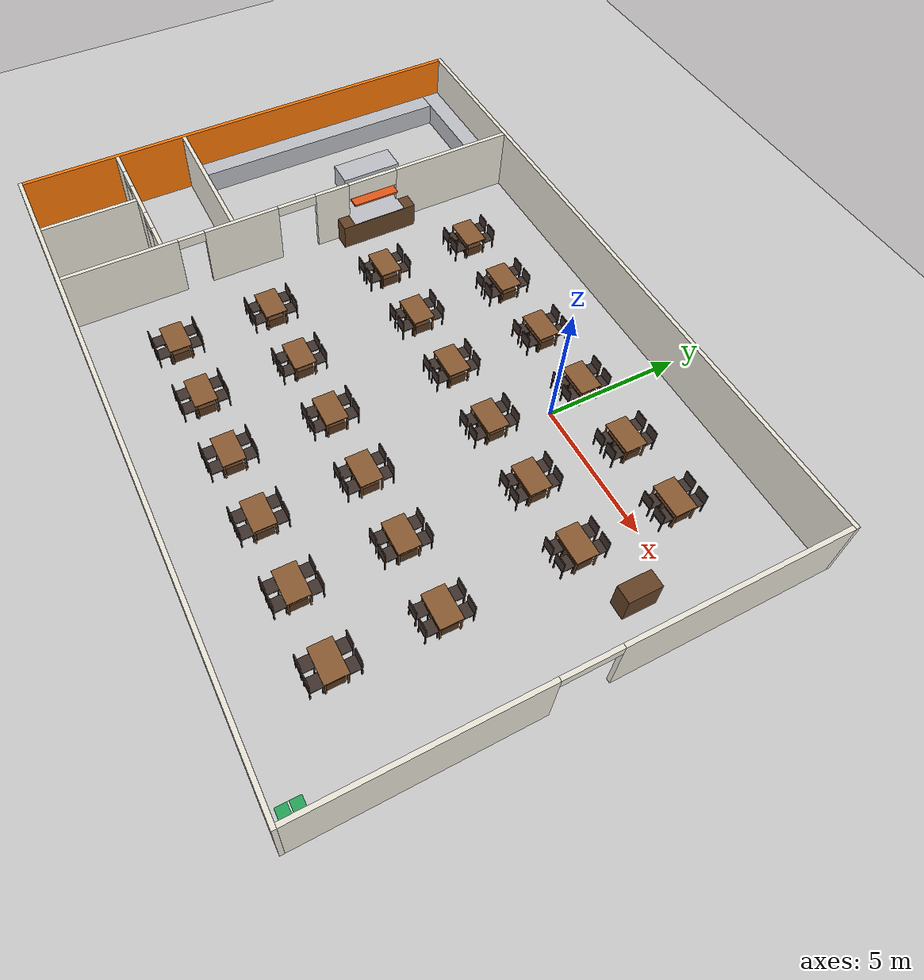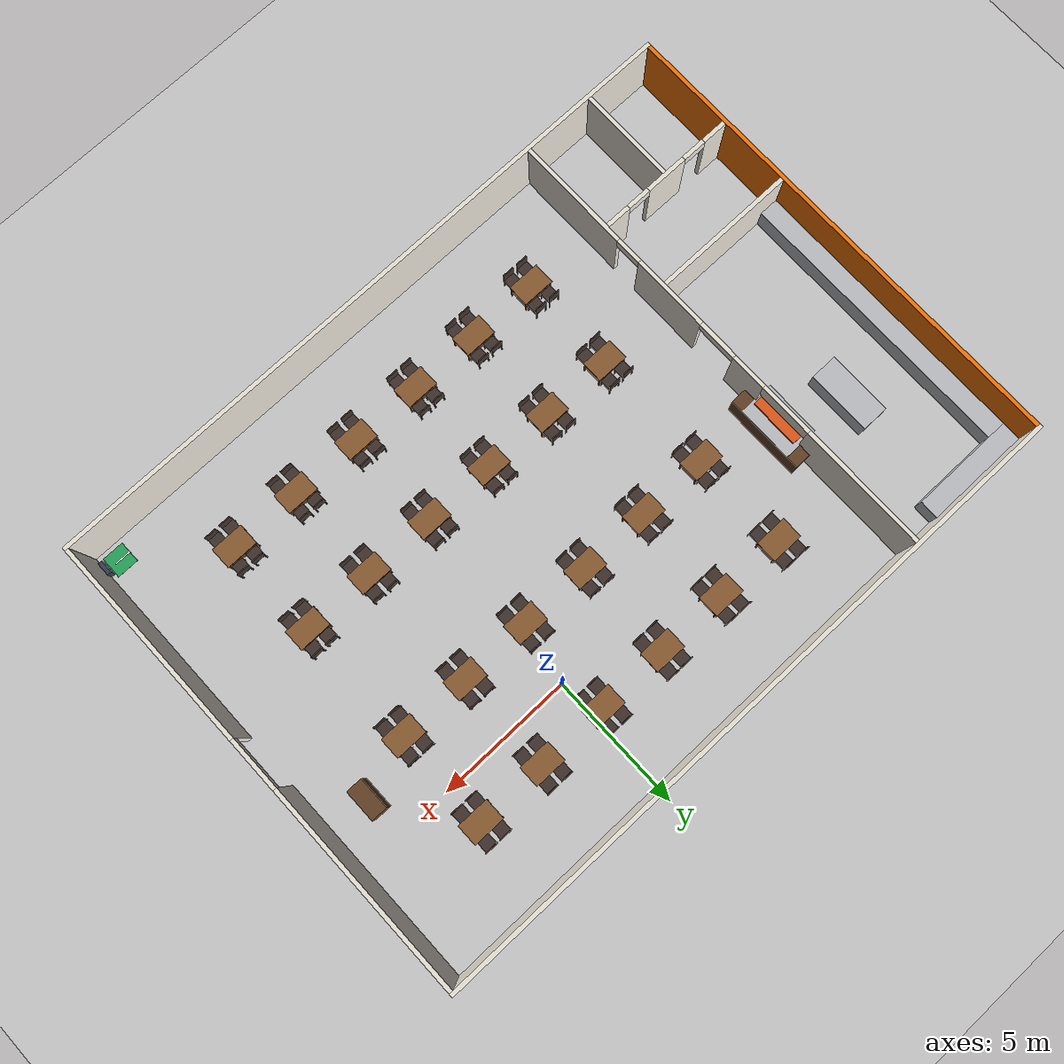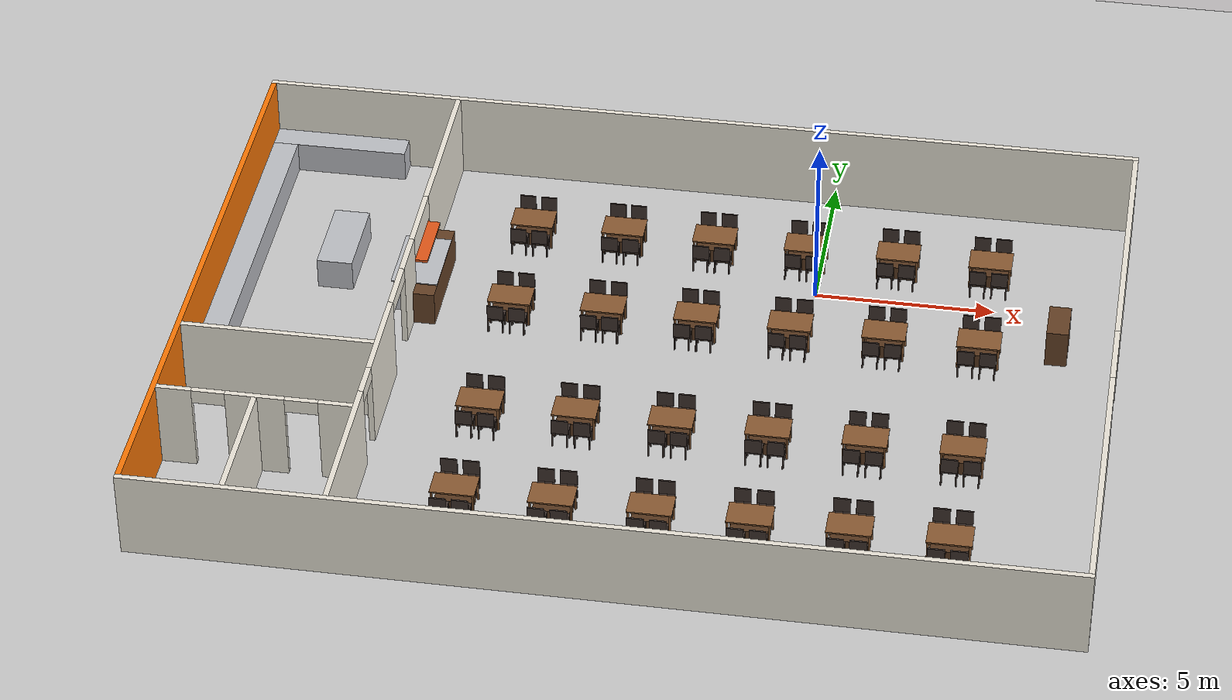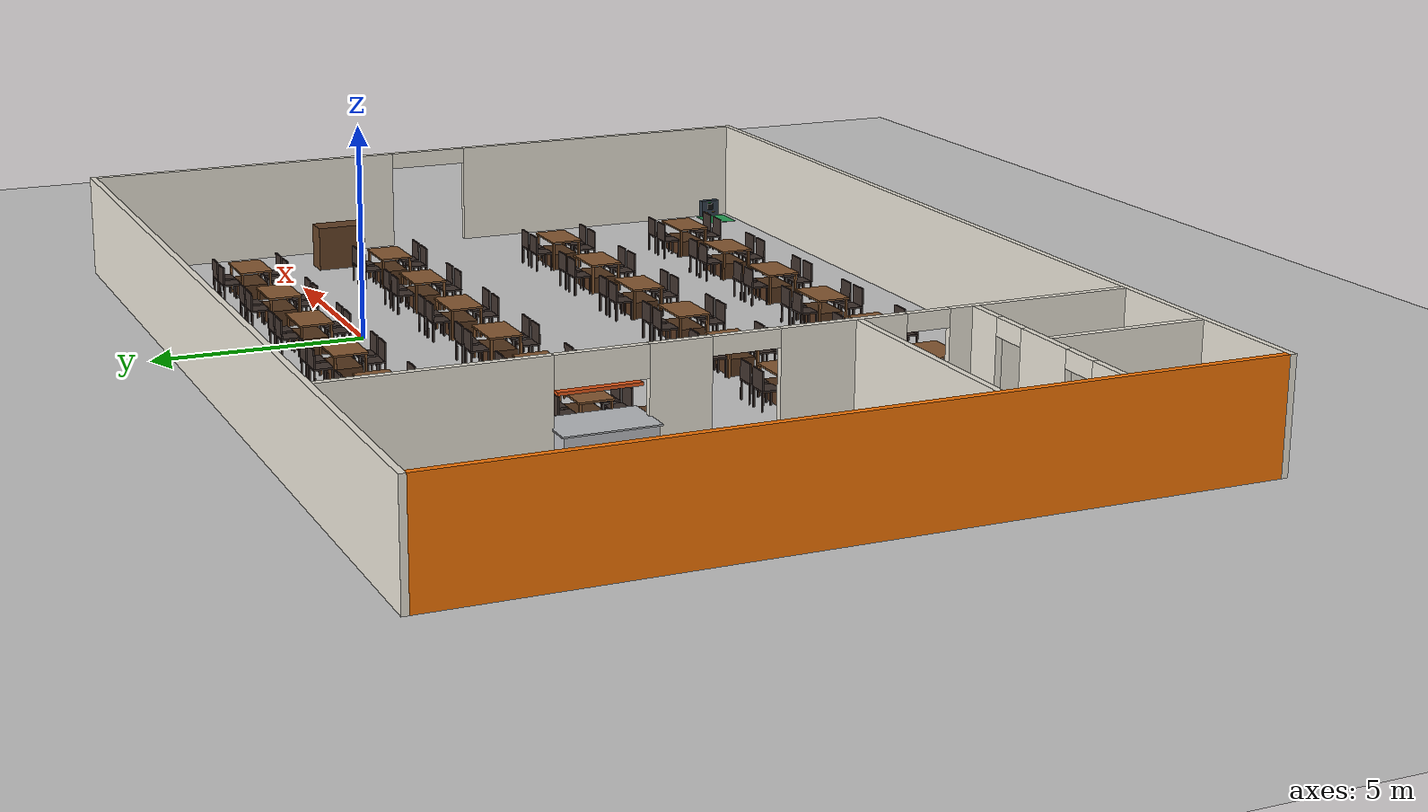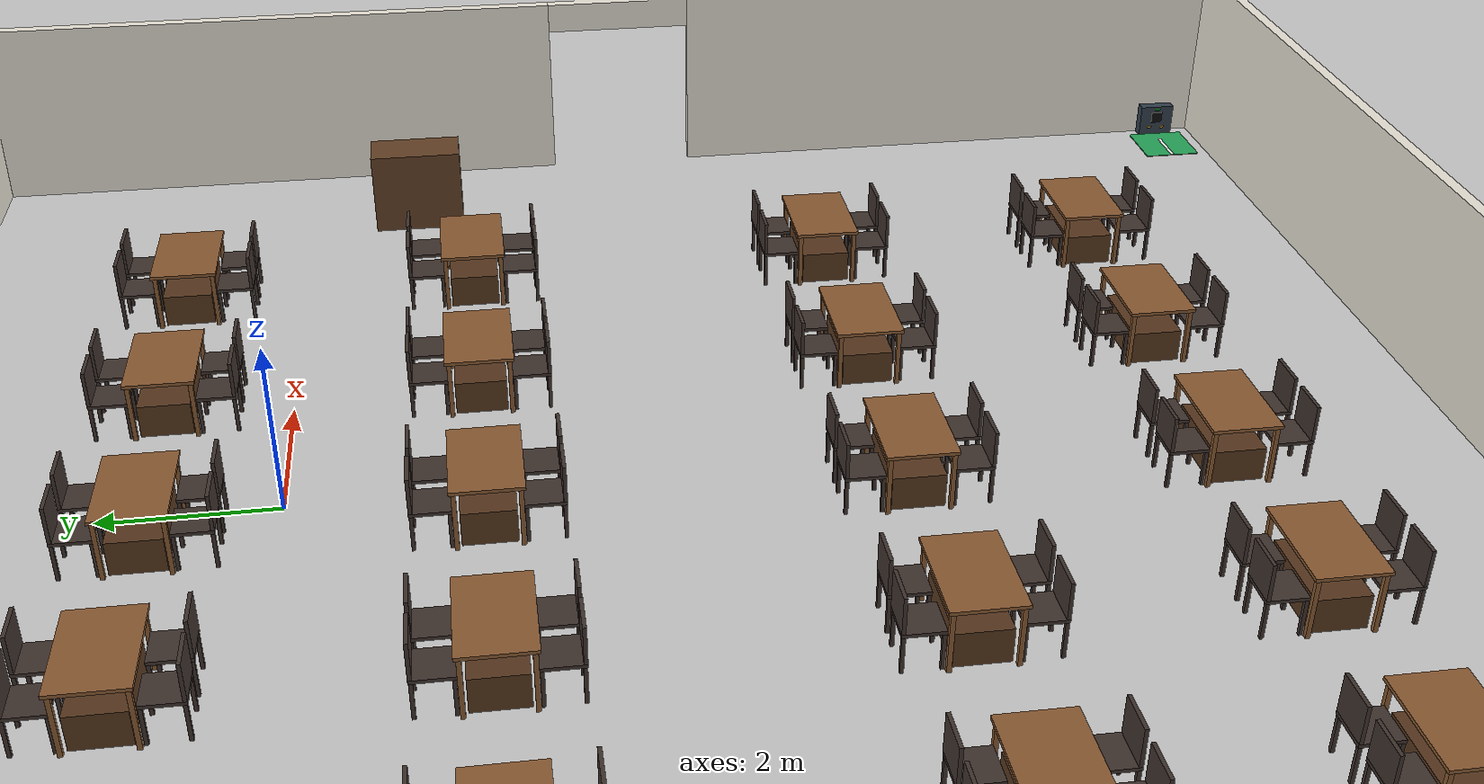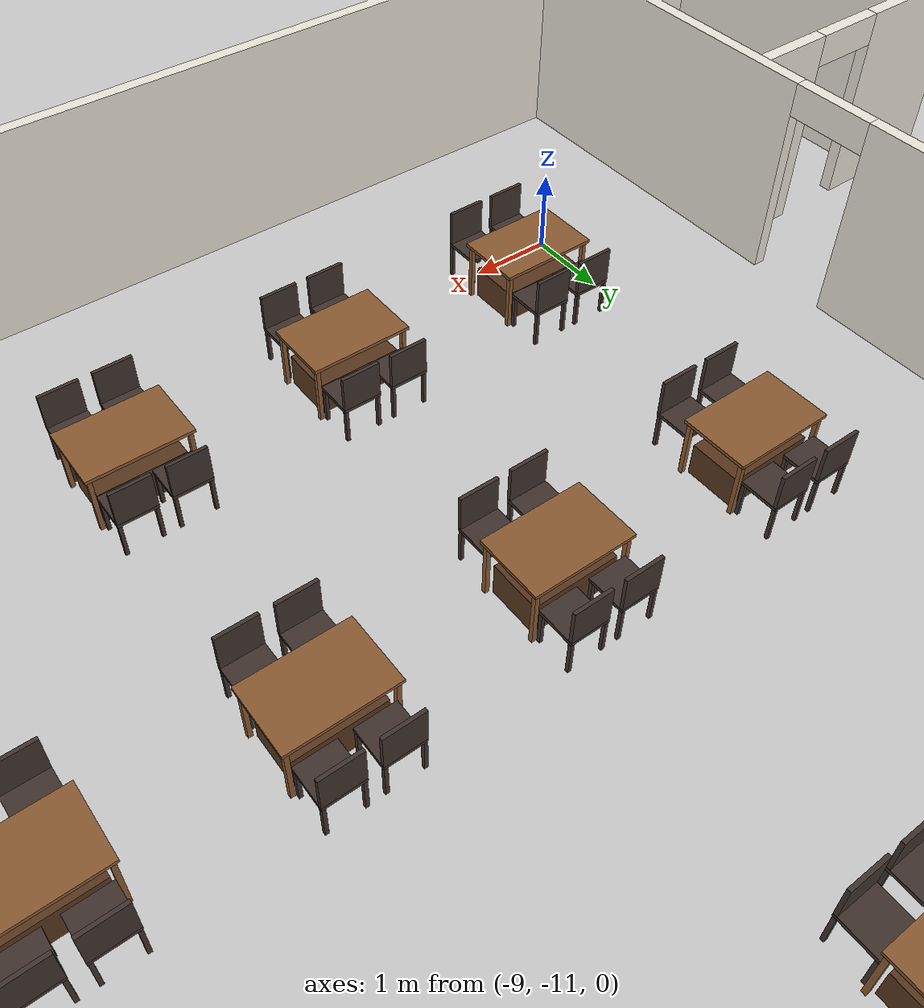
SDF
<?xml version='1.0' encoding='utf-8'?>
<sdf version="1.6">
  <world name="restaurant">
    <physics name="4ms" type="ignored"><max_step_size>0.004</max_step_size><real_time_factor>1.0</real_time_factor></physics><plugin filename="gz-sim-physics-system" name="gz::sim::systems::Physics" /><plugin filename="gz-sim-user-commands-system" name="gz::sim::systems::UserCommands" /><plugin filename="gz-sim-scene-broadcaster-system" name="gz::sim::systems::SceneBroadcaster" /><plugin filename="gz-sim-sensors-system" name="gz::sim::systems::Sensors"><render_engine>ogre2</render_engine></plugin><light name="sun" type="directional">
      <cast_shadows>1</cast_shadows>
      <pose frame="">0 0 10 0 -0 0</pose>
      <diffuse>0.8 0.8 0.8 1</diffuse>
      <specular>0.2 0.2 0.2 1</specular>
      <attenuation>
        <range>1000</range>
        <constant>0.9</constant>
        <linear>0.01</linear>
        <quadratic>0.001</quadratic>
      </attenuation>
      <direction>-0.5 0.1 -0.9</direction>
    </light>
    <model name="ground_plane">
      <static>1</static>
      <link name="link">
        <collision name="collision">
          <geometry>
            <plane>
              <normal>0 0 1</normal>
              <size>100 100</size>
            </plane>
          </geometry>
          <surface>
            <friction>
              <ode>
                <mu>100</mu>
                <mu2>50</mu2>
              </ode>
              <torsional>
                <ode />
              </torsional>
            </friction>
            <contact>
              <ode />
            </contact>
            <bounce />
          </surface>
          <max_contacts>10</max_contacts>
        </collision>
        <visual name="visual">
          <cast_shadows>0</cast_shadows>
          <geometry>
            <plane>
              <normal>0 0 1</normal>
              <size>100 100</size>
            </plane>
          </geometry>
          <material>
            <script>
              <uri>file://media/materials/scripts/gazebo.material</uri>
              <name>Gazebo/Grey</name>
            </script>
          </material>
        </visual>
        <self_collide>0</self_collide>
        <kinematic>0</kinematic>
      </link>
    </model>
    <gravity>0 0 -9.8</gravity>
    <magnetic_field>6e-06 2.3e-05 -4.2e-05</magnetic_field>
    <atmosphere type="adiabatic" />
    <scene>
      <ambient>0.4 0.4 0.4 1</ambient>
      <background>0.7 0.7 0.7 1</background>
      <shadows>1</shadows>
    </scene>
    <spherical_coordinates>
      <surface_model>EARTH_WGS84</surface_model>
      <latitude_deg>0</latitude_deg>
      <longitude_deg>0</longitude_deg>
      <elevation>0</elevation>
      <heading_deg>0</heading_deg>
    </spherical_coordinates>
    <gui fullscreen="0">
      <camera name="user_camera">
        <pose frame="">6.10976 5.57613 6.23677 0 0.318826 -2.42085</pose>
        <view_controller>orbit</view_controller>
        <projection_type>perspective</projection_type>
      </camera>
    </gui>
    <model name="restaurant">
      <static>true</static>
      <pose>-3.936 -4.4909 0 0 0 0</pose>
      <link name="Wall_8">
        <collision name="Wall_8_n_collision">
          <pose>0.0000 8.9250 1.2500 0 0 0</pose>
          <geometry><box><size>25.0000 0.1500 2.5000</size></box></geometry>
        </collision>
        <visual name="Wall_8_n_visual">
          <pose>0.0000 8.9250 1.2500 0 0 0</pose>
          <geometry><box><size>25.0000 0.1500 2.5000</size></box></geometry>
          <material><ambient>0.93 0.91 0.86 1</ambient><diffuse>0.93 0.91 0.86 1</diffuse><specular>0.05 0.05 0.05 1</specular></material>
        </visual>
      </link>
      <link name="Wall_12">
        <collision name="Wall_12_s_collision">
          <pose>0.0000 -8.9250 1.2500 0 0 0</pose>
          <geometry><box><size>25.0000 0.1500 2.5000</size></box></geometry>
        </collision>
        <visual name="Wall_12_s_visual">
          <pose>0.0000 -8.9250 1.2500 0 0 0</pose>
          <geometry><box><size>25.0000 0.1500 2.5000</size></box></geometry>
          <material><ambient>0.93 0.91 0.86 1</ambient><diffuse>0.93 0.91 0.86 1</diffuse><specular>0.05 0.05 0.05 1</specular></material>
        </visual>
      </link>
      <link name="Wall_10">
        <collision name="Wall_10_w_collision">
          <pose>-12.4250 0.0000 1.2500 0 0 0</pose>
          <geometry><box><size>0.1500 17.7000 2.5000</size></box></geometry>
        </collision>
        <visual name="Wall_10_w_visual">
          <pose>-12.4250 0.0000 1.2500 0 0 0</pose>
          <geometry><box><size>0.1500 17.7000 2.5000</size></box></geometry>
          <material><ambient>0.996078 0.47451 0.0196078 1</ambient><diffuse>0.996078 0.47451 0.0196078 1</diffuse><specular>0.05 0.05 0.05 1</specular></material>
        </visual>
      </link>
      <link name="Wall_14">
        <collision name="Wall_14_a_collision">
          <pose>12.4250 -4.9250 1.2500 0 0 0</pose>
          <geometry><box><size>0.1500 7.8500 2.5000</size></box></geometry>
        </collision>
        <visual name="Wall_14_a_visual">
          <pose>12.4250 -4.9250 1.2500 0 0 0</pose>
          <geometry><box><size>0.1500 7.8500 2.5000</size></box></geometry>
          <material><ambient>0.93 0.91 0.86 1</ambient><diffuse>0.93 0.91 0.86 1</diffuse><specular>0.05 0.05 0.05 1</specular></material>
        </visual>
        <collision name="Wall_14_b_collision">
          <pose>12.4250 4.9250 1.2500 0 0 0</pose>
          <geometry><box><size>0.1500 7.8500 2.5000</size></box></geometry>
        </collision>
        <visual name="Wall_14_b_visual">
          <pose>12.4250 4.9250 1.2500 0 0 0</pose>
          <geometry><box><size>0.1500 7.8500 2.5000</size></box></geometry>
          <material><ambient>0.93 0.91 0.86 1</ambient><diffuse>0.93 0.91 0.86 1</diffuse><specular>0.05 0.05 0.05 1</specular></material>
        </visual>
        <collision name="Wall_14_lintel_collision">
          <pose>12.4250 0.0000 2.3000 0 0 0</pose>
          <geometry><box><size>0.1500 2.0000 0.4000</size></box></geometry>
        </collision>
        <visual name="Wall_14_lintel_visual">
          <pose>12.4250 0.0000 2.3000 0 0 0</pose>
          <geometry><box><size>0.1500 2.0000 0.4000</size></box></geometry>
          <material><ambient>0.93 0.91 0.86 1</ambient><diffuse>0.93 0.91 0.86 1</diffuse><specular>0.05 0.05 0.05 1</specular></material>
        </visual>
      </link>
      <link name="Partition_Kitchen">
        <collision name="Partition_Kitchen_a_collision">
          <pose>-7.0000 -6.7250 1.2500 0 0 0</pose>
          <geometry><box><size>0.1500 4.2500 2.5000</size></box></geometry>
        </collision>
        <visual name="Partition_Kitchen_a_visual">
          <pose>-7.0000 -6.7250 1.2500 0 0 0</pose>
          <geometry><box><size>0.1500 4.2500 2.5000</size></box></geometry>
          <material><ambient>0.93 0.91 0.86 1</ambient><diffuse>0.93 0.91 0.86 1</diffuse><specular>0.05 0.05 0.05 1</specular></material>
        </visual>
        <collision name="Partition_Kitchen_b_collision">
          <pose>-7.0000 -2.1750 1.2500 0 0 0</pose>
          <geometry><box><size>0.1500 2.8500 2.5000</size></box></geometry>
        </collision>
        <visual name="Partition_Kitchen_b_visual">
          <pose>-7.0000 -2.1750 1.2500 0 0 0</pose>
          <geometry><box><size>0.1500 2.8500 2.5000</size></box></geometry>
          <material><ambient>0.93 0.91 0.86 1</ambient><diffuse>0.93 0.91 0.86 1</diffuse><specular>0.05 0.05 0.05 1</specular></material>
        </visual>
        <collision name="Partition_Kitchen_c1_collision">
          <pose>-7.0000 1.4250 1.2500 0 0 0</pose>
          <geometry><box><size>0.1500 1.3500 2.5000</size></box></geometry>
        </collision>
        <visual name="Partition_Kitchen_c1_visual">
          <pose>-7.0000 1.4250 1.2500 0 0 0</pose>
          <geometry><box><size>0.1500 1.3500 2.5000</size></box></geometry>
          <material><ambient>0.93 0.91 0.86 1</ambient><diffuse>0.93 0.91 0.86 1</diffuse><specular>0.05 0.05 0.05 1</specular></material>
        </visual>
        <collision name="Partition_Kitchen_c2_collision">
          <pose>-7.0000 6.4750 1.2500 0 0 0</pose>
          <geometry><box><size>0.1500 4.7500 2.5000</size></box></geometry>
        </collision>
        <visual name="Partition_Kitchen_c2_visual">
          <pose>-7.0000 6.4750 1.2500 0 0 0</pose>
          <geometry><box><size>0.1500 4.7500 2.5000</size></box></geometry>
          <material><ambient>0.93 0.91 0.86 1</ambient><diffuse>0.93 0.91 0.86 1</diffuse><specular>0.05 0.05 0.05 1</specular></material>
        </visual>
        <collision name="Partition_Kitchen_window_sill_collision">
          <pose>-7.0000 3.1000 0.5000 0 0 0</pose>
          <geometry><box><size>0.1500 2.0000 1.0000</size></box></geometry>
        </collision>
        <visual name="Partition_Kitchen_window_sill_visual">
          <pose>-7.0000 3.1000 0.5000 0 0 0</pose>
          <geometry><box><size>0.1500 2.0000 1.0000</size></box></geometry>
          <material><ambient>0.93 0.91 0.86 1</ambient><diffuse>0.93 0.91 0.86 1</diffuse><specular>0.05 0.05 0.05 1</specular></material>
        </visual>
        <collision name="Partition_Kitchen_window_header_collision">
          <pose>-7.0000 3.1000 2.1500 0 0 0</pose>
          <geometry><box><size>0.1500 2.0000 0.7000</size></box></geometry>
        </collision>
        <visual name="Partition_Kitchen_window_header_visual">
          <pose>-7.0000 3.1000 2.1500 0 0 0</pose>
          <geometry><box><size>0.1500 2.0000 0.7000</size></box></geometry>
          <material><ambient>0.93 0.91 0.86 1</ambient><diffuse>0.93 0.91 0.86 1</diffuse><specular>0.05 0.05 0.05 1</specular></material>
        </visual>
        <collision name="Partition_Kitchen_lintel_kitchen_collision">
          <pose>-7.0000 0.0000 2.3000 0 0 0</pose>
          <geometry><box><size>0.1500 1.5000 0.4000</size></box></geometry>
        </collision>
        <visual name="Partition_Kitchen_lintel_kitchen_visual">
          <pose>-7.0000 0.0000 2.3000 0 0 0</pose>
          <geometry><box><size>0.1500 1.5000 0.4000</size></box></geometry>
          <material><ambient>0.93 0.91 0.86 1</ambient><diffuse>0.93 0.91 0.86 1</diffuse><specular>0.05 0.05 0.05 1</specular></material>
        </visual>
        <collision name="Partition_Kitchen_lintel_wc_collision">
          <pose>-7.0000 -4.1000 2.3000 0 0 0</pose>
          <geometry><box><size>0.1500 1.0000 0.4000</size></box></geometry>
        </collision>
        <visual name="Partition_Kitchen_lintel_wc_visual">
          <pose>-7.0000 -4.1000 2.3000 0 0 0</pose>
          <geometry><box><size>0.1500 1.0000 0.4000</size></box></geometry>
          <material><ambient>0.93 0.91 0.86 1</ambient><diffuse>0.93 0.91 0.86 1</diffuse><specular>0.05 0.05 0.05 1</specular></material>
        </visual>
      </link>
      <link name="Wall_Kitchen_South">
        <collision name="Wall_Kitchen_South_w_collision">
          <pose>-9.7125 -2.5000 1.2500 0 0 0</pose>
          <geometry><box><size>5.2750 0.1500 2.5000</size></box></geometry>
        </collision>
        <visual name="Wall_Kitchen_South_w_visual">
          <pose>-9.7125 -2.5000 1.2500 0 0 0</pose>
          <geometry><box><size>5.2750 0.1500 2.5000</size></box></geometry>
          <material><ambient>0.93 0.91 0.86 1</ambient><diffuse>0.93 0.91 0.86 1</diffuse><specular>0.05 0.05 0.05 1</specular></material>
        </visual>
      </link>
      <link name="Wall_Restrooms">
        <collision name="Wall_Restrooms_a_collision">
          <pose>-11.8750 -5.2000 1.2500 0 0 0</pose>
          <geometry><box><size>0.9500 0.1500 2.5000</size></box></geometry>
        </collision>
        <visual name="Wall_Restrooms_a_visual">
          <pose>-11.8750 -5.2000 1.2500 0 0 0</pose>
          <geometry><box><size>0.9500 0.1500 2.5000</size></box></geometry>
          <material><ambient>0.93 0.91 0.86 1</ambient><diffuse>0.93 0.91 0.86 1</diffuse><specular>0.05 0.05 0.05 1</specular></material>
        </visual>
        <collision name="Wall_Restrooms_b_collision">
          <pose>-9.7000 -5.2000 1.2500 0 0 0</pose>
          <geometry><box><size>1.6000 0.1500 2.5000</size></box></geometry>
        </collision>
        <visual name="Wall_Restrooms_b_visual">
          <pose>-9.7000 -5.2000 1.2500 0 0 0</pose>
          <geometry><box><size>1.6000 0.1500 2.5000</size></box></geometry>
          <material><ambient>0.93 0.91 0.86 1</ambient><diffuse>0.93 0.91 0.86 1</diffuse><specular>0.05 0.05 0.05 1</specular></material>
        </visual>
        <collision name="Wall_Restrooms_c_collision">
          <pose>-7.5375 -5.2000 1.2500 0 0 0</pose>
          <geometry><box><size>0.9250 0.1500 2.5000</size></box></geometry>
        </collision>
        <visual name="Wall_Restrooms_c_visual">
          <pose>-7.5375 -5.2000 1.2500 0 0 0</pose>
          <geometry><box><size>0.9250 0.1500 2.5000</size></box></geometry>
          <material><ambient>0.93 0.91 0.86 1</ambient><diffuse>0.93 0.91 0.86 1</diffuse><specular>0.05 0.05 0.05 1</specular></material>
        </visual>
        <collision name="Wall_Restrooms_lintel1_collision">
          <pose>-10.9500 -5.2000 2.3000 0 0 0</pose>
          <geometry><box><size>0.9000 0.1500 0.4000</size></box></geometry>
        </collision>
        <visual name="Wall_Restrooms_lintel1_visual">
          <pose>-10.9500 -5.2000 2.3000 0 0 0</pose>
          <geometry><box><size>0.9000 0.1500 0.4000</size></box></geometry>
          <material><ambient>0.93 0.91 0.86 1</ambient><diffuse>0.93 0.91 0.86 1</diffuse><specular>0.05 0.05 0.05 1</specular></material>
        </visual>
        <collision name="Wall_Restrooms_lintel2_collision">
          <pose>-8.4500 -5.2000 2.3000 0 0 0</pose>
          <geometry><box><size>0.9000 0.1500 0.4000</size></box></geometry>
        </collision>
        <visual name="Wall_Restrooms_lintel2_visual">
          <pose>-8.4500 -5.2000 2.3000 0 0 0</pose>
          <geometry><box><size>0.9000 0.1500 0.4000</size></box></geometry>
          <material><ambient>0.93 0.91 0.86 1</ambient><diffuse>0.93 0.91 0.86 1</diffuse><specular>0.05 0.05 0.05 1</specular></material>
        </visual>
      </link>
      <link name="Wall_Restroom_Divider">
        <collision name="Wall_Restroom_Divider_w_collision">
          <pose>-9.7000 -7.0625 1.2500 0 0 0</pose>
          <geometry><box><size>0.1500 3.5750 2.5000</size></box></geometry>
        </collision>
        <visual name="Wall_Restroom_Divider_w_visual">
          <pose>-9.7000 -7.0625 1.2500 0 0 0</pose>
          <geometry><box><size>0.1500 3.5750 2.5000</size></box></geometry>
          <material><ambient>0.93 0.91 0.86 1</ambient><diffuse>0.93 0.91 0.86 1</diffuse><specular>0.05 0.05 0.05 1</specular></material>
        </visual>
      </link>
      <link name="Kitchen_Counter_West">
        <collision name="Kitchen_Counter_West_c_collision">
          <pose>-12.0000 2.8625 0.4500 0 0 0</pose>
          <geometry><box><size>0.7000 10.5750 0.9000</size></box></geometry>
        </collision>
        <visual name="Kitchen_Counter_West_c_visual">
          <pose>-12.0000 2.8625 0.4500 0 0 0</pose>
          <geometry><box><size>0.7000 10.5750 0.9000</size></box></geometry>
          <material><ambient>0.75 0.76 0.78 1</ambient><diffuse>0.75 0.76 0.78 1</diffuse><specular>0.05 0.05 0.05 1</specular></material>
        </visual>
      </link>
      <link name="Kitchen_Counter_North">
        <collision name="Kitchen_Counter_North_c_collision">
          <pose>-10.4250 8.5000 0.4500 0 0 0</pose>
          <geometry><box><size>3.8500 0.7000 0.9000</size></box></geometry>
        </collision>
        <visual name="Kitchen_Counter_North_c_visual">
          <pose>-10.4250 8.5000 0.4500 0 0 0</pose>
          <geometry><box><size>3.8500 0.7000 0.9000</size></box></geometry>
          <material><ambient>0.75 0.76 0.78 1</ambient><diffuse>0.75 0.76 0.78 1</diffuse><specular>0.05 0.05 0.05 1</specular></material>
        </visual>
      </link>
      <link name="Kitchen_Island">
        <collision name="Kitchen_Island_c_collision">
          <pose>-9.4000 4.0000 0.4500 0 0 0</pose>
          <geometry><box><size>1.0000 2.4000 0.9000</size></box></geometry>
        </collision>
        <visual name="Kitchen_Island_c_visual">
          <pose>-9.4000 4.0000 0.4500 0 0 0</pose>
          <geometry><box><size>1.0000 2.4000 0.9000</size></box></geometry>
          <material><ambient>0.75 0.76 0.78 1</ambient><diffuse>0.75 0.76 0.78 1</diffuse><specular>0.05 0.05 0.05 1</specular></material>
        </visual>
      </link>
      <link name="Pickup_Counter">
        <collision name="Pickup_Counter_c_collision">
          <pose>-6.6250 3.1000 0.5000 0 0 0</pose>
          <geometry><box><size>0.6000 3.0000 1.0000</size></box></geometry>
        </collision>
        <visual name="Pickup_Counter_c_visual">
          <pose>-6.6250 3.1000 0.5000 0 0 0</pose>
          <geometry><box><size>0.6000 3.0000 1.0000</size></box></geometry>
          <material><ambient>0.4 0.26 0.15 1</ambient><diffuse>0.4 0.26 0.15 1</diffuse><specular>0.05 0.05 0.05 1</specular></material>
        </visual>
      </link>
      <link name="Kitchen_Pass_Counter">
        <collision name="Kitchen_Pass_Counter_c_collision">
          <pose>-7.3250 3.1000 0.5000 0 0 0</pose>
          <geometry><box><size>0.5000 2.0000 1.0000</size></box></geometry>
        </collision>
        <visual name="Kitchen_Pass_Counter_c_visual">
          <pose>-7.3250 3.1000 0.5000 0 0 0</pose>
          <geometry><box><size>0.5000 2.0000 1.0000</size></box></geometry>
          <material><ambient>0.75 0.76 0.78 1</ambient><diffuse>0.75 0.76 0.78 1</diffuse><specular>0.05 0.05 0.05 1</specular></material>
        </visual>
      </link>
      <link name="Pass_Shelf">
        <collision name="Pass_Shelf_c_collision">
          <pose>-6.9750 3.1000 1.0150 0 0 0</pose>
          <geometry><box><size>1.3000 2.1000 0.0300</size></box></geometry>
        </collision>
        <visual name="Pass_Shelf_c_visual">
          <pose>-6.9750 3.1000 1.0150 0 0 0</pose>
          <geometry><box><size>1.3000 2.1000 0.0300</size></box></geometry>
          <material><ambient>0.75 0.76 0.78 1</ambient><diffuse>0.75 0.76 0.78 1</diffuse><specular>0.05 0.05 0.05 1</specular></material>
        </visual>
      </link>
      <link name="Heat_Lamp">
        <collision name="Heat_Lamp_c_collision">
          <pose>-6.8000 3.1000 1.6850 0 0 0</pose>
          <geometry><box><size>0.4000 1.8000 0.0700</size></box></geometry>
        </collision>
        <visual name="Heat_Lamp_c_visual">
          <pose>-6.8000 3.1000 1.6850 0 0 0</pose>
          <geometry><box><size>0.4000 1.8000 0.0700</size></box></geometry>
          <material><ambient>0.9 0.35 0.1 1</ambient><diffuse>0.9 0.35 0.1 1</diffuse><specular>0.05 0.05 0.05 1</specular></material>
        </visual>
      </link>
      <link name="Host_Stand">
        <collision name="Host_Stand_c_collision">
          <pose>10.8000 3.0000 0.5500 0 0 0</pose>
          <geometry><box><size>0.6000 1.2000 1.1000</size></box></geometry>
        </collision>
        <visual name="Host_Stand_c_visual">
          <pose>10.8000 3.0000 0.5500 0 0 0</pose>
          <geometry><box><size>0.6000 1.2000 1.1000</size></box></geometry>
          <material><ambient>0.4 0.26 0.15 1</ambient><diffuse>0.4 0.26 0.15 1</diffuse><specular>0.05 0.05 0.05 1</specular></material>
        </visual>
      </link>
    </model>
    <model name="table_0">
      <static>true</static>
      <pose>-8.2360 1.4091 0 0 0 0</pose>
      <link name="link">
        <!-- Solid table base: makes the table footprint visible to the 2D LiDAR
             (the table top overhangs at 0.73 m, above the scan plane) -->
        <collision name="base_collision">
          <pose>0.0000 0.0000 0.2000 0 0 0</pose>
          <geometry><box><size>1.0000 0.6000 0.4000</size></box></geometry>
        </collision>
        <visual name="base_visual">
          <pose>0.0000 0.0000 0.2000 0 0 0</pose>
          <geometry><box><size>1.0000 0.6000 0.4000</size></box></geometry>
          <material><ambient>0.35 0.22 0.12 1</ambient><diffuse>0.35 0.22 0.12 1</diffuse><specular>0.05 0.05 0.05 1</specular></material>
        </visual>
        <collision name="top_collision">
          <pose>0.0000 0.0000 0.7300 0 0 0</pose>
          <geometry><box><size>1.2000 0.8000 0.0400</size></box></geometry>
        </collision>
        <visual name="top_visual">
          <pose>0.0000 0.0000 0.7300 0 0 0</pose>
          <geometry><box><size>1.2000 0.8000 0.0400</size></box></geometry>
          <material><ambient>0.55 0.36 0.2 1</ambient><diffuse>0.55 0.36 0.2 1</diffuse><specular>0.05 0.05 0.05 1</specular></material>
        </visual>
        <collision name="leg0_collision">
          <pose>0.5500 0.3500 0.3550 0 0 0</pose>
          <geometry><box><size>0.0500 0.0500 0.7100</size></box></geometry>
        </collision>
        <visual name="leg0_visual">
          <pose>0.5500 0.3500 0.3550 0 0 0</pose>
          <geometry><box><size>0.0500 0.0500 0.7100</size></box></geometry>
          <material><ambient>0.55 0.36 0.2 1</ambient><diffuse>0.55 0.36 0.2 1</diffuse><specular>0.05 0.05 0.05 1</specular></material>
        </visual>
        <collision name="leg1_collision">
          <pose>0.5500 -0.3500 0.3550 0 0 0</pose>
          <geometry><box><size>0.0500 0.0500 0.7100</size></box></geometry>
        </collision>
        <visual name="leg1_visual">
          <pose>0.5500 -0.3500 0.3550 0 0 0</pose>
          <geometry><box><size>0.0500 0.0500 0.7100</size></box></geometry>
          <material><ambient>0.55 0.36 0.2 1</ambient><diffuse>0.55 0.36 0.2 1</diffuse><specular>0.05 0.05 0.05 1</specular></material>
        </visual>
        <collision name="leg2_collision">
          <pose>-0.5500 0.3500 0.3550 0 0 0</pose>
          <geometry><box><size>0.0500 0.0500 0.7100</size></box></geometry>
        </collision>
        <visual name="leg2_visual">
          <pose>-0.5500 0.3500 0.3550 0 0 0</pose>
          <geometry><box><size>0.0500 0.0500 0.7100</size></box></geometry>
          <material><ambient>0.55 0.36 0.2 1</ambient><diffuse>0.55 0.36 0.2 1</diffuse><specular>0.05 0.05 0.05 1</specular></material>
        </visual>
        <collision name="leg3_collision">
          <pose>-0.5500 -0.3500 0.3550 0 0 0</pose>
          <geometry><box><size>0.0500 0.0500 0.7100</size></box></geometry>
        </collision>
        <visual name="leg3_visual">
          <pose>-0.5500 -0.3500 0.3550 0 0 0</pose>
          <geometry><box><size>0.0500 0.0500 0.7100</size></box></geometry>
          <material><ambient>0.55 0.36 0.2 1</ambient><diffuse>0.55 0.36 0.2 1</diffuse><specular>0.05 0.05 0.05 1</specular></material>
        </visual>
        <collision name="chair0_seat_collision">
          <pose>-0.3000 0.6000 0.4500 0 0 0</pose>
          <geometry><box><size>0.4500 0.4500 0.0400</size></box></geometry>
        </collision>
        <visual name="chair0_seat_visual">
          <pose>-0.3000 0.6000 0.4500 0 0 0</pose>
          <geometry><box><size>0.4500 0.4500 0.0400</size></box></geometry>
          <material><ambient>0.25 0.2 0.18 1</ambient><diffuse>0.25 0.2 0.18 1</diffuse><specular>0.05 0.05 0.05 1</specular></material>
        </visual>
        <collision name="chair0_leg0_collision">
          <pose>-0.1000 0.8000 0.2150 0 0 0</pose>
          <geometry><box><size>0.0400 0.0400 0.4300</size></box></geometry>
        </collision>
        <visual name="chair0_leg0_visual">
          <pose>-0.1000 0.8000 0.2150 0 0 0</pose>
          <geometry><box><size>0.0400 0.0400 0.4300</size></box></geometry>
          <material><ambient>0.25 0.2 0.18 1</ambient><diffuse>0.25 0.2 0.18 1</diffuse><specular>0.05 0.05 0.05 1</specular></material>
        </visual>
        <collision name="chair0_leg1_collision">
          <pose>-0.1000 0.4000 0.2150 0 0 0</pose>
          <geometry><box><size>0.0400 0.0400 0.4300</size></box></geometry>
        </collision>
        <visual name="chair0_leg1_visual">
          <pose>-0.1000 0.4000 0.2150 0 0 0</pose>
          <geometry><box><size>0.0400 0.0400 0.4300</size></box></geometry>
          <material><ambient>0.25 0.2 0.18 1</ambient><diffuse>0.25 0.2 0.18 1</diffuse><specular>0.05 0.05 0.05 1</specular></material>
        </visual>
        <collision name="chair0_leg2_collision">
          <pose>-0.5000 0.8000 0.2150 0 0 0</pose>
          <geometry><box><size>0.0400 0.0400 0.4300</size></box></geometry>
        </collision>
        <visual name="chair0_leg2_visual">
          <pose>-0.5000 0.8000 0.2150 0 0 0</pose>
          <geometry><box><size>0.0400 0.0400 0.4300</size></box></geometry>
          <material><ambient>0.25 0.2 0.18 1</ambient><diffuse>0.25 0.2 0.18 1</diffuse><specular>0.05 0.05 0.05 1</specular></material>
        </visual>
        <collision name="chair0_leg3_collision">
          <pose>-0.5000 0.4000 0.2150 0 0 0</pose>
          <geometry><box><size>0.0400 0.0400 0.4300</size></box></geometry>
        </collision>
        <visual name="chair0_leg3_visual">
          <pose>-0.5000 0.4000 0.2150 0 0 0</pose>
          <geometry><box><size>0.0400 0.0400 0.4300</size></box></geometry>
          <material><ambient>0.25 0.2 0.18 1</ambient><diffuse>0.25 0.2 0.18 1</diffuse><specular>0.05 0.05 0.05 1</specular></material>
        </visual>
        <collision name="chair0_back_collision">
          <pose>-0.3000 0.8050 0.6850 0 0 0</pose>
          <geometry><box><size>0.4500 0.0400 0.4300</size></box></geometry>
        </collision>
        <visual name="chair0_back_visual">
          <pose>-0.3000 0.8050 0.6850 0 0 0</pose>
          <geometry><box><size>0.4500 0.0400 0.4300</size></box></geometry>
          <material><ambient>0.25 0.2 0.18 1</ambient><diffuse>0.25 0.2 0.18 1</diffuse><specular>0.05 0.05 0.05 1</specular></material>
        </visual>
        <collision name="chair1_seat_collision">
          <pose>-0.3000 -0.6000 0.4500 0 0 0</pose>
          <geometry><box><size>0.4500 0.4500 0.0400</size></box></geometry>
        </collision>
        <visual name="chair1_seat_visual">
          <pose>-0.3000 -0.6000 0.4500 0 0 0</pose>
          <geometry><box><size>0.4500 0.4500 0.0400</size></box></geometry>
          <material><ambient>0.25 0.2 0.18 1</ambient><diffuse>0.25 0.2 0.18 1</diffuse><specular>0.05 0.05 0.05 1</specular></material>
        </visual>
        <collision name="chair1_leg0_collision">
          <pose>-0.1000 -0.4000 0.2150 0 0 0</pose>
          <geometry><box><size>0.0400 0.0400 0.4300</size></box></geometry>
        </collision>
        <visual name="chair1_leg0_visual">
          <pose>-0.1000 -0.4000 0.2150 0 0 0</pose>
          <geometry><box><size>0.0400 0.0400 0.4300</size></box></geometry>
          <material><ambient>0.25 0.2 0.18 1</ambient><diffuse>0.25 0.2 0.18 1</diffuse><specular>0.05 0.05 0.05 1</specular></material>
        </visual>
        <collision name="chair1_leg1_collision">
          <pose>-0.1000 -0.8000 0.2150 0 0 0</pose>
          <geometry><box><size>0.0400 0.0400 0.4300</size></box></geometry>
        </collision>
        <visual name="chair1_leg1_visual">
          <pose>-0.1000 -0.8000 0.2150 0 0 0</pose>
          <geometry><box><size>0.0400 0.0400 0.4300</size></box></geometry>
          <material><ambient>0.25 0.2 0.18 1</ambient><diffuse>0.25 0.2 0.18 1</diffuse><specular>0.05 0.05 0.05 1</specular></material>
        </visual>
        <collision name="chair1_leg2_collision">
          <pose>-0.5000 -0.4000 0.2150 0 0 0</pose>
          <geometry><box><size>0.0400 0.0400 0.4300</size></box></geometry>
        </collision>
        <visual name="chair1_leg2_visual">
          <pose>-0.5000 -0.4000 0.2150 0 0 0</pose>
          <geometry><box><size>0.0400 0.0400 0.4300</size></box></geometry>
          <material><ambient>0.25 0.2 0.18 1</ambient><diffuse>0.25 0.2 0.18 1</diffuse><specular>0.05 0.05 0.05 1</specular></material>
        </visual>
        <collision name="chair1_leg3_collision">
          <pose>-0.5000 -0.8000 0.2150 0 0 0</pose>
          <geometry><box><size>0.0400 0.0400 0.4300</size></box></geometry>
        </collision>
        <visual name="chair1_leg3_visual">
          <pose>-0.5000 -0.8000 0.2150 0 0 0</pose>
          <geometry><box><size>0.0400 0.0400 0.4300</size></box></geometry>
          <material><ambient>0.25 0.2 0.18 1</ambient><diffuse>0.25 0.2 0.18 1</diffuse><specular>0.05 0.05 0.05 1</specular></material>
        </visual>
        <collision name="chair1_back_collision">
          <pose>-0.3000 -0.8050 0.6850 0 0 0</pose>
          <geometry><box><size>0.4500 0.0400 0.4300</size></box></geometry>
        </collision>
        <visual name="chair1_back_visual">
          <pose>-0.3000 -0.8050 0.6850 0 0 0</pose>
          <geometry><box><size>0.4500 0.0400 0.4300</size></box></geometry>
          <material><ambient>0.25 0.2 0.18 1</ambient><diffuse>0.25 0.2 0.18 1</diffuse><specular>0.05 0.05 0.05 1</specular></material>
        </visual>
        <collision name="chair2_seat_collision">
          <pose>0.3000 0.6000 0.4500 0 0 0</pose>
          <geometry><box><size>0.4500 0.4500 0.0400</size></box></geometry>
        </collision>
        <visual name="chair2_seat_visual">
          <pose>0.3000 0.6000 0.4500 0 0 0</pose>
          <geometry><box><size>0.4500 0.4500 0.0400</size></box></geometry>
          <material><ambient>0.25 0.2 0.18 1</ambient><diffuse>0.25 0.2 0.18 1</diffuse><specular>0.05 0.05 0.05 1</specular></material>
        </visual>
        <collision name="chair2_leg0_collision">
          <pose>0.5000 0.8000 0.2150 0 0 0</pose>
          <geometry><box><size>0.0400 0.0400 0.4300</size></box></geometry>
        </collision>
        <visual name="chair2_leg0_visual">
          <pose>0.5000 0.8000 0.2150 0 0 0</pose>
          <geometry><box><size>0.0400 0.0400 0.4300</size></box></geometry>
          <material><ambient>0.25 0.2 0.18 1</ambient><diffuse>0.25 0.2 0.18 1</diffuse><specular>0.05 0.05 0.05 1</specular></material>
        </visual>
        <collision name="chair2_leg1_collision">
          <pose>0.5000 0.4000 0.2150 0 0 0</pose>
          <geometry><box><size>0.0400 0.0400 0.4300</size></box></geometry>
        </collision>
        <visual name="chair2_leg1_visual">
          <pose>0.5000 0.4000 0.2150 0 0 0</pose>
          <geometry><box><size>0.0400 0.0400 0.4300</size></box></geometry>
          <material><ambient>0.25 0.2 0.18 1</ambient><diffuse>0.25 0.2 0.18 1</diffuse><specular>0.05 0.05 0.05 1</specular></material>
        </visual>
        <collision name="chair2_leg2_collision">
          <pose>0.1000 0.8000 0.2150 0 0 0</pose>
          <geometry><box><size>0.0400 0.0400 0.4300</size></box></geometry>
        </collision>
        <visual name="chair2_leg2_visual">
          <pose>0.1000 0.8000 0.2150 0 0 0</pose>
          <geometry><box><size>0.0400 0.0400 0.4300</size></box></geometry>
          <material><ambient>0.25 0.2 0.18 1</ambient><diffuse>0.25 0.2 0.18 1</diffuse><specular>0.05 0.05 0.05 1</specular></material>
        </visual>
        <collision name="chair2_leg3_collision">
          <pose>0.1000 0.4000 0.2150 0 0 0</pose>
          <geometry><box><size>0.0400 0.0400 0.4300</size></box></geometry>
        </collision>
        <visual name="chair2_leg3_visual">
          <pose>0.1000 0.4000 0.2150 0 0 0</pose>
          <geometry><box><size>0.0400 0.0400 0.4300</size></box></geometry>
          <material><ambient>0.25 0.2 0.18 1</ambient><diffuse>0.25 0.2 0.18 1</diffuse><specular>0.05 0.05 0.05 1</specular></material>
        </visual>
        <collision name="chair2_back_collision">
          <pose>0.3000 0.8050 0.6850 0 0 0</pose>
          <geometry><box><size>0.4500 0.0400 0.4300</size></box></geometry>
        </collision>
        <visual name="chair2_back_visual">
          <pose>0.3000 0.8050 0.6850 0 0 0</pose>
          <geometry><box><size>0.4500 0.0400 0.4300</size></box></geometry>
          <material><ambient>0.25 0.2 0.18 1</ambient><diffuse>0.25 0.2 0.18 1</diffuse><specular>0.05 0.05 0.05 1</specular></material>
        </visual>
        <collision name="chair3_seat_collision">
          <pose>0.3000 -0.6000 0.4500 0 0 0</pose>
          <geometry><box><size>0.4500 0.4500 0.0400</size></box></geometry>
        </collision>
        <visual name="chair3_seat_visual">
          <pose>0.3000 -0.6000 0.4500 0 0 0</pose>
          <geometry><box><size>0.4500 0.4500 0.0400</size></box></geometry>
          <material><ambient>0.25 0.2 0.18 1</ambient><diffuse>0.25 0.2 0.18 1</diffuse><specular>0.05 0.05 0.05 1</specular></material>
        </visual>
        <collision name="chair3_leg0_collision">
          <pose>0.5000 -0.4000 0.2150 0 0 0</pose>
          <geometry><box><size>0.0400 0.0400 0.4300</size></box></geometry>
        </collision>
        <visual name="chair3_leg0_visual">
          <pose>0.5000 -0.4000 0.2150 0 0 0</pose>
          <geometry><box><size>0.0400 0.0400 0.4300</size></box></geometry>
          <material><ambient>0.25 0.2 0.18 1</ambient><diffuse>0.25 0.2 0.18 1</diffuse><specular>0.05 0.05 0.05 1</specular></material>
        </visual>
        <collision name="chair3_leg1_collision">
          <pose>0.5000 -0.8000 0.2150 0 0 0</pose>
          <geometry><box><size>0.0400 0.0400 0.4300</size></box></geometry>
        </collision>
        <visual name="chair3_leg1_visual">
          <pose>0.5000 -0.8000 0.2150 0 0 0</pose>
          <geometry><box><size>0.0400 0.0400 0.4300</size></box></geometry>
          <material><ambient>0.25 0.2 0.18 1</ambient><diffuse>0.25 0.2 0.18 1</diffuse><specular>0.05 0.05 0.05 1</specular></material>
        </visual>
        <collision name="chair3_leg2_collision">
          <pose>0.1000 -0.4000 0.2150 0 0 0</pose>
          <geometry><box><size>0.0400 0.0400 0.4300</size></box></geometry>
        </collision>
        <visual name="chair3_leg2_visual">
          <pose>0.1000 -0.4000 0.2150 0 0 0</pose>
          <geometry><box><size>0.0400 0.0400 0.4300</size></box></geometry>
          <material><ambient>0.25 0.2 0.18 1</ambient><diffuse>0.25 0.2 0.18 1</diffuse><specular>0.05 0.05 0.05 1</specular></material>
        </visual>
        <collision name="chair3_leg3_collision">
          <pose>0.1000 -0.8000 0.2150 0 0 0</pose>
          <geometry><box><size>0.0400 0.0400 0.4300</size></box></geometry>
        </collision>
        <visual name="chair3_leg3_visual">
          <pose>0.1000 -0.8000 0.2150 0 0 0</pose>
          <geometry><box><size>0.0400 0.0400 0.4300</size></box></geometry>
          <material><ambient>0.25 0.2 0.18 1</ambient><diffuse>0.25 0.2 0.18 1</diffuse><specular>0.05 0.05 0.05 1</specular></material>
        </visual>
        <collision name="chair3_back_collision">
          <pose>0.3000 -0.8050 0.6850 0 0 0</pose>
          <geometry><box><size>0.4500 0.0400 0.4300</size></box></geometry>
        </collision>
        <visual name="chair3_back_visual">
          <pose>0.3000 -0.8050 0.6850 0 0 0</pose>
          <geometry><box><size>0.4500 0.0400 0.4300</size></box></geometry>
          <material><ambient>0.25 0.2 0.18 1</ambient><diffuse>0.25 0.2 0.18 1</diffuse><specular>0.05 0.05 0.05 1</specular></material>
        </visual>
      </link>
    </model>
    <model name="table_1">
      <static>true</static>
      <pose>-5.6360 1.4091 0 0 0 0</pose>
      <link name="link">
        <!-- Solid table base: makes the table footprint visible to the 2D LiDAR
             (the table top overhangs at 0.73 m, above the scan plane) -->
        <collision name="base_collision">
          <pose>0.0000 0.0000 0.2000 0 0 0</pose>
          <geometry><box><size>1.0000 0.6000 0.4000</size></box></geometry>
        </collision>
        <visual name="base_visual">
          <pose>0.0000 0.0000 0.2000 0 0 0</pose>
          <geometry><box><size>1.0000 0.6000 0.4000</size></box></geometry>
          <material><ambient>0.35 0.22 0.12 1</ambient><diffuse>0.35 0.22 0.12 1</diffuse><specular>0.05 0.05 0.05 1</specular></material>
        </visual>
        <collision name="top_collision">
          <pose>0.0000 0.0000 0.7300 0 0 0</pose>
          <geometry><box><size>1.2000 0.8000 0.0400</size></box></geometry>
        </collision>
        <visual name="top_visual">
          <pose>0.0000 0.0000 0.7300 0 0 0</pose>
          <geometry><box><size>1.2000 0.8000 0.0400</size></box></geometry>
          <material><ambient>0.55 0.36 0.2 1</ambient><diffuse>0.55 0.36 0.2 1</diffuse><specular>0.05 0.05 0.05 1</specular></material>
        </visual>
        <collision name="leg0_collision">
          <pose>0.5500 0.3500 0.3550 0 0 0</pose>
          <geometry><box><size>0.0500 0.0500 0.7100</size></box></geometry>
        </collision>
        <visual name="leg0_visual">
          <pose>0.5500 0.3500 0.3550 0 0 0</pose>
          <geometry><box><size>0.0500 0.0500 0.7100</size></box></geometry>
          <material><ambient>0.55 0.36 0.2 1</ambient><diffuse>0.55 0.36 0.2 1</diffuse><specular>0.05 0.05 0.05 1</specular></material>
        </visual>
        <collision name="leg1_collision">
          <pose>0.5500 -0.3500 0.3550 0 0 0</pose>
          <geometry><box><size>0.0500 0.0500 0.7100</size></box></geometry>
        </collision>
        <visual name="leg1_visual">
          <pose>0.5500 -0.3500 0.3550 0 0 0</pose>
          <geometry><box><size>0.0500 0.0500 0.7100</size></box></geometry>
          <material><ambient>0.55 0.36 0.2 1</ambient><diffuse>0.55 0.36 0.2 1</diffuse><specular>0.05 0.05 0.05 1</specular></material>
        </visual>
        <collision name="leg2_collision">
          <pose>-0.5500 0.3500 0.3550 0 0 0</pose>
          <geometry><box><size>0.0500 0.0500 0.7100</size></box></geometry>
        </collision>
        <visual name="leg2_visual">
          <pose>-0.5500 0.3500 0.3550 0 0 0</pose>
          <geometry><box><size>0.0500 0.0500 0.7100</size></box></geometry>
          <material><ambient>0.55 0.36 0.2 1</ambient><diffuse>0.55 0.36 0.2 1</diffuse><specular>0.05 0.05 0.05 1</specular></material>
        </visual>
        <collision name="leg3_collision">
          <pose>-0.5500 -0.3500 0.3550 0 0 0</pose>
          <geometry><box><size>0.0500 0.0500 0.7100</size></box></geometry>
        </collision>
        <visual name="leg3_visual">
          <pose>-0.5500 -0.3500 0.3550 0 0 0</pose>
          <geometry><box><size>0.0500 0.0500 0.7100</size></box></geometry>
          <material><ambient>0.55 0.36 0.2 1</ambient><diffuse>0.55 0.36 0.2 1</diffuse><specular>0.05 0.05 0.05 1</specular></material>
        </visual>
        <collision name="chair0_seat_collision">
          <pose>-0.3000 0.6000 0.4500 0 0 0</pose>
          <geometry><box><size>0.4500 0.4500 0.0400</size></box></geometry>
        </collision>
        <visual name="chair0_seat_visual">
          <pose>-0.3000 0.6000 0.4500 0 0 0</pose>
          <geometry><box><size>0.4500 0.4500 0.0400</size></box></geometry>
          <material><ambient>0.25 0.2 0.18 1</ambient><diffuse>0.25 0.2 0.18 1</diffuse><specular>0.05 0.05 0.05 1</specular></material>
        </visual>
        <collision name="chair0_leg0_collision">
          <pose>-0.1000 0.8000 0.2150 0 0 0</pose>
          <geometry><box><size>0.0400 0.0400 0.4300</size></box></geometry>
        </collision>
        <visual name="chair0_leg0_visual">
          <pose>-0.1000 0.8000 0.2150 0 0 0</pose>
          <geometry><box><size>0.0400 0.0400 0.4300</size></box></geometry>
          <material><ambient>0.25 0.2 0.18 1</ambient><diffuse>0.25 0.2 0.18 1</diffuse><specular>0.05 0.05 0.05 1</specular></material>
        </visual>
        <collision name="chair0_leg1_collision">
          <pose>-0.1000 0.4000 0.2150 0 0 0</pose>
          <geometry><box><size>0.0400 0.0400 0.4300</size></box></geometry>
        </collision>
        <visual name="chair0_leg1_visual">
          <pose>-0.1000 0.4000 0.2150 0 0 0</pose>
          <geometry><box><size>0.0400 0.0400 0.4300</size></box></geometry>
          <material><ambient>0.25 0.2 0.18 1</ambient><diffuse>0.25 0.2 0.18 1</diffuse><specular>0.05 0.05 0.05 1</specular></material>
        </visual>
        <collision name="chair0_leg2_collision">
          <pose>-0.5000 0.8000 0.2150 0 0 0</pose>
          <geometry><box><size>0.0400 0.0400 0.4300</size></box></geometry>
        </collision>
        <visual name="chair0_leg2_visual">
          <pose>-0.5000 0.8000 0.2150 0 0 0</pose>
          <geometry><box><size>0.0400 0.0400 0.4300</size></box></geometry>
          <material><ambient>0.25 0.2 0.18 1</ambient><diffuse>0.25 0.2 0.18 1</diffuse><specular>0.05 0.05 0.05 1</specular></material>
        </visual>
        <collision name="chair0_leg3_collision">
          <pose>-0.5000 0.4000 0.2150 0 0 0</pose>
          <geometry><box><size>0.0400 0.0400 0.4300</size></box></geometry>
        </collision>
        <visual name="chair0_leg3_visual">
          <pose>-0.5000 0.4000 0.2150 0 0 0</pose>
          <geometry><box><size>0.0400 0.0400 0.4300</size></box></geometry>
          <material><ambient>0.25 0.2 0.18 1</ambient><diffuse>0.25 0.2 0.18 1</diffuse><specular>0.05 0.05 0.05 1</specular></material>
        </visual>
        <collision name="chair0_back_collision">
          <pose>-0.3000 0.8050 0.6850 0 0 0</pose>
          <geometry><box><size>0.4500 0.0400 0.4300</size></box></geometry>
        </collision>
        <visual name="chair0_back_visual">
          <pose>-0.3000 0.8050 0.6850 0 0 0</pose>
          <geometry><box><size>0.4500 0.0400 0.4300</size></box></geometry>
          <material><ambient>0.25 0.2 0.18 1</ambient><diffuse>0.25 0.2 0.18 1</diffuse><specular>0.05 0.05 0.05 1</specular></material>
        </visual>
        <collision name="chair1_seat_collision">
          <pose>-0.3000 -0.6000 0.4500 0 0 0</pose>
          <geometry><box><size>0.4500 0.4500 0.0400</size></box></geometry>
        </collision>
        <visual name="chair1_seat_visual">
          <pose>-0.3000 -0.6000 0.4500 0 0 0</pose>
          <geometry><box><size>0.4500 0.4500 0.0400</size></box></geometry>
          <material><ambient>0.25 0.2 0.18 1</ambient><diffuse>0.25 0.2 0.18 1</diffuse><specular>0.05 0.05 0.05 1</specular></material>
        </visual>
        <collision name="chair1_leg0_collision">
          <pose>-0.1000 -0.4000 0.2150 0 0 0</pose>
          <geometry><box><size>0.0400 0.0400 0.4300</size></box></geometry>
        </collision>
        <visual name="chair1_leg0_visual">
          <pose>-0.1000 -0.4000 0.2150 0 0 0</pose>
          <geometry><box><size>0.0400 0.0400 0.4300</size></box></geometry>
          <material><ambient>0.25 0.2 0.18 1</ambient><diffuse>0.25 0.2 0.18 1</diffuse><specular>0.05 0.05 0.05 1</specular></material>
        </visual>
        <collision name="chair1_leg1_collision">
          <pose>-0.1000 -0.8000 0.2150 0 0 0</pose>
          <geometry><box><size>0.0400 0.0400 0.4300</size></box></geometry>
        </collision>
        <visual name="chair1_leg1_visual">
          <pose>-0.1000 -0.8000 0.2150 0 0 0</pose>
          <geometry><box><size>0.0400 0.0400 0.4300</size></box></geometry>
          <material><ambient>0.25 0.2 0.18 1</ambient><diffuse>0.25 0.2 0.18 1</diffuse><specular>0.05 0.05 0.05 1</specular></material>
        </visual>
        <collision name="chair1_leg2_collision">
          <pose>-0.5000 -0.4000 0.2150 0 0 0</pose>
          <geometry><box><size>0.0400 0.0400 0.4300</size></box></geometry>
        </collision>
        <visual name="chair1_leg2_visual">
          <pose>-0.5000 -0.4000 0.2150 0 0 0</pose>
          <geometry><box><size>0.0400 0.0400 0.4300</size></box></geometry>
          <material><ambient>0.25 0.2 0.18 1</ambient><diffuse>0.25 0.2 0.18 1</diffuse><specular>0.05 0.05 0.05 1</specular></material>
        </visual>
        <collision name="chair1_leg3_collision">
          <pose>-0.5000 -0.8000 0.2150 0 0 0</pose>
          <geometry><box><size>0.0400 0.0400 0.4300</size></box></geometry>
        </collision>
        <visual name="chair1_leg3_visual">
          <pose>-0.5000 -0.8000 0.2150 0 0 0</pose>
          <geometry><box><size>0.0400 0.0400 0.4300</size></box></geometry>
          <material><ambient>0.25 0.2 0.18 1</ambient><diffuse>0.25 0.2 0.18 1</diffuse><specular>0.05 0.05 0.05 1</specular></material>
        </visual>
        <collision name="chair1_back_collision">
          <pose>-0.3000 -0.8050 0.6850 0 0 0</pose>
          <geometry><box><size>0.4500 0.0400 0.4300</size></box></geometry>
        </collision>
        <visual name="chair1_back_visual">
          <pose>-0.3000 -0.8050 0.6850 0 0 0</pose>
          <geometry><box><size>0.4500 0.0400 0.4300</size></box></geometry>
          <material><ambient>0.25 0.2 0.18 1</ambient><diffuse>0.25 0.2 0.18 1</diffuse><specular>0.05 0.05 0.05 1</specular></material>
        </visual>
        <collision name="chair2_seat_collision">
          <pose>0.3000 0.6000 0.4500 0 0 0</pose>
          <geometry><box><size>0.4500 0.4500 0.0400</size></box></geometry>
        </collision>
        <visual name="chair2_seat_visual">
          <pose>0.3000 0.6000 0.4500 0 0 0</pose>
          <geometry><box><size>0.4500 0.4500 0.0400</size></box></geometry>
          <material><ambient>0.25 0.2 0.18 1</ambient><diffuse>0.25 0.2 0.18 1</diffuse><specular>0.05 0.05 0.05 1</specular></material>
        </visual>
        <collision name="chair2_leg0_collision">
          <pose>0.5000 0.8000 0.2150 0 0 0</pose>
          <geometry><box><size>0.0400 0.0400 0.4300</size></box></geometry>
        </collision>
        <visual name="chair2_leg0_visual">
          <pose>0.5000 0.8000 0.2150 0 0 0</pose>
          <geometry><box><size>0.0400 0.0400 0.4300</size></box></geometry>
          <material><ambient>0.25 0.2 0.18 1</ambient><diffuse>0.25 0.2 0.18 1</diffuse><specular>0.05 0.05 0.05 1</specular></material>
        </visual>
        <collision name="chair2_leg1_collision">
          <pose>0.5000 0.4000 0.2150 0 0 0</pose>
          <geometry><box><size>0.0400 0.0400 0.4300</size></box></geometry>
        </collision>
        <visual name="chair2_leg1_visual">
          <pose>0.5000 0.4000 0.2150 0 0 0</pose>
          <geometry><box><size>0.0400 0.0400 0.4300</size></box></geometry>
          <material><ambient>0.25 0.2 0.18 1</ambient><diffuse>0.25 0.2 0.18 1</diffuse><specular>0.05 0.05 0.05 1</specular></material>
        </visual>
        <collision name="chair2_leg2_collision">
          <pose>0.1000 0.8000 0.2150 0 0 0</pose>
          <geometry><box><size>0.0400 0.0400 0.4300</size></box></geometry>
        </collision>
        <visual name="chair2_leg2_visual">
          <pose>0.1000 0.8000 0.2150 0 0 0</pose>
          <geometry><box><size>0.0400 0.0400 0.4300</size></box></geometry>
          <material><ambient>0.25 0.2 0.18 1</ambient><diffuse>0.25 0.2 0.18 1</diffuse><specular>0.05 0.05 0.05 1</specular></material>
        </visual>
        <collision name="chair2_leg3_collision">
          <pose>0.1000 0.4000 0.2150 0 0 0</pose>
          <geometry><box><size>0.0400 0.0400 0.4300</size></box></geometry>
        </collision>
        <visual name="chair2_leg3_visual">
          <pose>0.1000 0.4000 0.2150 0 0 0</pose>
          <geometry><box><size>0.0400 0.0400 0.4300</size></box></geometry>
          <material><ambient>0.25 0.2 0.18 1</ambient><diffuse>0.25 0.2 0.18 1</diffuse><specular>0.05 0.05 0.05 1</specular></material>
        </visual>
        <collision name="chair2_back_collision">
          <pose>0.3000 0.8050 0.6850 0 0 0</pose>
          <geometry><box><size>0.4500 0.0400 0.4300</size></box></geometry>
        </collision>
        <visual name="chair2_back_visual">
          <pose>0.3000 0.8050 0.6850 0 0 0</pose>
          <geometry><box><size>0.4500 0.0400 0.4300</size></box></geometry>
          <material><ambient>0.25 0.2 0.18 1</ambient><diffuse>0.25 0.2 0.18 1</diffuse><specular>0.05 0.05 0.05 1</specular></material>
        </visual>
        <collision name="chair3_seat_collision">
          <pose>0.3000 -0.6000 0.4500 0 0 0</pose>
          <geometry><box><size>0.4500 0.4500 0.0400</size></box></geometry>
        </collision>
        <visual name="chair3_seat_visual">
          <pose>0.3000 -0.6000 0.4500 0 0 0</pose>
          <geometry><box><size>0.4500 0.4500 0.0400</size></box></geometry>
          <material><ambient>0.25 0.2 0.18 1</ambient><diffuse>0.25 0.2 0.18 1</diffuse><specular>0.05 0.05 0.05 1</specular></material>
        </visual>
        <collision name="chair3_leg0_collision">
          <pose>0.5000 -0.4000 0.2150 0 0 0</pose>
          <geometry><box><size>0.0400 0.0400 0.4300</size></box></geometry>
        </collision>
        <visual name="chair3_leg0_visual">
          <pose>0.5000 -0.4000 0.2150 0 0 0</pose>
          <geometry><box><size>0.0400 0.0400 0.4300</size></box></geometry>
          <material><ambient>0.25 0.2 0.18 1</ambient><diffuse>0.25 0.2 0.18 1</diffuse><specular>0.05 0.05 0.05 1</specular></material>
        </visual>
        <collision name="chair3_leg1_collision">
          <pose>0.5000 -0.8000 0.2150 0 0 0</pose>
          <geometry><box><size>0.0400 0.0400 0.4300</size></box></geometry>
        </collision>
        <visual name="chair3_leg1_visual">
          <pose>0.5000 -0.8000 0.2150 0 0 0</pose>
          <geometry><box><size>0.0400 0.0400 0.4300</size></box></geometry>
          <material><ambient>0.25 0.2 0.18 1</ambient><diffuse>0.25 0.2 0.18 1</diffuse><specular>0.05 0.05 0.05 1</specular></material>
        </visual>
        <collision name="chair3_leg2_collision">
          <pose>0.1000 -0.4000 0.2150 0 0 0</pose>
          <geometry><box><size>0.0400 0.0400 0.4300</size></box></geometry>
        </collision>
        <visual name="chair3_leg2_visual">
          <pose>0.1000 -0.4000 0.2150 0 0 0</pose>
          <geometry><box><size>0.0400 0.0400 0.4300</size></box></geometry>
          <material><ambient>0.25 0.2 0.18 1</ambient><diffuse>0.25 0.2 0.18 1</diffuse><specular>0.05 0.05 0.05 1</specular></material>
        </visual>
        <collision name="chair3_leg3_collision">
          <pose>0.1000 -0.8000 0.2150 0 0 0</pose>
          <geometry><box><size>0.0400 0.0400 0.4300</size></box></geometry>
        </collision>
        <visual name="chair3_leg3_visual">
          <pose>0.1000 -0.8000 0.2150 0 0 0</pose>
          <geometry><box><size>0.0400 0.0400 0.4300</size></box></geometry>
          <material><ambient>0.25 0.2 0.18 1</ambient><diffuse>0.25 0.2 0.18 1</diffuse><specular>0.05 0.05 0.05 1</specular></material>
        </visual>
        <collision name="chair3_back_collision">
          <pose>0.3000 -0.8050 0.6850 0 0 0</pose>
          <geometry><box><size>0.4500 0.0400 0.4300</size></box></geometry>
        </collision>
        <visual name="chair3_back_visual">
          <pose>0.3000 -0.8050 0.6850 0 0 0</pose>
          <geometry><box><size>0.4500 0.0400 0.4300</size></box></geometry>
          <material><ambient>0.25 0.2 0.18 1</ambient><diffuse>0.25 0.2 0.18 1</diffuse><specular>0.05 0.05 0.05 1</specular></material>
        </visual>
      </link>
    </model>
    <model name="table_2">
      <static>true</static>
      <pose>-3.0360 1.4091 0 0 0 0</pose>
      <link name="link">
        <!-- Solid table base: makes the table footprint visible to the 2D LiDAR
             (the table top overhangs at 0.73 m, above the scan plane) -->
        <collision name="base_collision">
          <pose>0.0000 0.0000 0.2000 0 0 0</pose>
          <geometry><box><size>1.0000 0.6000 0.4000</size></box></geometry>
        </collision>
        <visual name="base_visual">
          <pose>0.0000 0.0000 0.2000 0 0 0</pose>
          <geometry><box><size>1.0000 0.6000 0.4000</size></box></geometry>
          <material><ambient>0.35 0.22 0.12 1</ambient><diffuse>0.35 0.22 0.12 1</diffuse><specular>0.05 0.05 0.05 1</specular></material>
        </visual>
        <collision name="top_collision">
          <pose>0.0000 0.0000 0.7300 0 0 0</pose>
          <geometry><box><size>1.2000 0.8000 0.0400</size></box></geometry>
        </collision>
        <visual name="top_visual">
          <pose>0.0000 0.0000 0.7300 0 0 0</pose>
          <geometry><box><size>1.2000 0.8000 0.0400</size></box></geometry>
          <material><ambient>0.55 0.36 0.2 1</ambient><diffuse>0.55 0.36 0.2 1</diffuse><specular>0.05 0.05 0.05 1</specular></material>
        </visual>
        <collision name="leg0_collision">
          <pose>0.5500 0.3500 0.3550 0 0 0</pose>
          <geometry><box><size>0.0500 0.0500 0.7100</size></box></geometry>
        </collision>
        <visual name="leg0_visual">
          <pose>0.5500 0.3500 0.3550 0 0 0</pose>
          <geometry><box><size>0.0500 0.0500 0.7100</size></box></geometry>
          <material><ambient>0.55 0.36 0.2 1</ambient><diffuse>0.55 0.36 0.2 1</diffuse><specular>0.05 0.05 0.05 1</specular></material>
        </visual>
        <collision name="leg1_collision">
          <pose>0.5500 -0.3500 0.3550 0 0 0</pose>
          <geometry><box><size>0.0500 0.0500 0.7100</size></box></geometry>
        </collision>
        <visual name="leg1_visual">
          <pose>0.5500 -0.3500 0.3550 0 0 0</pose>
          <geometry><box><size>0.0500 0.0500 0.7100</size></box></geometry>
          <material><ambient>0.55 0.36 0.2 1</ambient><diffuse>0.55 0.36 0.2 1</diffuse><specular>0.05 0.05 0.05 1</specular></material>
        </visual>
        <collision name="leg2_collision">
          <pose>-0.5500 0.3500 0.3550 0 0 0</pose>
          <geometry><box><size>0.0500 0.0500 0.7100</size></box></geometry>
        </collision>
        <visual name="leg2_visual">
          <pose>-0.5500 0.3500 0.3550 0 0 0</pose>
          <geometry><box><size>0.0500 0.0500 0.7100</size></box></geometry>
          <material><ambient>0.55 0.36 0.2 1</ambient><diffuse>0.55 0.36 0.2 1</diffuse><specular>0.05 0.05 0.05 1</specular></material>
        </visual>
        <collision name="leg3_collision">
          <pose>-0.5500 -0.3500 0.3550 0 0 0</pose>
          <geometry><box><size>0.0500 0.0500 0.7100</size></box></geometry>
        </collision>
        <visual name="leg3_visual">
          <pose>-0.5500 -0.3500 0.3550 0 0 0</pose>
          <geometry><box><size>0.0500 0.0500 0.7100</size></box></geometry>
          <material><ambient>0.55 0.36 0.2 1</ambient><diffuse>0.55 0.36 0.2 1</diffuse><specular>0.05 0.05 0.05 1</specular></material>
        </visual>
        <collision name="chair0_seat_collision">
          <pose>-0.3000 0.6000 0.4500 0 0 0</pose>
          <geometry><box><size>0.4500 0.4500 0.0400</size></box></geometry>
        </collision>
        <visual name="chair0_seat_visual">
          <pose>-0.3000 0.6000 0.4500 0 0 0</pose>
          <geometry><box><size>0.4500 0.4500 0.0400</size></box></geometry>
          <material><ambient>0.25 0.2 0.18 1</ambient><diffuse>0.25 0.2 0.18 1</diffuse><specular>0.05 0.05 0.05 1</specular></material>
        </visual>
        <collision name="chair0_leg0_collision">
          <pose>-0.1000 0.8000 0.2150 0 0 0</pose>
          <geometry><box><size>0.0400 0.0400 0.4300</size></box></geometry>
        </collision>
        <visual name="chair0_leg0_visual">
          <pose>-0.1000 0.8000 0.2150 0 0 0</pose>
          <geometry><box><size>0.0400 0.0400 0.4300</size></box></geometry>
          <material><ambient>0.25 0.2 0.18 1</ambient><diffuse>0.25 0.2 0.18 1</diffuse><specular>0.05 0.05 0.05 1</specular></material>
        </visual>
        <collision name="chair0_leg1_collision">
          <pose>-0.1000 0.4000 0.2150 0 0 0</pose>
          <geometry><box><size>0.0400 0.0400 0.4300</size></box></geometry>
        </collision>
        <visual name="chair0_leg1_visual">
          <pose>-0.1000 0.4000 0.2150 0 0 0</pose>
          <geometry><box><size>0.0400 0.0400 0.4300</size></box></geometry>
          <material><ambient>0.25 0.2 0.18 1</ambient><diffuse>0.25 0.2 0.18 1</diffuse><specular>0.05 0.05 0.05 1</specular></material>
        </visual>
        <collision name="chair0_leg2_collision">
          <pose>-0.5000 0.8000 0.2150 0 0 0</pose>
          <geometry><box><size>0.0400 0.0400 0.4300</size></box></geometry>
        </collision>
        <visual name="chair0_leg2_visual">
          <pose>-0.5000 0.8000 0.2150 0 0 0</pose>
          <geometry><box><size>0.0400 0.0400 0.4300</size></box></geometry>
          <material><ambient>0.25 0.2 0.18 1</ambient><diffuse>0.25 0.2 0.18 1</diffuse><specular>0.05 0.05 0.05 1</specular></material>
        </visual>
        <collision name="chair0_leg3_collision">
          <pose>-0.5000 0.4000 0.2150 0 0 0</pose>
          <geometry><box><size>0.0400 0.0400 0.4300</size></box></geometry>
        </collision>
        <visual name="chair0_leg3_visual">
          <pose>-0.5000 0.4000 0.2150 0 0 0</pose>
          <geometry><box><size>0.0400 0.0400 0.4300</size></box></geometry>
          <material><ambient>0.25 0.2 0.18 1</ambient><diffuse>0.25 0.2 0.18 1</diffuse><specular>0.05 0.05 0.05 1</specular></material>
        </visual>
        <collision name="chair0_back_collision">
          <pose>-0.3000 0.8050 0.6850 0 0 0</pose>
          <geometry><box><size>0.4500 0.0400 0.4300</size></box></geometry>
        </collision>
        <visual name="chair0_back_visual">
          <pose>-0.3000 0.8050 0.6850 0 0 0</pose>
          <geometry><box><size>0.4500 0.0400 0.4300</size></box></geometry>
          <material><ambient>0.25 0.2 0.18 1</ambient><diffuse>0.25 0.2 0.18 1</diffuse><specular>0.05 0.05 0.05 1</specular></material>
        </visual>
        <collision name="chair1_seat_collision">
          <pose>-0.3000 -0.6000 0.4500 0 0 0</pose>
          <geometry><box><size>0.4500 0.4500 0.0400</size></box></geometry>
        </collision>
        <visual name="chair1_seat_visual">
          <pose>-0.3000 -0.6000 0.4500 0 0 0</pose>
          <geometry><box><size>0.4500 0.4500 0.0400</size></box></geometry>
          <material><ambient>0.25 0.2 0.18 1</ambient><diffuse>0.25 0.2 0.18 1</diffuse><specular>0.05 0.05 0.05 1</specular></material>
        </visual>
        <collision name="chair1_leg0_collision">
          <pose>-0.1000 -0.4000 0.2150 0 0 0</pose>
          <geometry><box><size>0.0400 0.0400 0.4300</size></box></geometry>
        </collision>
        <visual name="chair1_leg0_visual">
          <pose>-0.1000 -0.4000 0.2150 0 0 0</pose>
          <geometry><box><size>0.0400 0.0400 0.4300</size></box></geometry>
          <material><ambient>0.25 0.2 0.18 1</ambient><diffuse>0.25 0.2 0.18 1</diffuse><specular>0.05 0.05 0.05 1</specular></material>
        </visual>
        <collision name="chair1_leg1_collision">
          <pose>-0.1000 -0.8000 0.2150 0 0 0</pose>
          <geometry><box><size>0.0400 0.0400 0.4300</size></box></geometry>
        </collision>
        <visual name="chair1_leg1_visual">
          <pose>-0.1000 -0.8000 0.2150 0 0 0</pose>
          <geometry><box><size>0.0400 0.0400 0.4300</size></box></geometry>
          <material><ambient>0.25 0.2 0.18 1</ambient><diffuse>0.25 0.2 0.18 1</diffuse><specular>0.05 0.05 0.05 1</specular></material>
        </visual>
        <collision name="chair1_leg2_collision">
          <pose>-0.5000 -0.4000 0.2150 0 0 0</pose>
          <geometry><box><size>0.0400 0.0400 0.4300</size></box></geometry>
        </collision>
        <visual name="chair1_leg2_visual">
          <pose>-0.5000 -0.4000 0.2150 0 0 0</pose>
          <geometry><box><size>0.0400 0.0400 0.4300</size></box></geometry>
          <material><ambient>0.25 0.2 0.18 1</ambient><diffuse>0.25 0.2 0.18 1</diffuse><specular>0.05 0.05 0.05 1</specular></material>
        </visual>
        <collision name="chair1_leg3_collision">
          <pose>-0.5000 -0.8000 0.2150 0 0 0</pose>
          <geometry><box><size>0.0400 0.0400 0.4300</size></box></geometry>
        </collision>
        <visual name="chair1_leg3_visual">
          <pose>-0.5000 -0.8000 0.2150 0 0 0</pose>
          <geometry><box><size>0.0400 0.0400 0.4300</size></box></geometry>
          <material><ambient>0.25 0.2 0.18 1</ambient><diffuse>0.25 0.2 0.18 1</diffuse><specular>0.05 0.05 0.05 1</specular></material>
        </visual>
        <collision name="chair1_back_collision">
          <pose>-0.3000 -0.8050 0.6850 0 0 0</pose>
          <geometry><box><size>0.4500 0.0400 0.4300</size></box></geometry>
        </collision>
        <visual name="chair1_back_visual">
          <pose>-0.3000 -0.8050 0.6850 0 0 0</pose>
          <geometry><box><size>0.4500 0.0400 0.4300</size></box></geometry>
          <material><ambient>0.25 0.2 0.18 1</ambient><diffuse>0.25 0.2 0.18 1</diffuse><specular>0.05 0.05 0.05 1</specular></material>
        </visual>
        <collision name="chair2_seat_collision">
          <pose>0.3000 0.6000 0.4500 0 0 0</pose>
          <geometry><box><size>0.4500 0.4500 0.0400</size></box></geometry>
        </collision>
        <visual name="chair2_seat_visual">
          <pose>0.3000 0.6000 0.4500 0 0 0</pose>
          <geometry><box><size>0.4500 0.4500 0.0400</size></box></geometry>
          <material><ambient>0.25 0.2 0.18 1</ambient><diffuse>0.25 0.2 0.18 1</diffuse><specular>0.05 0.05 0.05 1</specular></material>
        </visual>
        <collision name="chair2_leg0_collision">
          <pose>0.5000 0.8000 0.2150 0 0 0</pose>
          <geometry><box><size>0.0400 0.0400 0.4300</size></box></geometry>
        </collision>
        <visual name="chair2_leg0_visual">
          <pose>0.5000 0.8000 0.2150 0 0 0</pose>
          <geometry><box><size>0.0400 0.0400 0.4300</size></box></geometry>
          <material><ambient>0.25 0.2 0.18 1</ambient><diffuse>0.25 0.2 0.18 1</diffuse><specular>0.05 0.05 0.05 1</specular></material>
        </visual>
        <collision name="chair2_leg1_collision">
          <pose>0.5000 0.4000 0.2150 0 0 0</pose>
          <geometry><box><size>0.0400 0.0400 0.4300</size></box></geometry>
        </collision>
        <visual name="chair2_leg1_visual">
          <pose>0.5000 0.4000 0.2150 0 0 0</pose>
          <geometry><box><size>0.0400 0.0400 0.4300</size></box></geometry>
          <material><ambient>0.25 0.2 0.18 1</ambient><diffuse>0.25 0.2 0.18 1</diffuse><specular>0.05 0.05 0.05 1</specular></material>
        </visual>
        <collision name="chair2_leg2_collision">
          <pose>0.1000 0.8000 0.2150 0 0 0</pose>
          <geometry><box><size>0.0400 0.0400 0.4300</size></box></geometry>
        </collision>
        <visual name="chair2_leg2_visual">
          <pose>0.1000 0.8000 0.2150 0 0 0</pose>
          <geometry><box><size>0.0400 0.0400 0.4300</size></box></geometry>
          <material><ambient>0.25 0.2 0.18 1</ambient><diffuse>0.25 0.2 0.18 1</diffuse><specular>0.05 0.05 0.05 1</specular></material>
        </visual>
        <collision name="chair2_leg3_collision">
          <pose>0.1000 0.4000 0.2150 0 0 0</pose>
          <geometry><box><size>0.0400 0.0400 0.4300</size></box></geometry>
        </collision>
        <visual name="chair2_leg3_visual">
          <pose>0.1000 0.4000 0.2150 0 0 0</pose>
          <geometry><box><size>0.0400 0.0400 0.4300</size></box></geometry>
          <material><ambient>0.25 0.2 0.18 1</ambient><diffuse>0.25 0.2 0.18 1</diffuse><specular>0.05 0.05 0.05 1</specular></material>
        </visual>
        <collision name="chair2_back_collision">
          <pose>0.3000 0.8050 0.6850 0 0 0</pose>
          <geometry><box><size>0.4500 0.0400 0.4300</size></box></geometry>
        </collision>
        <visual name="chair2_back_visual">
          <pose>0.3000 0.8050 0.6850 0 0 0</pose>
          <geometry><box><size>0.4500 0.0400 0.4300</size></box></geometry>
          <material><ambient>0.25 0.2 0.18 1</ambient><diffuse>0.25 0.2 0.18 1</diffuse><specular>0.05 0.05 0.05 1</specular></material>
        </visual>
        <collision name="chair3_seat_collision">
          <pose>0.3000 -0.6000 0.4500 0 0 0</pose>
          <geometry><box><size>0.4500 0.4500 0.0400</size></box></geometry>
        </collision>
        <visual name="chair3_seat_visual">
          <pose>0.3000 -0.6000 0.4500 0 0 0</pose>
          <geometry><box><size>0.4500 0.4500 0.0400</size></box></geometry>
          <material><ambient>0.25 0.2 0.18 1</ambient><diffuse>0.25 0.2 0.18 1</diffuse><specular>0.05 0.05 0.05 1</specular></material>
        </visual>
        <collision name="chair3_leg0_collision">
          <pose>0.5000 -0.4000 0.2150 0 0 0</pose>
          <geometry><box><size>0.0400 0.0400 0.4300</size></box></geometry>
        </collision>
        <visual name="chair3_leg0_visual">
          <pose>0.5000 -0.4000 0.2150 0 0 0</pose>
          <geometry><box><size>0.0400 0.0400 0.4300</size></box></geometry>
          <material><ambient>0.25 0.2 0.18 1</ambient><diffuse>0.25 0.2 0.18 1</diffuse><specular>0.05 0.05 0.05 1</specular></material>
        </visual>
        <collision name="chair3_leg1_collision">
          <pose>0.5000 -0.8000 0.2150 0 0 0</pose>
          <geometry><box><size>0.0400 0.0400 0.4300</size></box></geometry>
        </collision>
        <visual name="chair3_leg1_visual">
          <pose>0.5000 -0.8000 0.2150 0 0 0</pose>
          <geometry><box><size>0.0400 0.0400 0.4300</size></box></geometry>
          <material><ambient>0.25 0.2 0.18 1</ambient><diffuse>0.25 0.2 0.18 1</diffuse><specular>0.05 0.05 0.05 1</specular></material>
        </visual>
        <collision name="chair3_leg2_collision">
          <pose>0.1000 -0.4000 0.2150 0 0 0</pose>
          <geometry><box><size>0.0400 0.0400 0.4300</size></box></geometry>
        </collision>
        <visual name="chair3_leg2_visual">
          <pose>0.1000 -0.4000 0.2150 0 0 0</pose>
          <geometry><box><size>0.0400 0.0400 0.4300</size></box></geometry>
          <material><ambient>0.25 0.2 0.18 1</ambient><diffuse>0.25 0.2 0.18 1</diffuse><specular>0.05 0.05 0.05 1</specular></material>
        </visual>
        <collision name="chair3_leg3_collision">
          <pose>0.1000 -0.8000 0.2150 0 0 0</pose>
          <geometry><box><size>0.0400 0.0400 0.4300</size></box></geometry>
        </collision>
        <visual name="chair3_leg3_visual">
          <pose>0.1000 -0.8000 0.2150 0 0 0</pose>
          <geometry><box><size>0.0400 0.0400 0.4300</size></box></geometry>
          <material><ambient>0.25 0.2 0.18 1</ambient><diffuse>0.25 0.2 0.18 1</diffuse><specular>0.05 0.05 0.05 1</specular></material>
        </visual>
        <collision name="chair3_back_collision">
          <pose>0.3000 -0.8050 0.6850 0 0 0</pose>
          <geometry><box><size>0.4500 0.0400 0.4300</size></box></geometry>
        </collision>
        <visual name="chair3_back_visual">
          <pose>0.3000 -0.8050 0.6850 0 0 0</pose>
          <geometry><box><size>0.4500 0.0400 0.4300</size></box></geometry>
          <material><ambient>0.25 0.2 0.18 1</ambient><diffuse>0.25 0.2 0.18 1</diffuse><specular>0.05 0.05 0.05 1</specular></material>
        </visual>
      </link>
    </model>
    <model name="table_3">
      <static>true</static>
      <pose>-0.4360 1.4091 0 0 0 0</pose>
      <link name="link">
        <!-- Solid table base: makes the table footprint visible to the 2D LiDAR
             (the table top overhangs at 0.73 m, above the scan plane) -->
        <collision name="base_collision">
          <pose>0.0000 0.0000 0.2000 0 0 0</pose>
          <geometry><box><size>1.0000 0.6000 0.4000</size></box></geometry>
        </collision>
        <visual name="base_visual">
          <pose>0.0000 0.0000 0.2000 0 0 0</pose>
          <geometry><box><size>1.0000 0.6000 0.4000</size></box></geometry>
          <material><ambient>0.35 0.22 0.12 1</ambient><diffuse>0.35 0.22 0.12 1</diffuse><specular>0.05 0.05 0.05 1</specular></material>
        </visual>
        <collision name="top_collision">
          <pose>0.0000 0.0000 0.7300 0 0 0</pose>
          <geometry><box><size>1.2000 0.8000 0.0400</size></box></geometry>
        </collision>
        <visual name="top_visual">
          <pose>0.0000 0.0000 0.7300 0 0 0</pose>
          <geometry><box><size>1.2000 0.8000 0.0400</size></box></geometry>
          <material><ambient>0.55 0.36 0.2 1</ambient><diffuse>0.55 0.36 0.2 1</diffuse><specular>0.05 0.05 0.05 1</specular></material>
        </visual>
        <collision name="leg0_collision">
          <pose>0.5500 0.3500 0.3550 0 0 0</pose>
          <geometry><box><size>0.0500 0.0500 0.7100</size></box></geometry>
        </collision>
        <visual name="leg0_visual">
          <pose>0.5500 0.3500 0.3550 0 0 0</pose>
          <geometry><box><size>0.0500 0.0500 0.7100</size></box></geometry>
          <material><ambient>0.55 0.36 0.2 1</ambient><diffuse>0.55 0.36 0.2 1</diffuse><specular>0.05 0.05 0.05 1</specular></material>
        </visual>
        <collision name="leg1_collision">
          <pose>0.5500 -0.3500 0.3550 0 0 0</pose>
          <geometry><box><size>0.0500 0.0500 0.7100</size></box></geometry>
        </collision>
        <visual name="leg1_visual">
          <pose>0.5500 -0.3500 0.3550 0 0 0</pose>
          <geometry><box><size>0.0500 0.0500 0.7100</size></box></geometry>
          <material><ambient>0.55 0.36 0.2 1</ambient><diffuse>0.55 0.36 0.2 1</diffuse><specular>0.05 0.05 0.05 1</specular></material>
        </visual>
        <collision name="leg2_collision">
          <pose>-0.5500 0.3500 0.3550 0 0 0</pose>
          <geometry><box><size>0.0500 0.0500 0.7100</size></box></geometry>
        </collision>
        <visual name="leg2_visual">
          <pose>-0.5500 0.3500 0.3550 0 0 0</pose>
          <geometry><box><size>0.0500 0.0500 0.7100</size></box></geometry>
          <material><ambient>0.55 0.36 0.2 1</ambient><diffuse>0.55 0.36 0.2 1</diffuse><specular>0.05 0.05 0.05 1</specular></material>
        </visual>
        <collision name="leg3_collision">
          <pose>-0.5500 -0.3500 0.3550 0 0 0</pose>
          <geometry><box><size>0.0500 0.0500 0.7100</size></box></geometry>
        </collision>
        <visual name="leg3_visual">
          <pose>-0.5500 -0.3500 0.3550 0 0 0</pose>
          <geometry><box><size>0.0500 0.0500 0.7100</size></box></geometry>
          <material><ambient>0.55 0.36 0.2 1</ambient><diffuse>0.55 0.36 0.2 1</diffuse><specular>0.05 0.05 0.05 1</specular></material>
        </visual>
        <collision name="chair0_seat_collision">
          <pose>-0.3000 0.6000 0.4500 0 0 0</pose>
          <geometry><box><size>0.4500 0.4500 0.0400</size></box></geometry>
        </collision>
        <visual name="chair0_seat_visual">
          <pose>-0.3000 0.6000 0.4500 0 0 0</pose>
          <geometry><box><size>0.4500 0.4500 0.0400</size></box></geometry>
          <material><ambient>0.25 0.2 0.18 1</ambient><diffuse>0.25 0.2 0.18 1</diffuse><specular>0.05 0.05 0.05 1</specular></material>
        </visual>
        <collision name="chair0_leg0_collision">
          <pose>-0.1000 0.8000 0.2150 0 0 0</pose>
          <geometry><box><size>0.0400 0.0400 0.4300</size></box></geometry>
        </collision>
        <visual name="chair0_leg0_visual">
          <pose>-0.1000 0.8000 0.2150 0 0 0</pose>
          <geometry><box><size>0.0400 0.0400 0.4300</size></box></geometry>
          <material><ambient>0.25 0.2 0.18 1</ambient><diffuse>0.25 0.2 0.18 1</diffuse><specular>0.05 0.05 0.05 1</specular></material>
        </visual>
        <collision name="chair0_leg1_collision">
          <pose>-0.1000 0.4000 0.2150 0 0 0</pose>
          <geometry><box><size>0.0400 0.0400 0.4300</size></box></geometry>
        </collision>
        <visual name="chair0_leg1_visual">
          <pose>-0.1000 0.4000 0.2150 0 0 0</pose>
          <geometry><box><size>0.0400 0.0400 0.4300</size></box></geometry>
          <material><ambient>0.25 0.2 0.18 1</ambient><diffuse>0.25 0.2 0.18 1</diffuse><specular>0.05 0.05 0.05 1</specular></material>
        </visual>
        <collision name="chair0_leg2_collision">
          <pose>-0.5000 0.8000 0.2150 0 0 0</pose>
          <geometry><box><size>0.0400 0.0400 0.4300</size></box></geometry>
        </collision>
        <visual name="chair0_leg2_visual">
          <pose>-0.5000 0.8000 0.2150 0 0 0</pose>
          <geometry><box><size>0.0400 0.0400 0.4300</size></box></geometry>
          <material><ambient>0.25 0.2 0.18 1</ambient><diffuse>0.25 0.2 0.18 1</diffuse><specular>0.05 0.05 0.05 1</specular></material>
        </visual>
        <collision name="chair0_leg3_collision">
          <pose>-0.5000 0.4000 0.2150 0 0 0</pose>
          <geometry><box><size>0.0400 0.0400 0.4300</size></box></geometry>
        </collision>
        <visual name="chair0_leg3_visual">
          <pose>-0.5000 0.4000 0.2150 0 0 0</pose>
          <geometry><box><size>0.0400 0.0400 0.4300</size></box></geometry>
          <material><ambient>0.25 0.2 0.18 1</ambient><diffuse>0.25 0.2 0.18 1</diffuse><specular>0.05 0.05 0.05 1</specular></material>
        </visual>
        <collision name="chair0_back_collision">
          <pose>-0.3000 0.8050 0.6850 0 0 0</pose>
          <geometry><box><size>0.4500 0.0400 0.4300</size></box></geometry>
        </collision>
        <visual name="chair0_back_visual">
          <pose>-0.3000 0.8050 0.6850 0 0 0</pose>
          <geometry><box><size>0.4500 0.0400 0.4300</size></box></geometry>
          <material><ambient>0.25 0.2 0.18 1</ambient><diffuse>0.25 0.2 0.18 1</diffuse><specular>0.05 0.05 0.05 1</specular></material>
        </visual>
        <collision name="chair1_seat_collision">
          <pose>-0.3000 -0.6000 0.4500 0 0 0</pose>
          <geometry><box><size>0.4500 0.4500 0.0400</size></box></geometry>
        </collision>
        <visual name="chair1_seat_visual">
          <pose>-0.3000 -0.6000 0.4500 0 0 0</pose>
          <geometry><box><size>0.4500 0.4500 0.0400</size></box></geometry>
          <material><ambient>0.25 0.2 0.18 1</ambient><diffuse>0.25 0.2 0.18 1</diffuse><specular>0.05 0.05 0.05 1</specular></material>
        </visual>
        <collision name="chair1_leg0_collision">
          <pose>-0.1000 -0.4000 0.2150 0 0 0</pose>
          <geometry><box><size>0.0400 0.0400 0.4300</size></box></geometry>
        </collision>
        <visual name="chair1_leg0_visual">
          <pose>-0.1000 -0.4000 0.2150 0 0 0</pose>
          <geometry><box><size>0.0400 0.0400 0.4300</size></box></geometry>
          <material><ambient>0.25 0.2 0.18 1</ambient><diffuse>0.25 0.2 0.18 1</diffuse><specular>0.05 0.05 0.05 1</specular></material>
        </visual>
        <collision name="chair1_leg1_collision">
          <pose>-0.1000 -0.8000 0.2150 0 0 0</pose>
          <geometry><box><size>0.0400 0.0400 0.4300</size></box></geometry>
        </collision>
        <visual name="chair1_leg1_visual">
          <pose>-0.1000 -0.8000 0.2150 0 0 0</pose>
          <geometry><box><size>0.0400 0.0400 0.4300</size></box></geometry>
          <material><ambient>0.25 0.2 0.18 1</ambient><diffuse>0.25 0.2 0.18 1</diffuse><specular>0.05 0.05 0.05 1</specular></material>
        </visual>
        <collision name="chair1_leg2_collision">
          <pose>-0.5000 -0.4000 0.2150 0 0 0</pose>
          <geometry><box><size>0.0400 0.0400 0.4300</size></box></geometry>
        </collision>
        <visual name="chair1_leg2_visual">
          <pose>-0.5000 -0.4000 0.2150 0 0 0</pose>
          <geometry><box><size>0.0400 0.0400 0.4300</size></box></geometry>
          <material><ambient>0.25 0.2 0.18 1</ambient><diffuse>0.25 0.2 0.18 1</diffuse><specular>0.05 0.05 0.05 1</specular></material>
        </visual>
        <collision name="chair1_leg3_collision">
          <pose>-0.5000 -0.8000 0.2150 0 0 0</pose>
          <geometry><box><size>0.0400 0.0400 0.4300</size></box></geometry>
        </collision>
        <visual name="chair1_leg3_visual">
          <pose>-0.5000 -0.8000 0.2150 0 0 0</pose>
          <geometry><box><size>0.0400 0.0400 0.4300</size></box></geometry>
          <material><ambient>0.25 0.2 0.18 1</ambient><diffuse>0.25 0.2 0.18 1</diffuse><specular>0.05 0.05 0.05 1</specular></material>
        </visual>
        <collision name="chair1_back_collision">
          <pose>-0.3000 -0.8050 0.6850 0 0 0</pose>
          <geometry><box><size>0.4500 0.0400 0.4300</size></box></geometry>
        </collision>
        <visual name="chair1_back_visual">
          <pose>-0.3000 -0.8050 0.6850 0 0 0</pose>
          <geometry><box><size>0.4500 0.0400 0.4300</size></box></geometry>
          <material><ambient>0.25 0.2 0.18 1</ambient><diffuse>0.25 0.2 0.18 1</diffuse><specular>0.05 0.05 0.05 1</specular></material>
        </visual>
        <collision name="chair2_seat_collision">
          <pose>0.3000 0.6000 0.4500 0 0 0</pose>
          <geometry><box><size>0.4500 0.4500 0.0400</size></box></geometry>
        </collision>
        <visual name="chair2_seat_visual">
          <pose>0.3000 0.6000 0.4500 0 0 0</pose>
          <geometry><box><size>0.4500 0.4500 0.0400</size></box></geometry>
          <material><ambient>0.25 0.2 0.18 1</ambient><diffuse>0.25 0.2 0.18 1</diffuse><specular>0.05 0.05 0.05 1</specular></material>
        </visual>
        <collision name="chair2_leg0_collision">
          <pose>0.5000 0.8000 0.2150 0 0 0</pose>
          <geometry><box><size>0.0400 0.0400 0.4300</size></box></geometry>
        </collision>
        <visual name="chair2_leg0_visual">
          <pose>0.5000 0.8000 0.2150 0 0 0</pose>
          <geometry><box><size>0.0400 0.0400 0.4300</size></box></geometry>
          <material><ambient>0.25 0.2 0.18 1</ambient><diffuse>0.25 0.2 0.18 1</diffuse><specular>0.05 0.05 0.05 1</specular></material>
        </visual>
        <collision name="chair2_leg1_collision">
          <pose>0.5000 0.4000 0.2150 0 0 0</pose>
          <geometry><box><size>0.0400 0.0400 0.4300</size></box></geometry>
        </collision>
        <visual name="chair2_leg1_visual">
          <pose>0.5000 0.4000 0.2150 0 0 0</pose>
          <geometry><box><size>0.0400 0.0400 0.4300</size></box></geometry>
          <material><ambient>0.25 0.2 0.18 1</ambient><diffuse>0.25 0.2 0.18 1</diffuse><specular>0.05 0.05 0.05 1</specular></material>
        </visual>
        <collision name="chair2_leg2_collision">
          <pose>0.1000 0.8000 0.2150 0 0 0</pose>
          <geometry><box><size>0.0400 0.0400 0.4300</size></box></geometry>
        </collision>
        <visual name="chair2_leg2_visual">
          <pose>0.1000 0.8000 0.2150 0 0 0</pose>
          <geometry><box><size>0.0400 0.0400 0.4300</size></box></geometry>
          <material><ambient>0.25 0.2 0.18 1</ambient><diffuse>0.25 0.2 0.18 1</diffuse><specular>0.05 0.05 0.05 1</specular></material>
        </visual>
        <collision name="chair2_leg3_collision">
          <pose>0.1000 0.4000 0.2150 0 0 0</pose>
          <geometry><box><size>0.0400 0.0400 0.4300</size></box></geometry>
        </collision>
        <visual name="chair2_leg3_visual">
          <pose>0.1000 0.4000 0.2150 0 0 0</pose>
          <geometry><box><size>0.0400 0.0400 0.4300</size></box></geometry>
          <material><ambient>0.25 0.2 0.18 1</ambient><diffuse>0.25 0.2 0.18 1</diffuse><specular>0.05 0.05 0.05 1</specular></material>
        </visual>
        <collision name="chair2_back_collision">
          <pose>0.3000 0.8050 0.6850 0 0 0</pose>
          <geometry><box><size>0.4500 0.0400 0.4300</size></box></geometry>
        </collision>
        <visual name="chair2_back_visual">
          <pose>0.3000 0.8050 0.6850 0 0 0</pose>
          <geometry><box><size>0.4500 0.0400 0.4300</size></box></geometry>
          <material><ambient>0.25 0.2 0.18 1</ambient><diffuse>0.25 0.2 0.18 1</diffuse><specular>0.05 0.05 0.05 1</specular></material>
        </visual>
        <collision name="chair3_seat_collision">
          <pose>0.3000 -0.6000 0.4500 0 0 0</pose>
          <geometry><box><size>0.4500 0.4500 0.0400</size></box></geometry>
        </collision>
        <visual name="chair3_seat_visual">
          <pose>0.3000 -0.6000 0.4500 0 0 0</pose>
          <geometry><box><size>0.4500 0.4500 0.0400</size></box></geometry>
          <material><ambient>0.25 0.2 0.18 1</ambient><diffuse>0.25 0.2 0.18 1</diffuse><specular>0.05 0.05 0.05 1</specular></material>
        </visual>
        <collision name="chair3_leg0_collision">
          <pose>0.5000 -0.4000 0.2150 0 0 0</pose>
          <geometry><box><size>0.0400 0.0400 0.4300</size></box></geometry>
        </collision>
        <visual name="chair3_leg0_visual">
          <pose>0.5000 -0.4000 0.2150 0 0 0</pose>
          <geometry><box><size>0.0400 0.0400 0.4300</size></box></geometry>
          <material><ambient>0.25 0.2 0.18 1</ambient><diffuse>0.25 0.2 0.18 1</diffuse><specular>0.05 0.05 0.05 1</specular></material>
        </visual>
        <collision name="chair3_leg1_collision">
          <pose>0.5000 -0.8000 0.2150 0 0 0</pose>
          <geometry><box><size>0.0400 0.0400 0.4300</size></box></geometry>
        </collision>
        <visual name="chair3_leg1_visual">
          <pose>0.5000 -0.8000 0.2150 0 0 0</pose>
          <geometry><box><size>0.0400 0.0400 0.4300</size></box></geometry>
          <material><ambient>0.25 0.2 0.18 1</ambient><diffuse>0.25 0.2 0.18 1</diffuse><specular>0.05 0.05 0.05 1</specular></material>
        </visual>
        <collision name="chair3_leg2_collision">
          <pose>0.1000 -0.4000 0.2150 0 0 0</pose>
          <geometry><box><size>0.0400 0.0400 0.4300</size></box></geometry>
        </collision>
        <visual name="chair3_leg2_visual">
          <pose>0.1000 -0.4000 0.2150 0 0 0</pose>
          <geometry><box><size>0.0400 0.0400 0.4300</size></box></geometry>
          <material><ambient>0.25 0.2 0.18 1</ambient><diffuse>0.25 0.2 0.18 1</diffuse><specular>0.05 0.05 0.05 1</specular></material>
        </visual>
        <collision name="chair3_leg3_collision">
          <pose>0.1000 -0.8000 0.2150 0 0 0</pose>
          <geometry><box><size>0.0400 0.0400 0.4300</size></box></geometry>
        </collision>
        <visual name="chair3_leg3_visual">
          <pose>0.1000 -0.8000 0.2150 0 0 0</pose>
          <geometry><box><size>0.0400 0.0400 0.4300</size></box></geometry>
          <material><ambient>0.25 0.2 0.18 1</ambient><diffuse>0.25 0.2 0.18 1</diffuse><specular>0.05 0.05 0.05 1</specular></material>
        </visual>
        <collision name="chair3_back_collision">
          <pose>0.3000 -0.8050 0.6850 0 0 0</pose>
          <geometry><box><size>0.4500 0.0400 0.4300</size></box></geometry>
        </collision>
        <visual name="chair3_back_visual">
          <pose>0.3000 -0.8050 0.6850 0 0 0</pose>
          <geometry><box><size>0.4500 0.0400 0.4300</size></box></geometry>
          <material><ambient>0.25 0.2 0.18 1</ambient><diffuse>0.25 0.2 0.18 1</diffuse><specular>0.05 0.05 0.05 1</specular></material>
        </visual>
      </link>
    </model>
    <model name="table_4">
      <static>true</static>
      <pose>2.1640 1.4091 0 0 0 0</pose>
      <link name="link">
        <!-- Solid table base: makes the table footprint visible to the 2D LiDAR
             (the table top overhangs at 0.73 m, above the scan plane) -->
        <collision name="base_collision">
          <pose>0.0000 0.0000 0.2000 0 0 0</pose>
          <geometry><box><size>1.0000 0.6000 0.4000</size></box></geometry>
        </collision>
        <visual name="base_visual">
          <pose>0.0000 0.0000 0.2000 0 0 0</pose>
          <geometry><box><size>1.0000 0.6000 0.4000</size></box></geometry>
          <material><ambient>0.35 0.22 0.12 1</ambient><diffuse>0.35 0.22 0.12 1</diffuse><specular>0.05 0.05 0.05 1</specular></material>
        </visual>
        <collision name="top_collision">
          <pose>0.0000 0.0000 0.7300 0 0 0</pose>
          <geometry><box><size>1.2000 0.8000 0.0400</size></box></geometry>
        </collision>
        <visual name="top_visual">
          <pose>0.0000 0.0000 0.7300 0 0 0</pose>
          <geometry><box><size>1.2000 0.8000 0.0400</size></box></geometry>
          <material><ambient>0.55 0.36 0.2 1</ambient><diffuse>0.55 0.36 0.2 1</diffuse><specular>0.05 0.05 0.05 1</specular></material>
        </visual>
        <collision name="leg0_collision">
          <pose>0.5500 0.3500 0.3550 0 0 0</pose>
          <geometry><box><size>0.0500 0.0500 0.7100</size></box></geometry>
        </collision>
        <visual name="leg0_visual">
          <pose>0.5500 0.3500 0.3550 0 0 0</pose>
          <geometry><box><size>0.0500 0.0500 0.7100</size></box></geometry>
          <material><ambient>0.55 0.36 0.2 1</ambient><diffuse>0.55 0.36 0.2 1</diffuse><specular>0.05 0.05 0.05 1</specular></material>
        </visual>
        <collision name="leg1_collision">
          <pose>0.5500 -0.3500 0.3550 0 0 0</pose>
          <geometry><box><size>0.0500 0.0500 0.7100</size></box></geometry>
        </collision>
        <visual name="leg1_visual">
          <pose>0.5500 -0.3500 0.3550 0 0 0</pose>
          <geometry><box><size>0.0500 0.0500 0.7100</size></box></geometry>
          <material><ambient>0.55 0.36 0.2 1</ambient><diffuse>0.55 0.36 0.2 1</diffuse><specular>0.05 0.05 0.05 1</specular></material>
        </visual>
        <collision name="leg2_collision">
          <pose>-0.5500 0.3500 0.3550 0 0 0</pose>
          <geometry><box><size>0.0500 0.0500 0.7100</size></box></geometry>
        </collision>
        <visual name="leg2_visual">
          <pose>-0.5500 0.3500 0.3550 0 0 0</pose>
          <geometry><box><size>0.0500 0.0500 0.7100</size></box></geometry>
          <material><ambient>0.55 0.36 0.2 1</ambient><diffuse>0.55 0.36 0.2 1</diffuse><specular>0.05 0.05 0.05 1</specular></material>
        </visual>
        <collision name="leg3_collision">
          <pose>-0.5500 -0.3500 0.3550 0 0 0</pose>
          <geometry><box><size>0.0500 0.0500 0.7100</size></box></geometry>
        </collision>
        <visual name="leg3_visual">
          <pose>-0.5500 -0.3500 0.3550 0 0 0</pose>
          <geometry><box><size>0.0500 0.0500 0.7100</size></box></geometry>
          <material><ambient>0.55 0.36 0.2 1</ambient><diffuse>0.55 0.36 0.2 1</diffuse><specular>0.05 0.05 0.05 1</specular></material>
        </visual>
        <collision name="chair0_seat_collision">
          <pose>-0.3000 0.6000 0.4500 0 0 0</pose>
          <geometry><box><size>0.4500 0.4500 0.0400</size></box></geometry>
        </collision>
        <visual name="chair0_seat_visual">
          <pose>-0.3000 0.6000 0.4500 0 0 0</pose>
          <geometry><box><size>0.4500 0.4500 0.0400</size></box></geometry>
          <material><ambient>0.25 0.2 0.18 1</ambient><diffuse>0.25 0.2 0.18 1</diffuse><specular>0.05 0.05 0.05 1</specular></material>
        </visual>
        <collision name="chair0_leg0_collision">
          <pose>-0.1000 0.8000 0.2150 0 0 0</pose>
          <geometry><box><size>0.0400 0.0400 0.4300</size></box></geometry>
        </collision>
        <visual name="chair0_leg0_visual">
          <pose>-0.1000 0.8000 0.2150 0 0 0</pose>
          <geometry><box><size>0.0400 0.0400 0.4300</size></box></geometry>
          <material><ambient>0.25 0.2 0.18 1</ambient><diffuse>0.25 0.2 0.18 1</diffuse><specular>0.05 0.05 0.05 1</specular></material>
        </visual>
        <collision name="chair0_leg1_collision">
          <pose>-0.1000 0.4000 0.2150 0 0 0</pose>
          <geometry><box><size>0.0400 0.0400 0.4300</size></box></geometry>
        </collision>
        <visual name="chair0_leg1_visual">
          <pose>-0.1000 0.4000 0.2150 0 0 0</pose>
          <geometry><box><size>0.0400 0.0400 0.4300</size></box></geometry>
          <material><ambient>0.25 0.2 0.18 1</ambient><diffuse>0.25 0.2 0.18 1</diffuse><specular>0.05 0.05 0.05 1</specular></material>
        </visual>
        <collision name="chair0_leg2_collision">
          <pose>-0.5000 0.8000 0.2150 0 0 0</pose>
          <geometry><box><size>0.0400 0.0400 0.4300</size></box></geometry>
        </collision>
        <visual name="chair0_leg2_visual">
          <pose>-0.5000 0.8000 0.2150 0 0 0</pose>
          <geometry><box><size>0.0400 0.0400 0.4300</size></box></geometry>
          <material><ambient>0.25 0.2 0.18 1</ambient><diffuse>0.25 0.2 0.18 1</diffuse><specular>0.05 0.05 0.05 1</specular></material>
        </visual>
        <collision name="chair0_leg3_collision">
          <pose>-0.5000 0.4000 0.2150 0 0 0</pose>
          <geometry><box><size>0.0400 0.0400 0.4300</size></box></geometry>
        </collision>
        <visual name="chair0_leg3_visual">
          <pose>-0.5000 0.4000 0.2150 0 0 0</pose>
          <geometry><box><size>0.0400 0.0400 0.4300</size></box></geometry>
          <material><ambient>0.25 0.2 0.18 1</ambient><diffuse>0.25 0.2 0.18 1</diffuse><specular>0.05 0.05 0.05 1</specular></material>
        </visual>
        <collision name="chair0_back_collision">
          <pose>-0.3000 0.8050 0.6850 0 0 0</pose>
          <geometry><box><size>0.4500 0.0400 0.4300</size></box></geometry>
        </collision>
        <visual name="chair0_back_visual">
          <pose>-0.3000 0.8050 0.6850 0 0 0</pose>
          <geometry><box><size>0.4500 0.0400 0.4300</size></box></geometry>
          <material><ambient>0.25 0.2 0.18 1</ambient><diffuse>0.25 0.2 0.18 1</diffuse><specular>0.05 0.05 0.05 1</specular></material>
        </visual>
        <collision name="chair1_seat_collision">
          <pose>-0.3000 -0.6000 0.4500 0 0 0</pose>
          <geometry><box><size>0.4500 0.4500 0.0400</size></box></geometry>
        </collision>
        <visual name="chair1_seat_visual">
          <pose>-0.3000 -0.6000 0.4500 0 0 0</pose>
          <geometry><box><size>0.4500 0.4500 0.0400</size></box></geometry>
          <material><ambient>0.25 0.2 0.18 1</ambient><diffuse>0.25 0.2 0.18 1</diffuse><specular>0.05 0.05 0.05 1</specular></material>
        </visual>
        <collision name="chair1_leg0_collision">
          <pose>-0.1000 -0.4000 0.2150 0 0 0</pose>
          <geometry><box><size>0.0400 0.0400 0.4300</size></box></geometry>
        </collision>
        <visual name="chair1_leg0_visual">
          <pose>-0.1000 -0.4000 0.2150 0 0 0</pose>
          <geometry><box><size>0.0400 0.0400 0.4300</size></box></geometry>
          <material><ambient>0.25 0.2 0.18 1</ambient><diffuse>0.25 0.2 0.18 1</diffuse><specular>0.05 0.05 0.05 1</specular></material>
        </visual>
        <collision name="chair1_leg1_collision">
          <pose>-0.1000 -0.8000 0.2150 0 0 0</pose>
          <geometry><box><size>0.0400 0.0400 0.4300</size></box></geometry>
        </collision>
        <visual name="chair1_leg1_visual">
          <pose>-0.1000 -0.8000 0.2150 0 0 0</pose>
          <geometry><box><size>0.0400 0.0400 0.4300</size></box></geometry>
          <material><ambient>0.25 0.2 0.18 1</ambient><diffuse>0.25 0.2 0.18 1</diffuse><specular>0.05 0.05 0.05 1</specular></material>
        </visual>
        <collision name="chair1_leg2_collision">
          <pose>-0.5000 -0.4000 0.2150 0 0 0</pose>
          <geometry><box><size>0.0400 0.0400 0.4300</size></box></geometry>
        </collision>
        <visual name="chair1_leg2_visual">
          <pose>-0.5000 -0.4000 0.2150 0 0 0</pose>
          <geometry><box><size>0.0400 0.0400 0.4300</size></box></geometry>
          <material><ambient>0.25 0.2 0.18 1</ambient><diffuse>0.25 0.2 0.18 1</diffuse><specular>0.05 0.05 0.05 1</specular></material>
        </visual>
        <collision name="chair1_leg3_collision">
          <pose>-0.5000 -0.8000 0.2150 0 0 0</pose>
          <geometry><box><size>0.0400 0.0400 0.4300</size></box></geometry>
        </collision>
        <visual name="chair1_leg3_visual">
          <pose>-0.5000 -0.8000 0.2150 0 0 0</pose>
          <geometry><box><size>0.0400 0.0400 0.4300</size></box></geometry>
          <material><ambient>0.25 0.2 0.18 1</ambient><diffuse>0.25 0.2 0.18 1</diffuse><specular>0.05 0.05 0.05 1</specular></material>
        </visual>
        <collision name="chair1_back_collision">
          <pose>-0.3000 -0.8050 0.6850 0 0 0</pose>
          <geometry><box><size>0.4500 0.0400 0.4300</size></box></geometry>
        </collision>
        <visual name="chair1_back_visual">
          <pose>-0.3000 -0.8050 0.6850 0 0 0</pose>
          <geometry><box><size>0.4500 0.0400 0.4300</size></box></geometry>
          <material><ambient>0.25 0.2 0.18 1</ambient><diffuse>0.25 0.2 0.18 1</diffuse><specular>0.05 0.05 0.05 1</specular></material>
        </visual>
        <collision name="chair2_seat_collision">
          <pose>0.3000 0.6000 0.4500 0 0 0</pose>
          <geometry><box><size>0.4500 0.4500 0.0400</size></box></geometry>
        </collision>
        <visual name="chair2_seat_visual">
          <pose>0.3000 0.6000 0.4500 0 0 0</pose>
          <geometry><box><size>0.4500 0.4500 0.0400</size></box></geometry>
          <material><ambient>0.25 0.2 0.18 1</ambient><diffuse>0.25 0.2 0.18 1</diffuse><specular>0.05 0.05 0.05 1</specular></material>
        </visual>
        <collision name="chair2_leg0_collision">
          <pose>0.5000 0.8000 0.2150 0 0 0</pose>
          <geometry><box><size>0.0400 0.0400 0.4300</size></box></geometry>
        </collision>
        <visual name="chair2_leg0_visual">
          <pose>0.5000 0.8000 0.2150 0 0 0</pose>
          <geometry><box><size>0.0400 0.0400 0.4300</size></box></geometry>
          <material><ambient>0.25 0.2 0.18 1</ambient><diffuse>0.25 0.2 0.18 1</diffuse><specular>0.05 0.05 0.05 1</specular></material>
        </visual>
        <collision name="chair2_leg1_collision">
          <pose>0.5000 0.4000 0.2150 0 0 0</pose>
          <geometry><box><size>0.0400 0.0400 0.4300</size></box></geometry>
        </collision>
        <visual name="chair2_leg1_visual">
          <pose>0.5000 0.4000 0.2150 0 0 0</pose>
          <geometry><box><size>0.0400 0.0400 0.4300</size></box></geometry>
          <material><ambient>0.25 0.2 0.18 1</ambient><diffuse>0.25 0.2 0.18 1</diffuse><specular>0.05 0.05 0.05 1</specular></material>
        </visual>
        <collision name="chair2_leg2_collision">
          <pose>0.1000 0.8000 0.2150 0 0 0</pose>
          <geometry><box><size>0.0400 0.0400 0.4300</size></box></geometry>
        </collision>
        <visual name="chair2_leg2_visual">
          <pose>0.1000 0.8000 0.2150 0 0 0</pose>
          <geometry><box><size>0.0400 0.0400 0.4300</size></box></geometry>
          <material><ambient>0.25 0.2 0.18 1</ambient><diffuse>0.25 0.2 0.18 1</diffuse><specular>0.05 0.05 0.05 1</specular></material>
        </visual>
        <collision name="chair2_leg3_collision">
          <pose>0.1000 0.4000 0.2150 0 0 0</pose>
          <geometry><box><size>0.0400 0.0400 0.4300</size></box></geometry>
        </collision>
        <visual name="chair2_leg3_visual">
          <pose>0.1000 0.4000 0.2150 0 0 0</pose>
          <geometry><box><size>0.0400 0.0400 0.4300</size></box></geometry>
          <material><ambient>0.25 0.2 0.18 1</ambient><diffuse>0.25 0.2 0.18 1</diffuse><specular>0.05 0.05 0.05 1</specular></material>
        </visual>
        <collision name="chair2_back_collision">
          <pose>0.3000 0.8050 0.6850 0 0 0</pose>
          <geometry><box><size>0.4500 0.0400 0.4300</size></box></geometry>
        </collision>
        <visual name="chair2_back_visual">
          <pose>0.3000 0.8050 0.6850 0 0 0</pose>
          <geometry><box><size>0.4500 0.0400 0.4300</size></box></geometry>
          <material><ambient>0.25 0.2 0.18 1</ambient><diffuse>0.25 0.2 0.18 1</diffuse><specular>0.05 0.05 0.05 1</specular></material>
        </visual>
        <collision name="chair3_seat_collision">
          <pose>0.3000 -0.6000 0.4500 0 0 0</pose>
          <geometry><box><size>0.4500 0.4500 0.0400</size></box></geometry>
        </collision>
        <visual name="chair3_seat_visual">
          <pose>0.3000 -0.6000 0.4500 0 0 0</pose>
          <geometry><box><size>0.4500 0.4500 0.0400</size></box></geometry>
          <material><ambient>0.25 0.2 0.18 1</ambient><diffuse>0.25 0.2 0.18 1</diffuse><specular>0.05 0.05 0.05 1</specular></material>
        </visual>
        <collision name="chair3_leg0_collision">
          <pose>0.5000 -0.4000 0.2150 0 0 0</pose>
          <geometry><box><size>0.0400 0.0400 0.4300</size></box></geometry>
        </collision>
        <visual name="chair3_leg0_visual">
          <pose>0.5000 -0.4000 0.2150 0 0 0</pose>
          <geometry><box><size>0.0400 0.0400 0.4300</size></box></geometry>
          <material><ambient>0.25 0.2 0.18 1</ambient><diffuse>0.25 0.2 0.18 1</diffuse><specular>0.05 0.05 0.05 1</specular></material>
        </visual>
        <collision name="chair3_leg1_collision">
          <pose>0.5000 -0.8000 0.2150 0 0 0</pose>
          <geometry><box><size>0.0400 0.0400 0.4300</size></box></geometry>
        </collision>
        <visual name="chair3_leg1_visual">
          <pose>0.5000 -0.8000 0.2150 0 0 0</pose>
          <geometry><box><size>0.0400 0.0400 0.4300</size></box></geometry>
          <material><ambient>0.25 0.2 0.18 1</ambient><diffuse>0.25 0.2 0.18 1</diffuse><specular>0.05 0.05 0.05 1</specular></material>
        </visual>
        <collision name="chair3_leg2_collision">
          <pose>0.1000 -0.4000 0.2150 0 0 0</pose>
          <geometry><box><size>0.0400 0.0400 0.4300</size></box></geometry>
        </collision>
        <visual name="chair3_leg2_visual">
          <pose>0.1000 -0.4000 0.2150 0 0 0</pose>
          <geometry><box><size>0.0400 0.0400 0.4300</size></box></geometry>
          <material><ambient>0.25 0.2 0.18 1</ambient><diffuse>0.25 0.2 0.18 1</diffuse><specular>0.05 0.05 0.05 1</specular></material>
        </visual>
        <collision name="chair3_leg3_collision">
          <pose>0.1000 -0.8000 0.2150 0 0 0</pose>
          <geometry><box><size>0.0400 0.0400 0.4300</size></box></geometry>
        </collision>
        <visual name="chair3_leg3_visual">
          <pose>0.1000 -0.8000 0.2150 0 0 0</pose>
          <geometry><box><size>0.0400 0.0400 0.4300</size></box></geometry>
          <material><ambient>0.25 0.2 0.18 1</ambient><diffuse>0.25 0.2 0.18 1</diffuse><specular>0.05 0.05 0.05 1</specular></material>
        </visual>
        <collision name="chair3_back_collision">
          <pose>0.3000 -0.8050 0.6850 0 0 0</pose>
          <geometry><box><size>0.4500 0.0400 0.4300</size></box></geometry>
        </collision>
        <visual name="chair3_back_visual">
          <pose>0.3000 -0.8050 0.6850 0 0 0</pose>
          <geometry><box><size>0.4500 0.0400 0.4300</size></box></geometry>
          <material><ambient>0.25 0.2 0.18 1</ambient><diffuse>0.25 0.2 0.18 1</diffuse><specular>0.05 0.05 0.05 1</specular></material>
        </visual>
      </link>
    </model>
    <model name="table_5">
      <static>true</static>
      <pose>4.7640 1.4091 0 0 0 0</pose>
      <link name="link">
        <!-- Solid table base: makes the table footprint visible to the 2D LiDAR
             (the table top overhangs at 0.73 m, above the scan plane) -->
        <collision name="base_collision">
          <pose>0.0000 0.0000 0.2000 0 0 0</pose>
          <geometry><box><size>1.0000 0.6000 0.4000</size></box></geometry>
        </collision>
        <visual name="base_visual">
          <pose>0.0000 0.0000 0.2000 0 0 0</pose>
          <geometry><box><size>1.0000 0.6000 0.4000</size></box></geometry>
          <material><ambient>0.35 0.22 0.12 1</ambient><diffuse>0.35 0.22 0.12 1</diffuse><specular>0.05 0.05 0.05 1</specular></material>
        </visual>
        <collision name="top_collision">
          <pose>0.0000 0.0000 0.7300 0 0 0</pose>
          <geometry><box><size>1.2000 0.8000 0.0400</size></box></geometry>
        </collision>
        <visual name="top_visual">
          <pose>0.0000 0.0000 0.7300 0 0 0</pose>
          <geometry><box><size>1.2000 0.8000 0.0400</size></box></geometry>
          <material><ambient>0.55 0.36 0.2 1</ambient><diffuse>0.55 0.36 0.2 1</diffuse><specular>0.05 0.05 0.05 1</specular></material>
        </visual>
        <collision name="leg0_collision">
          <pose>0.5500 0.3500 0.3550 0 0 0</pose>
          <geometry><box><size>0.0500 0.0500 0.7100</size></box></geometry>
        </collision>
        <visual name="leg0_visual">
          <pose>0.5500 0.3500 0.3550 0 0 0</pose>
          <geometry><box><size>0.0500 0.0500 0.7100</size></box></geometry>
          <material><ambient>0.55 0.36 0.2 1</ambient><diffuse>0.55 0.36 0.2 1</diffuse><specular>0.05 0.05 0.05 1</specular></material>
        </visual>
        <collision name="leg1_collision">
          <pose>0.5500 -0.3500 0.3550 0 0 0</pose>
          <geometry><box><size>0.0500 0.0500 0.7100</size></box></geometry>
        </collision>
        <visual name="leg1_visual">
          <pose>0.5500 -0.3500 0.3550 0 0 0</pose>
          <geometry><box><size>0.0500 0.0500 0.7100</size></box></geometry>
          <material><ambient>0.55 0.36 0.2 1</ambient><diffuse>0.55 0.36 0.2 1</diffuse><specular>0.05 0.05 0.05 1</specular></material>
        </visual>
        <collision name="leg2_collision">
          <pose>-0.5500 0.3500 0.3550 0 0 0</pose>
          <geometry><box><size>0.0500 0.0500 0.7100</size></box></geometry>
        </collision>
        <visual name="leg2_visual">
          <pose>-0.5500 0.3500 0.3550 0 0 0</pose>
          <geometry><box><size>0.0500 0.0500 0.7100</size></box></geometry>
          <material><ambient>0.55 0.36 0.2 1</ambient><diffuse>0.55 0.36 0.2 1</diffuse><specular>0.05 0.05 0.05 1</specular></material>
        </visual>
        <collision name="leg3_collision">
          <pose>-0.5500 -0.3500 0.3550 0 0 0</pose>
          <geometry><box><size>0.0500 0.0500 0.7100</size></box></geometry>
        </collision>
        <visual name="leg3_visual">
          <pose>-0.5500 -0.3500 0.3550 0 0 0</pose>
          <geometry><box><size>0.0500 0.0500 0.7100</size></box></geometry>
          <material><ambient>0.55 0.36 0.2 1</ambient><diffuse>0.55 0.36 0.2 1</diffuse><specular>0.05 0.05 0.05 1</specular></material>
        </visual>
        <collision name="chair0_seat_collision">
          <pose>-0.3000 0.6000 0.4500 0 0 0</pose>
          <geometry><box><size>0.4500 0.4500 0.0400</size></box></geometry>
        </collision>
        <visual name="chair0_seat_visual">
          <pose>-0.3000 0.6000 0.4500 0 0 0</pose>
          <geometry><box><size>0.4500 0.4500 0.0400</size></box></geometry>
          <material><ambient>0.25 0.2 0.18 1</ambient><diffuse>0.25 0.2 0.18 1</diffuse><specular>0.05 0.05 0.05 1</specular></material>
        </visual>
        <collision name="chair0_leg0_collision">
          <pose>-0.1000 0.8000 0.2150 0 0 0</pose>
          <geometry><box><size>0.0400 0.0400 0.4300</size></box></geometry>
        </collision>
        <visual name="chair0_leg0_visual">
          <pose>-0.1000 0.8000 0.2150 0 0 0</pose>
          <geometry><box><size>0.0400 0.0400 0.4300</size></box></geometry>
          <material><ambient>0.25 0.2 0.18 1</ambient><diffuse>0.25 0.2 0.18 1</diffuse><specular>0.05 0.05 0.05 1</specular></material>
        </visual>
        <collision name="chair0_leg1_collision">
          <pose>-0.1000 0.4000 0.2150 0 0 0</pose>
          <geometry><box><size>0.0400 0.0400 0.4300</size></box></geometry>
        </collision>
        <visual name="chair0_leg1_visual">
          <pose>-0.1000 0.4000 0.2150 0 0 0</pose>
          <geometry><box><size>0.0400 0.0400 0.4300</size></box></geometry>
          <material><ambient>0.25 0.2 0.18 1</ambient><diffuse>0.25 0.2 0.18 1</diffuse><specular>0.05 0.05 0.05 1</specular></material>
        </visual>
        <collision name="chair0_leg2_collision">
          <pose>-0.5000 0.8000 0.2150 0 0 0</pose>
          <geometry><box><size>0.0400 0.0400 0.4300</size></box></geometry>
        </collision>
        <visual name="chair0_leg2_visual">
          <pose>-0.5000 0.8000 0.2150 0 0 0</pose>
          <geometry><box><size>0.0400 0.0400 0.4300</size></box></geometry>
          <material><ambient>0.25 0.2 0.18 1</ambient><diffuse>0.25 0.2 0.18 1</diffuse><specular>0.05 0.05 0.05 1</specular></material>
        </visual>
        <collision name="chair0_leg3_collision">
          <pose>-0.5000 0.4000 0.2150 0 0 0</pose>
          <geometry><box><size>0.0400 0.0400 0.4300</size></box></geometry>
        </collision>
        <visual name="chair0_leg3_visual">
          <pose>-0.5000 0.4000 0.2150 0 0 0</pose>
          <geometry><box><size>0.0400 0.0400 0.4300</size></box></geometry>
          <material><ambient>0.25 0.2 0.18 1</ambient><diffuse>0.25 0.2 0.18 1</diffuse><specular>0.05 0.05 0.05 1</specular></material>
        </visual>
        <collision name="chair0_back_collision">
          <pose>-0.3000 0.8050 0.6850 0 0 0</pose>
          <geometry><box><size>0.4500 0.0400 0.4300</size></box></geometry>
        </collision>
        <visual name="chair0_back_visual">
          <pose>-0.3000 0.8050 0.6850 0 0 0</pose>
          <geometry><box><size>0.4500 0.0400 0.4300</size></box></geometry>
          <material><ambient>0.25 0.2 0.18 1</ambient><diffuse>0.25 0.2 0.18 1</diffuse><specular>0.05 0.05 0.05 1</specular></material>
        </visual>
        <collision name="chair1_seat_collision">
          <pose>-0.3000 -0.6000 0.4500 0 0 0</pose>
          <geometry><box><size>0.4500 0.4500 0.0400</size></box></geometry>
        </collision>
        <visual name="chair1_seat_visual">
          <pose>-0.3000 -0.6000 0.4500 0 0 0</pose>
          <geometry><box><size>0.4500 0.4500 0.0400</size></box></geometry>
          <material><ambient>0.25 0.2 0.18 1</ambient><diffuse>0.25 0.2 0.18 1</diffuse><specular>0.05 0.05 0.05 1</specular></material>
        </visual>
        <collision name="chair1_leg0_collision">
          <pose>-0.1000 -0.4000 0.2150 0 0 0</pose>
          <geometry><box><size>0.0400 0.0400 0.4300</size></box></geometry>
        </collision>
        <visual name="chair1_leg0_visual">
          <pose>-0.1000 -0.4000 0.2150 0 0 0</pose>
          <geometry><box><size>0.0400 0.0400 0.4300</size></box></geometry>
          <material><ambient>0.25 0.2 0.18 1</ambient><diffuse>0.25 0.2 0.18 1</diffuse><specular>0.05 0.05 0.05 1</specular></material>
        </visual>
        <collision name="chair1_leg1_collision">
          <pose>-0.1000 -0.8000 0.2150 0 0 0</pose>
          <geometry><box><size>0.0400 0.0400 0.4300</size></box></geometry>
        </collision>
        <visual name="chair1_leg1_visual">
          <pose>-0.1000 -0.8000 0.2150 0 0 0</pose>
          <geometry><box><size>0.0400 0.0400 0.4300</size></box></geometry>
          <material><ambient>0.25 0.2 0.18 1</ambient><diffuse>0.25 0.2 0.18 1</diffuse><specular>0.05 0.05 0.05 1</specular></material>
        </visual>
        <collision name="chair1_leg2_collision">
          <pose>-0.5000 -0.4000 0.2150 0 0 0</pose>
          <geometry><box><size>0.0400 0.0400 0.4300</size></box></geometry>
        </collision>
        <visual name="chair1_leg2_visual">
          <pose>-0.5000 -0.4000 0.2150 0 0 0</pose>
          <geometry><box><size>0.0400 0.0400 0.4300</size></box></geometry>
          <material><ambient>0.25 0.2 0.18 1</ambient><diffuse>0.25 0.2 0.18 1</diffuse><specular>0.05 0.05 0.05 1</specular></material>
        </visual>
        <collision name="chair1_leg3_collision">
          <pose>-0.5000 -0.8000 0.2150 0 0 0</pose>
          <geometry><box><size>0.0400 0.0400 0.4300</size></box></geometry>
        </collision>
        <visual name="chair1_leg3_visual">
          <pose>-0.5000 -0.8000 0.2150 0 0 0</pose>
          <geometry><box><size>0.0400 0.0400 0.4300</size></box></geometry>
          <material><ambient>0.25 0.2 0.18 1</ambient><diffuse>0.25 0.2 0.18 1</diffuse><specular>0.05 0.05 0.05 1</specular></material>
        </visual>
        <collision name="chair1_back_collision">
          <pose>-0.3000 -0.8050 0.6850 0 0 0</pose>
          <geometry><box><size>0.4500 0.0400 0.4300</size></box></geometry>
        </collision>
        <visual name="chair1_back_visual">
          <pose>-0.3000 -0.8050 0.6850 0 0 0</pose>
          <geometry><box><size>0.4500 0.0400 0.4300</size></box></geometry>
          <material><ambient>0.25 0.2 0.18 1</ambient><diffuse>0.25 0.2 0.18 1</diffuse><specular>0.05 0.05 0.05 1</specular></material>
        </visual>
        <collision name="chair2_seat_collision">
          <pose>0.3000 0.6000 0.4500 0 0 0</pose>
          <geometry><box><size>0.4500 0.4500 0.0400</size></box></geometry>
        </collision>
        <visual name="chair2_seat_visual">
          <pose>0.3000 0.6000 0.4500 0 0 0</pose>
          <geometry><box><size>0.4500 0.4500 0.0400</size></box></geometry>
          <material><ambient>0.25 0.2 0.18 1</ambient><diffuse>0.25 0.2 0.18 1</diffuse><specular>0.05 0.05 0.05 1</specular></material>
        </visual>
        <collision name="chair2_leg0_collision">
          <pose>0.5000 0.8000 0.2150 0 0 0</pose>
          <geometry><box><size>0.0400 0.0400 0.4300</size></box></geometry>
        </collision>
        <visual name="chair2_leg0_visual">
          <pose>0.5000 0.8000 0.2150 0 0 0</pose>
          <geometry><box><size>0.0400 0.0400 0.4300</size></box></geometry>
          <material><ambient>0.25 0.2 0.18 1</ambient><diffuse>0.25 0.2 0.18 1</diffuse><specular>0.05 0.05 0.05 1</specular></material>
        </visual>
        <collision name="chair2_leg1_collision">
          <pose>0.5000 0.4000 0.2150 0 0 0</pose>
          <geometry><box><size>0.0400 0.0400 0.4300</size></box></geometry>
        </collision>
        <visual name="chair2_leg1_visual">
          <pose>0.5000 0.4000 0.2150 0 0 0</pose>
          <geometry><box><size>0.0400 0.0400 0.4300</size></box></geometry>
          <material><ambient>0.25 0.2 0.18 1</ambient><diffuse>0.25 0.2 0.18 1</diffuse><specular>0.05 0.05 0.05 1</specular></material>
        </visual>
        <collision name="chair2_leg2_collision">
          <pose>0.1000 0.8000 0.2150 0 0 0</pose>
          <geometry><box><size>0.0400 0.0400 0.4300</size></box></geometry>
        </collision>
        <visual name="chair2_leg2_visual">
          <pose>0.1000 0.8000 0.2150 0 0 0</pose>
          <geometry><box><size>0.0400 0.0400 0.4300</size></box></geometry>
          <material><ambient>0.25 0.2 0.18 1</ambient><diffuse>0.25 0.2 0.18 1</diffuse><specular>0.05 0.05 0.05 1</specular></material>
        </visual>
        <collision name="chair2_leg3_collision">
          <pose>0.1000 0.4000 0.2150 0 0 0</pose>
          <geometry><box><size>0.0400 0.0400 0.4300</size></box></geometry>
        </collision>
        <visual name="chair2_leg3_visual">
          <pose>0.1000 0.4000 0.2150 0 0 0</pose>
          <geometry><box><size>0.0400 0.0400 0.4300</size></box></geometry>
          <material><ambient>0.25 0.2 0.18 1</ambient><diffuse>0.25 0.2 0.18 1</diffuse><specular>0.05 0.05 0.05 1</specular></material>
        </visual>
        <collision name="chair2_back_collision">
          <pose>0.3000 0.8050 0.6850 0 0 0</pose>
          <geometry><box><size>0.4500 0.0400 0.4300</size></box></geometry>
        </collision>
        <visual name="chair2_back_visual">
          <pose>0.3000 0.8050 0.6850 0 0 0</pose>
          <geometry><box><size>0.4500 0.0400 0.4300</size></box></geometry>
          <material><ambient>0.25 0.2 0.18 1</ambient><diffuse>0.25 0.2 0.18 1</diffuse><specular>0.05 0.05 0.05 1</specular></material>
        </visual>
        <collision name="chair3_seat_collision">
          <pose>0.3000 -0.6000 0.4500 0 0 0</pose>
          <geometry><box><size>0.4500 0.4500 0.0400</size></box></geometry>
        </collision>
        <visual name="chair3_seat_visual">
          <pose>0.3000 -0.6000 0.4500 0 0 0</pose>
          <geometry><box><size>0.4500 0.4500 0.0400</size></box></geometry>
          <material><ambient>0.25 0.2 0.18 1</ambient><diffuse>0.25 0.2 0.18 1</diffuse><specular>0.05 0.05 0.05 1</specular></material>
        </visual>
        <collision name="chair3_leg0_collision">
          <pose>0.5000 -0.4000 0.2150 0 0 0</pose>
          <geometry><box><size>0.0400 0.0400 0.4300</size></box></geometry>
        </collision>
        <visual name="chair3_leg0_visual">
          <pose>0.5000 -0.4000 0.2150 0 0 0</pose>
          <geometry><box><size>0.0400 0.0400 0.4300</size></box></geometry>
          <material><ambient>0.25 0.2 0.18 1</ambient><diffuse>0.25 0.2 0.18 1</diffuse><specular>0.05 0.05 0.05 1</specular></material>
        </visual>
        <collision name="chair3_leg1_collision">
          <pose>0.5000 -0.8000 0.2150 0 0 0</pose>
          <geometry><box><size>0.0400 0.0400 0.4300</size></box></geometry>
        </collision>
        <visual name="chair3_leg1_visual">
          <pose>0.5000 -0.8000 0.2150 0 0 0</pose>
          <geometry><box><size>0.0400 0.0400 0.4300</size></box></geometry>
          <material><ambient>0.25 0.2 0.18 1</ambient><diffuse>0.25 0.2 0.18 1</diffuse><specular>0.05 0.05 0.05 1</specular></material>
        </visual>
        <collision name="chair3_leg2_collision">
          <pose>0.1000 -0.4000 0.2150 0 0 0</pose>
          <geometry><box><size>0.0400 0.0400 0.4300</size></box></geometry>
        </collision>
        <visual name="chair3_leg2_visual">
          <pose>0.1000 -0.4000 0.2150 0 0 0</pose>
          <geometry><box><size>0.0400 0.0400 0.4300</size></box></geometry>
          <material><ambient>0.25 0.2 0.18 1</ambient><diffuse>0.25 0.2 0.18 1</diffuse><specular>0.05 0.05 0.05 1</specular></material>
        </visual>
        <collision name="chair3_leg3_collision">
          <pose>0.1000 -0.8000 0.2150 0 0 0</pose>
          <geometry><box><size>0.0400 0.0400 0.4300</size></box></geometry>
        </collision>
        <visual name="chair3_leg3_visual">
          <pose>0.1000 -0.8000 0.2150 0 0 0</pose>
          <geometry><box><size>0.0400 0.0400 0.4300</size></box></geometry>
          <material><ambient>0.25 0.2 0.18 1</ambient><diffuse>0.25 0.2 0.18 1</diffuse><specular>0.05 0.05 0.05 1</specular></material>
        </visual>
        <collision name="chair3_back_collision">
          <pose>0.3000 -0.8050 0.6850 0 0 0</pose>
          <geometry><box><size>0.4500 0.0400 0.4300</size></box></geometry>
        </collision>
        <visual name="chair3_back_visual">
          <pose>0.3000 -0.8050 0.6850 0 0 0</pose>
          <geometry><box><size>0.4500 0.0400 0.4300</size></box></geometry>
          <material><ambient>0.25 0.2 0.18 1</ambient><diffuse>0.25 0.2 0.18 1</diffuse><specular>0.05 0.05 0.05 1</specular></material>
        </visual>
      </link>
    </model>
    <model name="table_6">
      <static>true</static>
      <pose>-8.2360 -2.1909 0 0 0 0</pose>
      <link name="link">
        <!-- Solid table base: makes the table footprint visible to the 2D LiDAR
             (the table top overhangs at 0.73 m, above the scan plane) -->
        <collision name="base_collision">
          <pose>0.0000 0.0000 0.2000 0 0 0</pose>
          <geometry><box><size>1.0000 0.6000 0.4000</size></box></geometry>
        </collision>
        <visual name="base_visual">
          <pose>0.0000 0.0000 0.2000 0 0 0</pose>
          <geometry><box><size>1.0000 0.6000 0.4000</size></box></geometry>
          <material><ambient>0.35 0.22 0.12 1</ambient><diffuse>0.35 0.22 0.12 1</diffuse><specular>0.05 0.05 0.05 1</specular></material>
        </visual>
        <collision name="top_collision">
          <pose>0.0000 0.0000 0.7300 0 0 0</pose>
          <geometry><box><size>1.2000 0.8000 0.0400</size></box></geometry>
        </collision>
        <visual name="top_visual">
          <pose>0.0000 0.0000 0.7300 0 0 0</pose>
          <geometry><box><size>1.2000 0.8000 0.0400</size></box></geometry>
          <material><ambient>0.55 0.36 0.2 1</ambient><diffuse>0.55 0.36 0.2 1</diffuse><specular>0.05 0.05 0.05 1</specular></material>
        </visual>
        <collision name="leg0_collision">
          <pose>0.5500 0.3500 0.3550 0 0 0</pose>
          <geometry><box><size>0.0500 0.0500 0.7100</size></box></geometry>
        </collision>
        <visual name="leg0_visual">
          <pose>0.5500 0.3500 0.3550 0 0 0</pose>
          <geometry><box><size>0.0500 0.0500 0.7100</size></box></geometry>
          <material><ambient>0.55 0.36 0.2 1</ambient><diffuse>0.55 0.36 0.2 1</diffuse><specular>0.05 0.05 0.05 1</specular></material>
        </visual>
        <collision name="leg1_collision">
          <pose>0.5500 -0.3500 0.3550 0 0 0</pose>
          <geometry><box><size>0.0500 0.0500 0.7100</size></box></geometry>
        </collision>
        <visual name="leg1_visual">
          <pose>0.5500 -0.3500 0.3550 0 0 0</pose>
          <geometry><box><size>0.0500 0.0500 0.7100</size></box></geometry>
          <material><ambient>0.55 0.36 0.2 1</ambient><diffuse>0.55 0.36 0.2 1</diffuse><specular>0.05 0.05 0.05 1</specular></material>
        </visual>
        <collision name="leg2_collision">
          <pose>-0.5500 0.3500 0.3550 0 0 0</pose>
          <geometry><box><size>0.0500 0.0500 0.7100</size></box></geometry>
        </collision>
        <visual name="leg2_visual">
          <pose>-0.5500 0.3500 0.3550 0 0 0</pose>
          <geometry><box><size>0.0500 0.0500 0.7100</size></box></geometry>
          <material><ambient>0.55 0.36 0.2 1</ambient><diffuse>0.55 0.36 0.2 1</diffuse><specular>0.05 0.05 0.05 1</specular></material>
        </visual>
        <collision name="leg3_collision">
          <pose>-0.5500 -0.3500 0.3550 0 0 0</pose>
          <geometry><box><size>0.0500 0.0500 0.7100</size></box></geometry>
        </collision>
        <visual name="leg3_visual">
          <pose>-0.5500 -0.3500 0.3550 0 0 0</pose>
          <geometry><box><size>0.0500 0.0500 0.7100</size></box></geometry>
          <material><ambient>0.55 0.36 0.2 1</ambient><diffuse>0.55 0.36 0.2 1</diffuse><specular>0.05 0.05 0.05 1</specular></material>
        </visual>
        <collision name="chair0_seat_collision">
          <pose>-0.3000 0.6000 0.4500 0 0 0</pose>
          <geometry><box><size>0.4500 0.4500 0.0400</size></box></geometry>
        </collision>
        <visual name="chair0_seat_visual">
          <pose>-0.3000 0.6000 0.4500 0 0 0</pose>
          <geometry><box><size>0.4500 0.4500 0.0400</size></box></geometry>
          <material><ambient>0.25 0.2 0.18 1</ambient><diffuse>0.25 0.2 0.18 1</diffuse><specular>0.05 0.05 0.05 1</specular></material>
        </visual>
        <collision name="chair0_leg0_collision">
          <pose>-0.1000 0.8000 0.2150 0 0 0</pose>
          <geometry><box><size>0.0400 0.0400 0.4300</size></box></geometry>
        </collision>
        <visual name="chair0_leg0_visual">
          <pose>-0.1000 0.8000 0.2150 0 0 0</pose>
          <geometry><box><size>0.0400 0.0400 0.4300</size></box></geometry>
          <material><ambient>0.25 0.2 0.18 1</ambient><diffuse>0.25 0.2 0.18 1</diffuse><specular>0.05 0.05 0.05 1</specular></material>
        </visual>
        <collision name="chair0_leg1_collision">
          <pose>-0.1000 0.4000 0.2150 0 0 0</pose>
          <geometry><box><size>0.0400 0.0400 0.4300</size></box></geometry>
        </collision>
        <visual name="chair0_leg1_visual">
          <pose>-0.1000 0.4000 0.2150 0 0 0</pose>
          <geometry><box><size>0.0400 0.0400 0.4300</size></box></geometry>
          <material><ambient>0.25 0.2 0.18 1</ambient><diffuse>0.25 0.2 0.18 1</diffuse><specular>0.05 0.05 0.05 1</specular></material>
        </visual>
        <collision name="chair0_leg2_collision">
          <pose>-0.5000 0.8000 0.2150 0 0 0</pose>
          <geometry><box><size>0.0400 0.0400 0.4300</size></box></geometry>
        </collision>
        <visual name="chair0_leg2_visual">
          <pose>-0.5000 0.8000 0.2150 0 0 0</pose>
          <geometry><box><size>0.0400 0.0400 0.4300</size></box></geometry>
          <material><ambient>0.25 0.2 0.18 1</ambient><diffuse>0.25 0.2 0.18 1</diffuse><specular>0.05 0.05 0.05 1</specular></material>
        </visual>
        <collision name="chair0_leg3_collision">
          <pose>-0.5000 0.4000 0.2150 0 0 0</pose>
          <geometry><box><size>0.0400 0.0400 0.4300</size></box></geometry>
        </collision>
        <visual name="chair0_leg3_visual">
          <pose>-0.5000 0.4000 0.2150 0 0 0</pose>
          <geometry><box><size>0.0400 0.0400 0.4300</size></box></geometry>
          <material><ambient>0.25 0.2 0.18 1</ambient><diffuse>0.25 0.2 0.18 1</diffuse><specular>0.05 0.05 0.05 1</specular></material>
        </visual>
        <collision name="chair0_back_collision">
          <pose>-0.3000 0.8050 0.6850 0 0 0</pose>
          <geometry><box><size>0.4500 0.0400 0.4300</size></box></geometry>
        </collision>
        <visual name="chair0_back_visual">
          <pose>-0.3000 0.8050 0.6850 0 0 0</pose>
          <geometry><box><size>0.4500 0.0400 0.4300</size></box></geometry>
          <material><ambient>0.25 0.2 0.18 1</ambient><diffuse>0.25 0.2 0.18 1</diffuse><specular>0.05 0.05 0.05 1</specular></material>
        </visual>
        <collision name="chair1_seat_collision">
          <pose>-0.3000 -0.6000 0.4500 0 0 0</pose>
          <geometry><box><size>0.4500 0.4500 0.0400</size></box></geometry>
        </collision>
        <visual name="chair1_seat_visual">
          <pose>-0.3000 -0.6000 0.4500 0 0 0</pose>
          <geometry><box><size>0.4500 0.4500 0.0400</size></box></geometry>
          <material><ambient>0.25 0.2 0.18 1</ambient><diffuse>0.25 0.2 0.18 1</diffuse><specular>0.05 0.05 0.05 1</specular></material>
        </visual>
        <collision name="chair1_leg0_collision">
          <pose>-0.1000 -0.4000 0.2150 0 0 0</pose>
          <geometry><box><size>0.0400 0.0400 0.4300</size></box></geometry>
        </collision>
        <visual name="chair1_leg0_visual">
          <pose>-0.1000 -0.4000 0.2150 0 0 0</pose>
          <geometry><box><size>0.0400 0.0400 0.4300</size></box></geometry>
          <material><ambient>0.25 0.2 0.18 1</ambient><diffuse>0.25 0.2 0.18 1</diffuse><specular>0.05 0.05 0.05 1</specular></material>
        </visual>
        <collision name="chair1_leg1_collision">
          <pose>-0.1000 -0.8000 0.2150 0 0 0</pose>
          <geometry><box><size>0.0400 0.0400 0.4300</size></box></geometry>
        </collision>
        <visual name="chair1_leg1_visual">
          <pose>-0.1000 -0.8000 0.2150 0 0 0</pose>
          <geometry><box><size>0.0400 0.0400 0.4300</size></box></geometry>
          <material><ambient>0.25 0.2 0.18 1</ambient><diffuse>0.25 0.2 0.18 1</diffuse><specular>0.05 0.05 0.05 1</specular></material>
        </visual>
        <collision name="chair1_leg2_collision">
          <pose>-0.5000 -0.4000 0.2150 0 0 0</pose>
          <geometry><box><size>0.0400 0.0400 0.4300</size></box></geometry>
        </collision>
        <visual name="chair1_leg2_visual">
          <pose>-0.5000 -0.4000 0.2150 0 0 0</pose>
          <geometry><box><size>0.0400 0.0400 0.4300</size></box></geometry>
          <material><ambient>0.25 0.2 0.18 1</ambient><diffuse>0.25 0.2 0.18 1</diffuse><specular>0.05 0.05 0.05 1</specular></material>
        </visual>
        <collision name="chair1_leg3_collision">
          <pose>-0.5000 -0.8000 0.2150 0 0 0</pose>
          <geometry><box><size>0.0400 0.0400 0.4300</size></box></geometry>
        </collision>
        <visual name="chair1_leg3_visual">
          <pose>-0.5000 -0.8000 0.2150 0 0 0</pose>
          <geometry><box><size>0.0400 0.0400 0.4300</size></box></geometry>
          <material><ambient>0.25 0.2 0.18 1</ambient><diffuse>0.25 0.2 0.18 1</diffuse><specular>0.05 0.05 0.05 1</specular></material>
        </visual>
        <collision name="chair1_back_collision">
          <pose>-0.3000 -0.8050 0.6850 0 0 0</pose>
          <geometry><box><size>0.4500 0.0400 0.4300</size></box></geometry>
        </collision>
        <visual name="chair1_back_visual">
          <pose>-0.3000 -0.8050 0.6850 0 0 0</pose>
          <geometry><box><size>0.4500 0.0400 0.4300</size></box></geometry>
          <material><ambient>0.25 0.2 0.18 1</ambient><diffuse>0.25 0.2 0.18 1</diffuse><specular>0.05 0.05 0.05 1</specular></material>
        </visual>
        <collision name="chair2_seat_collision">
          <pose>0.3000 0.6000 0.4500 0 0 0</pose>
          <geometry><box><size>0.4500 0.4500 0.0400</size></box></geometry>
        </collision>
        <visual name="chair2_seat_visual">
          <pose>0.3000 0.6000 0.4500 0 0 0</pose>
          <geometry><box><size>0.4500 0.4500 0.0400</size></box></geometry>
          <material><ambient>0.25 0.2 0.18 1</ambient><diffuse>0.25 0.2 0.18 1</diffuse><specular>0.05 0.05 0.05 1</specular></material>
        </visual>
        <collision name="chair2_leg0_collision">
          <pose>0.5000 0.8000 0.2150 0 0 0</pose>
          <geometry><box><size>0.0400 0.0400 0.4300</size></box></geometry>
        </collision>
        <visual name="chair2_leg0_visual">
          <pose>0.5000 0.8000 0.2150 0 0 0</pose>
          <geometry><box><size>0.0400 0.0400 0.4300</size></box></geometry>
          <material><ambient>0.25 0.2 0.18 1</ambient><diffuse>0.25 0.2 0.18 1</diffuse><specular>0.05 0.05 0.05 1</specular></material>
        </visual>
        <collision name="chair2_leg1_collision">
          <pose>0.5000 0.4000 0.2150 0 0 0</pose>
          <geometry><box><size>0.0400 0.0400 0.4300</size></box></geometry>
        </collision>
        <visual name="chair2_leg1_visual">
          <pose>0.5000 0.4000 0.2150 0 0 0</pose>
          <geometry><box><size>0.0400 0.0400 0.4300</size></box></geometry>
          <material><ambient>0.25 0.2 0.18 1</ambient><diffuse>0.25 0.2 0.18 1</diffuse><specular>0.05 0.05 0.05 1</specular></material>
        </visual>
        <collision name="chair2_leg2_collision">
          <pose>0.1000 0.8000 0.2150 0 0 0</pose>
          <geometry><box><size>0.0400 0.0400 0.4300</size></box></geometry>
        </collision>
        <visual name="chair2_leg2_visual">
          <pose>0.1000 0.8000 0.2150 0 0 0</pose>
          <geometry><box><size>0.0400 0.0400 0.4300</size></box></geometry>
          <material><ambient>0.25 0.2 0.18 1</ambient><diffuse>0.25 0.2 0.18 1</diffuse><specular>0.05 0.05 0.05 1</specular></material>
        </visual>
        <collision name="chair2_leg3_collision">
          <pose>0.1000 0.4000 0.2150 0 0 0</pose>
          <geometry><box><size>0.0400 0.0400 0.4300</size></box></geometry>
        </collision>
        <visual name="chair2_leg3_visual">
          <pose>0.1000 0.4000 0.2150 0 0 0</pose>
          <geometry><box><size>0.0400 0.0400 0.4300</size></box></geometry>
          <material><ambient>0.25 0.2 0.18 1</ambient><diffuse>0.25 0.2 0.18 1</diffuse><specular>0.05 0.05 0.05 1</specular></material>
        </visual>
        <collision name="chair2_back_collision">
          <pose>0.3000 0.8050 0.6850 0 0 0</pose>
          <geometry><box><size>0.4500 0.0400 0.4300</size></box></geometry>
        </collision>
        <visual name="chair2_back_visual">
          <pose>0.3000 0.8050 0.6850 0 0 0</pose>
          <geometry><box><size>0.4500 0.0400 0.4300</size></box></geometry>
          <material><ambient>0.25 0.2 0.18 1</ambient><diffuse>0.25 0.2 0.18 1</diffuse><specular>0.05 0.05 0.05 1</specular></material>
        </visual>
        <collision name="chair3_seat_collision">
          <pose>0.3000 -0.6000 0.4500 0 0 0</pose>
          <geometry><box><size>0.4500 0.4500 0.0400</size></box></geometry>
        </collision>
        <visual name="chair3_seat_visual">
          <pose>0.3000 -0.6000 0.4500 0 0 0</pose>
          <geometry><box><size>0.4500 0.4500 0.0400</size></box></geometry>
          <material><ambient>0.25 0.2 0.18 1</ambient><diffuse>0.25 0.2 0.18 1</diffuse><specular>0.05 0.05 0.05 1</specular></material>
        </visual>
        <collision name="chair3_leg0_collision">
          <pose>0.5000 -0.4000 0.2150 0 0 0</pose>
          <geometry><box><size>0.0400 0.0400 0.4300</size></box></geometry>
        </collision>
        <visual name="chair3_leg0_visual">
          <pose>0.5000 -0.4000 0.2150 0 0 0</pose>
          <geometry><box><size>0.0400 0.0400 0.4300</size></box></geometry>
          <material><ambient>0.25 0.2 0.18 1</ambient><diffuse>0.25 0.2 0.18 1</diffuse><specular>0.05 0.05 0.05 1</specular></material>
        </visual>
        <collision name="chair3_leg1_collision">
          <pose>0.5000 -0.8000 0.2150 0 0 0</pose>
          <geometry><box><size>0.0400 0.0400 0.4300</size></box></geometry>
        </collision>
        <visual name="chair3_leg1_visual">
          <pose>0.5000 -0.8000 0.2150 0 0 0</pose>
          <geometry><box><size>0.0400 0.0400 0.4300</size></box></geometry>
          <material><ambient>0.25 0.2 0.18 1</ambient><diffuse>0.25 0.2 0.18 1</diffuse><specular>0.05 0.05 0.05 1</specular></material>
        </visual>
        <collision name="chair3_leg2_collision">
          <pose>0.1000 -0.4000 0.2150 0 0 0</pose>
          <geometry><box><size>0.0400 0.0400 0.4300</size></box></geometry>
        </collision>
        <visual name="chair3_leg2_visual">
          <pose>0.1000 -0.4000 0.2150 0 0 0</pose>
          <geometry><box><size>0.0400 0.0400 0.4300</size></box></geometry>
          <material><ambient>0.25 0.2 0.18 1</ambient><diffuse>0.25 0.2 0.18 1</diffuse><specular>0.05 0.05 0.05 1</specular></material>
        </visual>
        <collision name="chair3_leg3_collision">
          <pose>0.1000 -0.8000 0.2150 0 0 0</pose>
          <geometry><box><size>0.0400 0.0400 0.4300</size></box></geometry>
        </collision>
        <visual name="chair3_leg3_visual">
          <pose>0.1000 -0.8000 0.2150 0 0 0</pose>
          <geometry><box><size>0.0400 0.0400 0.4300</size></box></geometry>
          <material><ambient>0.25 0.2 0.18 1</ambient><diffuse>0.25 0.2 0.18 1</diffuse><specular>0.05 0.05 0.05 1</specular></material>
        </visual>
        <collision name="chair3_back_collision">
          <pose>0.3000 -0.8050 0.6850 0 0 0</pose>
          <geometry><box><size>0.4500 0.0400 0.4300</size></box></geometry>
        </collision>
        <visual name="chair3_back_visual">
          <pose>0.3000 -0.8050 0.6850 0 0 0</pose>
          <geometry><box><size>0.4500 0.0400 0.4300</size></box></geometry>
          <material><ambient>0.25 0.2 0.18 1</ambient><diffuse>0.25 0.2 0.18 1</diffuse><specular>0.05 0.05 0.05 1</specular></material>
        </visual>
      </link>
    </model>
    <model name="table_7">
      <static>true</static>
      <pose>-5.6360 -2.1909 0 0 0 0</pose>
      <link name="link">
        <!-- Solid table base: makes the table footprint visible to the 2D LiDAR
             (the table top overhangs at 0.73 m, above the scan plane) -->
        <collision name="base_collision">
          <pose>0.0000 0.0000 0.2000 0 0 0</pose>
          <geometry><box><size>1.0000 0.6000 0.4000</size></box></geometry>
        </collision>
        <visual name="base_visual">
          <pose>0.0000 0.0000 0.2000 0 0 0</pose>
          <geometry><box><size>1.0000 0.6000 0.4000</size></box></geometry>
          <material><ambient>0.35 0.22 0.12 1</ambient><diffuse>0.35 0.22 0.12 1</diffuse><specular>0.05 0.05 0.05 1</specular></material>
        </visual>
        <collision name="top_collision">
          <pose>0.0000 0.0000 0.7300 0 0 0</pose>
          <geometry><box><size>1.2000 0.8000 0.0400</size></box></geometry>
        </collision>
        <visual name="top_visual">
          <pose>0.0000 0.0000 0.7300 0 0 0</pose>
          <geometry><box><size>1.2000 0.8000 0.0400</size></box></geometry>
          <material><ambient>0.55 0.36 0.2 1</ambient><diffuse>0.55 0.36 0.2 1</diffuse><specular>0.05 0.05 0.05 1</specular></material>
        </visual>
        <collision name="leg0_collision">
          <pose>0.5500 0.3500 0.3550 0 0 0</pose>
          <geometry><box><size>0.0500 0.0500 0.7100</size></box></geometry>
        </collision>
        <visual name="leg0_visual">
          <pose>0.5500 0.3500 0.3550 0 0 0</pose>
          <geometry><box><size>0.0500 0.0500 0.7100</size></box></geometry>
          <material><ambient>0.55 0.36 0.2 1</ambient><diffuse>0.55 0.36 0.2 1</diffuse><specular>0.05 0.05 0.05 1</specular></material>
        </visual>
        <collision name="leg1_collision">
          <pose>0.5500 -0.3500 0.3550 0 0 0</pose>
          <geometry><box><size>0.0500 0.0500 0.7100</size></box></geometry>
        </collision>
        <visual name="leg1_visual">
          <pose>0.5500 -0.3500 0.3550 0 0 0</pose>
          <geometry><box><size>0.0500 0.0500 0.7100</size></box></geometry>
          <material><ambient>0.55 0.36 0.2 1</ambient><diffuse>0.55 0.36 0.2 1</diffuse><specular>0.05 0.05 0.05 1</specular></material>
        </visual>
        <collision name="leg2_collision">
          <pose>-0.5500 0.3500 0.3550 0 0 0</pose>
          <geometry><box><size>0.0500 0.0500 0.7100</size></box></geometry>
        </collision>
        <visual name="leg2_visual">
          <pose>-0.5500 0.3500 0.3550 0 0 0</pose>
          <geometry><box><size>0.0500 0.0500 0.7100</size></box></geometry>
          <material><ambient>0.55 0.36 0.2 1</ambient><diffuse>0.55 0.36 0.2 1</diffuse><specular>0.05 0.05 0.05 1</specular></material>
        </visual>
        <collision name="leg3_collision">
          <pose>-0.5500 -0.3500 0.3550 0 0 0</pose>
          <geometry><box><size>0.0500 0.0500 0.7100</size></box></geometry>
        </collision>
        <visual name="leg3_visual">
          <pose>-0.5500 -0.3500 0.3550 0 0 0</pose>
          <geometry><box><size>0.0500 0.0500 0.7100</size></box></geometry>
          <material><ambient>0.55 0.36 0.2 1</ambient><diffuse>0.55 0.36 0.2 1</diffuse><specular>0.05 0.05 0.05 1</specular></material>
        </visual>
        <collision name="chair0_seat_collision">
          <pose>-0.3000 0.6000 0.4500 0 0 0</pose>
          <geometry><box><size>0.4500 0.4500 0.0400</size></box></geometry>
        </collision>
        <visual name="chair0_seat_visual">
          <pose>-0.3000 0.6000 0.4500 0 0 0</pose>
          <geometry><box><size>0.4500 0.4500 0.0400</size></box></geometry>
          <material><ambient>0.25 0.2 0.18 1</ambient><diffuse>0.25 0.2 0.18 1</diffuse><specular>0.05 0.05 0.05 1</specular></material>
        </visual>
        <collision name="chair0_leg0_collision">
          <pose>-0.1000 0.8000 0.2150 0 0 0</pose>
          <geometry><box><size>0.0400 0.0400 0.4300</size></box></geometry>
        </collision>
        <visual name="chair0_leg0_visual">
          <pose>-0.1000 0.8000 0.2150 0 0 0</pose>
          <geometry><box><size>0.0400 0.0400 0.4300</size></box></geometry>
          <material><ambient>0.25 0.2 0.18 1</ambient><diffuse>0.25 0.2 0.18 1</diffuse><specular>0.05 0.05 0.05 1</specular></material>
        </visual>
        <collision name="chair0_leg1_collision">
          <pose>-0.1000 0.4000 0.2150 0 0 0</pose>
          <geometry><box><size>0.0400 0.0400 0.4300</size></box></geometry>
        </collision>
        <visual name="chair0_leg1_visual">
          <pose>-0.1000 0.4000 0.2150 0 0 0</pose>
          <geometry><box><size>0.0400 0.0400 0.4300</size></box></geometry>
          <material><ambient>0.25 0.2 0.18 1</ambient><diffuse>0.25 0.2 0.18 1</diffuse><specular>0.05 0.05 0.05 1</specular></material>
        </visual>
        <collision name="chair0_leg2_collision">
          <pose>-0.5000 0.8000 0.2150 0 0 0</pose>
          <geometry><box><size>0.0400 0.0400 0.4300</size></box></geometry>
        </collision>
        <visual name="chair0_leg2_visual">
          <pose>-0.5000 0.8000 0.2150 0 0 0</pose>
          <geometry><box><size>0.0400 0.0400 0.4300</size></box></geometry>
          <material><ambient>0.25 0.2 0.18 1</ambient><diffuse>0.25 0.2 0.18 1</diffuse><specular>0.05 0.05 0.05 1</specular></material>
        </visual>
        <collision name="chair0_leg3_collision">
          <pose>-0.5000 0.4000 0.2150 0 0 0</pose>
          <geometry><box><size>0.0400 0.0400 0.4300</size></box></geometry>
        </collision>
        <visual name="chair0_leg3_visual">
          <pose>-0.5000 0.4000 0.2150 0 0 0</pose>
          <geometry><box><size>0.0400 0.0400 0.4300</size></box></geometry>
          <material><ambient>0.25 0.2 0.18 1</ambient><diffuse>0.25 0.2 0.18 1</diffuse><specular>0.05 0.05 0.05 1</specular></material>
        </visual>
        <collision name="chair0_back_collision">
          <pose>-0.3000 0.8050 0.6850 0 0 0</pose>
          <geometry><box><size>0.4500 0.0400 0.4300</size></box></geometry>
        </collision>
        <visual name="chair0_back_visual">
          <pose>-0.3000 0.8050 0.6850 0 0 0</pose>
          <geometry><box><size>0.4500 0.0400 0.4300</size></box></geometry>
          <material><ambient>0.25 0.2 0.18 1</ambient><diffuse>0.25 0.2 0.18 1</diffuse><specular>0.05 0.05 0.05 1</specular></material>
        </visual>
        <collision name="chair1_seat_collision">
          <pose>-0.3000 -0.6000 0.4500 0 0 0</pose>
          <geometry><box><size>0.4500 0.4500 0.0400</size></box></geometry>
        </collision>
        <visual name="chair1_seat_visual">
          <pose>-0.3000 -0.6000 0.4500 0 0 0</pose>
          <geometry><box><size>0.4500 0.4500 0.0400</size></box></geometry>
          <material><ambient>0.25 0.2 0.18 1</ambient><diffuse>0.25 0.2 0.18 1</diffuse><specular>0.05 0.05 0.05 1</specular></material>
        </visual>
        <collision name="chair1_leg0_collision">
          <pose>-0.1000 -0.4000 0.2150 0 0 0</pose>
          <geometry><box><size>0.0400 0.0400 0.4300</size></box></geometry>
        </collision>
        <visual name="chair1_leg0_visual">
          <pose>-0.1000 -0.4000 0.2150 0 0 0</pose>
          <geometry><box><size>0.0400 0.0400 0.4300</size></box></geometry>
          <material><ambient>0.25 0.2 0.18 1</ambient><diffuse>0.25 0.2 0.18 1</diffuse><specular>0.05 0.05 0.05 1</specular></material>
        </visual>
        <collision name="chair1_leg1_collision">
          <pose>-0.1000 -0.8000 0.2150 0 0 0</pose>
          <geometry><box><size>0.0400 0.0400 0.4300</size></box></geometry>
        </collision>
        <visual name="chair1_leg1_visual">
          <pose>-0.1000 -0.8000 0.2150 0 0 0</pose>
          <geometry><box><size>0.0400 0.0400 0.4300</size></box></geometry>
          <material><ambient>0.25 0.2 0.18 1</ambient><diffuse>0.25 0.2 0.18 1</diffuse><specular>0.05 0.05 0.05 1</specular></material>
        </visual>
        <collision name="chair1_leg2_collision">
          <pose>-0.5000 -0.4000 0.2150 0 0 0</pose>
          <geometry><box><size>0.0400 0.0400 0.4300</size></box></geometry>
        </collision>
        <visual name="chair1_leg2_visual">
          <pose>-0.5000 -0.4000 0.2150 0 0 0</pose>
          <geometry><box><size>0.0400 0.0400 0.4300</size></box></geometry>
          <material><ambient>0.25 0.2 0.18 1</ambient><diffuse>0.25 0.2 0.18 1</diffuse><specular>0.05 0.05 0.05 1</specular></material>
        </visual>
        <collision name="chair1_leg3_collision">
          <pose>-0.5000 -0.8000 0.2150 0 0 0</pose>
          <geometry><box><size>0.0400 0.0400 0.4300</size></box></geometry>
        </collision>
        <visual name="chair1_leg3_visual">
          <pose>-0.5000 -0.8000 0.2150 0 0 0</pose>
          <geometry><box><size>0.0400 0.0400 0.4300</size></box></geometry>
          <material><ambient>0.25 0.2 0.18 1</ambient><diffuse>0.25 0.2 0.18 1</diffuse><specular>0.05 0.05 0.05 1</specular></material>
        </visual>
        <collision name="chair1_back_collision">
          <pose>-0.3000 -0.8050 0.6850 0 0 0</pose>
          <geometry><box><size>0.4500 0.0400 0.4300</size></box></geometry>
        </collision>
        <visual name="chair1_back_visual">
          <pose>-0.3000 -0.8050 0.6850 0 0 0</pose>
          <geometry><box><size>0.4500 0.0400 0.4300</size></box></geometry>
          <material><ambient>0.25 0.2 0.18 1</ambient><diffuse>0.25 0.2 0.18 1</diffuse><specular>0.05 0.05 0.05 1</specular></material>
        </visual>
        <collision name="chair2_seat_collision">
          <pose>0.3000 0.6000 0.4500 0 0 0</pose>
          <geometry><box><size>0.4500 0.4500 0.0400</size></box></geometry>
        </collision>
        <visual name="chair2_seat_visual">
          <pose>0.3000 0.6000 0.4500 0 0 0</pose>
          <geometry><box><size>0.4500 0.4500 0.0400</size></box></geometry>
          <material><ambient>0.25 0.2 0.18 1</ambient><diffuse>0.25 0.2 0.18 1</diffuse><specular>0.05 0.05 0.05 1</specular></material>
        </visual>
        <collision name="chair2_leg0_collision">
          <pose>0.5000 0.8000 0.2150 0 0 0</pose>
          <geometry><box><size>0.0400 0.0400 0.4300</size></box></geometry>
        </collision>
        <visual name="chair2_leg0_visual">
          <pose>0.5000 0.8000 0.2150 0 0 0</pose>
          <geometry><box><size>0.0400 0.0400 0.4300</size></box></geometry>
          <material><ambient>0.25 0.2 0.18 1</ambient><diffuse>0.25 0.2 0.18 1</diffuse><specular>0.05 0.05 0.05 1</specular></material>
        </visual>
        <collision name="chair2_leg1_collision">
          <pose>0.5000 0.4000 0.2150 0 0 0</pose>
          <geometry><box><size>0.0400 0.0400 0.4300</size></box></geometry>
        </collision>
        <visual name="chair2_leg1_visual">
          <pose>0.5000 0.4000 0.2150 0 0 0</pose>
          <geometry><box><size>0.0400 0.0400 0.4300</size></box></geometry>
          <material><ambient>0.25 0.2 0.18 1</ambient><diffuse>0.25 0.2 0.18 1</diffuse><specular>0.05 0.05 0.05 1</specular></material>
        </visual>
        <collision name="chair2_leg2_collision">
          <pose>0.1000 0.8000 0.2150 0 0 0</pose>
          <geometry><box><size>0.0400 0.0400 0.4300</size></box></geometry>
        </collision>
        <visual name="chair2_leg2_visual">
          <pose>0.1000 0.8000 0.2150 0 0 0</pose>
          <geometry><box><size>0.0400 0.0400 0.4300</size></box></geometry>
          <material><ambient>0.25 0.2 0.18 1</ambient><diffuse>0.25 0.2 0.18 1</diffuse><specular>0.05 0.05 0.05 1</specular></material>
        </visual>
        <collision name="chair2_leg3_collision">
          <pose>0.1000 0.4000 0.2150 0 0 0</pose>
          <geometry><box><size>0.0400 0.0400 0.4300</size></box></geometry>
        </collision>
        <visual name="chair2_leg3_visual">
          <pose>0.1000 0.4000 0.2150 0 0 0</pose>
          <geometry><box><size>0.0400 0.0400 0.4300</size></box></geometry>
          <material><ambient>0.25 0.2 0.18 1</ambient><diffuse>0.25 0.2 0.18 1</diffuse><specular>0.05 0.05 0.05 1</specular></material>
        </visual>
        <collision name="chair2_back_collision">
          <pose>0.3000 0.8050 0.6850 0 0 0</pose>
          <geometry><box><size>0.4500 0.0400 0.4300</size></box></geometry>
        </collision>
        <visual name="chair2_back_visual">
          <pose>0.3000 0.8050 0.6850 0 0 0</pose>
          <geometry><box><size>0.4500 0.0400 0.4300</size></box></geometry>
          <material><ambient>0.25 0.2 0.18 1</ambient><diffuse>0.25 0.2 0.18 1</diffuse><specular>0.05 0.05 0.05 1</specular></material>
        </visual>
        <collision name="chair3_seat_collision">
          <pose>0.3000 -0.6000 0.4500 0 0 0</pose>
          <geometry><box><size>0.4500 0.4500 0.0400</size></box></geometry>
        </collision>
        <visual name="chair3_seat_visual">
          <pose>0.3000 -0.6000 0.4500 0 0 0</pose>
          <geometry><box><size>0.4500 0.4500 0.0400</size></box></geometry>
          <material><ambient>0.25 0.2 0.18 1</ambient><diffuse>0.25 0.2 0.18 1</diffuse><specular>0.05 0.05 0.05 1</specular></material>
        </visual>
        <collision name="chair3_leg0_collision">
          <pose>0.5000 -0.4000 0.2150 0 0 0</pose>
          <geometry><box><size>0.0400 0.0400 0.4300</size></box></geometry>
        </collision>
        <visual name="chair3_leg0_visual">
          <pose>0.5000 -0.4000 0.2150 0 0 0</pose>
          <geometry><box><size>0.0400 0.0400 0.4300</size></box></geometry>
          <material><ambient>0.25 0.2 0.18 1</ambient><diffuse>0.25 0.2 0.18 1</diffuse><specular>0.05 0.05 0.05 1</specular></material>
        </visual>
        <collision name="chair3_leg1_collision">
          <pose>0.5000 -0.8000 0.2150 0 0 0</pose>
          <geometry><box><size>0.0400 0.0400 0.4300</size></box></geometry>
        </collision>
        <visual name="chair3_leg1_visual">
          <pose>0.5000 -0.8000 0.2150 0 0 0</pose>
          <geometry><box><size>0.0400 0.0400 0.4300</size></box></geometry>
          <material><ambient>0.25 0.2 0.18 1</ambient><diffuse>0.25 0.2 0.18 1</diffuse><specular>0.05 0.05 0.05 1</specular></material>
        </visual>
        <collision name="chair3_leg2_collision">
          <pose>0.1000 -0.4000 0.2150 0 0 0</pose>
          <geometry><box><size>0.0400 0.0400 0.4300</size></box></geometry>
        </collision>
        <visual name="chair3_leg2_visual">
          <pose>0.1000 -0.4000 0.2150 0 0 0</pose>
          <geometry><box><size>0.0400 0.0400 0.4300</size></box></geometry>
          <material><ambient>0.25 0.2 0.18 1</ambient><diffuse>0.25 0.2 0.18 1</diffuse><specular>0.05 0.05 0.05 1</specular></material>
        </visual>
        <collision name="chair3_leg3_collision">
          <pose>0.1000 -0.8000 0.2150 0 0 0</pose>
          <geometry><box><size>0.0400 0.0400 0.4300</size></box></geometry>
        </collision>
        <visual name="chair3_leg3_visual">
          <pose>0.1000 -0.8000 0.2150 0 0 0</pose>
          <geometry><box><size>0.0400 0.0400 0.4300</size></box></geometry>
          <material><ambient>0.25 0.2 0.18 1</ambient><diffuse>0.25 0.2 0.18 1</diffuse><specular>0.05 0.05 0.05 1</specular></material>
        </visual>
        <collision name="chair3_back_collision">
          <pose>0.3000 -0.8050 0.6850 0 0 0</pose>
          <geometry><box><size>0.4500 0.0400 0.4300</size></box></geometry>
        </collision>
        <visual name="chair3_back_visual">
          <pose>0.3000 -0.8050 0.6850 0 0 0</pose>
          <geometry><box><size>0.4500 0.0400 0.4300</size></box></geometry>
          <material><ambient>0.25 0.2 0.18 1</ambient><diffuse>0.25 0.2 0.18 1</diffuse><specular>0.05 0.05 0.05 1</specular></material>
        </visual>
      </link>
    </model>
    <model name="table_8">
      <static>true</static>
      <pose>-3.0360 -2.1909 0 0 0 0</pose>
      <link name="link">
        <!-- Solid table base: makes the table footprint visible to the 2D LiDAR
             (the table top overhangs at 0.73 m, above the scan plane) -->
        <collision name="base_collision">
          <pose>0.0000 0.0000 0.2000 0 0 0</pose>
          <geometry><box><size>1.0000 0.6000 0.4000</size></box></geometry>
        </collision>
        <visual name="base_visual">
          <pose>0.0000 0.0000 0.2000 0 0 0</pose>
          <geometry><box><size>1.0000 0.6000 0.4000</size></box></geometry>
          <material><ambient>0.35 0.22 0.12 1</ambient><diffuse>0.35 0.22 0.12 1</diffuse><specular>0.05 0.05 0.05 1</specular></material>
        </visual>
        <collision name="top_collision">
          <pose>0.0000 0.0000 0.7300 0 0 0</pose>
          <geometry><box><size>1.2000 0.8000 0.0400</size></box></geometry>
        </collision>
        <visual name="top_visual">
          <pose>0.0000 0.0000 0.7300 0 0 0</pose>
          <geometry><box><size>1.2000 0.8000 0.0400</size></box></geometry>
          <material><ambient>0.55 0.36 0.2 1</ambient><diffuse>0.55 0.36 0.2 1</diffuse><specular>0.05 0.05 0.05 1</specular></material>
        </visual>
        <collision name="leg0_collision">
          <pose>0.5500 0.3500 0.3550 0 0 0</pose>
          <geometry><box><size>0.0500 0.0500 0.7100</size></box></geometry>
        </collision>
        <visual name="leg0_visual">
          <pose>0.5500 0.3500 0.3550 0 0 0</pose>
          <geometry><box><size>0.0500 0.0500 0.7100</size></box></geometry>
          <material><ambient>0.55 0.36 0.2 1</ambient><diffuse>0.55 0.36 0.2 1</diffuse><specular>0.05 0.05 0.05 1</specular></material>
        </visual>
        <collision name="leg1_collision">
          <pose>0.5500 -0.3500 0.3550 0 0 0</pose>
          <geometry><box><size>0.0500 0.0500 0.7100</size></box></geometry>
        </collision>
        <visual name="leg1_visual">
          <pose>0.5500 -0.3500 0.3550 0 0 0</pose>
          <geometry><box><size>0.0500 0.0500 0.7100</size></box></geometry>
          <material><ambient>0.55 0.36 0.2 1</ambient><diffuse>0.55 0.36 0.2 1</diffuse><specular>0.05 0.05 0.05 1</specular></material>
        </visual>
        <collision name="leg2_collision">
          <pose>-0.5500 0.3500 0.3550 0 0 0</pose>
          <geometry><box><size>0.0500 0.0500 0.7100</size></box></geometry>
        </collision>
        <visual name="leg2_visual">
          <pose>-0.5500 0.3500 0.3550 0 0 0</pose>
          <geometry><box><size>0.0500 0.0500 0.7100</size></box></geometry>
          <material><ambient>0.55 0.36 0.2 1</ambient><diffuse>0.55 0.36 0.2 1</diffuse><specular>0.05 0.05 0.05 1</specular></material>
        </visual>
        <collision name="leg3_collision">
          <pose>-0.5500 -0.3500 0.3550 0 0 0</pose>
          <geometry><box><size>0.0500 0.0500 0.7100</size></box></geometry>
        </collision>
        <visual name="leg3_visual">
          <pose>-0.5500 -0.3500 0.3550 0 0 0</pose>
          <geometry><box><size>0.0500 0.0500 0.7100</size></box></geometry>
          <material><ambient>0.55 0.36 0.2 1</ambient><diffuse>0.55 0.36 0.2 1</diffuse><specular>0.05 0.05 0.05 1</specular></material>
        </visual>
        <collision name="chair0_seat_collision">
          <pose>-0.3000 0.6000 0.4500 0 0 0</pose>
          <geometry><box><size>0.4500 0.4500 0.0400</size></box></geometry>
        </collision>
        <visual name="chair0_seat_visual">
          <pose>-0.3000 0.6000 0.4500 0 0 0</pose>
          <geometry><box><size>0.4500 0.4500 0.0400</size></box></geometry>
          <material><ambient>0.25 0.2 0.18 1</ambient><diffuse>0.25 0.2 0.18 1</diffuse><specular>0.05 0.05 0.05 1</specular></material>
        </visual>
        <collision name="chair0_leg0_collision">
          <pose>-0.1000 0.8000 0.2150 0 0 0</pose>
          <geometry><box><size>0.0400 0.0400 0.4300</size></box></geometry>
        </collision>
        <visual name="chair0_leg0_visual">
          <pose>-0.1000 0.8000 0.2150 0 0 0</pose>
          <geometry><box><size>0.0400 0.0400 0.4300</size></box></geometry>
          <material><ambient>0.25 0.2 0.18 1</ambient><diffuse>0.25 0.2 0.18 1</diffuse><specular>0.05 0.05 0.05 1</specular></material>
        </visual>
        <collision name="chair0_leg1_collision">
          <pose>-0.1000 0.4000 0.2150 0 0 0</pose>
          <geometry><box><size>0.0400 0.0400 0.4300</size></box></geometry>
        </collision>
        <visual name="chair0_leg1_visual">
          <pose>-0.1000 0.4000 0.2150 0 0 0</pose>
          <geometry><box><size>0.0400 0.0400 0.4300</size></box></geometry>
          <material><ambient>0.25 0.2 0.18 1</ambient><diffuse>0.25 0.2 0.18 1</diffuse><specular>0.05 0.05 0.05 1</specular></material>
        </visual>
        <collision name="chair0_leg2_collision">
          <pose>-0.5000 0.8000 0.2150 0 0 0</pose>
          <geometry><box><size>0.0400 0.0400 0.4300</size></box></geometry>
        </collision>
        <visual name="chair0_leg2_visual">
          <pose>-0.5000 0.8000 0.2150 0 0 0</pose>
          <geometry><box><size>0.0400 0.0400 0.4300</size></box></geometry>
          <material><ambient>0.25 0.2 0.18 1</ambient><diffuse>0.25 0.2 0.18 1</diffuse><specular>0.05 0.05 0.05 1</specular></material>
        </visual>
        <collision name="chair0_leg3_collision">
          <pose>-0.5000 0.4000 0.2150 0 0 0</pose>
          <geometry><box><size>0.0400 0.0400 0.4300</size></box></geometry>
        </collision>
        <visual name="chair0_leg3_visual">
          <pose>-0.5000 0.4000 0.2150 0 0 0</pose>
          <geometry><box><size>0.0400 0.0400 0.4300</size></box></geometry>
          <material><ambient>0.25 0.2 0.18 1</ambient><diffuse>0.25 0.2 0.18 1</diffuse><specular>0.05 0.05 0.05 1</specular></material>
        </visual>
        <collision name="chair0_back_collision">
          <pose>-0.3000 0.8050 0.6850 0 0 0</pose>
          <geometry><box><size>0.4500 0.0400 0.4300</size></box></geometry>
        </collision>
        <visual name="chair0_back_visual">
          <pose>-0.3000 0.8050 0.6850 0 0 0</pose>
          <geometry><box><size>0.4500 0.0400 0.4300</size></box></geometry>
          <material><ambient>0.25 0.2 0.18 1</ambient><diffuse>0.25 0.2 0.18 1</diffuse><specular>0.05 0.05 0.05 1</specular></material>
        </visual>
        <collision name="chair1_seat_collision">
          <pose>-0.3000 -0.6000 0.4500 0 0 0</pose>
          <geometry><box><size>0.4500 0.4500 0.0400</size></box></geometry>
        </collision>
        <visual name="chair1_seat_visual">
          <pose>-0.3000 -0.6000 0.4500 0 0 0</pose>
          <geometry><box><size>0.4500 0.4500 0.0400</size></box></geometry>
          <material><ambient>0.25 0.2 0.18 1</ambient><diffuse>0.25 0.2 0.18 1</diffuse><specular>0.05 0.05 0.05 1</specular></material>
        </visual>
        <collision name="chair1_leg0_collision">
          <pose>-0.1000 -0.4000 0.2150 0 0 0</pose>
          <geometry><box><size>0.0400 0.0400 0.4300</size></box></geometry>
        </collision>
        <visual name="chair1_leg0_visual">
          <pose>-0.1000 -0.4000 0.2150 0 0 0</pose>
          <geometry><box><size>0.0400 0.0400 0.4300</size></box></geometry>
          <material><ambient>0.25 0.2 0.18 1</ambient><diffuse>0.25 0.2 0.18 1</diffuse><specular>0.05 0.05 0.05 1</specular></material>
        </visual>
        <collision name="chair1_leg1_collision">
          <pose>-0.1000 -0.8000 0.2150 0 0 0</pose>
          <geometry><box><size>0.0400 0.0400 0.4300</size></box></geometry>
        </collision>
        <visual name="chair1_leg1_visual">
          <pose>-0.1000 -0.8000 0.2150 0 0 0</pose>
          <geometry><box><size>0.0400 0.0400 0.4300</size></box></geometry>
          <material><ambient>0.25 0.2 0.18 1</ambient><diffuse>0.25 0.2 0.18 1</diffuse><specular>0.05 0.05 0.05 1</specular></material>
        </visual>
        <collision name="chair1_leg2_collision">
          <pose>-0.5000 -0.4000 0.2150 0 0 0</pose>
          <geometry><box><size>0.0400 0.0400 0.4300</size></box></geometry>
        </collision>
        <visual name="chair1_leg2_visual">
          <pose>-0.5000 -0.4000 0.2150 0 0 0</pose>
          <geometry><box><size>0.0400 0.0400 0.4300</size></box></geometry>
          <material><ambient>0.25 0.2 0.18 1</ambient><diffuse>0.25 0.2 0.18 1</diffuse><specular>0.05 0.05 0.05 1</specular></material>
        </visual>
        <collision name="chair1_leg3_collision">
          <pose>-0.5000 -0.8000 0.2150 0 0 0</pose>
          <geometry><box><size>0.0400 0.0400 0.4300</size></box></geometry>
        </collision>
        <visual name="chair1_leg3_visual">
          <pose>-0.5000 -0.8000 0.2150 0 0 0</pose>
          <geometry><box><size>0.0400 0.0400 0.4300</size></box></geometry>
          <material><ambient>0.25 0.2 0.18 1</ambient><diffuse>0.25 0.2 0.18 1</diffuse><specular>0.05 0.05 0.05 1</specular></material>
        </visual>
        <collision name="chair1_back_collision">
          <pose>-0.3000 -0.8050 0.6850 0 0 0</pose>
          <geometry><box><size>0.4500 0.0400 0.4300</size></box></geometry>
        </collision>
        <visual name="chair1_back_visual">
          <pose>-0.3000 -0.8050 0.6850 0 0 0</pose>
          <geometry><box><size>0.4500 0.0400 0.4300</size></box></geometry>
          <material><ambient>0.25 0.2 0.18 1</ambient><diffuse>0.25 0.2 0.18 1</diffuse><specular>0.05 0.05 0.05 1</specular></material>
        </visual>
        <collision name="chair2_seat_collision">
          <pose>0.3000 0.6000 0.4500 0 0 0</pose>
          <geometry><box><size>0.4500 0.4500 0.0400</size></box></geometry>
        </collision>
        <visual name="chair2_seat_visual">
          <pose>0.3000 0.6000 0.4500 0 0 0</pose>
          <geometry><box><size>0.4500 0.4500 0.0400</size></box></geometry>
          <material><ambient>0.25 0.2 0.18 1</ambient><diffuse>0.25 0.2 0.18 1</diffuse><specular>0.05 0.05 0.05 1</specular></material>
        </visual>
        <collision name="chair2_leg0_collision">
          <pose>0.5000 0.8000 0.2150 0 0 0</pose>
          <geometry><box><size>0.0400 0.0400 0.4300</size></box></geometry>
        </collision>
        <visual name="chair2_leg0_visual">
          <pose>0.5000 0.8000 0.2150 0 0 0</pose>
          <geometry><box><size>0.0400 0.0400 0.4300</size></box></geometry>
          <material><ambient>0.25 0.2 0.18 1</ambient><diffuse>0.25 0.2 0.18 1</diffuse><specular>0.05 0.05 0.05 1</specular></material>
        </visual>
        <collision name="chair2_leg1_collision">
          <pose>0.5000 0.4000 0.2150 0 0 0</pose>
          <geometry><box><size>0.0400 0.0400 0.4300</size></box></geometry>
        </collision>
        <visual name="chair2_leg1_visual">
          <pose>0.5000 0.4000 0.2150 0 0 0</pose>
          <geometry><box><size>0.0400 0.0400 0.4300</size></box></geometry>
          <material><ambient>0.25 0.2 0.18 1</ambient><diffuse>0.25 0.2 0.18 1</diffuse><specular>0.05 0.05 0.05 1</specular></material>
        </visual>
        <collision name="chair2_leg2_collision">
          <pose>0.1000 0.8000 0.2150 0 0 0</pose>
          <geometry><box><size>0.0400 0.0400 0.4300</size></box></geometry>
        </collision>
        <visual name="chair2_leg2_visual">
          <pose>0.1000 0.8000 0.2150 0 0 0</pose>
          <geometry><box><size>0.0400 0.0400 0.4300</size></box></geometry>
          <material><ambient>0.25 0.2 0.18 1</ambient><diffuse>0.25 0.2 0.18 1</diffuse><specular>0.05 0.05 0.05 1</specular></material>
        </visual>
        <collision name="chair2_leg3_collision">
          <pose>0.1000 0.4000 0.2150 0 0 0</pose>
          <geometry><box><size>0.0400 0.0400 0.4300</size></box></geometry>
        </collision>
        <visual name="chair2_leg3_visual">
          <pose>0.1000 0.4000 0.2150 0 0 0</pose>
          <geometry><box><size>0.0400 0.0400 0.4300</size></box></geometry>
          <material><ambient>0.25 0.2 0.18 1</ambient><diffuse>0.25 0.2 0.18 1</diffuse><specular>0.05 0.05 0.05 1</specular></material>
        </visual>
        <collision name="chair2_back_collision">
          <pose>0.3000 0.8050 0.6850 0 0 0</pose>
          <geometry><box><size>0.4500 0.0400 0.4300</size></box></geometry>
        </collision>
        <visual name="chair2_back_visual">
          <pose>0.3000 0.8050 0.6850 0 0 0</pose>
          <geometry><box><size>0.4500 0.0400 0.4300</size></box></geometry>
          <material><ambient>0.25 0.2 0.18 1</ambient><diffuse>0.25 0.2 0.18 1</diffuse><specular>0.05 0.05 0.05 1</specular></material>
        </visual>
        <collision name="chair3_seat_collision">
          <pose>0.3000 -0.6000 0.4500 0 0 0</pose>
          <geometry><box><size>0.4500 0.4500 0.0400</size></box></geometry>
        </collision>
        <visual name="chair3_seat_visual">
          <pose>0.3000 -0.6000 0.4500 0 0 0</pose>
          <geometry><box><size>0.4500 0.4500 0.0400</size></box></geometry>
          <material><ambient>0.25 0.2 0.18 1</ambient><diffuse>0.25 0.2 0.18 1</diffuse><specular>0.05 0.05 0.05 1</specular></material>
        </visual>
        <collision name="chair3_leg0_collision">
          <pose>0.5000 -0.4000 0.2150 0 0 0</pose>
          <geometry><box><size>0.0400 0.0400 0.4300</size></box></geometry>
        </collision>
        <visual name="chair3_leg0_visual">
          <pose>0.5000 -0.4000 0.2150 0 0 0</pose>
          <geometry><box><size>0.0400 0.0400 0.4300</size></box></geometry>
          <material><ambient>0.25 0.2 0.18 1</ambient><diffuse>0.25 0.2 0.18 1</diffuse><specular>0.05 0.05 0.05 1</specular></material>
        </visual>
        <collision name="chair3_leg1_collision">
          <pose>0.5000 -0.8000 0.2150 0 0 0</pose>
          <geometry><box><size>0.0400 0.0400 0.4300</size></box></geometry>
        </collision>
        <visual name="chair3_leg1_visual">
          <pose>0.5000 -0.8000 0.2150 0 0 0</pose>
          <geometry><box><size>0.0400 0.0400 0.4300</size></box></geometry>
          <material><ambient>0.25 0.2 0.18 1</ambient><diffuse>0.25 0.2 0.18 1</diffuse><specular>0.05 0.05 0.05 1</specular></material>
        </visual>
        <collision name="chair3_leg2_collision">
          <pose>0.1000 -0.4000 0.2150 0 0 0</pose>
          <geometry><box><size>0.0400 0.0400 0.4300</size></box></geometry>
        </collision>
        <visual name="chair3_leg2_visual">
          <pose>0.1000 -0.4000 0.2150 0 0 0</pose>
          <geometry><box><size>0.0400 0.0400 0.4300</size></box></geometry>
          <material><ambient>0.25 0.2 0.18 1</ambient><diffuse>0.25 0.2 0.18 1</diffuse><specular>0.05 0.05 0.05 1</specular></material>
        </visual>
        <collision name="chair3_leg3_collision">
          <pose>0.1000 -0.8000 0.2150 0 0 0</pose>
          <geometry><box><size>0.0400 0.0400 0.4300</size></box></geometry>
        </collision>
        <visual name="chair3_leg3_visual">
          <pose>0.1000 -0.8000 0.2150 0 0 0</pose>
          <geometry><box><size>0.0400 0.0400 0.4300</size></box></geometry>
          <material><ambient>0.25 0.2 0.18 1</ambient><diffuse>0.25 0.2 0.18 1</diffuse><specular>0.05 0.05 0.05 1</specular></material>
        </visual>
        <collision name="chair3_back_collision">
          <pose>0.3000 -0.8050 0.6850 0 0 0</pose>
          <geometry><box><size>0.4500 0.0400 0.4300</size></box></geometry>
        </collision>
        <visual name="chair3_back_visual">
          <pose>0.3000 -0.8050 0.6850 0 0 0</pose>
          <geometry><box><size>0.4500 0.0400 0.4300</size></box></geometry>
          <material><ambient>0.25 0.2 0.18 1</ambient><diffuse>0.25 0.2 0.18 1</diffuse><specular>0.05 0.05 0.05 1</specular></material>
        </visual>
      </link>
    </model>
    <model name="table_9">
      <static>true</static>
      <pose>-0.4360 -2.1909 0 0 0 0</pose>
      <link name="link">
        <!-- Solid table base: makes the table footprint visible to the 2D LiDAR
             (the table top overhangs at 0.73 m, above the scan plane) -->
        <collision name="base_collision">
          <pose>0.0000 0.0000 0.2000 0 0 0</pose>
          <geometry><box><size>1.0000 0.6000 0.4000</size></box></geometry>
        </collision>
        <visual name="base_visual">
          <pose>0.0000 0.0000 0.2000 0 0 0</pose>
          <geometry><box><size>1.0000 0.6000 0.4000</size></box></geometry>
          <material><ambient>0.35 0.22 0.12 1</ambient><diffuse>0.35 0.22 0.12 1</diffuse><specular>0.05 0.05 0.05 1</specular></material>
        </visual>
        <collision name="top_collision">
          <pose>0.0000 0.0000 0.7300 0 0 0</pose>
          <geometry><box><size>1.2000 0.8000 0.0400</size></box></geometry>
        </collision>
        <visual name="top_visual">
          <pose>0.0000 0.0000 0.7300 0 0 0</pose>
          <geometry><box><size>1.2000 0.8000 0.0400</size></box></geometry>
          <material><ambient>0.55 0.36 0.2 1</ambient><diffuse>0.55 0.36 0.2 1</diffuse><specular>0.05 0.05 0.05 1</specular></material>
        </visual>
        <collision name="leg0_collision">
          <pose>0.5500 0.3500 0.3550 0 0 0</pose>
          <geometry><box><size>0.0500 0.0500 0.7100</size></box></geometry>
        </collision>
        <visual name="leg0_visual">
          <pose>0.5500 0.3500 0.3550 0 0 0</pose>
          <geometry><box><size>0.0500 0.0500 0.7100</size></box></geometry>
          <material><ambient>0.55 0.36 0.2 1</ambient><diffuse>0.55 0.36 0.2 1</diffuse><specular>0.05 0.05 0.05 1</specular></material>
        </visual>
        <collision name="leg1_collision">
          <pose>0.5500 -0.3500 0.3550 0 0 0</pose>
          <geometry><box><size>0.0500 0.0500 0.7100</size></box></geometry>
        </collision>
        <visual name="leg1_visual">
          <pose>0.5500 -0.3500 0.3550 0 0 0</pose>
          <geometry><box><size>0.0500 0.0500 0.7100</size></box></geometry>
          <material><ambient>0.55 0.36 0.2 1</ambient><diffuse>0.55 0.36 0.2 1</diffuse><specular>0.05 0.05 0.05 1</specular></material>
        </visual>
        <collision name="leg2_collision">
          <pose>-0.5500 0.3500 0.3550 0 0 0</pose>
          <geometry><box><size>0.0500 0.0500 0.7100</size></box></geometry>
        </collision>
        <visual name="leg2_visual">
          <pose>-0.5500 0.3500 0.3550 0 0 0</pose>
          <geometry><box><size>0.0500 0.0500 0.7100</size></box></geometry>
          <material><ambient>0.55 0.36 0.2 1</ambient><diffuse>0.55 0.36 0.2 1</diffuse><specular>0.05 0.05 0.05 1</specular></material>
        </visual>
        <collision name="leg3_collision">
          <pose>-0.5500 -0.3500 0.3550 0 0 0</pose>
          <geometry><box><size>0.0500 0.0500 0.7100</size></box></geometry>
        </collision>
        <visual name="leg3_visual">
          <pose>-0.5500 -0.3500 0.3550 0 0 0</pose>
          <geometry><box><size>0.0500 0.0500 0.7100</size></box></geometry>
          <material><ambient>0.55 0.36 0.2 1</ambient><diffuse>0.55 0.36 0.2 1</diffuse><specular>0.05 0.05 0.05 1</specular></material>
        </visual>
        <collision name="chair0_seat_collision">
          <pose>-0.3000 0.6000 0.4500 0 0 0</pose>
          <geometry><box><size>0.4500 0.4500 0.0400</size></box></geometry>
        </collision>
        <visual name="chair0_seat_visual">
          <pose>-0.3000 0.6000 0.4500 0 0 0</pose>
          <geometry><box><size>0.4500 0.4500 0.0400</size></box></geometry>
          <material><ambient>0.25 0.2 0.18 1</ambient><diffuse>0.25 0.2 0.18 1</diffuse><specular>0.05 0.05 0.05 1</specular></material>
        </visual>
        <collision name="chair0_leg0_collision">
          <pose>-0.1000 0.8000 0.2150 0 0 0</pose>
          <geometry><box><size>0.0400 0.0400 0.4300</size></box></geometry>
        </collision>
        <visual name="chair0_leg0_visual">
          <pose>-0.1000 0.8000 0.2150 0 0 0</pose>
          <geometry><box><size>0.0400 0.0400 0.4300</size></box></geometry>
          <material><ambient>0.25 0.2 0.18 1</ambient><diffuse>0.25 0.2 0.18 1</diffuse><specular>0.05 0.05 0.05 1</specular></material>
        </visual>
        <collision name="chair0_leg1_collision">
          <pose>-0.1000 0.4000 0.2150 0 0 0</pose>
          <geometry><box><size>0.0400 0.0400 0.4300</size></box></geometry>
        </collision>
        <visual name="chair0_leg1_visual">
          <pose>-0.1000 0.4000 0.2150 0 0 0</pose>
          <geometry><box><size>0.0400 0.0400 0.4300</size></box></geometry>
          <material><ambient>0.25 0.2 0.18 1</ambient><diffuse>0.25 0.2 0.18 1</diffuse><specular>0.05 0.05 0.05 1</specular></material>
        </visual>
        <collision name="chair0_leg2_collision">
          <pose>-0.5000 0.8000 0.2150 0 0 0</pose>
          <geometry><box><size>0.0400 0.0400 0.4300</size></box></geometry>
        </collision>
        <visual name="chair0_leg2_visual">
          <pose>-0.5000 0.8000 0.2150 0 0 0</pose>
          <geometry><box><size>0.0400 0.0400 0.4300</size></box></geometry>
          <material><ambient>0.25 0.2 0.18 1</ambient><diffuse>0.25 0.2 0.18 1</diffuse><specular>0.05 0.05 0.05 1</specular></material>
        </visual>
        <collision name="chair0_leg3_collision">
          <pose>-0.5000 0.4000 0.2150 0 0 0</pose>
          <geometry><box><size>0.0400 0.0400 0.4300</size></box></geometry>
        </collision>
        <visual name="chair0_leg3_visual">
          <pose>-0.5000 0.4000 0.2150 0 0 0</pose>
          <geometry><box><size>0.0400 0.0400 0.4300</size></box></geometry>
          <material><ambient>0.25 0.2 0.18 1</ambient><diffuse>0.25 0.2 0.18 1</diffuse><specular>0.05 0.05 0.05 1</specular></material>
        </visual>
        <collision name="chair0_back_collision">
          <pose>-0.3000 0.8050 0.6850 0 0 0</pose>
          <geometry><box><size>0.4500 0.0400 0.4300</size></box></geometry>
        </collision>
        <visual name="chair0_back_visual">
          <pose>-0.3000 0.8050 0.6850 0 0 0</pose>
          <geometry><box><size>0.4500 0.0400 0.4300</size></box></geometry>
          <material><ambient>0.25 0.2 0.18 1</ambient><diffuse>0.25 0.2 0.18 1</diffuse><specular>0.05 0.05 0.05 1</specular></material>
        </visual>
        <collision name="chair1_seat_collision">
          <pose>-0.3000 -0.6000 0.4500 0 0 0</pose>
          <geometry><box><size>0.4500 0.4500 0.0400</size></box></geometry>
        </collision>
        <visual name="chair1_seat_visual">
          <pose>-0.3000 -0.6000 0.4500 0 0 0</pose>
          <geometry><box><size>0.4500 0.4500 0.0400</size></box></geometry>
          <material><ambient>0.25 0.2 0.18 1</ambient><diffuse>0.25 0.2 0.18 1</diffuse><specular>0.05 0.05 0.05 1</specular></material>
        </visual>
        <collision name="chair1_leg0_collision">
          <pose>-0.1000 -0.4000 0.2150 0 0 0</pose>
          <geometry><box><size>0.0400 0.0400 0.4300</size></box></geometry>
        </collision>
        <visual name="chair1_leg0_visual">
          <pose>-0.1000 -0.4000 0.2150 0 0 0</pose>
          <geometry><box><size>0.0400 0.0400 0.4300</size></box></geometry>
          <material><ambient>0.25 0.2 0.18 1</ambient><diffuse>0.25 0.2 0.18 1</diffuse><specular>0.05 0.05 0.05 1</specular></material>
        </visual>
        <collision name="chair1_leg1_collision">
          <pose>-0.1000 -0.8000 0.2150 0 0 0</pose>
          <geometry><box><size>0.0400 0.0400 0.4300</size></box></geometry>
        </collision>
        <visual name="chair1_leg1_visual">
          <pose>-0.1000 -0.8000 0.2150 0 0 0</pose>
          <geometry><box><size>0.0400 0.0400 0.4300</size></box></geometry>
          <material><ambient>0.25 0.2 0.18 1</ambient><diffuse>0.25 0.2 0.18 1</diffuse><specular>0.05 0.05 0.05 1</specular></material>
        </visual>
        <collision name="chair1_leg2_collision">
          <pose>-0.5000 -0.4000 0.2150 0 0 0</pose>
          <geometry><box><size>0.0400 0.0400 0.4300</size></box></geometry>
        </collision>
        <visual name="chair1_leg2_visual">
          <pose>-0.5000 -0.4000 0.2150 0 0 0</pose>
          <geometry><box><size>0.0400 0.0400 0.4300</size></box></geometry>
          <material><ambient>0.25 0.2 0.18 1</ambient><diffuse>0.25 0.2 0.18 1</diffuse><specular>0.05 0.05 0.05 1</specular></material>
        </visual>
        <collision name="chair1_leg3_collision">
          <pose>-0.5000 -0.8000 0.2150 0 0 0</pose>
          <geometry><box><size>0.0400 0.0400 0.4300</size></box></geometry>
        </collision>
        <visual name="chair1_leg3_visual">
          <pose>-0.5000 -0.8000 0.2150 0 0 0</pose>
          <geometry><box><size>0.0400 0.0400 0.4300</size></box></geometry>
          <material><ambient>0.25 0.2 0.18 1</ambient><diffuse>0.25 0.2 0.18 1</diffuse><specular>0.05 0.05 0.05 1</specular></material>
        </visual>
        <collision name="chair1_back_collision">
          <pose>-0.3000 -0.8050 0.6850 0 0 0</pose>
          <geometry><box><size>0.4500 0.0400 0.4300</size></box></geometry>
        </collision>
        <visual name="chair1_back_visual">
          <pose>-0.3000 -0.8050 0.6850 0 0 0</pose>
          <geometry><box><size>0.4500 0.0400 0.4300</size></box></geometry>
          <material><ambient>0.25 0.2 0.18 1</ambient><diffuse>0.25 0.2 0.18 1</diffuse><specular>0.05 0.05 0.05 1</specular></material>
        </visual>
        <collision name="chair2_seat_collision">
          <pose>0.3000 0.6000 0.4500 0 0 0</pose>
          <geometry><box><size>0.4500 0.4500 0.0400</size></box></geometry>
        </collision>
        <visual name="chair2_seat_visual">
          <pose>0.3000 0.6000 0.4500 0 0 0</pose>
          <geometry><box><size>0.4500 0.4500 0.0400</size></box></geometry>
          <material><ambient>0.25 0.2 0.18 1</ambient><diffuse>0.25 0.2 0.18 1</diffuse><specular>0.05 0.05 0.05 1</specular></material>
        </visual>
        <collision name="chair2_leg0_collision">
          <pose>0.5000 0.8000 0.2150 0 0 0</pose>
          <geometry><box><size>0.0400 0.0400 0.4300</size></box></geometry>
        </collision>
        <visual name="chair2_leg0_visual">
          <pose>0.5000 0.8000 0.2150 0 0 0</pose>
          <geometry><box><size>0.0400 0.0400 0.4300</size></box></geometry>
          <material><ambient>0.25 0.2 0.18 1</ambient><diffuse>0.25 0.2 0.18 1</diffuse><specular>0.05 0.05 0.05 1</specular></material>
        </visual>
        <collision name="chair2_leg1_collision">
          <pose>0.5000 0.4000 0.2150 0 0 0</pose>
          <geometry><box><size>0.0400 0.0400 0.4300</size></box></geometry>
        </collision>
        <visual name="chair2_leg1_visual">
          <pose>0.5000 0.4000 0.2150 0 0 0</pose>
          <geometry><box><size>0.0400 0.0400 0.4300</size></box></geometry>
          <material><ambient>0.25 0.2 0.18 1</ambient><diffuse>0.25 0.2 0.18 1</diffuse><specular>0.05 0.05 0.05 1</specular></material>
        </visual>
        <collision name="chair2_leg2_collision">
          <pose>0.1000 0.8000 0.2150 0 0 0</pose>
          <geometry><box><size>0.0400 0.0400 0.4300</size></box></geometry>
        </collision>
        <visual name="chair2_leg2_visual">
          <pose>0.1000 0.8000 0.2150 0 0 0</pose>
          <geometry><box><size>0.0400 0.0400 0.4300</size></box></geometry>
          <material><ambient>0.25 0.2 0.18 1</ambient><diffuse>0.25 0.2 0.18 1</diffuse><specular>0.05 0.05 0.05 1</specular></material>
        </visual>
        <collision name="chair2_leg3_collision">
          <pose>0.1000 0.4000 0.2150 0 0 0</pose>
          <geometry><box><size>0.0400 0.0400 0.4300</size></box></geometry>
        </collision>
        <visual name="chair2_leg3_visual">
          <pose>0.1000 0.4000 0.2150 0 0 0</pose>
          <geometry><box><size>0.0400 0.0400 0.4300</size></box></geometry>
          <material><ambient>0.25 0.2 0.18 1</ambient><diffuse>0.25 0.2 0.18 1</diffuse><specular>0.05 0.05 0.05 1</specular></material>
        </visual>
        <collision name="chair2_back_collision">
          <pose>0.3000 0.8050 0.6850 0 0 0</pose>
          <geometry><box><size>0.4500 0.0400 0.4300</size></box></geometry>
        </collision>
        <visual name="chair2_back_visual">
          <pose>0.3000 0.8050 0.6850 0 0 0</pose>
          <geometry><box><size>0.4500 0.0400 0.4300</size></box></geometry>
          <material><ambient>0.25 0.2 0.18 1</ambient><diffuse>0.25 0.2 0.18 1</diffuse><specular>0.05 0.05 0.05 1</specular></material>
        </visual>
        <collision name="chair3_seat_collision">
          <pose>0.3000 -0.6000 0.4500 0 0 0</pose>
          <geometry><box><size>0.4500 0.4500 0.0400</size></box></geometry>
        </collision>
        <visual name="chair3_seat_visual">
          <pose>0.3000 -0.6000 0.4500 0 0 0</pose>
          <geometry><box><size>0.4500 0.4500 0.0400</size></box></geometry>
          <material><ambient>0.25 0.2 0.18 1</ambient><diffuse>0.25 0.2 0.18 1</diffuse><specular>0.05 0.05 0.05 1</specular></material>
        </visual>
        <collision name="chair3_leg0_collision">
          <pose>0.5000 -0.4000 0.2150 0 0 0</pose>
          <geometry><box><size>0.0400 0.0400 0.4300</size></box></geometry>
        </collision>
        <visual name="chair3_leg0_visual">
          <pose>0.5000 -0.4000 0.2150 0 0 0</pose>
          <geometry><box><size>0.0400 0.0400 0.4300</size></box></geometry>
          <material><ambient>0.25 0.2 0.18 1</ambient><diffuse>0.25 0.2 0.18 1</diffuse><specular>0.05 0.05 0.05 1</specular></material>
        </visual>
        <collision name="chair3_leg1_collision">
          <pose>0.5000 -0.8000 0.2150 0 0 0</pose>
          <geometry><box><size>0.0400 0.0400 0.4300</size></box></geometry>
        </collision>
        <visual name="chair3_leg1_visual">
          <pose>0.5000 -0.8000 0.2150 0 0 0</pose>
          <geometry><box><size>0.0400 0.0400 0.4300</size></box></geometry>
          <material><ambient>0.25 0.2 0.18 1</ambient><diffuse>0.25 0.2 0.18 1</diffuse><specular>0.05 0.05 0.05 1</specular></material>
        </visual>
        <collision name="chair3_leg2_collision">
          <pose>0.1000 -0.4000 0.2150 0 0 0</pose>
          <geometry><box><size>0.0400 0.0400 0.4300</size></box></geometry>
        </collision>
        <visual name="chair3_leg2_visual">
          <pose>0.1000 -0.4000 0.2150 0 0 0</pose>
          <geometry><box><size>0.0400 0.0400 0.4300</size></box></geometry>
          <material><ambient>0.25 0.2 0.18 1</ambient><diffuse>0.25 0.2 0.18 1</diffuse><specular>0.05 0.05 0.05 1</specular></material>
        </visual>
        <collision name="chair3_leg3_collision">
          <pose>0.1000 -0.8000 0.2150 0 0 0</pose>
          <geometry><box><size>0.0400 0.0400 0.4300</size></box></geometry>
        </collision>
        <visual name="chair3_leg3_visual">
          <pose>0.1000 -0.8000 0.2150 0 0 0</pose>
          <geometry><box><size>0.0400 0.0400 0.4300</size></box></geometry>
          <material><ambient>0.25 0.2 0.18 1</ambient><diffuse>0.25 0.2 0.18 1</diffuse><specular>0.05 0.05 0.05 1</specular></material>
        </visual>
        <collision name="chair3_back_collision">
          <pose>0.3000 -0.8050 0.6850 0 0 0</pose>
          <geometry><box><size>0.4500 0.0400 0.4300</size></box></geometry>
        </collision>
        <visual name="chair3_back_visual">
          <pose>0.3000 -0.8050 0.6850 0 0 0</pose>
          <geometry><box><size>0.4500 0.0400 0.4300</size></box></geometry>
          <material><ambient>0.25 0.2 0.18 1</ambient><diffuse>0.25 0.2 0.18 1</diffuse><specular>0.05 0.05 0.05 1</specular></material>
        </visual>
      </link>
    </model>
    <model name="table_10">
      <static>true</static>
      <pose>2.1640 -2.1909 0 0 0 0</pose>
      <link name="link">
        <!-- Solid table base: makes the table footprint visible to the 2D LiDAR
             (the table top overhangs at 0.73 m, above the scan plane) -->
        <collision name="base_collision">
          <pose>0.0000 0.0000 0.2000 0 0 0</pose>
          <geometry><box><size>1.0000 0.6000 0.4000</size></box></geometry>
        </collision>
        <visual name="base_visual">
          <pose>0.0000 0.0000 0.2000 0 0 0</pose>
          <geometry><box><size>1.0000 0.6000 0.4000</size></box></geometry>
          <material><ambient>0.35 0.22 0.12 1</ambient><diffuse>0.35 0.22 0.12 1</diffuse><specular>0.05 0.05 0.05 1</specular></material>
        </visual>
        <collision name="top_collision">
          <pose>0.0000 0.0000 0.7300 0 0 0</pose>
          <geometry><box><size>1.2000 0.8000 0.0400</size></box></geometry>
        </collision>
        <visual name="top_visual">
          <pose>0.0000 0.0000 0.7300 0 0 0</pose>
          <geometry><box><size>1.2000 0.8000 0.0400</size></box></geometry>
          <material><ambient>0.55 0.36 0.2 1</ambient><diffuse>0.55 0.36 0.2 1</diffuse><specular>0.05 0.05 0.05 1</specular></material>
        </visual>
        <collision name="leg0_collision">
          <pose>0.5500 0.3500 0.3550 0 0 0</pose>
          <geometry><box><size>0.0500 0.0500 0.7100</size></box></geometry>
        </collision>
        <visual name="leg0_visual">
          <pose>0.5500 0.3500 0.3550 0 0 0</pose>
          <geometry><box><size>0.0500 0.0500 0.7100</size></box></geometry>
          <material><ambient>0.55 0.36 0.2 1</ambient><diffuse>0.55 0.36 0.2 1</diffuse><specular>0.05 0.05 0.05 1</specular></material>
        </visual>
        <collision name="leg1_collision">
          <pose>0.5500 -0.3500 0.3550 0 0 0</pose>
          <geometry><box><size>0.0500 0.0500 0.7100</size></box></geometry>
        </collision>
        <visual name="leg1_visual">
          <pose>0.5500 -0.3500 0.3550 0 0 0</pose>
          <geometry><box><size>0.0500 0.0500 0.7100</size></box></geometry>
          <material><ambient>0.55 0.36 0.2 1</ambient><diffuse>0.55 0.36 0.2 1</diffuse><specular>0.05 0.05 0.05 1</specular></material>
        </visual>
        <collision name="leg2_collision">
          <pose>-0.5500 0.3500 0.3550 0 0 0</pose>
          <geometry><box><size>0.0500 0.0500 0.7100</size></box></geometry>
        </collision>
        <visual name="leg2_visual">
          <pose>-0.5500 0.3500 0.3550 0 0 0</pose>
          <geometry><box><size>0.0500 0.0500 0.7100</size></box></geometry>
          <material><ambient>0.55 0.36 0.2 1</ambient><diffuse>0.55 0.36 0.2 1</diffuse><specular>0.05 0.05 0.05 1</specular></material>
        </visual>
        <collision name="leg3_collision">
          <pose>-0.5500 -0.3500 0.3550 0 0 0</pose>
          <geometry><box><size>0.0500 0.0500 0.7100</size></box></geometry>
        </collision>
        <visual name="leg3_visual">
          <pose>-0.5500 -0.3500 0.3550 0 0 0</pose>
          <geometry><box><size>0.0500 0.0500 0.7100</size></box></geometry>
          <material><ambient>0.55 0.36 0.2 1</ambient><diffuse>0.55 0.36 0.2 1</diffuse><specular>0.05 0.05 0.05 1</specular></material>
        </visual>
        <collision name="chair0_seat_collision">
          <pose>-0.3000 0.6000 0.4500 0 0 0</pose>
          <geometry><box><size>0.4500 0.4500 0.0400</size></box></geometry>
        </collision>
        <visual name="chair0_seat_visual">
          <pose>-0.3000 0.6000 0.4500 0 0 0</pose>
          <geometry><box><size>0.4500 0.4500 0.0400</size></box></geometry>
          <material><ambient>0.25 0.2 0.18 1</ambient><diffuse>0.25 0.2 0.18 1</diffuse><specular>0.05 0.05 0.05 1</specular></material>
        </visual>
        <collision name="chair0_leg0_collision">
          <pose>-0.1000 0.8000 0.2150 0 0 0</pose>
          <geometry><box><size>0.0400 0.0400 0.4300</size></box></geometry>
        </collision>
        <visual name="chair0_leg0_visual">
          <pose>-0.1000 0.8000 0.2150 0 0 0</pose>
          <geometry><box><size>0.0400 0.0400 0.4300</size></box></geometry>
          <material><ambient>0.25 0.2 0.18 1</ambient><diffuse>0.25 0.2 0.18 1</diffuse><specular>0.05 0.05 0.05 1</specular></material>
        </visual>
        <collision name="chair0_leg1_collision">
          <pose>-0.1000 0.4000 0.2150 0 0 0</pose>
          <geometry><box><size>0.0400 0.0400 0.4300</size></box></geometry>
        </collision>
        <visual name="chair0_leg1_visual">
          <pose>-0.1000 0.4000 0.2150 0 0 0</pose>
          <geometry><box><size>0.0400 0.0400 0.4300</size></box></geometry>
          <material><ambient>0.25 0.2 0.18 1</ambient><diffuse>0.25 0.2 0.18 1</diffuse><specular>0.05 0.05 0.05 1</specular></material>
        </visual>
        <collision name="chair0_leg2_collision">
          <pose>-0.5000 0.8000 0.2150 0 0 0</pose>
          <geometry><box><size>0.0400 0.0400 0.4300</size></box></geometry>
        </collision>
        <visual name="chair0_leg2_visual">
          <pose>-0.5000 0.8000 0.2150 0 0 0</pose>
          <geometry><box><size>0.0400 0.0400 0.4300</size></box></geometry>
          <material><ambient>0.25 0.2 0.18 1</ambient><diffuse>0.25 0.2 0.18 1</diffuse><specular>0.05 0.05 0.05 1</specular></material>
        </visual>
        <collision name="chair0_leg3_collision">
          <pose>-0.5000 0.4000 0.2150 0 0 0</pose>
          <geometry><box><size>0.0400 0.0400 0.4300</size></box></geometry>
        </collision>
        <visual name="chair0_leg3_visual">
          <pose>-0.5000 0.4000 0.2150 0 0 0</pose>
          <geometry><box><size>0.0400 0.0400 0.4300</size></box></geometry>
          <material><ambient>0.25 0.2 0.18 1</ambient><diffuse>0.25 0.2 0.18 1</diffuse><specular>0.05 0.05 0.05 1</specular></material>
        </visual>
        <collision name="chair0_back_collision">
          <pose>-0.3000 0.8050 0.6850 0 0 0</pose>
          <geometry><box><size>0.4500 0.0400 0.4300</size></box></geometry>
        </collision>
        <visual name="chair0_back_visual">
          <pose>-0.3000 0.8050 0.6850 0 0 0</pose>
          <geometry><box><size>0.4500 0.0400 0.4300</size></box></geometry>
          <material><ambient>0.25 0.2 0.18 1</ambient><diffuse>0.25 0.2 0.18 1</diffuse><specular>0.05 0.05 0.05 1</specular></material>
        </visual>
        <collision name="chair1_seat_collision">
          <pose>-0.3000 -0.6000 0.4500 0 0 0</pose>
          <geometry><box><size>0.4500 0.4500 0.0400</size></box></geometry>
        </collision>
        <visual name="chair1_seat_visual">
          <pose>-0.3000 -0.6000 0.4500 0 0 0</pose>
          <geometry><box><size>0.4500 0.4500 0.0400</size></box></geometry>
          <material><ambient>0.25 0.2 0.18 1</ambient><diffuse>0.25 0.2 0.18 1</diffuse><specular>0.05 0.05 0.05 1</specular></material>
        </visual>
        <collision name="chair1_leg0_collision">
          <pose>-0.1000 -0.4000 0.2150 0 0 0</pose>
          <geometry><box><size>0.0400 0.0400 0.4300</size></box></geometry>
        </collision>
        <visual name="chair1_leg0_visual">
          <pose>-0.1000 -0.4000 0.2150 0 0 0</pose>
          <geometry><box><size>0.0400 0.0400 0.4300</size></box></geometry>
          <material><ambient>0.25 0.2 0.18 1</ambient><diffuse>0.25 0.2 0.18 1</diffuse><specular>0.05 0.05 0.05 1</specular></material>
        </visual>
        <collision name="chair1_leg1_collision">
          <pose>-0.1000 -0.8000 0.2150 0 0 0</pose>
          <geometry><box><size>0.0400 0.0400 0.4300</size></box></geometry>
        </collision>
        <visual name="chair1_leg1_visual">
          <pose>-0.1000 -0.8000 0.2150 0 0 0</pose>
          <geometry><box><size>0.0400 0.0400 0.4300</size></box></geometry>
          <material><ambient>0.25 0.2 0.18 1</ambient><diffuse>0.25 0.2 0.18 1</diffuse><specular>0.05 0.05 0.05 1</specular></material>
        </visual>
        <collision name="chair1_leg2_collision">
          <pose>-0.5000 -0.4000 0.2150 0 0 0</pose>
          <geometry><box><size>0.0400 0.0400 0.4300</size></box></geometry>
        </collision>
        <visual name="chair1_leg2_visual">
          <pose>-0.5000 -0.4000 0.2150 0 0 0</pose>
          <geometry><box><size>0.0400 0.0400 0.4300</size></box></geometry>
          <material><ambient>0.25 0.2 0.18 1</ambient><diffuse>0.25 0.2 0.18 1</diffuse><specular>0.05 0.05 0.05 1</specular></material>
        </visual>
        <collision name="chair1_leg3_collision">
          <pose>-0.5000 -0.8000 0.2150 0 0 0</pose>
          <geometry><box><size>0.0400 0.0400 0.4300</size></box></geometry>
        </collision>
        <visual name="chair1_leg3_visual">
          <pose>-0.5000 -0.8000 0.2150 0 0 0</pose>
          <geometry><box><size>0.0400 0.0400 0.4300</size></box></geometry>
          <material><ambient>0.25 0.2 0.18 1</ambient><diffuse>0.25 0.2 0.18 1</diffuse><specular>0.05 0.05 0.05 1</specular></material>
        </visual>
        <collision name="chair1_back_collision">
          <pose>-0.3000 -0.8050 0.6850 0 0 0</pose>
          <geometry><box><size>0.4500 0.0400 0.4300</size></box></geometry>
        </collision>
        <visual name="chair1_back_visual">
          <pose>-0.3000 -0.8050 0.6850 0 0 0</pose>
          <geometry><box><size>0.4500 0.0400 0.4300</size></box></geometry>
          <material><ambient>0.25 0.2 0.18 1</ambient><diffuse>0.25 0.2 0.18 1</diffuse><specular>0.05 0.05 0.05 1</specular></material>
        </visual>
        <collision name="chair2_seat_collision">
          <pose>0.3000 0.6000 0.4500 0 0 0</pose>
          <geometry><box><size>0.4500 0.4500 0.0400</size></box></geometry>
        </collision>
        <visual name="chair2_seat_visual">
          <pose>0.3000 0.6000 0.4500 0 0 0</pose>
          <geometry><box><size>0.4500 0.4500 0.0400</size></box></geometry>
          <material><ambient>0.25 0.2 0.18 1</ambient><diffuse>0.25 0.2 0.18 1</diffuse><specular>0.05 0.05 0.05 1</specular></material>
        </visual>
        <collision name="chair2_leg0_collision">
          <pose>0.5000 0.8000 0.2150 0 0 0</pose>
          <geometry><box><size>0.0400 0.0400 0.4300</size></box></geometry>
        </collision>
        <visual name="chair2_leg0_visual">
          <pose>0.5000 0.8000 0.2150 0 0 0</pose>
          <geometry><box><size>0.0400 0.0400 0.4300</size></box></geometry>
          <material><ambient>0.25 0.2 0.18 1</ambient><diffuse>0.25 0.2 0.18 1</diffuse><specular>0.05 0.05 0.05 1</specular></material>
        </visual>
        <collision name="chair2_leg1_collision">
          <pose>0.5000 0.4000 0.2150 0 0 0</pose>
          <geometry><box><size>0.0400 0.0400 0.4300</size></box></geometry>
        </collision>
        <visual name="chair2_leg1_visual">
          <pose>0.5000 0.4000 0.2150 0 0 0</pose>
          <geometry><box><size>0.0400 0.0400 0.4300</size></box></geometry>
          <material><ambient>0.25 0.2 0.18 1</ambient><diffuse>0.25 0.2 0.18 1</diffuse><specular>0.05 0.05 0.05 1</specular></material>
        </visual>
        <collision name="chair2_leg2_collision">
          <pose>0.1000 0.8000 0.2150 0 0 0</pose>
          <geometry><box><size>0.0400 0.0400 0.4300</size></box></geometry>
        </collision>
        <visual name="chair2_leg2_visual">
          <pose>0.1000 0.8000 0.2150 0 0 0</pose>
          <geometry><box><size>0.0400 0.0400 0.4300</size></box></geometry>
          <material><ambient>0.25 0.2 0.18 1</ambient><diffuse>0.25 0.2 0.18 1</diffuse><specular>0.05 0.05 0.05 1</specular></material>
        </visual>
        <collision name="chair2_leg3_collision">
          <pose>0.1000 0.4000 0.2150 0 0 0</pose>
          <geometry><box><size>0.0400 0.0400 0.4300</size></box></geometry>
        </collision>
        <visual name="chair2_leg3_visual">
          <pose>0.1000 0.4000 0.2150 0 0 0</pose>
          <geometry><box><size>0.0400 0.0400 0.4300</size></box></geometry>
          <material><ambient>0.25 0.2 0.18 1</ambient><diffuse>0.25 0.2 0.18 1</diffuse><specular>0.05 0.05 0.05 1</specular></material>
        </visual>
        <collision name="chair2_back_collision">
          <pose>0.3000 0.8050 0.6850 0 0 0</pose>
          <geometry><box><size>0.4500 0.0400 0.4300</size></box></geometry>
        </collision>
        <visual name="chair2_back_visual">
          <pose>0.3000 0.8050 0.6850 0 0 0</pose>
          <geometry><box><size>0.4500 0.0400 0.4300</size></box></geometry>
          <material><ambient>0.25 0.2 0.18 1</ambient><diffuse>0.25 0.2 0.18 1</diffuse><specular>0.05 0.05 0.05 1</specular></material>
        </visual>
        <collision name="chair3_seat_collision">
          <pose>0.3000 -0.6000 0.4500 0 0 0</pose>
          <geometry><box><size>0.4500 0.4500 0.0400</size></box></geometry>
        </collision>
        <visual name="chair3_seat_visual">
          <pose>0.3000 -0.6000 0.4500 0 0 0</pose>
          <geometry><box><size>0.4500 0.4500 0.0400</size></box></geometry>
          <material><ambient>0.25 0.2 0.18 1</ambient><diffuse>0.25 0.2 0.18 1</diffuse><specular>0.05 0.05 0.05 1</specular></material>
        </visual>
        <collision name="chair3_leg0_collision">
          <pose>0.5000 -0.4000 0.2150 0 0 0</pose>
          <geometry><box><size>0.0400 0.0400 0.4300</size></box></geometry>
        </collision>
        <visual name="chair3_leg0_visual">
          <pose>0.5000 -0.4000 0.2150 0 0 0</pose>
          <geometry><box><size>0.0400 0.0400 0.4300</size></box></geometry>
          <material><ambient>0.25 0.2 0.18 1</ambient><diffuse>0.25 0.2 0.18 1</diffuse><specular>0.05 0.05 0.05 1</specular></material>
        </visual>
        <collision name="chair3_leg1_collision">
          <pose>0.5000 -0.8000 0.2150 0 0 0</pose>
          <geometry><box><size>0.0400 0.0400 0.4300</size></box></geometry>
        </collision>
        <visual name="chair3_leg1_visual">
          <pose>0.5000 -0.8000 0.2150 0 0 0</pose>
          <geometry><box><size>0.0400 0.0400 0.4300</size></box></geometry>
          <material><ambient>0.25 0.2 0.18 1</ambient><diffuse>0.25 0.2 0.18 1</diffuse><specular>0.05 0.05 0.05 1</specular></material>
        </visual>
        <collision name="chair3_leg2_collision">
          <pose>0.1000 -0.4000 0.2150 0 0 0</pose>
          <geometry><box><size>0.0400 0.0400 0.4300</size></box></geometry>
        </collision>
        <visual name="chair3_leg2_visual">
          <pose>0.1000 -0.4000 0.2150 0 0 0</pose>
          <geometry><box><size>0.0400 0.0400 0.4300</size></box></geometry>
          <material><ambient>0.25 0.2 0.18 1</ambient><diffuse>0.25 0.2 0.18 1</diffuse><specular>0.05 0.05 0.05 1</specular></material>
        </visual>
        <collision name="chair3_leg3_collision">
          <pose>0.1000 -0.8000 0.2150 0 0 0</pose>
          <geometry><box><size>0.0400 0.0400 0.4300</size></box></geometry>
        </collision>
        <visual name="chair3_leg3_visual">
          <pose>0.1000 -0.8000 0.2150 0 0 0</pose>
          <geometry><box><size>0.0400 0.0400 0.4300</size></box></geometry>
          <material><ambient>0.25 0.2 0.18 1</ambient><diffuse>0.25 0.2 0.18 1</diffuse><specular>0.05 0.05 0.05 1</specular></material>
        </visual>
        <collision name="chair3_back_collision">
          <pose>0.3000 -0.8050 0.6850 0 0 0</pose>
          <geometry><box><size>0.4500 0.0400 0.4300</size></box></geometry>
        </collision>
        <visual name="chair3_back_visual">
          <pose>0.3000 -0.8050 0.6850 0 0 0</pose>
          <geometry><box><size>0.4500 0.0400 0.4300</size></box></geometry>
          <material><ambient>0.25 0.2 0.18 1</ambient><diffuse>0.25 0.2 0.18 1</diffuse><specular>0.05 0.05 0.05 1</specular></material>
        </visual>
      </link>
    </model>
    <model name="table_11">
      <static>true</static>
      <pose>4.7640 -2.1909 0 0 0 0</pose>
      <link name="link">
        <!-- Solid table base: makes the table footprint visible to the 2D LiDAR
             (the table top overhangs at 0.73 m, above the scan plane) -->
        <collision name="base_collision">
          <pose>0.0000 0.0000 0.2000 0 0 0</pose>
          <geometry><box><size>1.0000 0.6000 0.4000</size></box></geometry>
        </collision>
        <visual name="base_visual">
          <pose>0.0000 0.0000 0.2000 0 0 0</pose>
          <geometry><box><size>1.0000 0.6000 0.4000</size></box></geometry>
          <material><ambient>0.35 0.22 0.12 1</ambient><diffuse>0.35 0.22 0.12 1</diffuse><specular>0.05 0.05 0.05 1</specular></material>
        </visual>
        <collision name="top_collision">
          <pose>0.0000 0.0000 0.7300 0 0 0</pose>
          <geometry><box><size>1.2000 0.8000 0.0400</size></box></geometry>
        </collision>
        <visual name="top_visual">
          <pose>0.0000 0.0000 0.7300 0 0 0</pose>
          <geometry><box><size>1.2000 0.8000 0.0400</size></box></geometry>
          <material><ambient>0.55 0.36 0.2 1</ambient><diffuse>0.55 0.36 0.2 1</diffuse><specular>0.05 0.05 0.05 1</specular></material>
        </visual>
        <collision name="leg0_collision">
          <pose>0.5500 0.3500 0.3550 0 0 0</pose>
          <geometry><box><size>0.0500 0.0500 0.7100</size></box></geometry>
        </collision>
        <visual name="leg0_visual">
          <pose>0.5500 0.3500 0.3550 0 0 0</pose>
          <geometry><box><size>0.0500 0.0500 0.7100</size></box></geometry>
          <material><ambient>0.55 0.36 0.2 1</ambient><diffuse>0.55 0.36 0.2 1</diffuse><specular>0.05 0.05 0.05 1</specular></material>
        </visual>
        <collision name="leg1_collision">
          <pose>0.5500 -0.3500 0.3550 0 0 0</pose>
          <geometry><box><size>0.0500 0.0500 0.7100</size></box></geometry>
        </collision>
        <visual name="leg1_visual">
          <pose>0.5500 -0.3500 0.3550 0 0 0</pose>
          <geometry><box><size>0.0500 0.0500 0.7100</size></box></geometry>
          <material><ambient>0.55 0.36 0.2 1</ambient><diffuse>0.55 0.36 0.2 1</diffuse><specular>0.05 0.05 0.05 1</specular></material>
        </visual>
        <collision name="leg2_collision">
          <pose>-0.5500 0.3500 0.3550 0 0 0</pose>
          <geometry><box><size>0.0500 0.0500 0.7100</size></box></geometry>
        </collision>
        <visual name="leg2_visual">
          <pose>-0.5500 0.3500 0.3550 0 0 0</pose>
          <geometry><box><size>0.0500 0.0500 0.7100</size></box></geometry>
          <material><ambient>0.55 0.36 0.2 1</ambient><diffuse>0.55 0.36 0.2 1</diffuse><specular>0.05 0.05 0.05 1</specular></material>
        </visual>
        <collision name="leg3_collision">
          <pose>-0.5500 -0.3500 0.3550 0 0 0</pose>
          <geometry><box><size>0.0500 0.0500 0.7100</size></box></geometry>
        </collision>
        <visual name="leg3_visual">
          <pose>-0.5500 -0.3500 0.3550 0 0 0</pose>
          <geometry><box><size>0.0500 0.0500 0.7100</size></box></geometry>
          <material><ambient>0.55 0.36 0.2 1</ambient><diffuse>0.55 0.36 0.2 1</diffuse><specular>0.05 0.05 0.05 1</specular></material>
        </visual>
        <collision name="chair0_seat_collision">
          <pose>-0.3000 0.6000 0.4500 0 0 0</pose>
          <geometry><box><size>0.4500 0.4500 0.0400</size></box></geometry>
        </collision>
        <visual name="chair0_seat_visual">
          <pose>-0.3000 0.6000 0.4500 0 0 0</pose>
          <geometry><box><size>0.4500 0.4500 0.0400</size></box></geometry>
          <material><ambient>0.25 0.2 0.18 1</ambient><diffuse>0.25 0.2 0.18 1</diffuse><specular>0.05 0.05 0.05 1</specular></material>
        </visual>
        <collision name="chair0_leg0_collision">
          <pose>-0.1000 0.8000 0.2150 0 0 0</pose>
          <geometry><box><size>0.0400 0.0400 0.4300</size></box></geometry>
        </collision>
        <visual name="chair0_leg0_visual">
          <pose>-0.1000 0.8000 0.2150 0 0 0</pose>
          <geometry><box><size>0.0400 0.0400 0.4300</size></box></geometry>
          <material><ambient>0.25 0.2 0.18 1</ambient><diffuse>0.25 0.2 0.18 1</diffuse><specular>0.05 0.05 0.05 1</specular></material>
        </visual>
        <collision name="chair0_leg1_collision">
          <pose>-0.1000 0.4000 0.2150 0 0 0</pose>
          <geometry><box><size>0.0400 0.0400 0.4300</size></box></geometry>
        </collision>
        <visual name="chair0_leg1_visual">
          <pose>-0.1000 0.4000 0.2150 0 0 0</pose>
          <geometry><box><size>0.0400 0.0400 0.4300</size></box></geometry>
          <material><ambient>0.25 0.2 0.18 1</ambient><diffuse>0.25 0.2 0.18 1</diffuse><specular>0.05 0.05 0.05 1</specular></material>
        </visual>
        <collision name="chair0_leg2_collision">
          <pose>-0.5000 0.8000 0.2150 0 0 0</pose>
          <geometry><box><size>0.0400 0.0400 0.4300</size></box></geometry>
        </collision>
        <visual name="chair0_leg2_visual">
          <pose>-0.5000 0.8000 0.2150 0 0 0</pose>
          <geometry><box><size>0.0400 0.0400 0.4300</size></box></geometry>
          <material><ambient>0.25 0.2 0.18 1</ambient><diffuse>0.25 0.2 0.18 1</diffuse><specular>0.05 0.05 0.05 1</specular></material>
        </visual>
        <collision name="chair0_leg3_collision">
          <pose>-0.5000 0.4000 0.2150 0 0 0</pose>
          <geometry><box><size>0.0400 0.0400 0.4300</size></box></geometry>
        </collision>
        <visual name="chair0_leg3_visual">
          <pose>-0.5000 0.4000 0.2150 0 0 0</pose>
          <geometry><box><size>0.0400 0.0400 0.4300</size></box></geometry>
          <material><ambient>0.25 0.2 0.18 1</ambient><diffuse>0.25 0.2 0.18 1</diffuse><specular>0.05 0.05 0.05 1</specular></material>
        </visual>
        <collision name="chair0_back_collision">
          <pose>-0.3000 0.8050 0.6850 0 0 0</pose>
          <geometry><box><size>0.4500 0.0400 0.4300</size></box></geometry>
        </collision>
        <visual name="chair0_back_visual">
          <pose>-0.3000 0.8050 0.6850 0 0 0</pose>
          <geometry><box><size>0.4500 0.0400 0.4300</size></box></geometry>
          <material><ambient>0.25 0.2 0.18 1</ambient><diffuse>0.25 0.2 0.18 1</diffuse><specular>0.05 0.05 0.05 1</specular></material>
        </visual>
        <collision name="chair1_seat_collision">
          <pose>-0.3000 -0.6000 0.4500 0 0 0</pose>
          <geometry><box><size>0.4500 0.4500 0.0400</size></box></geometry>
        </collision>
        <visual name="chair1_seat_visual">
          <pose>-0.3000 -0.6000 0.4500 0 0 0</pose>
          <geometry><box><size>0.4500 0.4500 0.0400</size></box></geometry>
          <material><ambient>0.25 0.2 0.18 1</ambient><diffuse>0.25 0.2 0.18 1</diffuse><specular>0.05 0.05 0.05 1</specular></material>
        </visual>
        <collision name="chair1_leg0_collision">
          <pose>-0.1000 -0.4000 0.2150 0 0 0</pose>
          <geometry><box><size>0.0400 0.0400 0.4300</size></box></geometry>
        </collision>
        <visual name="chair1_leg0_visual">
          <pose>-0.1000 -0.4000 0.2150 0 0 0</pose>
          <geometry><box><size>0.0400 0.0400 0.4300</size></box></geometry>
          <material><ambient>0.25 0.2 0.18 1</ambient><diffuse>0.25 0.2 0.18 1</diffuse><specular>0.05 0.05 0.05 1</specular></material>
        </visual>
        <collision name="chair1_leg1_collision">
          <pose>-0.1000 -0.8000 0.2150 0 0 0</pose>
          <geometry><box><size>0.0400 0.0400 0.4300</size></box></geometry>
        </collision>
        <visual name="chair1_leg1_visual">
          <pose>-0.1000 -0.8000 0.2150 0 0 0</pose>
          <geometry><box><size>0.0400 0.0400 0.4300</size></box></geometry>
          <material><ambient>0.25 0.2 0.18 1</ambient><diffuse>0.25 0.2 0.18 1</diffuse><specular>0.05 0.05 0.05 1</specular></material>
        </visual>
        <collision name="chair1_leg2_collision">
          <pose>-0.5000 -0.4000 0.2150 0 0 0</pose>
          <geometry><box><size>0.0400 0.0400 0.4300</size></box></geometry>
        </collision>
        <visual name="chair1_leg2_visual">
          <pose>-0.5000 -0.4000 0.2150 0 0 0</pose>
          <geometry><box><size>0.0400 0.0400 0.4300</size></box></geometry>
          <material><ambient>0.25 0.2 0.18 1</ambient><diffuse>0.25 0.2 0.18 1</diffuse><specular>0.05 0.05 0.05 1</specular></material>
        </visual>
        <collision name="chair1_leg3_collision">
          <pose>-0.5000 -0.8000 0.2150 0 0 0</pose>
          <geometry><box><size>0.0400 0.0400 0.4300</size></box></geometry>
        </collision>
        <visual name="chair1_leg3_visual">
          <pose>-0.5000 -0.8000 0.2150 0 0 0</pose>
          <geometry><box><size>0.0400 0.0400 0.4300</size></box></geometry>
          <material><ambient>0.25 0.2 0.18 1</ambient><diffuse>0.25 0.2 0.18 1</diffuse><specular>0.05 0.05 0.05 1</specular></material>
        </visual>
        <collision name="chair1_back_collision">
          <pose>-0.3000 -0.8050 0.6850 0 0 0</pose>
          <geometry><box><size>0.4500 0.0400 0.4300</size></box></geometry>
        </collision>
        <visual name="chair1_back_visual">
          <pose>-0.3000 -0.8050 0.6850 0 0 0</pose>
          <geometry><box><size>0.4500 0.0400 0.4300</size></box></geometry>
          <material><ambient>0.25 0.2 0.18 1</ambient><diffuse>0.25 0.2 0.18 1</diffuse><specular>0.05 0.05 0.05 1</specular></material>
        </visual>
        <collision name="chair2_seat_collision">
          <pose>0.3000 0.6000 0.4500 0 0 0</pose>
          <geometry><box><size>0.4500 0.4500 0.0400</size></box></geometry>
        </collision>
        <visual name="chair2_seat_visual">
          <pose>0.3000 0.6000 0.4500 0 0 0</pose>
          <geometry><box><size>0.4500 0.4500 0.0400</size></box></geometry>
          <material><ambient>0.25 0.2 0.18 1</ambient><diffuse>0.25 0.2 0.18 1</diffuse><specular>0.05 0.05 0.05 1</specular></material>
        </visual>
        <collision name="chair2_leg0_collision">
          <pose>0.5000 0.8000 0.2150 0 0 0</pose>
          <geometry><box><size>0.0400 0.0400 0.4300</size></box></geometry>
        </collision>
        <visual name="chair2_leg0_visual">
          <pose>0.5000 0.8000 0.2150 0 0 0</pose>
          <geometry><box><size>0.0400 0.0400 0.4300</size></box></geometry>
          <material><ambient>0.25 0.2 0.18 1</ambient><diffuse>0.25 0.2 0.18 1</diffuse><specular>0.05 0.05 0.05 1</specular></material>
        </visual>
        <collision name="chair2_leg1_collision">
          <pose>0.5000 0.4000 0.2150 0 0 0</pose>
          <geometry><box><size>0.0400 0.0400 0.4300</size></box></geometry>
        </collision>
        <visual name="chair2_leg1_visual">
          <pose>0.5000 0.4000 0.2150 0 0 0</pose>
          <geometry><box><size>0.0400 0.0400 0.4300</size></box></geometry>
          <material><ambient>0.25 0.2 0.18 1</ambient><diffuse>0.25 0.2 0.18 1</diffuse><specular>0.05 0.05 0.05 1</specular></material>
        </visual>
        <collision name="chair2_leg2_collision">
          <pose>0.1000 0.8000 0.2150 0 0 0</pose>
          <geometry><box><size>0.0400 0.0400 0.4300</size></box></geometry>
        </collision>
        <visual name="chair2_leg2_visual">
          <pose>0.1000 0.8000 0.2150 0 0 0</pose>
          <geometry><box><size>0.0400 0.0400 0.4300</size></box></geometry>
          <material><ambient>0.25 0.2 0.18 1</ambient><diffuse>0.25 0.2 0.18 1</diffuse><specular>0.05 0.05 0.05 1</specular></material>
        </visual>
        <collision name="chair2_leg3_collision">
          <pose>0.1000 0.4000 0.2150 0 0 0</pose>
          <geometry><box><size>0.0400 0.0400 0.4300</size></box></geometry>
        </collision>
        <visual name="chair2_leg3_visual">
          <pose>0.1000 0.4000 0.2150 0 0 0</pose>
          <geometry><box><size>0.0400 0.0400 0.4300</size></box></geometry>
          <material><ambient>0.25 0.2 0.18 1</ambient><diffuse>0.25 0.2 0.18 1</diffuse><specular>0.05 0.05 0.05 1</specular></material>
        </visual>
        <collision name="chair2_back_collision">
          <pose>0.3000 0.8050 0.6850 0 0 0</pose>
          <geometry><box><size>0.4500 0.0400 0.4300</size></box></geometry>
        </collision>
        <visual name="chair2_back_visual">
          <pose>0.3000 0.8050 0.6850 0 0 0</pose>
          <geometry><box><size>0.4500 0.0400 0.4300</size></box></geometry>
          <material><ambient>0.25 0.2 0.18 1</ambient><diffuse>0.25 0.2 0.18 1</diffuse><specular>0.05 0.05 0.05 1</specular></material>
        </visual>
        <collision name="chair3_seat_collision">
          <pose>0.3000 -0.6000 0.4500 0 0 0</pose>
          <geometry><box><size>0.4500 0.4500 0.0400</size></box></geometry>
        </collision>
        <visual name="chair3_seat_visual">
          <pose>0.3000 -0.6000 0.4500 0 0 0</pose>
          <geometry><box><size>0.4500 0.4500 0.0400</size></box></geometry>
          <material><ambient>0.25 0.2 0.18 1</ambient><diffuse>0.25 0.2 0.18 1</diffuse><specular>0.05 0.05 0.05 1</specular></material>
        </visual>
        <collision name="chair3_leg0_collision">
          <pose>0.5000 -0.4000 0.2150 0 0 0</pose>
          <geometry><box><size>0.0400 0.0400 0.4300</size></box></geometry>
        </collision>
        <visual name="chair3_leg0_visual">
          <pose>0.5000 -0.4000 0.2150 0 0 0</pose>
          <geometry><box><size>0.0400 0.0400 0.4300</size></box></geometry>
          <material><ambient>0.25 0.2 0.18 1</ambient><diffuse>0.25 0.2 0.18 1</diffuse><specular>0.05 0.05 0.05 1</specular></material>
        </visual>
        <collision name="chair3_leg1_collision">
          <pose>0.5000 -0.8000 0.2150 0 0 0</pose>
          <geometry><box><size>0.0400 0.0400 0.4300</size></box></geometry>
        </collision>
        <visual name="chair3_leg1_visual">
          <pose>0.5000 -0.8000 0.2150 0 0 0</pose>
          <geometry><box><size>0.0400 0.0400 0.4300</size></box></geometry>
          <material><ambient>0.25 0.2 0.18 1</ambient><diffuse>0.25 0.2 0.18 1</diffuse><specular>0.05 0.05 0.05 1</specular></material>
        </visual>
        <collision name="chair3_leg2_collision">
          <pose>0.1000 -0.4000 0.2150 0 0 0</pose>
          <geometry><box><size>0.0400 0.0400 0.4300</size></box></geometry>
        </collision>
        <visual name="chair3_leg2_visual">
          <pose>0.1000 -0.4000 0.2150 0 0 0</pose>
          <geometry><box><size>0.0400 0.0400 0.4300</size></box></geometry>
          <material><ambient>0.25 0.2 0.18 1</ambient><diffuse>0.25 0.2 0.18 1</diffuse><specular>0.05 0.05 0.05 1</specular></material>
        </visual>
        <collision name="chair3_leg3_collision">
          <pose>0.1000 -0.8000 0.2150 0 0 0</pose>
          <geometry><box><size>0.0400 0.0400 0.4300</size></box></geometry>
        </collision>
        <visual name="chair3_leg3_visual">
          <pose>0.1000 -0.8000 0.2150 0 0 0</pose>
          <geometry><box><size>0.0400 0.0400 0.4300</size></box></geometry>
          <material><ambient>0.25 0.2 0.18 1</ambient><diffuse>0.25 0.2 0.18 1</diffuse><specular>0.05 0.05 0.05 1</specular></material>
        </visual>
        <collision name="chair3_back_collision">
          <pose>0.3000 -0.8050 0.6850 0 0 0</pose>
          <geometry><box><size>0.4500 0.0400 0.4300</size></box></geometry>
        </collision>
        <visual name="chair3_back_visual">
          <pose>0.3000 -0.8050 0.6850 0 0 0</pose>
          <geometry><box><size>0.4500 0.0400 0.4300</size></box></geometry>
          <material><ambient>0.25 0.2 0.18 1</ambient><diffuse>0.25 0.2 0.18 1</diffuse><specular>0.05 0.05 0.05 1</specular></material>
        </visual>
      </link>
    </model>
    <model name="table_12">
      <static>true</static>
      <pose>-8.2360 -6.7909 0 0 0 0</pose>
      <link name="link">
        <!-- Solid table base: makes the table footprint visible to the 2D LiDAR
             (the table top overhangs at 0.73 m, above the scan plane) -->
        <collision name="base_collision">
          <pose>0.0000 0.0000 0.2000 0 0 0</pose>
          <geometry><box><size>1.0000 0.6000 0.4000</size></box></geometry>
        </collision>
        <visual name="base_visual">
          <pose>0.0000 0.0000 0.2000 0 0 0</pose>
          <geometry><box><size>1.0000 0.6000 0.4000</size></box></geometry>
          <material><ambient>0.35 0.22 0.12 1</ambient><diffuse>0.35 0.22 0.12 1</diffuse><specular>0.05 0.05 0.05 1</specular></material>
        </visual>
        <collision name="top_collision">
          <pose>0.0000 0.0000 0.7300 0 0 0</pose>
          <geometry><box><size>1.2000 0.8000 0.0400</size></box></geometry>
        </collision>
        <visual name="top_visual">
          <pose>0.0000 0.0000 0.7300 0 0 0</pose>
          <geometry><box><size>1.2000 0.8000 0.0400</size></box></geometry>
          <material><ambient>0.55 0.36 0.2 1</ambient><diffuse>0.55 0.36 0.2 1</diffuse><specular>0.05 0.05 0.05 1</specular></material>
        </visual>
        <collision name="leg0_collision">
          <pose>0.5500 0.3500 0.3550 0 0 0</pose>
          <geometry><box><size>0.0500 0.0500 0.7100</size></box></geometry>
        </collision>
        <visual name="leg0_visual">
          <pose>0.5500 0.3500 0.3550 0 0 0</pose>
          <geometry><box><size>0.0500 0.0500 0.7100</size></box></geometry>
          <material><ambient>0.55 0.36 0.2 1</ambient><diffuse>0.55 0.36 0.2 1</diffuse><specular>0.05 0.05 0.05 1</specular></material>
        </visual>
        <collision name="leg1_collision">
          <pose>0.5500 -0.3500 0.3550 0 0 0</pose>
          <geometry><box><size>0.0500 0.0500 0.7100</size></box></geometry>
        </collision>
        <visual name="leg1_visual">
          <pose>0.5500 -0.3500 0.3550 0 0 0</pose>
          <geometry><box><size>0.0500 0.0500 0.7100</size></box></geometry>
          <material><ambient>0.55 0.36 0.2 1</ambient><diffuse>0.55 0.36 0.2 1</diffuse><specular>0.05 0.05 0.05 1</specular></material>
        </visual>
        <collision name="leg2_collision">
          <pose>-0.5500 0.3500 0.3550 0 0 0</pose>
          <geometry><box><size>0.0500 0.0500 0.7100</size></box></geometry>
        </collision>
        <visual name="leg2_visual">
          <pose>-0.5500 0.3500 0.3550 0 0 0</pose>
          <geometry><box><size>0.0500 0.0500 0.7100</size></box></geometry>
          <material><ambient>0.55 0.36 0.2 1</ambient><diffuse>0.55 0.36 0.2 1</diffuse><specular>0.05 0.05 0.05 1</specular></material>
        </visual>
        <collision name="leg3_collision">
          <pose>-0.5500 -0.3500 0.3550 0 0 0</pose>
          <geometry><box><size>0.0500 0.0500 0.7100</size></box></geometry>
        </collision>
        <visual name="leg3_visual">
          <pose>-0.5500 -0.3500 0.3550 0 0 0</pose>
          <geometry><box><size>0.0500 0.0500 0.7100</size></box></geometry>
          <material><ambient>0.55 0.36 0.2 1</ambient><diffuse>0.55 0.36 0.2 1</diffuse><specular>0.05 0.05 0.05 1</specular></material>
        </visual>
        <collision name="chair0_seat_collision">
          <pose>-0.3000 0.6000 0.4500 0 0 0</pose>
          <geometry><box><size>0.4500 0.4500 0.0400</size></box></geometry>
        </collision>
        <visual name="chair0_seat_visual">
          <pose>-0.3000 0.6000 0.4500 0 0 0</pose>
          <geometry><box><size>0.4500 0.4500 0.0400</size></box></geometry>
          <material><ambient>0.25 0.2 0.18 1</ambient><diffuse>0.25 0.2 0.18 1</diffuse><specular>0.05 0.05 0.05 1</specular></material>
        </visual>
        <collision name="chair0_leg0_collision">
          <pose>-0.1000 0.8000 0.2150 0 0 0</pose>
          <geometry><box><size>0.0400 0.0400 0.4300</size></box></geometry>
        </collision>
        <visual name="chair0_leg0_visual">
          <pose>-0.1000 0.8000 0.2150 0 0 0</pose>
          <geometry><box><size>0.0400 0.0400 0.4300</size></box></geometry>
          <material><ambient>0.25 0.2 0.18 1</ambient><diffuse>0.25 0.2 0.18 1</diffuse><specular>0.05 0.05 0.05 1</specular></material>
        </visual>
        <collision name="chair0_leg1_collision">
          <pose>-0.1000 0.4000 0.2150 0 0 0</pose>
          <geometry><box><size>0.0400 0.0400 0.4300</size></box></geometry>
        </collision>
        <visual name="chair0_leg1_visual">
          <pose>-0.1000 0.4000 0.2150 0 0 0</pose>
          <geometry><box><size>0.0400 0.0400 0.4300</size></box></geometry>
          <material><ambient>0.25 0.2 0.18 1</ambient><diffuse>0.25 0.2 0.18 1</diffuse><specular>0.05 0.05 0.05 1</specular></material>
        </visual>
        <collision name="chair0_leg2_collision">
          <pose>-0.5000 0.8000 0.2150 0 0 0</pose>
          <geometry><box><size>0.0400 0.0400 0.4300</size></box></geometry>
        </collision>
        <visual name="chair0_leg2_visual">
          <pose>-0.5000 0.8000 0.2150 0 0 0</pose>
          <geometry><box><size>0.0400 0.0400 0.4300</size></box></geometry>
          <material><ambient>0.25 0.2 0.18 1</ambient><diffuse>0.25 0.2 0.18 1</diffuse><specular>0.05 0.05 0.05 1</specular></material>
        </visual>
        <collision name="chair0_leg3_collision">
          <pose>-0.5000 0.4000 0.2150 0 0 0</pose>
          <geometry><box><size>0.0400 0.0400 0.4300</size></box></geometry>
        </collision>
        <visual name="chair0_leg3_visual">
          <pose>-0.5000 0.4000 0.2150 0 0 0</pose>
          <geometry><box><size>0.0400 0.0400 0.4300</size></box></geometry>
          <material><ambient>0.25 0.2 0.18 1</ambient><diffuse>0.25 0.2 0.18 1</diffuse><specular>0.05 0.05 0.05 1</specular></material>
        </visual>
        <collision name="chair0_back_collision">
          <pose>-0.3000 0.8050 0.6850 0 0 0</pose>
          <geometry><box><size>0.4500 0.0400 0.4300</size></box></geometry>
        </collision>
        <visual name="chair0_back_visual">
          <pose>-0.3000 0.8050 0.6850 0 0 0</pose>
          <geometry><box><size>0.4500 0.0400 0.4300</size></box></geometry>
          <material><ambient>0.25 0.2 0.18 1</ambient><diffuse>0.25 0.2 0.18 1</diffuse><specular>0.05 0.05 0.05 1</specular></material>
        </visual>
        <collision name="chair1_seat_collision">
          <pose>-0.3000 -0.6000 0.4500 0 0 0</pose>
          <geometry><box><size>0.4500 0.4500 0.0400</size></box></geometry>
        </collision>
        <visual name="chair1_seat_visual">
          <pose>-0.3000 -0.6000 0.4500 0 0 0</pose>
          <geometry><box><size>0.4500 0.4500 0.0400</size></box></geometry>
          <material><ambient>0.25 0.2 0.18 1</ambient><diffuse>0.25 0.2 0.18 1</diffuse><specular>0.05 0.05 0.05 1</specular></material>
        </visual>
        <collision name="chair1_leg0_collision">
          <pose>-0.1000 -0.4000 0.2150 0 0 0</pose>
          <geometry><box><size>0.0400 0.0400 0.4300</size></box></geometry>
        </collision>
        <visual name="chair1_leg0_visual">
          <pose>-0.1000 -0.4000 0.2150 0 0 0</pose>
          <geometry><box><size>0.0400 0.0400 0.4300</size></box></geometry>
          <material><ambient>0.25 0.2 0.18 1</ambient><diffuse>0.25 0.2 0.18 1</diffuse><specular>0.05 0.05 0.05 1</specular></material>
        </visual>
        <collision name="chair1_leg1_collision">
          <pose>-0.1000 -0.8000 0.2150 0 0 0</pose>
          <geometry><box><size>0.0400 0.0400 0.4300</size></box></geometry>
        </collision>
        <visual name="chair1_leg1_visual">
          <pose>-0.1000 -0.8000 0.2150 0 0 0</pose>
          <geometry><box><size>0.0400 0.0400 0.4300</size></box></geometry>
          <material><ambient>0.25 0.2 0.18 1</ambient><diffuse>0.25 0.2 0.18 1</diffuse><specular>0.05 0.05 0.05 1</specular></material>
        </visual>
        <collision name="chair1_leg2_collision">
          <pose>-0.5000 -0.4000 0.2150 0 0 0</pose>
          <geometry><box><size>0.0400 0.0400 0.4300</size></box></geometry>
        </collision>
        <visual name="chair1_leg2_visual">
          <pose>-0.5000 -0.4000 0.2150 0 0 0</pose>
          <geometry><box><size>0.0400 0.0400 0.4300</size></box></geometry>
          <material><ambient>0.25 0.2 0.18 1</ambient><diffuse>0.25 0.2 0.18 1</diffuse><specular>0.05 0.05 0.05 1</specular></material>
        </visual>
        <collision name="chair1_leg3_collision">
          <pose>-0.5000 -0.8000 0.2150 0 0 0</pose>
          <geometry><box><size>0.0400 0.0400 0.4300</size></box></geometry>
        </collision>
        <visual name="chair1_leg3_visual">
          <pose>-0.5000 -0.8000 0.2150 0 0 0</pose>
          <geometry><box><size>0.0400 0.0400 0.4300</size></box></geometry>
          <material><ambient>0.25 0.2 0.18 1</ambient><diffuse>0.25 0.2 0.18 1</diffuse><specular>0.05 0.05 0.05 1</specular></material>
        </visual>
        <collision name="chair1_back_collision">
          <pose>-0.3000 -0.8050 0.6850 0 0 0</pose>
          <geometry><box><size>0.4500 0.0400 0.4300</size></box></geometry>
        </collision>
        <visual name="chair1_back_visual">
          <pose>-0.3000 -0.8050 0.6850 0 0 0</pose>
          <geometry><box><size>0.4500 0.0400 0.4300</size></box></geometry>
          <material><ambient>0.25 0.2 0.18 1</ambient><diffuse>0.25 0.2 0.18 1</diffuse><specular>0.05 0.05 0.05 1</specular></material>
        </visual>
        <collision name="chair2_seat_collision">
          <pose>0.3000 0.6000 0.4500 0 0 0</pose>
          <geometry><box><size>0.4500 0.4500 0.0400</size></box></geometry>
        </collision>
        <visual name="chair2_seat_visual">
          <pose>0.3000 0.6000 0.4500 0 0 0</pose>
          <geometry><box><size>0.4500 0.4500 0.0400</size></box></geometry>
          <material><ambient>0.25 0.2 0.18 1</ambient><diffuse>0.25 0.2 0.18 1</diffuse><specular>0.05 0.05 0.05 1</specular></material>
        </visual>
        <collision name="chair2_leg0_collision">
          <pose>0.5000 0.8000 0.2150 0 0 0</pose>
          <geometry><box><size>0.0400 0.0400 0.4300</size></box></geometry>
        </collision>
        <visual name="chair2_leg0_visual">
          <pose>0.5000 0.8000 0.2150 0 0 0</pose>
          <geometry><box><size>0.0400 0.0400 0.4300</size></box></geometry>
          <material><ambient>0.25 0.2 0.18 1</ambient><diffuse>0.25 0.2 0.18 1</diffuse><specular>0.05 0.05 0.05 1</specular></material>
        </visual>
        <collision name="chair2_leg1_collision">
          <pose>0.5000 0.4000 0.2150 0 0 0</pose>
          <geometry><box><size>0.0400 0.0400 0.4300</size></box></geometry>
        </collision>
        <visual name="chair2_leg1_visual">
          <pose>0.5000 0.4000 0.2150 0 0 0</pose>
          <geometry><box><size>0.0400 0.0400 0.4300</size></box></geometry>
          <material><ambient>0.25 0.2 0.18 1</ambient><diffuse>0.25 0.2 0.18 1</diffuse><specular>0.05 0.05 0.05 1</specular></material>
        </visual>
        <collision name="chair2_leg2_collision">
          <pose>0.1000 0.8000 0.2150 0 0 0</pose>
          <geometry><box><size>0.0400 0.0400 0.4300</size></box></geometry>
        </collision>
        <visual name="chair2_leg2_visual">
          <pose>0.1000 0.8000 0.2150 0 0 0</pose>
          <geometry><box><size>0.0400 0.0400 0.4300</size></box></geometry>
          <material><ambient>0.25 0.2 0.18 1</ambient><diffuse>0.25 0.2 0.18 1</diffuse><specular>0.05 0.05 0.05 1</specular></material>
        </visual>
        <collision name="chair2_leg3_collision">
          <pose>0.1000 0.4000 0.2150 0 0 0</pose>
          <geometry><box><size>0.0400 0.0400 0.4300</size></box></geometry>
        </collision>
        <visual name="chair2_leg3_visual">
          <pose>0.1000 0.4000 0.2150 0 0 0</pose>
          <geometry><box><size>0.0400 0.0400 0.4300</size></box></geometry>
          <material><ambient>0.25 0.2 0.18 1</ambient><diffuse>0.25 0.2 0.18 1</diffuse><specular>0.05 0.05 0.05 1</specular></material>
        </visual>
        <collision name="chair2_back_collision">
          <pose>0.3000 0.8050 0.6850 0 0 0</pose>
          <geometry><box><size>0.4500 0.0400 0.4300</size></box></geometry>
        </collision>
        <visual name="chair2_back_visual">
          <pose>0.3000 0.8050 0.6850 0 0 0</pose>
          <geometry><box><size>0.4500 0.0400 0.4300</size></box></geometry>
          <material><ambient>0.25 0.2 0.18 1</ambient><diffuse>0.25 0.2 0.18 1</diffuse><specular>0.05 0.05 0.05 1</specular></material>
        </visual>
        <collision name="chair3_seat_collision">
          <pose>0.3000 -0.6000 0.4500 0 0 0</pose>
          <geometry><box><size>0.4500 0.4500 0.0400</size></box></geometry>
        </collision>
        <visual name="chair3_seat_visual">
          <pose>0.3000 -0.6000 0.4500 0 0 0</pose>
          <geometry><box><size>0.4500 0.4500 0.0400</size></box></geometry>
          <material><ambient>0.25 0.2 0.18 1</ambient><diffuse>0.25 0.2 0.18 1</diffuse><specular>0.05 0.05 0.05 1</specular></material>
        </visual>
        <collision name="chair3_leg0_collision">
          <pose>0.5000 -0.4000 0.2150 0 0 0</pose>
          <geometry><box><size>0.0400 0.0400 0.4300</size></box></geometry>
        </collision>
        <visual name="chair3_leg0_visual">
          <pose>0.5000 -0.4000 0.2150 0 0 0</pose>
          <geometry><box><size>0.0400 0.0400 0.4300</size></box></geometry>
          <material><ambient>0.25 0.2 0.18 1</ambient><diffuse>0.25 0.2 0.18 1</diffuse><specular>0.05 0.05 0.05 1</specular></material>
        </visual>
        <collision name="chair3_leg1_collision">
          <pose>0.5000 -0.8000 0.2150 0 0 0</pose>
          <geometry><box><size>0.0400 0.0400 0.4300</size></box></geometry>
        </collision>
        <visual name="chair3_leg1_visual">
          <pose>0.5000 -0.8000 0.2150 0 0 0</pose>
          <geometry><box><size>0.0400 0.0400 0.4300</size></box></geometry>
          <material><ambient>0.25 0.2 0.18 1</ambient><diffuse>0.25 0.2 0.18 1</diffuse><specular>0.05 0.05 0.05 1</specular></material>
        </visual>
        <collision name="chair3_leg2_collision">
          <pose>0.1000 -0.4000 0.2150 0 0 0</pose>
          <geometry><box><size>0.0400 0.0400 0.4300</size></box></geometry>
        </collision>
        <visual name="chair3_leg2_visual">
          <pose>0.1000 -0.4000 0.2150 0 0 0</pose>
          <geometry><box><size>0.0400 0.0400 0.4300</size></box></geometry>
          <material><ambient>0.25 0.2 0.18 1</ambient><diffuse>0.25 0.2 0.18 1</diffuse><specular>0.05 0.05 0.05 1</specular></material>
        </visual>
        <collision name="chair3_leg3_collision">
          <pose>0.1000 -0.8000 0.2150 0 0 0</pose>
          <geometry><box><size>0.0400 0.0400 0.4300</size></box></geometry>
        </collision>
        <visual name="chair3_leg3_visual">
          <pose>0.1000 -0.8000 0.2150 0 0 0</pose>
          <geometry><box><size>0.0400 0.0400 0.4300</size></box></geometry>
          <material><ambient>0.25 0.2 0.18 1</ambient><diffuse>0.25 0.2 0.18 1</diffuse><specular>0.05 0.05 0.05 1</specular></material>
        </visual>
        <collision name="chair3_back_collision">
          <pose>0.3000 -0.8050 0.6850 0 0 0</pose>
          <geometry><box><size>0.4500 0.0400 0.4300</size></box></geometry>
        </collision>
        <visual name="chair3_back_visual">
          <pose>0.3000 -0.8050 0.6850 0 0 0</pose>
          <geometry><box><size>0.4500 0.0400 0.4300</size></box></geometry>
          <material><ambient>0.25 0.2 0.18 1</ambient><diffuse>0.25 0.2 0.18 1</diffuse><specular>0.05 0.05 0.05 1</specular></material>
        </visual>
      </link>
    </model>
    <model name="table_13">
      <static>true</static>
      <pose>-5.6360 -6.7909 0 0 0 0</pose>
      <link name="link">
        <!-- Solid table base: makes the table footprint visible to the 2D LiDAR
             (the table top overhangs at 0.73 m, above the scan plane) -->
        <collision name="base_collision">
          <pose>0.0000 0.0000 0.2000 0 0 0</pose>
          <geometry><box><size>1.0000 0.6000 0.4000</size></box></geometry>
        </collision>
        <visual name="base_visual">
          <pose>0.0000 0.0000 0.2000 0 0 0</pose>
          <geometry><box><size>1.0000 0.6000 0.4000</size></box></geometry>
          <material><ambient>0.35 0.22 0.12 1</ambient><diffuse>0.35 0.22 0.12 1</diffuse><specular>0.05 0.05 0.05 1</specular></material>
        </visual>
        <collision name="top_collision">
          <pose>0.0000 0.0000 0.7300 0 0 0</pose>
          <geometry><box><size>1.2000 0.8000 0.0400</size></box></geometry>
        </collision>
        <visual name="top_visual">
          <pose>0.0000 0.0000 0.7300 0 0 0</pose>
          <geometry><box><size>1.2000 0.8000 0.0400</size></box></geometry>
          <material><ambient>0.55 0.36 0.2 1</ambient><diffuse>0.55 0.36 0.2 1</diffuse><specular>0.05 0.05 0.05 1</specular></material>
        </visual>
        <collision name="leg0_collision">
          <pose>0.5500 0.3500 0.3550 0 0 0</pose>
          <geometry><box><size>0.0500 0.0500 0.7100</size></box></geometry>
        </collision>
        <visual name="leg0_visual">
          <pose>0.5500 0.3500 0.3550 0 0 0</pose>
          <geometry><box><size>0.0500 0.0500 0.7100</size></box></geometry>
          <material><ambient>0.55 0.36 0.2 1</ambient><diffuse>0.55 0.36 0.2 1</diffuse><specular>0.05 0.05 0.05 1</specular></material>
        </visual>
        <collision name="leg1_collision">
          <pose>0.5500 -0.3500 0.3550 0 0 0</pose>
          <geometry><box><size>0.0500 0.0500 0.7100</size></box></geometry>
        </collision>
        <visual name="leg1_visual">
          <pose>0.5500 -0.3500 0.3550 0 0 0</pose>
          <geometry><box><size>0.0500 0.0500 0.7100</size></box></geometry>
          <material><ambient>0.55 0.36 0.2 1</ambient><diffuse>0.55 0.36 0.2 1</diffuse><specular>0.05 0.05 0.05 1</specular></material>
        </visual>
        <collision name="leg2_collision">
          <pose>-0.5500 0.3500 0.3550 0 0 0</pose>
          <geometry><box><size>0.0500 0.0500 0.7100</size></box></geometry>
        </collision>
        <visual name="leg2_visual">
          <pose>-0.5500 0.3500 0.3550 0 0 0</pose>
          <geometry><box><size>0.0500 0.0500 0.7100</size></box></geometry>
          <material><ambient>0.55 0.36 0.2 1</ambient><diffuse>0.55 0.36 0.2 1</diffuse><specular>0.05 0.05 0.05 1</specular></material>
        </visual>
        <collision name="leg3_collision">
          <pose>-0.5500 -0.3500 0.3550 0 0 0</pose>
          <geometry><box><size>0.0500 0.0500 0.7100</size></box></geometry>
        </collision>
        <visual name="leg3_visual">
          <pose>-0.5500 -0.3500 0.3550 0 0 0</pose>
          <geometry><box><size>0.0500 0.0500 0.7100</size></box></geometry>
          <material><ambient>0.55 0.36 0.2 1</ambient><diffuse>0.55 0.36 0.2 1</diffuse><specular>0.05 0.05 0.05 1</specular></material>
        </visual>
        <collision name="chair0_seat_collision">
          <pose>-0.3000 0.6000 0.4500 0 0 0</pose>
          <geometry><box><size>0.4500 0.4500 0.0400</size></box></geometry>
        </collision>
        <visual name="chair0_seat_visual">
          <pose>-0.3000 0.6000 0.4500 0 0 0</pose>
          <geometry><box><size>0.4500 0.4500 0.0400</size></box></geometry>
          <material><ambient>0.25 0.2 0.18 1</ambient><diffuse>0.25 0.2 0.18 1</diffuse><specular>0.05 0.05 0.05 1</specular></material>
        </visual>
        <collision name="chair0_leg0_collision">
          <pose>-0.1000 0.8000 0.2150 0 0 0</pose>
          <geometry><box><size>0.0400 0.0400 0.4300</size></box></geometry>
        </collision>
        <visual name="chair0_leg0_visual">
          <pose>-0.1000 0.8000 0.2150 0 0 0</pose>
          <geometry><box><size>0.0400 0.0400 0.4300</size></box></geometry>
          <material><ambient>0.25 0.2 0.18 1</ambient><diffuse>0.25 0.2 0.18 1</diffuse><specular>0.05 0.05 0.05 1</specular></material>
        </visual>
        <collision name="chair0_leg1_collision">
          <pose>-0.1000 0.4000 0.2150 0 0 0</pose>
          <geometry><box><size>0.0400 0.0400 0.4300</size></box></geometry>
        </collision>
        <visual name="chair0_leg1_visual">
          <pose>-0.1000 0.4000 0.2150 0 0 0</pose>
          <geometry><box><size>0.0400 0.0400 0.4300</size></box></geometry>
          <material><ambient>0.25 0.2 0.18 1</ambient><diffuse>0.25 0.2 0.18 1</diffuse><specular>0.05 0.05 0.05 1</specular></material>
        </visual>
        <collision name="chair0_leg2_collision">
          <pose>-0.5000 0.8000 0.2150 0 0 0</pose>
          <geometry><box><size>0.0400 0.0400 0.4300</size></box></geometry>
        </collision>
        <visual name="chair0_leg2_visual">
          <pose>-0.5000 0.8000 0.2150 0 0 0</pose>
          <geometry><box><size>0.0400 0.0400 0.4300</size></box></geometry>
          <material><ambient>0.25 0.2 0.18 1</ambient><diffuse>0.25 0.2 0.18 1</diffuse><specular>0.05 0.05 0.05 1</specular></material>
        </visual>
        <collision name="chair0_leg3_collision">
          <pose>-0.5000 0.4000 0.2150 0 0 0</pose>
          <geometry><box><size>0.0400 0.0400 0.4300</size></box></geometry>
        </collision>
        <visual name="chair0_leg3_visual">
          <pose>-0.5000 0.4000 0.2150 0 0 0</pose>
          <geometry><box><size>0.0400 0.0400 0.4300</size></box></geometry>
          <material><ambient>0.25 0.2 0.18 1</ambient><diffuse>0.25 0.2 0.18 1</diffuse><specular>0.05 0.05 0.05 1</specular></material>
        </visual>
        <collision name="chair0_back_collision">
          <pose>-0.3000 0.8050 0.6850 0 0 0</pose>
          <geometry><box><size>0.4500 0.0400 0.4300</size></box></geometry>
        </collision>
        <visual name="chair0_back_visual">
          <pose>-0.3000 0.8050 0.6850 0 0 0</pose>
          <geometry><box><size>0.4500 0.0400 0.4300</size></box></geometry>
          <material><ambient>0.25 0.2 0.18 1</ambient><diffuse>0.25 0.2 0.18 1</diffuse><specular>0.05 0.05 0.05 1</specular></material>
        </visual>
        <collision name="chair1_seat_collision">
          <pose>-0.3000 -0.6000 0.4500 0 0 0</pose>
          <geometry><box><size>0.4500 0.4500 0.0400</size></box></geometry>
        </collision>
        <visual name="chair1_seat_visual">
          <pose>-0.3000 -0.6000 0.4500 0 0 0</pose>
          <geometry><box><size>0.4500 0.4500 0.0400</size></box></geometry>
          <material><ambient>0.25 0.2 0.18 1</ambient><diffuse>0.25 0.2 0.18 1</diffuse><specular>0.05 0.05 0.05 1</specular></material>
        </visual>
        <collision name="chair1_leg0_collision">
          <pose>-0.1000 -0.4000 0.2150 0 0 0</pose>
          <geometry><box><size>0.0400 0.0400 0.4300</size></box></geometry>
        </collision>
        <visual name="chair1_leg0_visual">
          <pose>-0.1000 -0.4000 0.2150 0 0 0</pose>
          <geometry><box><size>0.0400 0.0400 0.4300</size></box></geometry>
          <material><ambient>0.25 0.2 0.18 1</ambient><diffuse>0.25 0.2 0.18 1</diffuse><specular>0.05 0.05 0.05 1</specular></material>
        </visual>
        <collision name="chair1_leg1_collision">
          <pose>-0.1000 -0.8000 0.2150 0 0 0</pose>
          <geometry><box><size>0.0400 0.0400 0.4300</size></box></geometry>
        </collision>
        <visual name="chair1_leg1_visual">
          <pose>-0.1000 -0.8000 0.2150 0 0 0</pose>
          <geometry><box><size>0.0400 0.0400 0.4300</size></box></geometry>
          <material><ambient>0.25 0.2 0.18 1</ambient><diffuse>0.25 0.2 0.18 1</diffuse><specular>0.05 0.05 0.05 1</specular></material>
        </visual>
        <collision name="chair1_leg2_collision">
          <pose>-0.5000 -0.4000 0.2150 0 0 0</pose>
          <geometry><box><size>0.0400 0.0400 0.4300</size></box></geometry>
        </collision>
        <visual name="chair1_leg2_visual">
          <pose>-0.5000 -0.4000 0.2150 0 0 0</pose>
          <geometry><box><size>0.0400 0.0400 0.4300</size></box></geometry>
          <material><ambient>0.25 0.2 0.18 1</ambient><diffuse>0.25 0.2 0.18 1</diffuse><specular>0.05 0.05 0.05 1</specular></material>
        </visual>
        <collision name="chair1_leg3_collision">
          <pose>-0.5000 -0.8000 0.2150 0 0 0</pose>
          <geometry><box><size>0.0400 0.0400 0.4300</size></box></geometry>
        </collision>
        <visual name="chair1_leg3_visual">
          <pose>-0.5000 -0.8000 0.2150 0 0 0</pose>
          <geometry><box><size>0.0400 0.0400 0.4300</size></box></geometry>
          <material><ambient>0.25 0.2 0.18 1</ambient><diffuse>0.25 0.2 0.18 1</diffuse><specular>0.05 0.05 0.05 1</specular></material>
        </visual>
        <collision name="chair1_back_collision">
          <pose>-0.3000 -0.8050 0.6850 0 0 0</pose>
          <geometry><box><size>0.4500 0.0400 0.4300</size></box></geometry>
        </collision>
        <visual name="chair1_back_visual">
          <pose>-0.3000 -0.8050 0.6850 0 0 0</pose>
          <geometry><box><size>0.4500 0.0400 0.4300</size></box></geometry>
          <material><ambient>0.25 0.2 0.18 1</ambient><diffuse>0.25 0.2 0.18 1</diffuse><specular>0.05 0.05 0.05 1</specular></material>
        </visual>
        <collision name="chair2_seat_collision">
          <pose>0.3000 0.6000 0.4500 0 0 0</pose>
          <geometry><box><size>0.4500 0.4500 0.0400</size></box></geometry>
        </collision>
        <visual name="chair2_seat_visual">
          <pose>0.3000 0.6000 0.4500 0 0 0</pose>
          <geometry><box><size>0.4500 0.4500 0.0400</size></box></geometry>
          <material><ambient>0.25 0.2 0.18 1</ambient><diffuse>0.25 0.2 0.18 1</diffuse><specular>0.05 0.05 0.05 1</specular></material>
        </visual>
        <collision name="chair2_leg0_collision">
          <pose>0.5000 0.8000 0.2150 0 0 0</pose>
          <geometry><box><size>0.0400 0.0400 0.4300</size></box></geometry>
        </collision>
        <visual name="chair2_leg0_visual">
          <pose>0.5000 0.8000 0.2150 0 0 0</pose>
          <geometry><box><size>0.0400 0.0400 0.4300</size></box></geometry>
          <material><ambient>0.25 0.2 0.18 1</ambient><diffuse>0.25 0.2 0.18 1</diffuse><specular>0.05 0.05 0.05 1</specular></material>
        </visual>
        <collision name="chair2_leg1_collision">
          <pose>0.5000 0.4000 0.2150 0 0 0</pose>
          <geometry><box><size>0.0400 0.0400 0.4300</size></box></geometry>
        </collision>
        <visual name="chair2_leg1_visual">
          <pose>0.5000 0.4000 0.2150 0 0 0</pose>
          <geometry><box><size>0.0400 0.0400 0.4300</size></box></geometry>
          <material><ambient>0.25 0.2 0.18 1</ambient><diffuse>0.25 0.2 0.18 1</diffuse><specular>0.05 0.05 0.05 1</specular></material>
        </visual>
        <collision name="chair2_leg2_collision">
          <pose>0.1000 0.8000 0.2150 0 0 0</pose>
          <geometry><box><size>0.0400 0.0400 0.4300</size></box></geometry>
        </collision>
        <visual name="chair2_leg2_visual">
          <pose>0.1000 0.8000 0.2150 0 0 0</pose>
          <geometry><box><size>0.0400 0.0400 0.4300</size></box></geometry>
          <material><ambient>0.25 0.2 0.18 1</ambient><diffuse>0.25 0.2 0.18 1</diffuse><specular>0.05 0.05 0.05 1</specular></material>
        </visual>
        <collision name="chair2_leg3_collision">
          <pose>0.1000 0.4000 0.2150 0 0 0</pose>
          <geometry><box><size>0.0400 0.0400 0.4300</size></box></geometry>
        </collision>
        <visual name="chair2_leg3_visual">
          <pose>0.1000 0.4000 0.2150 0 0 0</pose>
          <geometry><box><size>0.0400 0.0400 0.4300</size></box></geometry>
          <material><ambient>0.25 0.2 0.18 1</ambient><diffuse>0.25 0.2 0.18 1</diffuse><specular>0.05 0.05 0.05 1</specular></material>
        </visual>
        <collision name="chair2_back_collision">
          <pose>0.3000 0.8050 0.6850 0 0 0</pose>
          <geometry><box><size>0.4500 0.0400 0.4300</size></box></geometry>
        </collision>
        <visual name="chair2_back_visual">
          <pose>0.3000 0.8050 0.6850 0 0 0</pose>
          <geometry><box><size>0.4500 0.0400 0.4300</size></box></geometry>
          <material><ambient>0.25 0.2 0.18 1</ambient><diffuse>0.25 0.2 0.18 1</diffuse><specular>0.05 0.05 0.05 1</specular></material>
        </visual>
        <collision name="chair3_seat_collision">
          <pose>0.3000 -0.6000 0.4500 0 0 0</pose>
          <geometry><box><size>0.4500 0.4500 0.0400</size></box></geometry>
        </collision>
        <visual name="chair3_seat_visual">
          <pose>0.3000 -0.6000 0.4500 0 0 0</pose>
          <geometry><box><size>0.4500 0.4500 0.0400</size></box></geometry>
          <material><ambient>0.25 0.2 0.18 1</ambient><diffuse>0.25 0.2 0.18 1</diffuse><specular>0.05 0.05 0.05 1</specular></material>
        </visual>
        <collision name="chair3_leg0_collision">
          <pose>0.5000 -0.4000 0.2150 0 0 0</pose>
          <geometry><box><size>0.0400 0.0400 0.4300</size></box></geometry>
        </collision>
        <visual name="chair3_leg0_visual">
          <pose>0.5000 -0.4000 0.2150 0 0 0</pose>
          <geometry><box><size>0.0400 0.0400 0.4300</size></box></geometry>
          <material><ambient>0.25 0.2 0.18 1</ambient><diffuse>0.25 0.2 0.18 1</diffuse><specular>0.05 0.05 0.05 1</specular></material>
        </visual>
        <collision name="chair3_leg1_collision">
          <pose>0.5000 -0.8000 0.2150 0 0 0</pose>
          <geometry><box><size>0.0400 0.0400 0.4300</size></box></geometry>
        </collision>
        <visual name="chair3_leg1_visual">
          <pose>0.5000 -0.8000 0.2150 0 0 0</pose>
          <geometry><box><size>0.0400 0.0400 0.4300</size></box></geometry>
          <material><ambient>0.25 0.2 0.18 1</ambient><diffuse>0.25 0.2 0.18 1</diffuse><specular>0.05 0.05 0.05 1</specular></material>
        </visual>
        <collision name="chair3_leg2_collision">
          <pose>0.1000 -0.4000 0.2150 0 0 0</pose>
          <geometry><box><size>0.0400 0.0400 0.4300</size></box></geometry>
        </collision>
        <visual name="chair3_leg2_visual">
          <pose>0.1000 -0.4000 0.2150 0 0 0</pose>
          <geometry><box><size>0.0400 0.0400 0.4300</size></box></geometry>
          <material><ambient>0.25 0.2 0.18 1</ambient><diffuse>0.25 0.2 0.18 1</diffuse><specular>0.05 0.05 0.05 1</specular></material>
        </visual>
        <collision name="chair3_leg3_collision">
          <pose>0.1000 -0.8000 0.2150 0 0 0</pose>
          <geometry><box><size>0.0400 0.0400 0.4300</size></box></geometry>
        </collision>
        <visual name="chair3_leg3_visual">
          <pose>0.1000 -0.8000 0.2150 0 0 0</pose>
          <geometry><box><size>0.0400 0.0400 0.4300</size></box></geometry>
          <material><ambient>0.25 0.2 0.18 1</ambient><diffuse>0.25 0.2 0.18 1</diffuse><specular>0.05 0.05 0.05 1</specular></material>
        </visual>
        <collision name="chair3_back_collision">
          <pose>0.3000 -0.8050 0.6850 0 0 0</pose>
          <geometry><box><size>0.4500 0.0400 0.4300</size></box></geometry>
        </collision>
        <visual name="chair3_back_visual">
          <pose>0.3000 -0.8050 0.6850 0 0 0</pose>
          <geometry><box><size>0.4500 0.0400 0.4300</size></box></geometry>
          <material><ambient>0.25 0.2 0.18 1</ambient><diffuse>0.25 0.2 0.18 1</diffuse><specular>0.05 0.05 0.05 1</specular></material>
        </visual>
      </link>
    </model>
    <model name="table_14">
      <static>true</static>
      <pose>-3.0360 -6.7909 0 0 0 0</pose>
      <link name="link">
        <!-- Solid table base: makes the table footprint visible to the 2D LiDAR
             (the table top overhangs at 0.73 m, above the scan plane) -->
        <collision name="base_collision">
          <pose>0.0000 0.0000 0.2000 0 0 0</pose>
          <geometry><box><size>1.0000 0.6000 0.4000</size></box></geometry>
        </collision>
        <visual name="base_visual">
          <pose>0.0000 0.0000 0.2000 0 0 0</pose>
          <geometry><box><size>1.0000 0.6000 0.4000</size></box></geometry>
          <material><ambient>0.35 0.22 0.12 1</ambient><diffuse>0.35 0.22 0.12 1</diffuse><specular>0.05 0.05 0.05 1</specular></material>
        </visual>
        <collision name="top_collision">
          <pose>0.0000 0.0000 0.7300 0 0 0</pose>
          <geometry><box><size>1.2000 0.8000 0.0400</size></box></geometry>
        </collision>
        <visual name="top_visual">
          <pose>0.0000 0.0000 0.7300 0 0 0</pose>
          <geometry><box><size>1.2000 0.8000 0.0400</size></box></geometry>
          <material><ambient>0.55 0.36 0.2 1</ambient><diffuse>0.55 0.36 0.2 1</diffuse><specular>0.05 0.05 0.05 1</specular></material>
        </visual>
        <collision name="leg0_collision">
          <pose>0.5500 0.3500 0.3550 0 0 0</pose>
          <geometry><box><size>0.0500 0.0500 0.7100</size></box></geometry>
        </collision>
        <visual name="leg0_visual">
          <pose>0.5500 0.3500 0.3550 0 0 0</pose>
          <geometry><box><size>0.0500 0.0500 0.7100</size></box></geometry>
          <material><ambient>0.55 0.36 0.2 1</ambient><diffuse>0.55 0.36 0.2 1</diffuse><specular>0.05 0.05 0.05 1</specular></material>
        </visual>
        <collision name="leg1_collision">
          <pose>0.5500 -0.3500 0.3550 0 0 0</pose>
          <geometry><box><size>0.0500 0.0500 0.7100</size></box></geometry>
        </collision>
        <visual name="leg1_visual">
          <pose>0.5500 -0.3500 0.3550 0 0 0</pose>
          <geometry><box><size>0.0500 0.0500 0.7100</size></box></geometry>
          <material><ambient>0.55 0.36 0.2 1</ambient><diffuse>0.55 0.36 0.2 1</diffuse><specular>0.05 0.05 0.05 1</specular></material>
        </visual>
        <collision name="leg2_collision">
          <pose>-0.5500 0.3500 0.3550 0 0 0</pose>
          <geometry><box><size>0.0500 0.0500 0.7100</size></box></geometry>
        </collision>
        <visual name="leg2_visual">
          <pose>-0.5500 0.3500 0.3550 0 0 0</pose>
          <geometry><box><size>0.0500 0.0500 0.7100</size></box></geometry>
          <material><ambient>0.55 0.36 0.2 1</ambient><diffuse>0.55 0.36 0.2 1</diffuse><specular>0.05 0.05 0.05 1</specular></material>
        </visual>
        <collision name="leg3_collision">
          <pose>-0.5500 -0.3500 0.3550 0 0 0</pose>
          <geometry><box><size>0.0500 0.0500 0.7100</size></box></geometry>
        </collision>
        <visual name="leg3_visual">
          <pose>-0.5500 -0.3500 0.3550 0 0 0</pose>
          <geometry><box><size>0.0500 0.0500 0.7100</size></box></geometry>
          <material><ambient>0.55 0.36 0.2 1</ambient><diffuse>0.55 0.36 0.2 1</diffuse><specular>0.05 0.05 0.05 1</specular></material>
        </visual>
        <collision name="chair0_seat_collision">
          <pose>-0.3000 0.6000 0.4500 0 0 0</pose>
          <geometry><box><size>0.4500 0.4500 0.0400</size></box></geometry>
        </collision>
        <visual name="chair0_seat_visual">
          <pose>-0.3000 0.6000 0.4500 0 0 0</pose>
          <geometry><box><size>0.4500 0.4500 0.0400</size></box></geometry>
          <material><ambient>0.25 0.2 0.18 1</ambient><diffuse>0.25 0.2 0.18 1</diffuse><specular>0.05 0.05 0.05 1</specular></material>
        </visual>
        <collision name="chair0_leg0_collision">
          <pose>-0.1000 0.8000 0.2150 0 0 0</pose>
          <geometry><box><size>0.0400 0.0400 0.4300</size></box></geometry>
        </collision>
        <visual name="chair0_leg0_visual">
          <pose>-0.1000 0.8000 0.2150 0 0 0</pose>
          <geometry><box><size>0.0400 0.0400 0.4300</size></box></geometry>
          <material><ambient>0.25 0.2 0.18 1</ambient><diffuse>0.25 0.2 0.18 1</diffuse><specular>0.05 0.05 0.05 1</specular></material>
        </visual>
        <collision name="chair0_leg1_collision">
          <pose>-0.1000 0.4000 0.2150 0 0 0</pose>
          <geometry><box><size>0.0400 0.0400 0.4300</size></box></geometry>
        </collision>
        <visual name="chair0_leg1_visual">
          <pose>-0.1000 0.4000 0.2150 0 0 0</pose>
          <geometry><box><size>0.0400 0.0400 0.4300</size></box></geometry>
          <material><ambient>0.25 0.2 0.18 1</ambient><diffuse>0.25 0.2 0.18 1</diffuse><specular>0.05 0.05 0.05 1</specular></material>
        </visual>
        <collision name="chair0_leg2_collision">
          <pose>-0.5000 0.8000 0.2150 0 0 0</pose>
          <geometry><box><size>0.0400 0.0400 0.4300</size></box></geometry>
        </collision>
        <visual name="chair0_leg2_visual">
          <pose>-0.5000 0.8000 0.2150 0 0 0</pose>
          <geometry><box><size>0.0400 0.0400 0.4300</size></box></geometry>
          <material><ambient>0.25 0.2 0.18 1</ambient><diffuse>0.25 0.2 0.18 1</diffuse><specular>0.05 0.05 0.05 1</specular></material>
        </visual>
        <collision name="chair0_leg3_collision">
          <pose>-0.5000 0.4000 0.2150 0 0 0</pose>
          <geometry><box><size>0.0400 0.0400 0.4300</size></box></geometry>
        </collision>
        <visual name="chair0_leg3_visual">
          <pose>-0.5000 0.4000 0.2150 0 0 0</pose>
          <geometry><box><size>0.0400 0.0400 0.4300</size></box></geometry>
          <material><ambient>0.25 0.2 0.18 1</ambient><diffuse>0.25 0.2 0.18 1</diffuse><specular>0.05 0.05 0.05 1</specular></material>
        </visual>
        <collision name="chair0_back_collision">
          <pose>-0.3000 0.8050 0.6850 0 0 0</pose>
          <geometry><box><size>0.4500 0.0400 0.4300</size></box></geometry>
        </collision>
        <visual name="chair0_back_visual">
          <pose>-0.3000 0.8050 0.6850 0 0 0</pose>
          <geometry><box><size>0.4500 0.0400 0.4300</size></box></geometry>
          <material><ambient>0.25 0.2 0.18 1</ambient><diffuse>0.25 0.2 0.18 1</diffuse><specular>0.05 0.05 0.05 1</specular></material>
        </visual>
        <collision name="chair1_seat_collision">
          <pose>-0.3000 -0.6000 0.4500 0 0 0</pose>
          <geometry><box><size>0.4500 0.4500 0.0400</size></box></geometry>
        </collision>
        <visual name="chair1_seat_visual">
          <pose>-0.3000 -0.6000 0.4500 0 0 0</pose>
          <geometry><box><size>0.4500 0.4500 0.0400</size></box></geometry>
          <material><ambient>0.25 0.2 0.18 1</ambient><diffuse>0.25 0.2 0.18 1</diffuse><specular>0.05 0.05 0.05 1</specular></material>
        </visual>
        <collision name="chair1_leg0_collision">
          <pose>-0.1000 -0.4000 0.2150 0 0 0</pose>
          <geometry><box><size>0.0400 0.0400 0.4300</size></box></geometry>
        </collision>
        <visual name="chair1_leg0_visual">
          <pose>-0.1000 -0.4000 0.2150 0 0 0</pose>
          <geometry><box><size>0.0400 0.0400 0.4300</size></box></geometry>
          <material><ambient>0.25 0.2 0.18 1</ambient><diffuse>0.25 0.2 0.18 1</diffuse><specular>0.05 0.05 0.05 1</specular></material>
        </visual>
        <collision name="chair1_leg1_collision">
          <pose>-0.1000 -0.8000 0.2150 0 0 0</pose>
          <geometry><box><size>0.0400 0.0400 0.4300</size></box></geometry>
        </collision>
        <visual name="chair1_leg1_visual">
          <pose>-0.1000 -0.8000 0.2150 0 0 0</pose>
          <geometry><box><size>0.0400 0.0400 0.4300</size></box></geometry>
          <material><ambient>0.25 0.2 0.18 1</ambient><diffuse>0.25 0.2 0.18 1</diffuse><specular>0.05 0.05 0.05 1</specular></material>
        </visual>
        <collision name="chair1_leg2_collision">
          <pose>-0.5000 -0.4000 0.2150 0 0 0</pose>
          <geometry><box><size>0.0400 0.0400 0.4300</size></box></geometry>
        </collision>
        <visual name="chair1_leg2_visual">
          <pose>-0.5000 -0.4000 0.2150 0 0 0</pose>
          <geometry><box><size>0.0400 0.0400 0.4300</size></box></geometry>
          <material><ambient>0.25 0.2 0.18 1</ambient><diffuse>0.25 0.2 0.18 1</diffuse><specular>0.05 0.05 0.05 1</specular></material>
        </visual>
        <collision name="chair1_leg3_collision">
          <pose>-0.5000 -0.8000 0.2150 0 0 0</pose>
          <geometry><box><size>0.0400 0.0400 0.4300</size></box></geometry>
        </collision>
        <visual name="chair1_leg3_visual">
          <pose>-0.5000 -0.8000 0.2150 0 0 0</pose>
          <geometry><box><size>0.0400 0.0400 0.4300</size></box></geometry>
          <material><ambient>0.25 0.2 0.18 1</ambient><diffuse>0.25 0.2 0.18 1</diffuse><specular>0.05 0.05 0.05 1</specular></material>
        </visual>
        <collision name="chair1_back_collision">
          <pose>-0.3000 -0.8050 0.6850 0 0 0</pose>
          <geometry><box><size>0.4500 0.0400 0.4300</size></box></geometry>
        </collision>
        <visual name="chair1_back_visual">
          <pose>-0.3000 -0.8050 0.6850 0 0 0</pose>
          <geometry><box><size>0.4500 0.0400 0.4300</size></box></geometry>
          <material><ambient>0.25 0.2 0.18 1</ambient><diffuse>0.25 0.2 0.18 1</diffuse><specular>0.05 0.05 0.05 1</specular></material>
        </visual>
        <collision name="chair2_seat_collision">
          <pose>0.3000 0.6000 0.4500 0 0 0</pose>
          <geometry><box><size>0.4500 0.4500 0.0400</size></box></geometry>
        </collision>
        <visual name="chair2_seat_visual">
          <pose>0.3000 0.6000 0.4500 0 0 0</pose>
          <geometry><box><size>0.4500 0.4500 0.0400</size></box></geometry>
          <material><ambient>0.25 0.2 0.18 1</ambient><diffuse>0.25 0.2 0.18 1</diffuse><specular>0.05 0.05 0.05 1</specular></material>
        </visual>
        <collision name="chair2_leg0_collision">
          <pose>0.5000 0.8000 0.2150 0 0 0</pose>
          <geometry><box><size>0.0400 0.0400 0.4300</size></box></geometry>
        </collision>
        <visual name="chair2_leg0_visual">
          <pose>0.5000 0.8000 0.2150 0 0 0</pose>
          <geometry><box><size>0.0400 0.0400 0.4300</size></box></geometry>
          <material><ambient>0.25 0.2 0.18 1</ambient><diffuse>0.25 0.2 0.18 1</diffuse><specular>0.05 0.05 0.05 1</specular></material>
        </visual>
        <collision name="chair2_leg1_collision">
          <pose>0.5000 0.4000 0.2150 0 0 0</pose>
          <geometry><box><size>0.0400 0.0400 0.4300</size></box></geometry>
        </collision>
        <visual name="chair2_leg1_visual">
          <pose>0.5000 0.4000 0.2150 0 0 0</pose>
          <geometry><box><size>0.0400 0.0400 0.4300</size></box></geometry>
          <material><ambient>0.25 0.2 0.18 1</ambient><diffuse>0.25 0.2 0.18 1</diffuse><specular>0.05 0.05 0.05 1</specular></material>
        </visual>
        <collision name="chair2_leg2_collision">
          <pose>0.1000 0.8000 0.2150 0 0 0</pose>
          <geometry><box><size>0.0400 0.0400 0.4300</size></box></geometry>
        </collision>
        <visual name="chair2_leg2_visual">
          <pose>0.1000 0.8000 0.2150 0 0 0</pose>
          <geometry><box><size>0.0400 0.0400 0.4300</size></box></geometry>
          <material><ambient>0.25 0.2 0.18 1</ambient><diffuse>0.25 0.2 0.18 1</diffuse><specular>0.05 0.05 0.05 1</specular></material>
        </visual>
        <collision name="chair2_leg3_collision">
          <pose>0.1000 0.4000 0.2150 0 0 0</pose>
          <geometry><box><size>0.0400 0.0400 0.4300</size></box></geometry>
        </collision>
        <visual name="chair2_leg3_visual">
          <pose>0.1000 0.4000 0.2150 0 0 0</pose>
          <geometry><box><size>0.0400 0.0400 0.4300</size></box></geometry>
          <material><ambient>0.25 0.2 0.18 1</ambient><diffuse>0.25 0.2 0.18 1</diffuse><specular>0.05 0.05 0.05 1</specular></material>
        </visual>
        <collision name="chair2_back_collision">
          <pose>0.3000 0.8050 0.6850 0 0 0</pose>
          <geometry><box><size>0.4500 0.0400 0.4300</size></box></geometry>
        </collision>
        <visual name="chair2_back_visual">
          <pose>0.3000 0.8050 0.6850 0 0 0</pose>
          <geometry><box><size>0.4500 0.0400 0.4300</size></box></geometry>
          <material><ambient>0.25 0.2 0.18 1</ambient><diffuse>0.25 0.2 0.18 1</diffuse><specular>0.05 0.05 0.05 1</specular></material>
        </visual>
        <collision name="chair3_seat_collision">
          <pose>0.3000 -0.6000 0.4500 0 0 0</pose>
          <geometry><box><size>0.4500 0.4500 0.0400</size></box></geometry>
        </collision>
        <visual name="chair3_seat_visual">
          <pose>0.3000 -0.6000 0.4500 0 0 0</pose>
          <geometry><box><size>0.4500 0.4500 0.0400</size></box></geometry>
          <material><ambient>0.25 0.2 0.18 1</ambient><diffuse>0.25 0.2 0.18 1</diffuse><specular>0.05 0.05 0.05 1</specular></material>
        </visual>
        <collision name="chair3_leg0_collision">
          <pose>0.5000 -0.4000 0.2150 0 0 0</pose>
          <geometry><box><size>0.0400 0.0400 0.4300</size></box></geometry>
        </collision>
        <visual name="chair3_leg0_visual">
          <pose>0.5000 -0.4000 0.2150 0 0 0</pose>
          <geometry><box><size>0.0400 0.0400 0.4300</size></box></geometry>
          <material><ambient>0.25 0.2 0.18 1</ambient><diffuse>0.25 0.2 0.18 1</diffuse><specular>0.05 0.05 0.05 1</specular></material>
        </visual>
        <collision name="chair3_leg1_collision">
          <pose>0.5000 -0.8000 0.2150 0 0 0</pose>
          <geometry><box><size>0.0400 0.0400 0.4300</size></box></geometry>
        </collision>
        <visual name="chair3_leg1_visual">
          <pose>0.5000 -0.8000 0.2150 0 0 0</pose>
          <geometry><box><size>0.0400 0.0400 0.4300</size></box></geometry>
          <material><ambient>0.25 0.2 0.18 1</ambient><diffuse>0.25 0.2 0.18 1</diffuse><specular>0.05 0.05 0.05 1</specular></material>
        </visual>
        <collision name="chair3_leg2_collision">
          <pose>0.1000 -0.4000 0.2150 0 0 0</pose>
          <geometry><box><size>0.0400 0.0400 0.4300</size></box></geometry>
        </collision>
        <visual name="chair3_leg2_visual">
          <pose>0.1000 -0.4000 0.2150 0 0 0</pose>
          <geometry><box><size>0.0400 0.0400 0.4300</size></box></geometry>
          <material><ambient>0.25 0.2 0.18 1</ambient><diffuse>0.25 0.2 0.18 1</diffuse><specular>0.05 0.05 0.05 1</specular></material>
        </visual>
        <collision name="chair3_leg3_collision">
          <pose>0.1000 -0.8000 0.2150 0 0 0</pose>
          <geometry><box><size>0.0400 0.0400 0.4300</size></box></geometry>
        </collision>
        <visual name="chair3_leg3_visual">
          <pose>0.1000 -0.8000 0.2150 0 0 0</pose>
          <geometry><box><size>0.0400 0.0400 0.4300</size></box></geometry>
          <material><ambient>0.25 0.2 0.18 1</ambient><diffuse>0.25 0.2 0.18 1</diffuse><specular>0.05 0.05 0.05 1</specular></material>
        </visual>
        <collision name="chair3_back_collision">
          <pose>0.3000 -0.8050 0.6850 0 0 0</pose>
          <geometry><box><size>0.4500 0.0400 0.4300</size></box></geometry>
        </collision>
        <visual name="chair3_back_visual">
          <pose>0.3000 -0.8050 0.6850 0 0 0</pose>
          <geometry><box><size>0.4500 0.0400 0.4300</size></box></geometry>
          <material><ambient>0.25 0.2 0.18 1</ambient><diffuse>0.25 0.2 0.18 1</diffuse><specular>0.05 0.05 0.05 1</specular></material>
        </visual>
      </link>
    </model>
    <model name="table_15">
      <static>true</static>
      <pose>-0.4360 -6.7909 0 0 0 0</pose>
      <link name="link">
        <!-- Solid table base: makes the table footprint visible to the 2D LiDAR
             (the table top overhangs at 0.73 m, above the scan plane) -->
        <collision name="base_collision">
          <pose>0.0000 0.0000 0.2000 0 0 0</pose>
          <geometry><box><size>1.0000 0.6000 0.4000</size></box></geometry>
        </collision>
        <visual name="base_visual">
          <pose>0.0000 0.0000 0.2000 0 0 0</pose>
          <geometry><box><size>1.0000 0.6000 0.4000</size></box></geometry>
          <material><ambient>0.35 0.22 0.12 1</ambient><diffuse>0.35 0.22 0.12 1</diffuse><specular>0.05 0.05 0.05 1</specular></material>
        </visual>
        <collision name="top_collision">
          <pose>0.0000 0.0000 0.7300 0 0 0</pose>
          <geometry><box><size>1.2000 0.8000 0.0400</size></box></geometry>
        </collision>
        <visual name="top_visual">
          <pose>0.0000 0.0000 0.7300 0 0 0</pose>
          <geometry><box><size>1.2000 0.8000 0.0400</size></box></geometry>
          <material><ambient>0.55 0.36 0.2 1</ambient><diffuse>0.55 0.36 0.2 1</diffuse><specular>0.05 0.05 0.05 1</specular></material>
        </visual>
        <collision name="leg0_collision">
          <pose>0.5500 0.3500 0.3550 0 0 0</pose>
          <geometry><box><size>0.0500 0.0500 0.7100</size></box></geometry>
        </collision>
        <visual name="leg0_visual">
          <pose>0.5500 0.3500 0.3550 0 0 0</pose>
          <geometry><box><size>0.0500 0.0500 0.7100</size></box></geometry>
          <material><ambient>0.55 0.36 0.2 1</ambient><diffuse>0.55 0.36 0.2 1</diffuse><specular>0.05 0.05 0.05 1</specular></material>
        </visual>
        <collision name="leg1_collision">
          <pose>0.5500 -0.3500 0.3550 0 0 0</pose>
          <geometry><box><size>0.0500 0.0500 0.7100</size></box></geometry>
        </collision>
        <visual name="leg1_visual">
          <pose>0.5500 -0.3500 0.3550 0 0 0</pose>
          <geometry><box><size>0.0500 0.0500 0.7100</size></box></geometry>
          <material><ambient>0.55 0.36 0.2 1</ambient><diffuse>0.55 0.36 0.2 1</diffuse><specular>0.05 0.05 0.05 1</specular></material>
        </visual>
        <collision name="leg2_collision">
          <pose>-0.5500 0.3500 0.3550 0 0 0</pose>
          <geometry><box><size>0.0500 0.0500 0.7100</size></box></geometry>
        </collision>
        <visual name="leg2_visual">
          <pose>-0.5500 0.3500 0.3550 0 0 0</pose>
          <geometry><box><size>0.0500 0.0500 0.7100</size></box></geometry>
          <material><ambient>0.55 0.36 0.2 1</ambient><diffuse>0.55 0.36 0.2 1</diffuse><specular>0.05 0.05 0.05 1</specular></material>
        </visual>
        <collision name="leg3_collision">
          <pose>-0.5500 -0.3500 0.3550 0 0 0</pose>
          <geometry><box><size>0.0500 0.0500 0.7100</size></box></geometry>
        </collision>
        <visual name="leg3_visual">
          <pose>-0.5500 -0.3500 0.3550 0 0 0</pose>
          <geometry><box><size>0.0500 0.0500 0.7100</size></box></geometry>
          <material><ambient>0.55 0.36 0.2 1</ambient><diffuse>0.55 0.36 0.2 1</diffuse><specular>0.05 0.05 0.05 1</specular></material>
        </visual>
        <collision name="chair0_seat_collision">
          <pose>-0.3000 0.6000 0.4500 0 0 0</pose>
          <geometry><box><size>0.4500 0.4500 0.0400</size></box></geometry>
        </collision>
        <visual name="chair0_seat_visual">
          <pose>-0.3000 0.6000 0.4500 0 0 0</pose>
          <geometry><box><size>0.4500 0.4500 0.0400</size></box></geometry>
          <material><ambient>0.25 0.2 0.18 1</ambient><diffuse>0.25 0.2 0.18 1</diffuse><specular>0.05 0.05 0.05 1</specular></material>
        </visual>
        <collision name="chair0_leg0_collision">
          <pose>-0.1000 0.8000 0.2150 0 0 0</pose>
          <geometry><box><size>0.0400 0.0400 0.4300</size></box></geometry>
        </collision>
        <visual name="chair0_leg0_visual">
          <pose>-0.1000 0.8000 0.2150 0 0 0</pose>
          <geometry><box><size>0.0400 0.0400 0.4300</size></box></geometry>
          <material><ambient>0.25 0.2 0.18 1</ambient><diffuse>0.25 0.2 0.18 1</diffuse><specular>0.05 0.05 0.05 1</specular></material>
        </visual>
        <collision name="chair0_leg1_collision">
          <pose>-0.1000 0.4000 0.2150 0 0 0</pose>
          <geometry><box><size>0.0400 0.0400 0.4300</size></box></geometry>
        </collision>
        <visual name="chair0_leg1_visual">
          <pose>-0.1000 0.4000 0.2150 0 0 0</pose>
          <geometry><box><size>0.0400 0.0400 0.4300</size></box></geometry>
          <material><ambient>0.25 0.2 0.18 1</ambient><diffuse>0.25 0.2 0.18 1</diffuse><specular>0.05 0.05 0.05 1</specular></material>
        </visual>
        <collision name="chair0_leg2_collision">
          <pose>-0.5000 0.8000 0.2150 0 0 0</pose>
          <geometry><box><size>0.0400 0.0400 0.4300</size></box></geometry>
        </collision>
        <visual name="chair0_leg2_visual">
          <pose>-0.5000 0.8000 0.2150 0 0 0</pose>
          <geometry><box><size>0.0400 0.0400 0.4300</size></box></geometry>
          <material><ambient>0.25 0.2 0.18 1</ambient><diffuse>0.25 0.2 0.18 1</diffuse><specular>0.05 0.05 0.05 1</specular></material>
        </visual>
        <collision name="chair0_leg3_collision">
          <pose>-0.5000 0.4000 0.2150 0 0 0</pose>
          <geometry><box><size>0.0400 0.0400 0.4300</size></box></geometry>
        </collision>
        <visual name="chair0_leg3_visual">
          <pose>-0.5000 0.4000 0.2150 0 0 0</pose>
          <geometry><box><size>0.0400 0.0400 0.4300</size></box></geometry>
          <material><ambient>0.25 0.2 0.18 1</ambient><diffuse>0.25 0.2 0.18 1</diffuse><specular>0.05 0.05 0.05 1</specular></material>
        </visual>
        <collision name="chair0_back_collision">
          <pose>-0.3000 0.8050 0.6850 0 0 0</pose>
          <geometry><box><size>0.4500 0.0400 0.4300</size></box></geometry>
        </collision>
        <visual name="chair0_back_visual">
          <pose>-0.3000 0.8050 0.6850 0 0 0</pose>
          <geometry><box><size>0.4500 0.0400 0.4300</size></box></geometry>
          <material><ambient>0.25 0.2 0.18 1</ambient><diffuse>0.25 0.2 0.18 1</diffuse><specular>0.05 0.05 0.05 1</specular></material>
        </visual>
        <collision name="chair1_seat_collision">
          <pose>-0.3000 -0.6000 0.4500 0 0 0</pose>
          <geometry><box><size>0.4500 0.4500 0.0400</size></box></geometry>
        </collision>
        <visual name="chair1_seat_visual">
          <pose>-0.3000 -0.6000 0.4500 0 0 0</pose>
          <geometry><box><size>0.4500 0.4500 0.0400</size></box></geometry>
          <material><ambient>0.25 0.2 0.18 1</ambient><diffuse>0.25 0.2 0.18 1</diffuse><specular>0.05 0.05 0.05 1</specular></material>
        </visual>
        <collision name="chair1_leg0_collision">
          <pose>-0.1000 -0.4000 0.2150 0 0 0</pose>
          <geometry><box><size>0.0400 0.0400 0.4300</size></box></geometry>
        </collision>
        <visual name="chair1_leg0_visual">
          <pose>-0.1000 -0.4000 0.2150 0 0 0</pose>
          <geometry><box><size>0.0400 0.0400 0.4300</size></box></geometry>
          <material><ambient>0.25 0.2 0.18 1</ambient><diffuse>0.25 0.2 0.18 1</diffuse><specular>0.05 0.05 0.05 1</specular></material>
        </visual>
        <collision name="chair1_leg1_collision">
          <pose>-0.1000 -0.8000 0.2150 0 0 0</pose>
          <geometry><box><size>0.0400 0.0400 0.4300</size></box></geometry>
        </collision>
        <visual name="chair1_leg1_visual">
          <pose>-0.1000 -0.8000 0.2150 0 0 0</pose>
          <geometry><box><size>0.0400 0.0400 0.4300</size></box></geometry>
          <material><ambient>0.25 0.2 0.18 1</ambient><diffuse>0.25 0.2 0.18 1</diffuse><specular>0.05 0.05 0.05 1</specular></material>
        </visual>
        <collision name="chair1_leg2_collision">
          <pose>-0.5000 -0.4000 0.2150 0 0 0</pose>
          <geometry><box><size>0.0400 0.0400 0.4300</size></box></geometry>
        </collision>
        <visual name="chair1_leg2_visual">
          <pose>-0.5000 -0.4000 0.2150 0 0 0</pose>
          <geometry><box><size>0.0400 0.0400 0.4300</size></box></geometry>
          <material><ambient>0.25 0.2 0.18 1</ambient><diffuse>0.25 0.2 0.18 1</diffuse><specular>0.05 0.05 0.05 1</specular></material>
        </visual>
        <collision name="chair1_leg3_collision">
          <pose>-0.5000 -0.8000 0.2150 0 0 0</pose>
          <geometry><box><size>0.0400 0.0400 0.4300</size></box></geometry>
        </collision>
        <visual name="chair1_leg3_visual">
          <pose>-0.5000 -0.8000 0.2150 0 0 0</pose>
          <geometry><box><size>0.0400 0.0400 0.4300</size></box></geometry>
          <material><ambient>0.25 0.2 0.18 1</ambient><diffuse>0.25 0.2 0.18 1</diffuse><specular>0.05 0.05 0.05 1</specular></material>
        </visual>
        <collision name="chair1_back_collision">
          <pose>-0.3000 -0.8050 0.6850 0 0 0</pose>
          <geometry><box><size>0.4500 0.0400 0.4300</size></box></geometry>
        </collision>
        <visual name="chair1_back_visual">
          <pose>-0.3000 -0.8050 0.6850 0 0 0</pose>
          <geometry><box><size>0.4500 0.0400 0.4300</size></box></geometry>
          <material><ambient>0.25 0.2 0.18 1</ambient><diffuse>0.25 0.2 0.18 1</diffuse><specular>0.05 0.05 0.05 1</specular></material>
        </visual>
        <collision name="chair2_seat_collision">
          <pose>0.3000 0.6000 0.4500 0 0 0</pose>
          <geometry><box><size>0.4500 0.4500 0.0400</size></box></geometry>
        </collision>
        <visual name="chair2_seat_visual">
          <pose>0.3000 0.6000 0.4500 0 0 0</pose>
          <geometry><box><size>0.4500 0.4500 0.0400</size></box></geometry>
          <material><ambient>0.25 0.2 0.18 1</ambient><diffuse>0.25 0.2 0.18 1</diffuse><specular>0.05 0.05 0.05 1</specular></material>
        </visual>
        <collision name="chair2_leg0_collision">
          <pose>0.5000 0.8000 0.2150 0 0 0</pose>
          <geometry><box><size>0.0400 0.0400 0.4300</size></box></geometry>
        </collision>
        <visual name="chair2_leg0_visual">
          <pose>0.5000 0.8000 0.2150 0 0 0</pose>
          <geometry><box><size>0.0400 0.0400 0.4300</size></box></geometry>
          <material><ambient>0.25 0.2 0.18 1</ambient><diffuse>0.25 0.2 0.18 1</diffuse><specular>0.05 0.05 0.05 1</specular></material>
        </visual>
        <collision name="chair2_leg1_collision">
          <pose>0.5000 0.4000 0.2150 0 0 0</pose>
          <geometry><box><size>0.0400 0.0400 0.4300</size></box></geometry>
        </collision>
        <visual name="chair2_leg1_visual">
          <pose>0.5000 0.4000 0.2150 0 0 0</pose>
          <geometry><box><size>0.0400 0.0400 0.4300</size></box></geometry>
          <material><ambient>0.25 0.2 0.18 1</ambient><diffuse>0.25 0.2 0.18 1</diffuse><specular>0.05 0.05 0.05 1</specular></material>
        </visual>
        <collision name="chair2_leg2_collision">
          <pose>0.1000 0.8000 0.2150 0 0 0</pose>
          <geometry><box><size>0.0400 0.0400 0.4300</size></box></geometry>
        </collision>
        <visual name="chair2_leg2_visual">
          <pose>0.1000 0.8000 0.2150 0 0 0</pose>
          <geometry><box><size>0.0400 0.0400 0.4300</size></box></geometry>
          <material><ambient>0.25 0.2 0.18 1</ambient><diffuse>0.25 0.2 0.18 1</diffuse><specular>0.05 0.05 0.05 1</specular></material>
        </visual>
        <collision name="chair2_leg3_collision">
          <pose>0.1000 0.4000 0.2150 0 0 0</pose>
          <geometry><box><size>0.0400 0.0400 0.4300</size></box></geometry>
        </collision>
        <visual name="chair2_leg3_visual">
          <pose>0.1000 0.4000 0.2150 0 0 0</pose>
          <geometry><box><size>0.0400 0.0400 0.4300</size></box></geometry>
          <material><ambient>0.25 0.2 0.18 1</ambient><diffuse>0.25 0.2 0.18 1</diffuse><specular>0.05 0.05 0.05 1</specular></material>
        </visual>
        <collision name="chair2_back_collision">
          <pose>0.3000 0.8050 0.6850 0 0 0</pose>
          <geometry><box><size>0.4500 0.0400 0.4300</size></box></geometry>
        </collision>
        <visual name="chair2_back_visual">
          <pose>0.3000 0.8050 0.6850 0 0 0</pose>
          <geometry><box><size>0.4500 0.0400 0.4300</size></box></geometry>
          <material><ambient>0.25 0.2 0.18 1</ambient><diffuse>0.25 0.2 0.18 1</diffuse><specular>0.05 0.05 0.05 1</specular></material>
        </visual>
        <collision name="chair3_seat_collision">
          <pose>0.3000 -0.6000 0.4500 0 0 0</pose>
          <geometry><box><size>0.4500 0.4500 0.0400</size></box></geometry>
        </collision>
        <visual name="chair3_seat_visual">
          <pose>0.3000 -0.6000 0.4500 0 0 0</pose>
          <geometry><box><size>0.4500 0.4500 0.0400</size></box></geometry>
          <material><ambient>0.25 0.2 0.18 1</ambient><diffuse>0.25 0.2 0.18 1</diffuse><specular>0.05 0.05 0.05 1</specular></material>
        </visual>
        <collision name="chair3_leg0_collision">
          <pose>0.5000 -0.4000 0.2150 0 0 0</pose>
          <geometry><box><size>0.0400 0.0400 0.4300</size></box></geometry>
        </collision>
        <visual name="chair3_leg0_visual">
          <pose>0.5000 -0.4000 0.2150 0 0 0</pose>
          <geometry><box><size>0.0400 0.0400 0.4300</size></box></geometry>
          <material><ambient>0.25 0.2 0.18 1</ambient><diffuse>0.25 0.2 0.18 1</diffuse><specular>0.05 0.05 0.05 1</specular></material>
        </visual>
        <collision name="chair3_leg1_collision">
          <pose>0.5000 -0.8000 0.2150 0 0 0</pose>
          <geometry><box><size>0.0400 0.0400 0.4300</size></box></geometry>
        </collision>
        <visual name="chair3_leg1_visual">
          <pose>0.5000 -0.8000 0.2150 0 0 0</pose>
          <geometry><box><size>0.0400 0.0400 0.4300</size></box></geometry>
          <material><ambient>0.25 0.2 0.18 1</ambient><diffuse>0.25 0.2 0.18 1</diffuse><specular>0.05 0.05 0.05 1</specular></material>
        </visual>
        <collision name="chair3_leg2_collision">
          <pose>0.1000 -0.4000 0.2150 0 0 0</pose>
          <geometry><box><size>0.0400 0.0400 0.4300</size></box></geometry>
        </collision>
        <visual name="chair3_leg2_visual">
          <pose>0.1000 -0.4000 0.2150 0 0 0</pose>
          <geometry><box><size>0.0400 0.0400 0.4300</size></box></geometry>
          <material><ambient>0.25 0.2 0.18 1</ambient><diffuse>0.25 0.2 0.18 1</diffuse><specular>0.05 0.05 0.05 1</specular></material>
        </visual>
        <collision name="chair3_leg3_collision">
          <pose>0.1000 -0.8000 0.2150 0 0 0</pose>
          <geometry><box><size>0.0400 0.0400 0.4300</size></box></geometry>
        </collision>
        <visual name="chair3_leg3_visual">
          <pose>0.1000 -0.8000 0.2150 0 0 0</pose>
          <geometry><box><size>0.0400 0.0400 0.4300</size></box></geometry>
          <material><ambient>0.25 0.2 0.18 1</ambient><diffuse>0.25 0.2 0.18 1</diffuse><specular>0.05 0.05 0.05 1</specular></material>
        </visual>
        <collision name="chair3_back_collision">
          <pose>0.3000 -0.8050 0.6850 0 0 0</pose>
          <geometry><box><size>0.4500 0.0400 0.4300</size></box></geometry>
        </collision>
        <visual name="chair3_back_visual">
          <pose>0.3000 -0.8050 0.6850 0 0 0</pose>
          <geometry><box><size>0.4500 0.0400 0.4300</size></box></geometry>
          <material><ambient>0.25 0.2 0.18 1</ambient><diffuse>0.25 0.2 0.18 1</diffuse><specular>0.05 0.05 0.05 1</specular></material>
        </visual>
      </link>
    </model>
    <model name="table_16">
      <static>true</static>
      <pose>2.1640 -6.7909 0 0 0 0</pose>
      <link name="link">
        <!-- Solid table base: makes the table footprint visible to the 2D LiDAR
             (the table top overhangs at 0.73 m, above the scan plane) -->
        <collision name="base_collision">
          <pose>0.0000 0.0000 0.2000 0 0 0</pose>
          <geometry><box><size>1.0000 0.6000 0.4000</size></box></geometry>
        </collision>
        <visual name="base_visual">
          <pose>0.0000 0.0000 0.2000 0 0 0</pose>
          <geometry><box><size>1.0000 0.6000 0.4000</size></box></geometry>
          <material><ambient>0.35 0.22 0.12 1</ambient><diffuse>0.35 0.22 0.12 1</diffuse><specular>0.05 0.05 0.05 1</specular></material>
        </visual>
        <collision name="top_collision">
          <pose>0.0000 0.0000 0.7300 0 0 0</pose>
          <geometry><box><size>1.2000 0.8000 0.0400</size></box></geometry>
        </collision>
        <visual name="top_visual">
          <pose>0.0000 0.0000 0.7300 0 0 0</pose>
          <geometry><box><size>1.2000 0.8000 0.0400</size></box></geometry>
          <material><ambient>0.55 0.36 0.2 1</ambient><diffuse>0.55 0.36 0.2 1</diffuse><specular>0.05 0.05 0.05 1</specular></material>
        </visual>
        <collision name="leg0_collision">
          <pose>0.5500 0.3500 0.3550 0 0 0</pose>
          <geometry><box><size>0.0500 0.0500 0.7100</size></box></geometry>
        </collision>
        <visual name="leg0_visual">
          <pose>0.5500 0.3500 0.3550 0 0 0</pose>
          <geometry><box><size>0.0500 0.0500 0.7100</size></box></geometry>
          <material><ambient>0.55 0.36 0.2 1</ambient><diffuse>0.55 0.36 0.2 1</diffuse><specular>0.05 0.05 0.05 1</specular></material>
        </visual>
        <collision name="leg1_collision">
          <pose>0.5500 -0.3500 0.3550 0 0 0</pose>
          <geometry><box><size>0.0500 0.0500 0.7100</size></box></geometry>
        </collision>
        <visual name="leg1_visual">
          <pose>0.5500 -0.3500 0.3550 0 0 0</pose>
          <geometry><box><size>0.0500 0.0500 0.7100</size></box></geometry>
          <material><ambient>0.55 0.36 0.2 1</ambient><diffuse>0.55 0.36 0.2 1</diffuse><specular>0.05 0.05 0.05 1</specular></material>
        </visual>
        <collision name="leg2_collision">
          <pose>-0.5500 0.3500 0.3550 0 0 0</pose>
          <geometry><box><size>0.0500 0.0500 0.7100</size></box></geometry>
        </collision>
        <visual name="leg2_visual">
          <pose>-0.5500 0.3500 0.3550 0 0 0</pose>
          <geometry><box><size>0.0500 0.0500 0.7100</size></box></geometry>
          <material><ambient>0.55 0.36 0.2 1</ambient><diffuse>0.55 0.36 0.2 1</diffuse><specular>0.05 0.05 0.05 1</specular></material>
        </visual>
        <collision name="leg3_collision">
          <pose>-0.5500 -0.3500 0.3550 0 0 0</pose>
          <geometry><box><size>0.0500 0.0500 0.7100</size></box></geometry>
        </collision>
        <visual name="leg3_visual">
          <pose>-0.5500 -0.3500 0.3550 0 0 0</pose>
          <geometry><box><size>0.0500 0.0500 0.7100</size></box></geometry>
          <material><ambient>0.55 0.36 0.2 1</ambient><diffuse>0.55 0.36 0.2 1</diffuse><specular>0.05 0.05 0.05 1</specular></material>
        </visual>
        <collision name="chair0_seat_collision">
          <pose>-0.3000 0.6000 0.4500 0 0 0</pose>
          <geometry><box><size>0.4500 0.4500 0.0400</size></box></geometry>
        </collision>
        <visual name="chair0_seat_visual">
          <pose>-0.3000 0.6000 0.4500 0 0 0</pose>
          <geometry><box><size>0.4500 0.4500 0.0400</size></box></geometry>
          <material><ambient>0.25 0.2 0.18 1</ambient><diffuse>0.25 0.2 0.18 1</diffuse><specular>0.05 0.05 0.05 1</specular></material>
        </visual>
        <collision name="chair0_leg0_collision">
          <pose>-0.1000 0.8000 0.2150 0 0 0</pose>
          <geometry><box><size>0.0400 0.0400 0.4300</size></box></geometry>
        </collision>
        <visual name="chair0_leg0_visual">
          <pose>-0.1000 0.8000 0.2150 0 0 0</pose>
          <geometry><box><size>0.0400 0.0400 0.4300</size></box></geometry>
          <material><ambient>0.25 0.2 0.18 1</ambient><diffuse>0.25 0.2 0.18 1</diffuse><specular>0.05 0.05 0.05 1</specular></material>
        </visual>
        <collision name="chair0_leg1_collision">
          <pose>-0.1000 0.4000 0.2150 0 0 0</pose>
          <geometry><box><size>0.0400 0.0400 0.4300</size></box></geometry>
        </collision>
        <visual name="chair0_leg1_visual">
          <pose>-0.1000 0.4000 0.2150 0 0 0</pose>
          <geometry><box><size>0.0400 0.0400 0.4300</size></box></geometry>
          <material><ambient>0.25 0.2 0.18 1</ambient><diffuse>0.25 0.2 0.18 1</diffuse><specular>0.05 0.05 0.05 1</specular></material>
        </visual>
        <collision name="chair0_leg2_collision">
          <pose>-0.5000 0.8000 0.2150 0 0 0</pose>
          <geometry><box><size>0.0400 0.0400 0.4300</size></box></geometry>
        </collision>
        <visual name="chair0_leg2_visual">
          <pose>-0.5000 0.8000 0.2150 0 0 0</pose>
          <geometry><box><size>0.0400 0.0400 0.4300</size></box></geometry>
          <material><ambient>0.25 0.2 0.18 1</ambient><diffuse>0.25 0.2 0.18 1</diffuse><specular>0.05 0.05 0.05 1</specular></material>
        </visual>
        <collision name="chair0_leg3_collision">
          <pose>-0.5000 0.4000 0.2150 0 0 0</pose>
          <geometry><box><size>0.0400 0.0400 0.4300</size></box></geometry>
        </collision>
        <visual name="chair0_leg3_visual">
          <pose>-0.5000 0.4000 0.2150 0 0 0</pose>
          <geometry><box><size>0.0400 0.0400 0.4300</size></box></geometry>
          <material><ambient>0.25 0.2 0.18 1</ambient><diffuse>0.25 0.2 0.18 1</diffuse><specular>0.05 0.05 0.05 1</specular></material>
        </visual>
        <collision name="chair0_back_collision">
          <pose>-0.3000 0.8050 0.6850 0 0 0</pose>
          <geometry><box><size>0.4500 0.0400 0.4300</size></box></geometry>
        </collision>
        <visual name="chair0_back_visual">
          <pose>-0.3000 0.8050 0.6850 0 0 0</pose>
          <geometry><box><size>0.4500 0.0400 0.4300</size></box></geometry>
          <material><ambient>0.25 0.2 0.18 1</ambient><diffuse>0.25 0.2 0.18 1</diffuse><specular>0.05 0.05 0.05 1</specular></material>
        </visual>
        <collision name="chair1_seat_collision">
          <pose>-0.3000 -0.6000 0.4500 0 0 0</pose>
          <geometry><box><size>0.4500 0.4500 0.0400</size></box></geometry>
        </collision>
        <visual name="chair1_seat_visual">
          <pose>-0.3000 -0.6000 0.4500 0 0 0</pose>
          <geometry><box><size>0.4500 0.4500 0.0400</size></box></geometry>
          <material><ambient>0.25 0.2 0.18 1</ambient><diffuse>0.25 0.2 0.18 1</diffuse><specular>0.05 0.05 0.05 1</specular></material>
        </visual>
        <collision name="chair1_leg0_collision">
          <pose>-0.1000 -0.4000 0.2150 0 0 0</pose>
          <geometry><box><size>0.0400 0.0400 0.4300</size></box></geometry>
        </collision>
        <visual name="chair1_leg0_visual">
          <pose>-0.1000 -0.4000 0.2150 0 0 0</pose>
          <geometry><box><size>0.0400 0.0400 0.4300</size></box></geometry>
          <material><ambient>0.25 0.2 0.18 1</ambient><diffuse>0.25 0.2 0.18 1</diffuse><specular>0.05 0.05 0.05 1</specular></material>
        </visual>
        <collision name="chair1_leg1_collision">
          <pose>-0.1000 -0.8000 0.2150 0 0 0</pose>
          <geometry><box><size>0.0400 0.0400 0.4300</size></box></geometry>
        </collision>
        <visual name="chair1_leg1_visual">
          <pose>-0.1000 -0.8000 0.2150 0 0 0</pose>
          <geometry><box><size>0.0400 0.0400 0.4300</size></box></geometry>
          <material><ambient>0.25 0.2 0.18 1</ambient><diffuse>0.25 0.2 0.18 1</diffuse><specular>0.05 0.05 0.05 1</specular></material>
        </visual>
        <collision name="chair1_leg2_collision">
          <pose>-0.5000 -0.4000 0.2150 0 0 0</pose>
          <geometry><box><size>0.0400 0.0400 0.4300</size></box></geometry>
        </collision>
        <visual name="chair1_leg2_visual">
          <pose>-0.5000 -0.4000 0.2150 0 0 0</pose>
          <geometry><box><size>0.0400 0.0400 0.4300</size></box></geometry>
          <material><ambient>0.25 0.2 0.18 1</ambient><diffuse>0.25 0.2 0.18 1</diffuse><specular>0.05 0.05 0.05 1</specular></material>
        </visual>
        <collision name="chair1_leg3_collision">
          <pose>-0.5000 -0.8000 0.2150 0 0 0</pose>
          <geometry><box><size>0.0400 0.0400 0.4300</size></box></geometry>
        </collision>
        <visual name="chair1_leg3_visual">
          <pose>-0.5000 -0.8000 0.2150 0 0 0</pose>
          <geometry><box><size>0.0400 0.0400 0.4300</size></box></geometry>
          <material><ambient>0.25 0.2 0.18 1</ambient><diffuse>0.25 0.2 0.18 1</diffuse><specular>0.05 0.05 0.05 1</specular></material>
        </visual>
        <collision name="chair1_back_collision">
          <pose>-0.3000 -0.8050 0.6850 0 0 0</pose>
          <geometry><box><size>0.4500 0.0400 0.4300</size></box></geometry>
        </collision>
        <visual name="chair1_back_visual">
          <pose>-0.3000 -0.8050 0.6850 0 0 0</pose>
          <geometry><box><size>0.4500 0.0400 0.4300</size></box></geometry>
          <material><ambient>0.25 0.2 0.18 1</ambient><diffuse>0.25 0.2 0.18 1</diffuse><specular>0.05 0.05 0.05 1</specular></material>
        </visual>
        <collision name="chair2_seat_collision">
          <pose>0.3000 0.6000 0.4500 0 0 0</pose>
          <geometry><box><size>0.4500 0.4500 0.0400</size></box></geometry>
        </collision>
        <visual name="chair2_seat_visual">
          <pose>0.3000 0.6000 0.4500 0 0 0</pose>
          <geometry><box><size>0.4500 0.4500 0.0400</size></box></geometry>
          <material><ambient>0.25 0.2 0.18 1</ambient><diffuse>0.25 0.2 0.18 1</diffuse><specular>0.05 0.05 0.05 1</specular></material>
        </visual>
        <collision name="chair2_leg0_collision">
          <pose>0.5000 0.8000 0.2150 0 0 0</pose>
          <geometry><box><size>0.0400 0.0400 0.4300</size></box></geometry>
        </collision>
        <visual name="chair2_leg0_visual">
          <pose>0.5000 0.8000 0.2150 0 0 0</pose>
          <geometry><box><size>0.0400 0.0400 0.4300</size></box></geometry>
          <material><ambient>0.25 0.2 0.18 1</ambient><diffuse>0.25 0.2 0.18 1</diffuse><specular>0.05 0.05 0.05 1</specular></material>
        </visual>
        <collision name="chair2_leg1_collision">
          <pose>0.5000 0.4000 0.2150 0 0 0</pose>
          <geometry><box><size>0.0400 0.0400 0.4300</size></box></geometry>
        </collision>
        <visual name="chair2_leg1_visual">
          <pose>0.5000 0.4000 0.2150 0 0 0</pose>
          <geometry><box><size>0.0400 0.0400 0.4300</size></box></geometry>
          <material><ambient>0.25 0.2 0.18 1</ambient><diffuse>0.25 0.2 0.18 1</diffuse><specular>0.05 0.05 0.05 1</specular></material>
        </visual>
        <collision name="chair2_leg2_collision">
          <pose>0.1000 0.8000 0.2150 0 0 0</pose>
          <geometry><box><size>0.0400 0.0400 0.4300</size></box></geometry>
        </collision>
        <visual name="chair2_leg2_visual">
          <pose>0.1000 0.8000 0.2150 0 0 0</pose>
          <geometry><box><size>0.0400 0.0400 0.4300</size></box></geometry>
          <material><ambient>0.25 0.2 0.18 1</ambient><diffuse>0.25 0.2 0.18 1</diffuse><specular>0.05 0.05 0.05 1</specular></material>
        </visual>
        <collision name="chair2_leg3_collision">
          <pose>0.1000 0.4000 0.2150 0 0 0</pose>
          <geometry><box><size>0.0400 0.0400 0.4300</size></box></geometry>
        </collision>
        <visual name="chair2_leg3_visual">
          <pose>0.1000 0.4000 0.2150 0 0 0</pose>
          <geometry><box><size>0.0400 0.0400 0.4300</size></box></geometry>
          <material><ambient>0.25 0.2 0.18 1</ambient><diffuse>0.25 0.2 0.18 1</diffuse><specular>0.05 0.05 0.05 1</specular></material>
        </visual>
        <collision name="chair2_back_collision">
          <pose>0.3000 0.8050 0.6850 0 0 0</pose>
          <geometry><box><size>0.4500 0.0400 0.4300</size></box></geometry>
        </collision>
        <visual name="chair2_back_visual">
          <pose>0.3000 0.8050 0.6850 0 0 0</pose>
          <geometry><box><size>0.4500 0.0400 0.4300</size></box></geometry>
          <material><ambient>0.25 0.2 0.18 1</ambient><diffuse>0.25 0.2 0.18 1</diffuse><specular>0.05 0.05 0.05 1</specular></material>
        </visual>
        <collision name="chair3_seat_collision">
          <pose>0.3000 -0.6000 0.4500 0 0 0</pose>
          <geometry><box><size>0.4500 0.4500 0.0400</size></box></geometry>
        </collision>
        <visual name="chair3_seat_visual">
          <pose>0.3000 -0.6000 0.4500 0 0 0</pose>
          <geometry><box><size>0.4500 0.4500 0.0400</size></box></geometry>
          <material><ambient>0.25 0.2 0.18 1</ambient><diffuse>0.25 0.2 0.18 1</diffuse><specular>0.05 0.05 0.05 1</specular></material>
        </visual>
        <collision name="chair3_leg0_collision">
          <pose>0.5000 -0.4000 0.2150 0 0 0</pose>
          <geometry><box><size>0.0400 0.0400 0.4300</size></box></geometry>
        </collision>
        <visual name="chair3_leg0_visual">
          <pose>0.5000 -0.4000 0.2150 0 0 0</pose>
          <geometry><box><size>0.0400 0.0400 0.4300</size></box></geometry>
          <material><ambient>0.25 0.2 0.18 1</ambient><diffuse>0.25 0.2 0.18 1</diffuse><specular>0.05 0.05 0.05 1</specular></material>
        </visual>
        <collision name="chair3_leg1_collision">
          <pose>0.5000 -0.8000 0.2150 0 0 0</pose>
          <geometry><box><size>0.0400 0.0400 0.4300</size></box></geometry>
        </collision>
        <visual name="chair3_leg1_visual">
          <pose>0.5000 -0.8000 0.2150 0 0 0</pose>
          <geometry><box><size>0.0400 0.0400 0.4300</size></box></geometry>
          <material><ambient>0.25 0.2 0.18 1</ambient><diffuse>0.25 0.2 0.18 1</diffuse><specular>0.05 0.05 0.05 1</specular></material>
        </visual>
        <collision name="chair3_leg2_collision">
          <pose>0.1000 -0.4000 0.2150 0 0 0</pose>
          <geometry><box><size>0.0400 0.0400 0.4300</size></box></geometry>
        </collision>
        <visual name="chair3_leg2_visual">
          <pose>0.1000 -0.4000 0.2150 0 0 0</pose>
          <geometry><box><size>0.0400 0.0400 0.4300</size></box></geometry>
          <material><ambient>0.25 0.2 0.18 1</ambient><diffuse>0.25 0.2 0.18 1</diffuse><specular>0.05 0.05 0.05 1</specular></material>
        </visual>
        <collision name="chair3_leg3_collision">
          <pose>0.1000 -0.8000 0.2150 0 0 0</pose>
          <geometry><box><size>0.0400 0.0400 0.4300</size></box></geometry>
        </collision>
        <visual name="chair3_leg3_visual">
          <pose>0.1000 -0.8000 0.2150 0 0 0</pose>
          <geometry><box><size>0.0400 0.0400 0.4300</size></box></geometry>
          <material><ambient>0.25 0.2 0.18 1</ambient><diffuse>0.25 0.2 0.18 1</diffuse><specular>0.05 0.05 0.05 1</specular></material>
        </visual>
        <collision name="chair3_back_collision">
          <pose>0.3000 -0.8050 0.6850 0 0 0</pose>
          <geometry><box><size>0.4500 0.0400 0.4300</size></box></geometry>
        </collision>
        <visual name="chair3_back_visual">
          <pose>0.3000 -0.8050 0.6850 0 0 0</pose>
          <geometry><box><size>0.4500 0.0400 0.4300</size></box></geometry>
          <material><ambient>0.25 0.2 0.18 1</ambient><diffuse>0.25 0.2 0.18 1</diffuse><specular>0.05 0.05 0.05 1</specular></material>
        </visual>
      </link>
    </model>
    <model name="table_17">
      <static>true</static>
      <pose>4.7640 -6.7909 0 0 0 0</pose>
      <link name="link">
        <!-- Solid table base: makes the table footprint visible to the 2D LiDAR
             (the table top overhangs at 0.73 m, above the scan plane) -->
        <collision name="base_collision">
          <pose>0.0000 0.0000 0.2000 0 0 0</pose>
          <geometry><box><size>1.0000 0.6000 0.4000</size></box></geometry>
        </collision>
        <visual name="base_visual">
          <pose>0.0000 0.0000 0.2000 0 0 0</pose>
          <geometry><box><size>1.0000 0.6000 0.4000</size></box></geometry>
          <material><ambient>0.35 0.22 0.12 1</ambient><diffuse>0.35 0.22 0.12 1</diffuse><specular>0.05 0.05 0.05 1</specular></material>
        </visual>
        <collision name="top_collision">
          <pose>0.0000 0.0000 0.7300 0 0 0</pose>
          <geometry><box><size>1.2000 0.8000 0.0400</size></box></geometry>
        </collision>
        <visual name="top_visual">
          <pose>0.0000 0.0000 0.7300 0 0 0</pose>
          <geometry><box><size>1.2000 0.8000 0.0400</size></box></geometry>
          <material><ambient>0.55 0.36 0.2 1</ambient><diffuse>0.55 0.36 0.2 1</diffuse><specular>0.05 0.05 0.05 1</specular></material>
        </visual>
        <collision name="leg0_collision">
          <pose>0.5500 0.3500 0.3550 0 0 0</pose>
          <geometry><box><size>0.0500 0.0500 0.7100</size></box></geometry>
        </collision>
        <visual name="leg0_visual">
          <pose>0.5500 0.3500 0.3550 0 0 0</pose>
          <geometry><box><size>0.0500 0.0500 0.7100</size></box></geometry>
          <material><ambient>0.55 0.36 0.2 1</ambient><diffuse>0.55 0.36 0.2 1</diffuse><specular>0.05 0.05 0.05 1</specular></material>
        </visual>
        <collision name="leg1_collision">
          <pose>0.5500 -0.3500 0.3550 0 0 0</pose>
          <geometry><box><size>0.0500 0.0500 0.7100</size></box></geometry>
        </collision>
        <visual name="leg1_visual">
          <pose>0.5500 -0.3500 0.3550 0 0 0</pose>
          <geometry><box><size>0.0500 0.0500 0.7100</size></box></geometry>
          <material><ambient>0.55 0.36 0.2 1</ambient><diffuse>0.55 0.36 0.2 1</diffuse><specular>0.05 0.05 0.05 1</specular></material>
        </visual>
        <collision name="leg2_collision">
          <pose>-0.5500 0.3500 0.3550 0 0 0</pose>
          <geometry><box><size>0.0500 0.0500 0.7100</size></box></geometry>
        </collision>
        <visual name="leg2_visual">
          <pose>-0.5500 0.3500 0.3550 0 0 0</pose>
          <geometry><box><size>0.0500 0.0500 0.7100</size></box></geometry>
          <material><ambient>0.55 0.36 0.2 1</ambient><diffuse>0.55 0.36 0.2 1</diffuse><specular>0.05 0.05 0.05 1</specular></material>
        </visual>
        <collision name="leg3_collision">
          <pose>-0.5500 -0.3500 0.3550 0 0 0</pose>
          <geometry><box><size>0.0500 0.0500 0.7100</size></box></geometry>
        </collision>
        <visual name="leg3_visual">
          <pose>-0.5500 -0.3500 0.3550 0 0 0</pose>
          <geometry><box><size>0.0500 0.0500 0.7100</size></box></geometry>
          <material><ambient>0.55 0.36 0.2 1</ambient><diffuse>0.55 0.36 0.2 1</diffuse><specular>0.05 0.05 0.05 1</specular></material>
        </visual>
        <collision name="chair0_seat_collision">
          <pose>-0.3000 0.6000 0.4500 0 0 0</pose>
          <geometry><box><size>0.4500 0.4500 0.0400</size></box></geometry>
        </collision>
        <visual name="chair0_seat_visual">
          <pose>-0.3000 0.6000 0.4500 0 0 0</pose>
          <geometry><box><size>0.4500 0.4500 0.0400</size></box></geometry>
          <material><ambient>0.25 0.2 0.18 1</ambient><diffuse>0.25 0.2 0.18 1</diffuse><specular>0.05 0.05 0.05 1</specular></material>
        </visual>
        <collision name="chair0_leg0_collision">
          <pose>-0.1000 0.8000 0.2150 0 0 0</pose>
          <geometry><box><size>0.0400 0.0400 0.4300</size></box></geometry>
        </collision>
        <visual name="chair0_leg0_visual">
          <pose>-0.1000 0.8000 0.2150 0 0 0</pose>
          <geometry><box><size>0.0400 0.0400 0.4300</size></box></geometry>
          <material><ambient>0.25 0.2 0.18 1</ambient><diffuse>0.25 0.2 0.18 1</diffuse><specular>0.05 0.05 0.05 1</specular></material>
        </visual>
        <collision name="chair0_leg1_collision">
          <pose>-0.1000 0.4000 0.2150 0 0 0</pose>
          <geometry><box><size>0.0400 0.0400 0.4300</size></box></geometry>
        </collision>
        <visual name="chair0_leg1_visual">
          <pose>-0.1000 0.4000 0.2150 0 0 0</pose>
          <geometry><box><size>0.0400 0.0400 0.4300</size></box></geometry>
          <material><ambient>0.25 0.2 0.18 1</ambient><diffuse>0.25 0.2 0.18 1</diffuse><specular>0.05 0.05 0.05 1</specular></material>
        </visual>
        <collision name="chair0_leg2_collision">
          <pose>-0.5000 0.8000 0.2150 0 0 0</pose>
          <geometry><box><size>0.0400 0.0400 0.4300</size></box></geometry>
        </collision>
        <visual name="chair0_leg2_visual">
          <pose>-0.5000 0.8000 0.2150 0 0 0</pose>
          <geometry><box><size>0.0400 0.0400 0.4300</size></box></geometry>
          <material><ambient>0.25 0.2 0.18 1</ambient><diffuse>0.25 0.2 0.18 1</diffuse><specular>0.05 0.05 0.05 1</specular></material>
        </visual>
        <collision name="chair0_leg3_collision">
          <pose>-0.5000 0.4000 0.2150 0 0 0</pose>
          <geometry><box><size>0.0400 0.0400 0.4300</size></box></geometry>
        </collision>
        <visual name="chair0_leg3_visual">
          <pose>-0.5000 0.4000 0.2150 0 0 0</pose>
          <geometry><box><size>0.0400 0.0400 0.4300</size></box></geometry>
          <material><ambient>0.25 0.2 0.18 1</ambient><diffuse>0.25 0.2 0.18 1</diffuse><specular>0.05 0.05 0.05 1</specular></material>
        </visual>
        <collision name="chair0_back_collision">
          <pose>-0.3000 0.8050 0.6850 0 0 0</pose>
          <geometry><box><size>0.4500 0.0400 0.4300</size></box></geometry>
        </collision>
        <visual name="chair0_back_visual">
          <pose>-0.3000 0.8050 0.6850 0 0 0</pose>
          <geometry><box><size>0.4500 0.0400 0.4300</size></box></geometry>
          <material><ambient>0.25 0.2 0.18 1</ambient><diffuse>0.25 0.2 0.18 1</diffuse><specular>0.05 0.05 0.05 1</specular></material>
        </visual>
        <collision name="chair1_seat_collision">
          <pose>-0.3000 -0.6000 0.4500 0 0 0</pose>
          <geometry><box><size>0.4500 0.4500 0.0400</size></box></geometry>
        </collision>
        <visual name="chair1_seat_visual">
          <pose>-0.3000 -0.6000 0.4500 0 0 0</pose>
          <geometry><box><size>0.4500 0.4500 0.0400</size></box></geometry>
          <material><ambient>0.25 0.2 0.18 1</ambient><diffuse>0.25 0.2 0.18 1</diffuse><specular>0.05 0.05 0.05 1</specular></material>
        </visual>
        <collision name="chair1_leg0_collision">
          <pose>-0.1000 -0.4000 0.2150 0 0 0</pose>
          <geometry><box><size>0.0400 0.0400 0.4300</size></box></geometry>
        </collision>
        <visual name="chair1_leg0_visual">
          <pose>-0.1000 -0.4000 0.2150 0 0 0</pose>
          <geometry><box><size>0.0400 0.0400 0.4300</size></box></geometry>
          <material><ambient>0.25 0.2 0.18 1</ambient><diffuse>0.25 0.2 0.18 1</diffuse><specular>0.05 0.05 0.05 1</specular></material>
        </visual>
        <collision name="chair1_leg1_collision">
          <pose>-0.1000 -0.8000 0.2150 0 0 0</pose>
          <geometry><box><size>0.0400 0.0400 0.4300</size></box></geometry>
        </collision>
        <visual name="chair1_leg1_visual">
          <pose>-0.1000 -0.8000 0.2150 0 0 0</pose>
          <geometry><box><size>0.0400 0.0400 0.4300</size></box></geometry>
          <material><ambient>0.25 0.2 0.18 1</ambient><diffuse>0.25 0.2 0.18 1</diffuse><specular>0.05 0.05 0.05 1</specular></material>
        </visual>
        <collision name="chair1_leg2_collision">
          <pose>-0.5000 -0.4000 0.2150 0 0 0</pose>
          <geometry><box><size>0.0400 0.0400 0.4300</size></box></geometry>
        </collision>
        <visual name="chair1_leg2_visual">
          <pose>-0.5000 -0.4000 0.2150 0 0 0</pose>
          <geometry><box><size>0.0400 0.0400 0.4300</size></box></geometry>
          <material><ambient>0.25 0.2 0.18 1</ambient><diffuse>0.25 0.2 0.18 1</diffuse><specular>0.05 0.05 0.05 1</specular></material>
        </visual>
        <collision name="chair1_leg3_collision">
          <pose>-0.5000 -0.8000 0.2150 0 0 0</pose>
          <geometry><box><size>0.0400 0.0400 0.4300</size></box></geometry>
        </collision>
        <visual name="chair1_leg3_visual">
          <pose>-0.5000 -0.8000 0.2150 0 0 0</pose>
          <geometry><box><size>0.0400 0.0400 0.4300</size></box></geometry>
          <material><ambient>0.25 0.2 0.18 1</ambient><diffuse>0.25 0.2 0.18 1</diffuse><specular>0.05 0.05 0.05 1</specular></material>
        </visual>
        <collision name="chair1_back_collision">
          <pose>-0.3000 -0.8050 0.6850 0 0 0</pose>
          <geometry><box><size>0.4500 0.0400 0.4300</size></box></geometry>
        </collision>
        <visual name="chair1_back_visual">
          <pose>-0.3000 -0.8050 0.6850 0 0 0</pose>
          <geometry><box><size>0.4500 0.0400 0.4300</size></box></geometry>
          <material><ambient>0.25 0.2 0.18 1</ambient><diffuse>0.25 0.2 0.18 1</diffuse><specular>0.05 0.05 0.05 1</specular></material>
        </visual>
        <collision name="chair2_seat_collision">
          <pose>0.3000 0.6000 0.4500 0 0 0</pose>
          <geometry><box><size>0.4500 0.4500 0.0400</size></box></geometry>
        </collision>
        <visual name="chair2_seat_visual">
          <pose>0.3000 0.6000 0.4500 0 0 0</pose>
          <geometry><box><size>0.4500 0.4500 0.0400</size></box></geometry>
          <material><ambient>0.25 0.2 0.18 1</ambient><diffuse>0.25 0.2 0.18 1</diffuse><specular>0.05 0.05 0.05 1</specular></material>
        </visual>
        <collision name="chair2_leg0_collision">
          <pose>0.5000 0.8000 0.2150 0 0 0</pose>
          <geometry><box><size>0.0400 0.0400 0.4300</size></box></geometry>
        </collision>
        <visual name="chair2_leg0_visual">
          <pose>0.5000 0.8000 0.2150 0 0 0</pose>
          <geometry><box><size>0.0400 0.0400 0.4300</size></box></geometry>
          <material><ambient>0.25 0.2 0.18 1</ambient><diffuse>0.25 0.2 0.18 1</diffuse><specular>0.05 0.05 0.05 1</specular></material>
        </visual>
        <collision name="chair2_leg1_collision">
          <pose>0.5000 0.4000 0.2150 0 0 0</pose>
          <geometry><box><size>0.0400 0.0400 0.4300</size></box></geometry>
        </collision>
        <visual name="chair2_leg1_visual">
          <pose>0.5000 0.4000 0.2150 0 0 0</pose>
          <geometry><box><size>0.0400 0.0400 0.4300</size></box></geometry>
          <material><ambient>0.25 0.2 0.18 1</ambient><diffuse>0.25 0.2 0.18 1</diffuse><specular>0.05 0.05 0.05 1</specular></material>
        </visual>
        <collision name="chair2_leg2_collision">
          <pose>0.1000 0.8000 0.2150 0 0 0</pose>
          <geometry><box><size>0.0400 0.0400 0.4300</size></box></geometry>
        </collision>
        <visual name="chair2_leg2_visual">
          <pose>0.1000 0.8000 0.2150 0 0 0</pose>
          <geometry><box><size>0.0400 0.0400 0.4300</size></box></geometry>
          <material><ambient>0.25 0.2 0.18 1</ambient><diffuse>0.25 0.2 0.18 1</diffuse><specular>0.05 0.05 0.05 1</specular></material>
        </visual>
        <collision name="chair2_leg3_collision">
          <pose>0.1000 0.4000 0.2150 0 0 0</pose>
          <geometry><box><size>0.0400 0.0400 0.4300</size></box></geometry>
        </collision>
        <visual name="chair2_leg3_visual">
          <pose>0.1000 0.4000 0.2150 0 0 0</pose>
          <geometry><box><size>0.0400 0.0400 0.4300</size></box></geometry>
          <material><ambient>0.25 0.2 0.18 1</ambient><diffuse>0.25 0.2 0.18 1</diffuse><specular>0.05 0.05 0.05 1</specular></material>
        </visual>
        <collision name="chair2_back_collision">
          <pose>0.3000 0.8050 0.6850 0 0 0</pose>
          <geometry><box><size>0.4500 0.0400 0.4300</size></box></geometry>
        </collision>
        <visual name="chair2_back_visual">
          <pose>0.3000 0.8050 0.6850 0 0 0</pose>
          <geometry><box><size>0.4500 0.0400 0.4300</size></box></geometry>
          <material><ambient>0.25 0.2 0.18 1</ambient><diffuse>0.25 0.2 0.18 1</diffuse><specular>0.05 0.05 0.05 1</specular></material>
        </visual>
        <collision name="chair3_seat_collision">
          <pose>0.3000 -0.6000 0.4500 0 0 0</pose>
          <geometry><box><size>0.4500 0.4500 0.0400</size></box></geometry>
        </collision>
        <visual name="chair3_seat_visual">
          <pose>0.3000 -0.6000 0.4500 0 0 0</pose>
          <geometry><box><size>0.4500 0.4500 0.0400</size></box></geometry>
          <material><ambient>0.25 0.2 0.18 1</ambient><diffuse>0.25 0.2 0.18 1</diffuse><specular>0.05 0.05 0.05 1</specular></material>
        </visual>
        <collision name="chair3_leg0_collision">
          <pose>0.5000 -0.4000 0.2150 0 0 0</pose>
          <geometry><box><size>0.0400 0.0400 0.4300</size></box></geometry>
        </collision>
        <visual name="chair3_leg0_visual">
          <pose>0.5000 -0.4000 0.2150 0 0 0</pose>
          <geometry><box><size>0.0400 0.0400 0.4300</size></box></geometry>
          <material><ambient>0.25 0.2 0.18 1</ambient><diffuse>0.25 0.2 0.18 1</diffuse><specular>0.05 0.05 0.05 1</specular></material>
        </visual>
        <collision name="chair3_leg1_collision">
          <pose>0.5000 -0.8000 0.2150 0 0 0</pose>
          <geometry><box><size>0.0400 0.0400 0.4300</size></box></geometry>
        </collision>
        <visual name="chair3_leg1_visual">
          <pose>0.5000 -0.8000 0.2150 0 0 0</pose>
          <geometry><box><size>0.0400 0.0400 0.4300</size></box></geometry>
          <material><ambient>0.25 0.2 0.18 1</ambient><diffuse>0.25 0.2 0.18 1</diffuse><specular>0.05 0.05 0.05 1</specular></material>
        </visual>
        <collision name="chair3_leg2_collision">
          <pose>0.1000 -0.4000 0.2150 0 0 0</pose>
          <geometry><box><size>0.0400 0.0400 0.4300</size></box></geometry>
        </collision>
        <visual name="chair3_leg2_visual">
          <pose>0.1000 -0.4000 0.2150 0 0 0</pose>
          <geometry><box><size>0.0400 0.0400 0.4300</size></box></geometry>
          <material><ambient>0.25 0.2 0.18 1</ambient><diffuse>0.25 0.2 0.18 1</diffuse><specular>0.05 0.05 0.05 1</specular></material>
        </visual>
        <collision name="chair3_leg3_collision">
          <pose>0.1000 -0.8000 0.2150 0 0 0</pose>
          <geometry><box><size>0.0400 0.0400 0.4300</size></box></geometry>
        </collision>
        <visual name="chair3_leg3_visual">
          <pose>0.1000 -0.8000 0.2150 0 0 0</pose>
          <geometry><box><size>0.0400 0.0400 0.4300</size></box></geometry>
          <material><ambient>0.25 0.2 0.18 1</ambient><diffuse>0.25 0.2 0.18 1</diffuse><specular>0.05 0.05 0.05 1</specular></material>
        </visual>
        <collision name="chair3_back_collision">
          <pose>0.3000 -0.8050 0.6850 0 0 0</pose>
          <geometry><box><size>0.4500 0.0400 0.4300</size></box></geometry>
        </collision>
        <visual name="chair3_back_visual">
          <pose>0.3000 -0.8050 0.6850 0 0 0</pose>
          <geometry><box><size>0.4500 0.0400 0.4300</size></box></geometry>
          <material><ambient>0.25 0.2 0.18 1</ambient><diffuse>0.25 0.2 0.18 1</diffuse><specular>0.05 0.05 0.05 1</specular></material>
        </visual>
      </link>
    </model>
    <model name="table_18">
      <static>true</static>
      <pose>-8.2360 -10.3909 0 0 0 0</pose>
      <link name="link">
        <!-- Solid table base: makes the table footprint visible to the 2D LiDAR
             (the table top overhangs at 0.73 m, above the scan plane) -->
        <collision name="base_collision">
          <pose>0.0000 0.0000 0.2000 0 0 0</pose>
          <geometry><box><size>1.0000 0.6000 0.4000</size></box></geometry>
        </collision>
        <visual name="base_visual">
          <pose>0.0000 0.0000 0.2000 0 0 0</pose>
          <geometry><box><size>1.0000 0.6000 0.4000</size></box></geometry>
          <material><ambient>0.35 0.22 0.12 1</ambient><diffuse>0.35 0.22 0.12 1</diffuse><specular>0.05 0.05 0.05 1</specular></material>
        </visual>
        <collision name="top_collision">
          <pose>0.0000 0.0000 0.7300 0 0 0</pose>
          <geometry><box><size>1.2000 0.8000 0.0400</size></box></geometry>
        </collision>
        <visual name="top_visual">
          <pose>0.0000 0.0000 0.7300 0 0 0</pose>
          <geometry><box><size>1.2000 0.8000 0.0400</size></box></geometry>
          <material><ambient>0.55 0.36 0.2 1</ambient><diffuse>0.55 0.36 0.2 1</diffuse><specular>0.05 0.05 0.05 1</specular></material>
        </visual>
        <collision name="leg0_collision">
          <pose>0.5500 0.3500 0.3550 0 0 0</pose>
          <geometry><box><size>0.0500 0.0500 0.7100</size></box></geometry>
        </collision>
        <visual name="leg0_visual">
          <pose>0.5500 0.3500 0.3550 0 0 0</pose>
          <geometry><box><size>0.0500 0.0500 0.7100</size></box></geometry>
          <material><ambient>0.55 0.36 0.2 1</ambient><diffuse>0.55 0.36 0.2 1</diffuse><specular>0.05 0.05 0.05 1</specular></material>
        </visual>
        <collision name="leg1_collision">
          <pose>0.5500 -0.3500 0.3550 0 0 0</pose>
          <geometry><box><size>0.0500 0.0500 0.7100</size></box></geometry>
        </collision>
        <visual name="leg1_visual">
          <pose>0.5500 -0.3500 0.3550 0 0 0</pose>
          <geometry><box><size>0.0500 0.0500 0.7100</size></box></geometry>
          <material><ambient>0.55 0.36 0.2 1</ambient><diffuse>0.55 0.36 0.2 1</diffuse><specular>0.05 0.05 0.05 1</specular></material>
        </visual>
        <collision name="leg2_collision">
          <pose>-0.5500 0.3500 0.3550 0 0 0</pose>
          <geometry><box><size>0.0500 0.0500 0.7100</size></box></geometry>
        </collision>
        <visual name="leg2_visual">
          <pose>-0.5500 0.3500 0.3550 0 0 0</pose>
          <geometry><box><size>0.0500 0.0500 0.7100</size></box></geometry>
          <material><ambient>0.55 0.36 0.2 1</ambient><diffuse>0.55 0.36 0.2 1</diffuse><specular>0.05 0.05 0.05 1</specular></material>
        </visual>
        <collision name="leg3_collision">
          <pose>-0.5500 -0.3500 0.3550 0 0 0</pose>
          <geometry><box><size>0.0500 0.0500 0.7100</size></box></geometry>
        </collision>
        <visual name="leg3_visual">
          <pose>-0.5500 -0.3500 0.3550 0 0 0</pose>
          <geometry><box><size>0.0500 0.0500 0.7100</size></box></geometry>
          <material><ambient>0.55 0.36 0.2 1</ambient><diffuse>0.55 0.36 0.2 1</diffuse><specular>0.05 0.05 0.05 1</specular></material>
        </visual>
        <collision name="chair0_seat_collision">
          <pose>-0.3000 0.6000 0.4500 0 0 0</pose>
          <geometry><box><size>0.4500 0.4500 0.0400</size></box></geometry>
        </collision>
        <visual name="chair0_seat_visual">
          <pose>-0.3000 0.6000 0.4500 0 0 0</pose>
          <geometry><box><size>0.4500 0.4500 0.0400</size></box></geometry>
          <material><ambient>0.25 0.2 0.18 1</ambient><diffuse>0.25 0.2 0.18 1</diffuse><specular>0.05 0.05 0.05 1</specular></material>
        </visual>
        <collision name="chair0_leg0_collision">
          <pose>-0.1000 0.8000 0.2150 0 0 0</pose>
          <geometry><box><size>0.0400 0.0400 0.4300</size></box></geometry>
        </collision>
        <visual name="chair0_leg0_visual">
          <pose>-0.1000 0.8000 0.2150 0 0 0</pose>
          <geometry><box><size>0.0400 0.0400 0.4300</size></box></geometry>
          <material><ambient>0.25 0.2 0.18 1</ambient><diffuse>0.25 0.2 0.18 1</diffuse><specular>0.05 0.05 0.05 1</specular></material>
        </visual>
        <collision name="chair0_leg1_collision">
          <pose>-0.1000 0.4000 0.2150 0 0 0</pose>
          <geometry><box><size>0.0400 0.0400 0.4300</size></box></geometry>
        </collision>
        <visual name="chair0_leg1_visual">
          <pose>-0.1000 0.4000 0.2150 0 0 0</pose>
          <geometry><box><size>0.0400 0.0400 0.4300</size></box></geometry>
          <material><ambient>0.25 0.2 0.18 1</ambient><diffuse>0.25 0.2 0.18 1</diffuse><specular>0.05 0.05 0.05 1</specular></material>
        </visual>
        <collision name="chair0_leg2_collision">
          <pose>-0.5000 0.8000 0.2150 0 0 0</pose>
          <geometry><box><size>0.0400 0.0400 0.4300</size></box></geometry>
        </collision>
        <visual name="chair0_leg2_visual">
          <pose>-0.5000 0.8000 0.2150 0 0 0</pose>
          <geometry><box><size>0.0400 0.0400 0.4300</size></box></geometry>
          <material><ambient>0.25 0.2 0.18 1</ambient><diffuse>0.25 0.2 0.18 1</diffuse><specular>0.05 0.05 0.05 1</specular></material>
        </visual>
        <collision name="chair0_leg3_collision">
          <pose>-0.5000 0.4000 0.2150 0 0 0</pose>
          <geometry><box><size>0.0400 0.0400 0.4300</size></box></geometry>
        </collision>
        <visual name="chair0_leg3_visual">
          <pose>-0.5000 0.4000 0.2150 0 0 0</pose>
          <geometry><box><size>0.0400 0.0400 0.4300</size></box></geometry>
          <material><ambient>0.25 0.2 0.18 1</ambient><diffuse>0.25 0.2 0.18 1</diffuse><specular>0.05 0.05 0.05 1</specular></material>
        </visual>
        <collision name="chair0_back_collision">
          <pose>-0.3000 0.8050 0.6850 0 0 0</pose>
          <geometry><box><size>0.4500 0.0400 0.4300</size></box></geometry>
        </collision>
        <visual name="chair0_back_visual">
          <pose>-0.3000 0.8050 0.6850 0 0 0</pose>
          <geometry><box><size>0.4500 0.0400 0.4300</size></box></geometry>
          <material><ambient>0.25 0.2 0.18 1</ambient><diffuse>0.25 0.2 0.18 1</diffuse><specular>0.05 0.05 0.05 1</specular></material>
        </visual>
        <collision name="chair1_seat_collision">
          <pose>-0.3000 -0.6000 0.4500 0 0 0</pose>
          <geometry><box><size>0.4500 0.4500 0.0400</size></box></geometry>
        </collision>
        <visual name="chair1_seat_visual">
          <pose>-0.3000 -0.6000 0.4500 0 0 0</pose>
          <geometry><box><size>0.4500 0.4500 0.0400</size></box></geometry>
          <material><ambient>0.25 0.2 0.18 1</ambient><diffuse>0.25 0.2 0.18 1</diffuse><specular>0.05 0.05 0.05 1</specular></material>
        </visual>
        <collision name="chair1_leg0_collision">
          <pose>-0.1000 -0.4000 0.2150 0 0 0</pose>
          <geometry><box><size>0.0400 0.0400 0.4300</size></box></geometry>
        </collision>
        <visual name="chair1_leg0_visual">
          <pose>-0.1000 -0.4000 0.2150 0 0 0</pose>
          <geometry><box><size>0.0400 0.0400 0.4300</size></box></geometry>
          <material><ambient>0.25 0.2 0.18 1</ambient><diffuse>0.25 0.2 0.18 1</diffuse><specular>0.05 0.05 0.05 1</specular></material>
        </visual>
        <collision name="chair1_leg1_collision">
          <pose>-0.1000 -0.8000 0.2150 0 0 0</pose>
          <geometry><box><size>0.0400 0.0400 0.4300</size></box></geometry>
        </collision>
        <visual name="chair1_leg1_visual">
          <pose>-0.1000 -0.8000 0.2150 0 0 0</pose>
          <geometry><box><size>0.0400 0.0400 0.4300</size></box></geometry>
          <material><ambient>0.25 0.2 0.18 1</ambient><diffuse>0.25 0.2 0.18 1</diffuse><specular>0.05 0.05 0.05 1</specular></material>
        </visual>
        <collision name="chair1_leg2_collision">
          <pose>-0.5000 -0.4000 0.2150 0 0 0</pose>
          <geometry><box><size>0.0400 0.0400 0.4300</size></box></geometry>
        </collision>
        <visual name="chair1_leg2_visual">
          <pose>-0.5000 -0.4000 0.2150 0 0 0</pose>
          <geometry><box><size>0.0400 0.0400 0.4300</size></box></geometry>
          <material><ambient>0.25 0.2 0.18 1</ambient><diffuse>0.25 0.2 0.18 1</diffuse><specular>0.05 0.05 0.05 1</specular></material>
        </visual>
        <collision name="chair1_leg3_collision">
          <pose>-0.5000 -0.8000 0.2150 0 0 0</pose>
          <geometry><box><size>0.0400 0.0400 0.4300</size></box></geometry>
        </collision>
        <visual name="chair1_leg3_visual">
          <pose>-0.5000 -0.8000 0.2150 0 0 0</pose>
          <geometry><box><size>0.0400 0.0400 0.4300</size></box></geometry>
          <material><ambient>0.25 0.2 0.18 1</ambient><diffuse>0.25 0.2 0.18 1</diffuse><specular>0.05 0.05 0.05 1</specular></material>
        </visual>
        <collision name="chair1_back_collision">
          <pose>-0.3000 -0.8050 0.6850 0 0 0</pose>
          <geometry><box><size>0.4500 0.0400 0.4300</size></box></geometry>
        </collision>
        <visual name="chair1_back_visual">
          <pose>-0.3000 -0.8050 0.6850 0 0 0</pose>
          <geometry><box><size>0.4500 0.0400 0.4300</size></box></geometry>
          <material><ambient>0.25 0.2 0.18 1</ambient><diffuse>0.25 0.2 0.18 1</diffuse><specular>0.05 0.05 0.05 1</specular></material>
        </visual>
        <collision name="chair2_seat_collision">
          <pose>0.3000 0.6000 0.4500 0 0 0</pose>
          <geometry><box><size>0.4500 0.4500 0.0400</size></box></geometry>
        </collision>
        <visual name="chair2_seat_visual">
          <pose>0.3000 0.6000 0.4500 0 0 0</pose>
          <geometry><box><size>0.4500 0.4500 0.0400</size></box></geometry>
          <material><ambient>0.25 0.2 0.18 1</ambient><diffuse>0.25 0.2 0.18 1</diffuse><specular>0.05 0.05 0.05 1</specular></material>
        </visual>
        <collision name="chair2_leg0_collision">
          <pose>0.5000 0.8000 0.2150 0 0 0</pose>
          <geometry><box><size>0.0400 0.0400 0.4300</size></box></geometry>
        </collision>
        <visual name="chair2_leg0_visual">
          <pose>0.5000 0.8000 0.2150 0 0 0</pose>
          <geometry><box><size>0.0400 0.0400 0.4300</size></box></geometry>
          <material><ambient>0.25 0.2 0.18 1</ambient><diffuse>0.25 0.2 0.18 1</diffuse><specular>0.05 0.05 0.05 1</specular></material>
        </visual>
        <collision name="chair2_leg1_collision">
          <pose>0.5000 0.4000 0.2150 0 0 0</pose>
          <geometry><box><size>0.0400 0.0400 0.4300</size></box></geometry>
        </collision>
        <visual name="chair2_leg1_visual">
          <pose>0.5000 0.4000 0.2150 0 0 0</pose>
          <geometry><box><size>0.0400 0.0400 0.4300</size></box></geometry>
          <material><ambient>0.25 0.2 0.18 1</ambient><diffuse>0.25 0.2 0.18 1</diffuse><specular>0.05 0.05 0.05 1</specular></material>
        </visual>
        <collision name="chair2_leg2_collision">
          <pose>0.1000 0.8000 0.2150 0 0 0</pose>
          <geometry><box><size>0.0400 0.0400 0.4300</size></box></geometry>
        </collision>
        <visual name="chair2_leg2_visual">
          <pose>0.1000 0.8000 0.2150 0 0 0</pose>
          <geometry><box><size>0.0400 0.0400 0.4300</size></box></geometry>
          <material><ambient>0.25 0.2 0.18 1</ambient><diffuse>0.25 0.2 0.18 1</diffuse><specular>0.05 0.05 0.05 1</specular></material>
        </visual>
        <collision name="chair2_leg3_collision">
          <pose>0.1000 0.4000 0.2150 0 0 0</pose>
          <geometry><box><size>0.0400 0.0400 0.4300</size></box></geometry>
        </collision>
        <visual name="chair2_leg3_visual">
          <pose>0.1000 0.4000 0.2150 0 0 0</pose>
          <geometry><box><size>0.0400 0.0400 0.4300</size></box></geometry>
          <material><ambient>0.25 0.2 0.18 1</ambient><diffuse>0.25 0.2 0.18 1</diffuse><specular>0.05 0.05 0.05 1</specular></material>
        </visual>
        <collision name="chair2_back_collision">
          <pose>0.3000 0.8050 0.6850 0 0 0</pose>
          <geometry><box><size>0.4500 0.0400 0.4300</size></box></geometry>
        </collision>
        <visual name="chair2_back_visual">
          <pose>0.3000 0.8050 0.6850 0 0 0</pose>
          <geometry><box><size>0.4500 0.0400 0.4300</size></box></geometry>
          <material><ambient>0.25 0.2 0.18 1</ambient><diffuse>0.25 0.2 0.18 1</diffuse><specular>0.05 0.05 0.05 1</specular></material>
        </visual>
        <collision name="chair3_seat_collision">
          <pose>0.3000 -0.6000 0.4500 0 0 0</pose>
          <geometry><box><size>0.4500 0.4500 0.0400</size></box></geometry>
        </collision>
        <visual name="chair3_seat_visual">
          <pose>0.3000 -0.6000 0.4500 0 0 0</pose>
          <geometry><box><size>0.4500 0.4500 0.0400</size></box></geometry>
          <material><ambient>0.25 0.2 0.18 1</ambient><diffuse>0.25 0.2 0.18 1</diffuse><specular>0.05 0.05 0.05 1</specular></material>
        </visual>
        <collision name="chair3_leg0_collision">
          <pose>0.5000 -0.4000 0.2150 0 0 0</pose>
          <geometry><box><size>0.0400 0.0400 0.4300</size></box></geometry>
        </collision>
        <visual name="chair3_leg0_visual">
          <pose>0.5000 -0.4000 0.2150 0 0 0</pose>
          <geometry><box><size>0.0400 0.0400 0.4300</size></box></geometry>
          <material><ambient>0.25 0.2 0.18 1</ambient><diffuse>0.25 0.2 0.18 1</diffuse><specular>0.05 0.05 0.05 1</specular></material>
        </visual>
        <collision name="chair3_leg1_collision">
          <pose>0.5000 -0.8000 0.2150 0 0 0</pose>
          <geometry><box><size>0.0400 0.0400 0.4300</size></box></geometry>
        </collision>
        <visual name="chair3_leg1_visual">
          <pose>0.5000 -0.8000 0.2150 0 0 0</pose>
          <geometry><box><size>0.0400 0.0400 0.4300</size></box></geometry>
          <material><ambient>0.25 0.2 0.18 1</ambient><diffuse>0.25 0.2 0.18 1</diffuse><specular>0.05 0.05 0.05 1</specular></material>
        </visual>
        <collision name="chair3_leg2_collision">
          <pose>0.1000 -0.4000 0.2150 0 0 0</pose>
          <geometry><box><size>0.0400 0.0400 0.4300</size></box></geometry>
        </collision>
        <visual name="chair3_leg2_visual">
          <pose>0.1000 -0.4000 0.2150 0 0 0</pose>
          <geometry><box><size>0.0400 0.0400 0.4300</size></box></geometry>
          <material><ambient>0.25 0.2 0.18 1</ambient><diffuse>0.25 0.2 0.18 1</diffuse><specular>0.05 0.05 0.05 1</specular></material>
        </visual>
        <collision name="chair3_leg3_collision">
          <pose>0.1000 -0.8000 0.2150 0 0 0</pose>
          <geometry><box><size>0.0400 0.0400 0.4300</size></box></geometry>
        </collision>
        <visual name="chair3_leg3_visual">
          <pose>0.1000 -0.8000 0.2150 0 0 0</pose>
          <geometry><box><size>0.0400 0.0400 0.4300</size></box></geometry>
          <material><ambient>0.25 0.2 0.18 1</ambient><diffuse>0.25 0.2 0.18 1</diffuse><specular>0.05 0.05 0.05 1</specular></material>
        </visual>
        <collision name="chair3_back_collision">
          <pose>0.3000 -0.8050 0.6850 0 0 0</pose>
          <geometry><box><size>0.4500 0.0400 0.4300</size></box></geometry>
        </collision>
        <visual name="chair3_back_visual">
          <pose>0.3000 -0.8050 0.6850 0 0 0</pose>
          <geometry><box><size>0.4500 0.0400 0.4300</size></box></geometry>
          <material><ambient>0.25 0.2 0.18 1</ambient><diffuse>0.25 0.2 0.18 1</diffuse><specular>0.05 0.05 0.05 1</specular></material>
        </visual>
      </link>
    </model>
    <model name="table_19">
      <static>true</static>
      <pose>-5.6360 -10.3909 0 0 0 0</pose>
      <link name="link">
        <!-- Solid table base: makes the table footprint visible to the 2D LiDAR
             (the table top overhangs at 0.73 m, above the scan plane) -->
        <collision name="base_collision">
          <pose>0.0000 0.0000 0.2000 0 0 0</pose>
          <geometry><box><size>1.0000 0.6000 0.4000</size></box></geometry>
        </collision>
        <visual name="base_visual">
          <pose>0.0000 0.0000 0.2000 0 0 0</pose>
          <geometry><box><size>1.0000 0.6000 0.4000</size></box></geometry>
          <material><ambient>0.35 0.22 0.12 1</ambient><diffuse>0.35 0.22 0.12 1</diffuse><specular>0.05 0.05 0.05 1</specular></material>
        </visual>
        <collision name="top_collision">
          <pose>0.0000 0.0000 0.7300 0 0 0</pose>
          <geometry><box><size>1.2000 0.8000 0.0400</size></box></geometry>
        </collision>
        <visual name="top_visual">
          <pose>0.0000 0.0000 0.7300 0 0 0</pose>
          <geometry><box><size>1.2000 0.8000 0.0400</size></box></geometry>
          <material><ambient>0.55 0.36 0.2 1</ambient><diffuse>0.55 0.36 0.2 1</diffuse><specular>0.05 0.05 0.05 1</specular></material>
        </visual>
        <collision name="leg0_collision">
          <pose>0.5500 0.3500 0.3550 0 0 0</pose>
          <geometry><box><size>0.0500 0.0500 0.7100</size></box></geometry>
        </collision>
        <visual name="leg0_visual">
          <pose>0.5500 0.3500 0.3550 0 0 0</pose>
          <geometry><box><size>0.0500 0.0500 0.7100</size></box></geometry>
          <material><ambient>0.55 0.36 0.2 1</ambient><diffuse>0.55 0.36 0.2 1</diffuse><specular>0.05 0.05 0.05 1</specular></material>
        </visual>
        <collision name="leg1_collision">
          <pose>0.5500 -0.3500 0.3550 0 0 0</pose>
          <geometry><box><size>0.0500 0.0500 0.7100</size></box></geometry>
        </collision>
        <visual name="leg1_visual">
          <pose>0.5500 -0.3500 0.3550 0 0 0</pose>
          <geometry><box><size>0.0500 0.0500 0.7100</size></box></geometry>
          <material><ambient>0.55 0.36 0.2 1</ambient><diffuse>0.55 0.36 0.2 1</diffuse><specular>0.05 0.05 0.05 1</specular></material>
        </visual>
        <collision name="leg2_collision">
          <pose>-0.5500 0.3500 0.3550 0 0 0</pose>
          <geometry><box><size>0.0500 0.0500 0.7100</size></box></geometry>
        </collision>
        <visual name="leg2_visual">
          <pose>-0.5500 0.3500 0.3550 0 0 0</pose>
          <geometry><box><size>0.0500 0.0500 0.7100</size></box></geometry>
          <material><ambient>0.55 0.36 0.2 1</ambient><diffuse>0.55 0.36 0.2 1</diffuse><specular>0.05 0.05 0.05 1</specular></material>
        </visual>
        <collision name="leg3_collision">
          <pose>-0.5500 -0.3500 0.3550 0 0 0</pose>
          <geometry><box><size>0.0500 0.0500 0.7100</size></box></geometry>
        </collision>
        <visual name="leg3_visual">
          <pose>-0.5500 -0.3500 0.3550 0 0 0</pose>
          <geometry><box><size>0.0500 0.0500 0.7100</size></box></geometry>
          <material><ambient>0.55 0.36 0.2 1</ambient><diffuse>0.55 0.36 0.2 1</diffuse><specular>0.05 0.05 0.05 1</specular></material>
        </visual>
        <collision name="chair0_seat_collision">
          <pose>-0.3000 0.6000 0.4500 0 0 0</pose>
          <geometry><box><size>0.4500 0.4500 0.0400</size></box></geometry>
        </collision>
        <visual name="chair0_seat_visual">
          <pose>-0.3000 0.6000 0.4500 0 0 0</pose>
          <geometry><box><size>0.4500 0.4500 0.0400</size></box></geometry>
          <material><ambient>0.25 0.2 0.18 1</ambient><diffuse>0.25 0.2 0.18 1</diffuse><specular>0.05 0.05 0.05 1</specular></material>
        </visual>
        <collision name="chair0_leg0_collision">
          <pose>-0.1000 0.8000 0.2150 0 0 0</pose>
          <geometry><box><size>0.0400 0.0400 0.4300</size></box></geometry>
        </collision>
        <visual name="chair0_leg0_visual">
          <pose>-0.1000 0.8000 0.2150 0 0 0</pose>
          <geometry><box><size>0.0400 0.0400 0.4300</size></box></geometry>
          <material><ambient>0.25 0.2 0.18 1</ambient><diffuse>0.25 0.2 0.18 1</diffuse><specular>0.05 0.05 0.05 1</specular></material>
        </visual>
        <collision name="chair0_leg1_collision">
          <pose>-0.1000 0.4000 0.2150 0 0 0</pose>
          <geometry><box><size>0.0400 0.0400 0.4300</size></box></geometry>
        </collision>
        <visual name="chair0_leg1_visual">
          <pose>-0.1000 0.4000 0.2150 0 0 0</pose>
          <geometry><box><size>0.0400 0.0400 0.4300</size></box></geometry>
          <material><ambient>0.25 0.2 0.18 1</ambient><diffuse>0.25 0.2 0.18 1</diffuse><specular>0.05 0.05 0.05 1</specular></material>
        </visual>
        <collision name="chair0_leg2_collision">
          <pose>-0.5000 0.8000 0.2150 0 0 0</pose>
          <geometry><box><size>0.0400 0.0400 0.4300</size></box></geometry>
        </collision>
        <visual name="chair0_leg2_visual">
          <pose>-0.5000 0.8000 0.2150 0 0 0</pose>
          <geometry><box><size>0.0400 0.0400 0.4300</size></box></geometry>
          <material><ambient>0.25 0.2 0.18 1</ambient><diffuse>0.25 0.2 0.18 1</diffuse><specular>0.05 0.05 0.05 1</specular></material>
        </visual>
        <collision name="chair0_leg3_collision">
          <pose>-0.5000 0.4000 0.2150 0 0 0</pose>
          <geometry><box><size>0.0400 0.0400 0.4300</size></box></geometry>
        </collision>
        <visual name="chair0_leg3_visual">
          <pose>-0.5000 0.4000 0.2150 0 0 0</pose>
          <geometry><box><size>0.0400 0.0400 0.4300</size></box></geometry>
          <material><ambient>0.25 0.2 0.18 1</ambient><diffuse>0.25 0.2 0.18 1</diffuse><specular>0.05 0.05 0.05 1</specular></material>
        </visual>
        <collision name="chair0_back_collision">
          <pose>-0.3000 0.8050 0.6850 0 0 0</pose>
          <geometry><box><size>0.4500 0.0400 0.4300</size></box></geometry>
        </collision>
        <visual name="chair0_back_visual">
          <pose>-0.3000 0.8050 0.6850 0 0 0</pose>
          <geometry><box><size>0.4500 0.0400 0.4300</size></box></geometry>
          <material><ambient>0.25 0.2 0.18 1</ambient><diffuse>0.25 0.2 0.18 1</diffuse><specular>0.05 0.05 0.05 1</specular></material>
        </visual>
        <collision name="chair1_seat_collision">
          <pose>-0.3000 -0.6000 0.4500 0 0 0</pose>
          <geometry><box><size>0.4500 0.4500 0.0400</size></box></geometry>
        </collision>
        <visual name="chair1_seat_visual">
          <pose>-0.3000 -0.6000 0.4500 0 0 0</pose>
          <geometry><box><size>0.4500 0.4500 0.0400</size></box></geometry>
          <material><ambient>0.25 0.2 0.18 1</ambient><diffuse>0.25 0.2 0.18 1</diffuse><specular>0.05 0.05 0.05 1</specular></material>
        </visual>
        <collision name="chair1_leg0_collision">
          <pose>-0.1000 -0.4000 0.2150 0 0 0</pose>
          <geometry><box><size>0.0400 0.0400 0.4300</size></box></geometry>
        </collision>
        <visual name="chair1_leg0_visual">
          <pose>-0.1000 -0.4000 0.2150 0 0 0</pose>
          <geometry><box><size>0.0400 0.0400 0.4300</size></box></geometry>
          <material><ambient>0.25 0.2 0.18 1</ambient><diffuse>0.25 0.2 0.18 1</diffuse><specular>0.05 0.05 0.05 1</specular></material>
        </visual>
        <collision name="chair1_leg1_collision">
          <pose>-0.1000 -0.8000 0.2150 0 0 0</pose>
          <geometry><box><size>0.0400 0.0400 0.4300</size></box></geometry>
        </collision>
        <visual name="chair1_leg1_visual">
          <pose>-0.1000 -0.8000 0.2150 0 0 0</pose>
          <geometry><box><size>0.0400 0.0400 0.4300</size></box></geometry>
          <material><ambient>0.25 0.2 0.18 1</ambient><diffuse>0.25 0.2 0.18 1</diffuse><specular>0.05 0.05 0.05 1</specular></material>
        </visual>
        <collision name="chair1_leg2_collision">
          <pose>-0.5000 -0.4000 0.2150 0 0 0</pose>
          <geometry><box><size>0.0400 0.0400 0.4300</size></box></geometry>
        </collision>
        <visual name="chair1_leg2_visual">
          <pose>-0.5000 -0.4000 0.2150 0 0 0</pose>
          <geometry><box><size>0.0400 0.0400 0.4300</size></box></geometry>
          <material><ambient>0.25 0.2 0.18 1</ambient><diffuse>0.25 0.2 0.18 1</diffuse><specular>0.05 0.05 0.05 1</specular></material>
        </visual>
        <collision name="chair1_leg3_collision">
          <pose>-0.5000 -0.8000 0.2150 0 0 0</pose>
          <geometry><box><size>0.0400 0.0400 0.4300</size></box></geometry>
        </collision>
        <visual name="chair1_leg3_visual">
          <pose>-0.5000 -0.8000 0.2150 0 0 0</pose>
          <geometry><box><size>0.0400 0.0400 0.4300</size></box></geometry>
          <material><ambient>0.25 0.2 0.18 1</ambient><diffuse>0.25 0.2 0.18 1</diffuse><specular>0.05 0.05 0.05 1</specular></material>
        </visual>
        <collision name="chair1_back_collision">
          <pose>-0.3000 -0.8050 0.6850 0 0 0</pose>
          <geometry><box><size>0.4500 0.0400 0.4300</size></box></geometry>
        </collision>
        <visual name="chair1_back_visual">
          <pose>-0.3000 -0.8050 0.6850 0 0 0</pose>
          <geometry><box><size>0.4500 0.0400 0.4300</size></box></geometry>
          <material><ambient>0.25 0.2 0.18 1</ambient><diffuse>0.25 0.2 0.18 1</diffuse><specular>0.05 0.05 0.05 1</specular></material>
        </visual>
        <collision name="chair2_seat_collision">
          <pose>0.3000 0.6000 0.4500 0 0 0</pose>
          <geometry><box><size>0.4500 0.4500 0.0400</size></box></geometry>
        </collision>
        <visual name="chair2_seat_visual">
          <pose>0.3000 0.6000 0.4500 0 0 0</pose>
          <geometry><box><size>0.4500 0.4500 0.0400</size></box></geometry>
          <material><ambient>0.25 0.2 0.18 1</ambient><diffuse>0.25 0.2 0.18 1</diffuse><specular>0.05 0.05 0.05 1</specular></material>
        </visual>
        <collision name="chair2_leg0_collision">
          <pose>0.5000 0.8000 0.2150 0 0 0</pose>
          <geometry><box><size>0.0400 0.0400 0.4300</size></box></geometry>
        </collision>
        <visual name="chair2_leg0_visual">
          <pose>0.5000 0.8000 0.2150 0 0 0</pose>
          <geometry><box><size>0.0400 0.0400 0.4300</size></box></geometry>
          <material><ambient>0.25 0.2 0.18 1</ambient><diffuse>0.25 0.2 0.18 1</diffuse><specular>0.05 0.05 0.05 1</specular></material>
        </visual>
        <collision name="chair2_leg1_collision">
          <pose>0.5000 0.4000 0.2150 0 0 0</pose>
          <geometry><box><size>0.0400 0.0400 0.4300</size></box></geometry>
        </collision>
        <visual name="chair2_leg1_visual">
          <pose>0.5000 0.4000 0.2150 0 0 0</pose>
          <geometry><box><size>0.0400 0.0400 0.4300</size></box></geometry>
          <material><ambient>0.25 0.2 0.18 1</ambient><diffuse>0.25 0.2 0.18 1</diffuse><specular>0.05 0.05 0.05 1</specular></material>
        </visual>
        <collision name="chair2_leg2_collision">
          <pose>0.1000 0.8000 0.2150 0 0 0</pose>
          <geometry><box><size>0.0400 0.0400 0.4300</size></box></geometry>
        </collision>
        <visual name="chair2_leg2_visual">
          <pose>0.1000 0.8000 0.2150 0 0 0</pose>
          <geometry><box><size>0.0400 0.0400 0.4300</size></box></geometry>
          <material><ambient>0.25 0.2 0.18 1</ambient><diffuse>0.25 0.2 0.18 1</diffuse><specular>0.05 0.05 0.05 1</specular></material>
        </visual>
        <collision name="chair2_leg3_collision">
          <pose>0.1000 0.4000 0.2150 0 0 0</pose>
          <geometry><box><size>0.0400 0.0400 0.4300</size></box></geometry>
        </collision>
        <visual name="chair2_leg3_visual">
          <pose>0.1000 0.4000 0.2150 0 0 0</pose>
          <geometry><box><size>0.0400 0.0400 0.4300</size></box></geometry>
          <material><ambient>0.25 0.2 0.18 1</ambient><diffuse>0.25 0.2 0.18 1</diffuse><specular>0.05 0.05 0.05 1</specular></material>
        </visual>
        <collision name="chair2_back_collision">
          <pose>0.3000 0.8050 0.6850 0 0 0</pose>
          <geometry><box><size>0.4500 0.0400 0.4300</size></box></geometry>
        </collision>
        <visual name="chair2_back_visual">
          <pose>0.3000 0.8050 0.6850 0 0 0</pose>
          <geometry><box><size>0.4500 0.0400 0.4300</size></box></geometry>
          <material><ambient>0.25 0.2 0.18 1</ambient><diffuse>0.25 0.2 0.18 1</diffuse><specular>0.05 0.05 0.05 1</specular></material>
        </visual>
        <collision name="chair3_seat_collision">
          <pose>0.3000 -0.6000 0.4500 0 0 0</pose>
          <geometry><box><size>0.4500 0.4500 0.0400</size></box></geometry>
        </collision>
        <visual name="chair3_seat_visual">
          <pose>0.3000 -0.6000 0.4500 0 0 0</pose>
          <geometry><box><size>0.4500 0.4500 0.0400</size></box></geometry>
          <material><ambient>0.25 0.2 0.18 1</ambient><diffuse>0.25 0.2 0.18 1</diffuse><specular>0.05 0.05 0.05 1</specular></material>
        </visual>
        <collision name="chair3_leg0_collision">
          <pose>0.5000 -0.4000 0.2150 0 0 0</pose>
          <geometry><box><size>0.0400 0.0400 0.4300</size></box></geometry>
        </collision>
        <visual name="chair3_leg0_visual">
          <pose>0.5000 -0.4000 0.2150 0 0 0</pose>
          <geometry><box><size>0.0400 0.0400 0.4300</size></box></geometry>
          <material><ambient>0.25 0.2 0.18 1</ambient><diffuse>0.25 0.2 0.18 1</diffuse><specular>0.05 0.05 0.05 1</specular></material>
        </visual>
        <collision name="chair3_leg1_collision">
          <pose>0.5000 -0.8000 0.2150 0 0 0</pose>
          <geometry><box><size>0.0400 0.0400 0.4300</size></box></geometry>
        </collision>
        <visual name="chair3_leg1_visual">
          <pose>0.5000 -0.8000 0.2150 0 0 0</pose>
          <geometry><box><size>0.0400 0.0400 0.4300</size></box></geometry>
          <material><ambient>0.25 0.2 0.18 1</ambient><diffuse>0.25 0.2 0.18 1</diffuse><specular>0.05 0.05 0.05 1</specular></material>
        </visual>
        <collision name="chair3_leg2_collision">
          <pose>0.1000 -0.4000 0.2150 0 0 0</pose>
          <geometry><box><size>0.0400 0.0400 0.4300</size></box></geometry>
        </collision>
        <visual name="chair3_leg2_visual">
          <pose>0.1000 -0.4000 0.2150 0 0 0</pose>
          <geometry><box><size>0.0400 0.0400 0.4300</size></box></geometry>
          <material><ambient>0.25 0.2 0.18 1</ambient><diffuse>0.25 0.2 0.18 1</diffuse><specular>0.05 0.05 0.05 1</specular></material>
        </visual>
        <collision name="chair3_leg3_collision">
          <pose>0.1000 -0.8000 0.2150 0 0 0</pose>
          <geometry><box><size>0.0400 0.0400 0.4300</size></box></geometry>
        </collision>
        <visual name="chair3_leg3_visual">
          <pose>0.1000 -0.8000 0.2150 0 0 0</pose>
          <geometry><box><size>0.0400 0.0400 0.4300</size></box></geometry>
          <material><ambient>0.25 0.2 0.18 1</ambient><diffuse>0.25 0.2 0.18 1</diffuse><specular>0.05 0.05 0.05 1</specular></material>
        </visual>
        <collision name="chair3_back_collision">
          <pose>0.3000 -0.8050 0.6850 0 0 0</pose>
          <geometry><box><size>0.4500 0.0400 0.4300</size></box></geometry>
        </collision>
        <visual name="chair3_back_visual">
          <pose>0.3000 -0.8050 0.6850 0 0 0</pose>
          <geometry><box><size>0.4500 0.0400 0.4300</size></box></geometry>
          <material><ambient>0.25 0.2 0.18 1</ambient><diffuse>0.25 0.2 0.18 1</diffuse><specular>0.05 0.05 0.05 1</specular></material>
        </visual>
      </link>
    </model>
    <model name="table_20">
      <static>true</static>
      <pose>-3.0360 -10.3909 0 0 0 0</pose>
      <link name="link">
        <!-- Solid table base: makes the table footprint visible to the 2D LiDAR
             (the table top overhangs at 0.73 m, above the scan plane) -->
        <collision name="base_collision">
          <pose>0.0000 0.0000 0.2000 0 0 0</pose>
          <geometry><box><size>1.0000 0.6000 0.4000</size></box></geometry>
        </collision>
        <visual name="base_visual">
          <pose>0.0000 0.0000 0.2000 0 0 0</pose>
          <geometry><box><size>1.0000 0.6000 0.4000</size></box></geometry>
          <material><ambient>0.35 0.22 0.12 1</ambient><diffuse>0.35 0.22 0.12 1</diffuse><specular>0.05 0.05 0.05 1</specular></material>
        </visual>
        <collision name="top_collision">
          <pose>0.0000 0.0000 0.7300 0 0 0</pose>
          <geometry><box><size>1.2000 0.8000 0.0400</size></box></geometry>
        </collision>
        <visual name="top_visual">
          <pose>0.0000 0.0000 0.7300 0 0 0</pose>
          <geometry><box><size>1.2000 0.8000 0.0400</size></box></geometry>
          <material><ambient>0.55 0.36 0.2 1</ambient><diffuse>0.55 0.36 0.2 1</diffuse><specular>0.05 0.05 0.05 1</specular></material>
        </visual>
        <collision name="leg0_collision">
          <pose>0.5500 0.3500 0.3550 0 0 0</pose>
          <geometry><box><size>0.0500 0.0500 0.7100</size></box></geometry>
        </collision>
        <visual name="leg0_visual">
          <pose>0.5500 0.3500 0.3550 0 0 0</pose>
          <geometry><box><size>0.0500 0.0500 0.7100</size></box></geometry>
          <material><ambient>0.55 0.36 0.2 1</ambient><diffuse>0.55 0.36 0.2 1</diffuse><specular>0.05 0.05 0.05 1</specular></material>
        </visual>
        <collision name="leg1_collision">
          <pose>0.5500 -0.3500 0.3550 0 0 0</pose>
          <geometry><box><size>0.0500 0.0500 0.7100</size></box></geometry>
        </collision>
        <visual name="leg1_visual">
          <pose>0.5500 -0.3500 0.3550 0 0 0</pose>
          <geometry><box><size>0.0500 0.0500 0.7100</size></box></geometry>
          <material><ambient>0.55 0.36 0.2 1</ambient><diffuse>0.55 0.36 0.2 1</diffuse><specular>0.05 0.05 0.05 1</specular></material>
        </visual>
        <collision name="leg2_collision">
          <pose>-0.5500 0.3500 0.3550 0 0 0</pose>
          <geometry><box><size>0.0500 0.0500 0.7100</size></box></geometry>
        </collision>
        <visual name="leg2_visual">
          <pose>-0.5500 0.3500 0.3550 0 0 0</pose>
          <geometry><box><size>0.0500 0.0500 0.7100</size></box></geometry>
          <material><ambient>0.55 0.36 0.2 1</ambient><diffuse>0.55 0.36 0.2 1</diffuse><specular>0.05 0.05 0.05 1</specular></material>
        </visual>
        <collision name="leg3_collision">
          <pose>-0.5500 -0.3500 0.3550 0 0 0</pose>
          <geometry><box><size>0.0500 0.0500 0.7100</size></box></geometry>
        </collision>
        <visual name="leg3_visual">
          <pose>-0.5500 -0.3500 0.3550 0 0 0</pose>
          <geometry><box><size>0.0500 0.0500 0.7100</size></box></geometry>
          <material><ambient>0.55 0.36 0.2 1</ambient><diffuse>0.55 0.36 0.2 1</diffuse><specular>0.05 0.05 0.05 1</specular></material>
        </visual>
        <collision name="chair0_seat_collision">
          <pose>-0.3000 0.6000 0.4500 0 0 0</pose>
          <geometry><box><size>0.4500 0.4500 0.0400</size></box></geometry>
        </collision>
        <visual name="chair0_seat_visual">
          <pose>-0.3000 0.6000 0.4500 0 0 0</pose>
          <geometry><box><size>0.4500 0.4500 0.0400</size></box></geometry>
          <material><ambient>0.25 0.2 0.18 1</ambient><diffuse>0.25 0.2 0.18 1</diffuse><specular>0.05 0.05 0.05 1</specular></material>
        </visual>
        <collision name="chair0_leg0_collision">
          <pose>-0.1000 0.8000 0.2150 0 0 0</pose>
          <geometry><box><size>0.0400 0.0400 0.4300</size></box></geometry>
        </collision>
        <visual name="chair0_leg0_visual">
          <pose>-0.1000 0.8000 0.2150 0 0 0</pose>
          <geometry><box><size>0.0400 0.0400 0.4300</size></box></geometry>
          <material><ambient>0.25 0.2 0.18 1</ambient><diffuse>0.25 0.2 0.18 1</diffuse><specular>0.05 0.05 0.05 1</specular></material>
        </visual>
        <collision name="chair0_leg1_collision">
          <pose>-0.1000 0.4000 0.2150 0 0 0</pose>
          <geometry><box><size>0.0400 0.0400 0.4300</size></box></geometry>
        </collision>
        <visual name="chair0_leg1_visual">
          <pose>-0.1000 0.4000 0.2150 0 0 0</pose>
          <geometry><box><size>0.0400 0.0400 0.4300</size></box></geometry>
          <material><ambient>0.25 0.2 0.18 1</ambient><diffuse>0.25 0.2 0.18 1</diffuse><specular>0.05 0.05 0.05 1</specular></material>
        </visual>
        <collision name="chair0_leg2_collision">
          <pose>-0.5000 0.8000 0.2150 0 0 0</pose>
          <geometry><box><size>0.0400 0.0400 0.4300</size></box></geometry>
        </collision>
        <visual name="chair0_leg2_visual">
          <pose>-0.5000 0.8000 0.2150 0 0 0</pose>
          <geometry><box><size>0.0400 0.0400 0.4300</size></box></geometry>
          <material><ambient>0.25 0.2 0.18 1</ambient><diffuse>0.25 0.2 0.18 1</diffuse><specular>0.05 0.05 0.05 1</specular></material>
        </visual>
        <collision name="chair0_leg3_collision">
          <pose>-0.5000 0.4000 0.2150 0 0 0</pose>
          <geometry><box><size>0.0400 0.0400 0.4300</size></box></geometry>
        </collision>
        <visual name="chair0_leg3_visual">
          <pose>-0.5000 0.4000 0.2150 0 0 0</pose>
          <geometry><box><size>0.0400 0.0400 0.4300</size></box></geometry>
          <material><ambient>0.25 0.2 0.18 1</ambient><diffuse>0.25 0.2 0.18 1</diffuse><specular>0.05 0.05 0.05 1</specular></material>
        </visual>
        <collision name="chair0_back_collision">
          <pose>-0.3000 0.8050 0.6850 0 0 0</pose>
          <geometry><box><size>0.4500 0.0400 0.4300</size></box></geometry>
        </collision>
        <visual name="chair0_back_visual">
          <pose>-0.3000 0.8050 0.6850 0 0 0</pose>
          <geometry><box><size>0.4500 0.0400 0.4300</size></box></geometry>
          <material><ambient>0.25 0.2 0.18 1</ambient><diffuse>0.25 0.2 0.18 1</diffuse><specular>0.05 0.05 0.05 1</specular></material>
        </visual>
        <collision name="chair1_seat_collision">
          <pose>-0.3000 -0.6000 0.4500 0 0 0</pose>
          <geometry><box><size>0.4500 0.4500 0.0400</size></box></geometry>
        </collision>
        <visual name="chair1_seat_visual">
          <pose>-0.3000 -0.6000 0.4500 0 0 0</pose>
          <geometry><box><size>0.4500 0.4500 0.0400</size></box></geometry>
          <material><ambient>0.25 0.2 0.18 1</ambient><diffuse>0.25 0.2 0.18 1</diffuse><specular>0.05 0.05 0.05 1</specular></material>
        </visual>
        <collision name="chair1_leg0_collision">
          <pose>-0.1000 -0.4000 0.2150 0 0 0</pose>
          <geometry><box><size>0.0400 0.0400 0.4300</size></box></geometry>
        </collision>
        <visual name="chair1_leg0_visual">
          <pose>-0.1000 -0.4000 0.2150 0 0 0</pose>
          <geometry><box><size>0.0400 0.0400 0.4300</size></box></geometry>
          <material><ambient>0.25 0.2 0.18 1</ambient><diffuse>0.25 0.2 0.18 1</diffuse><specular>0.05 0.05 0.05 1</specular></material>
        </visual>
        <collision name="chair1_leg1_collision">
          <pose>-0.1000 -0.8000 0.2150 0 0 0</pose>
          <geometry><box><size>0.0400 0.0400 0.4300</size></box></geometry>
        </collision>
        <visual name="chair1_leg1_visual">
          <pose>-0.1000 -0.8000 0.2150 0 0 0</pose>
          <geometry><box><size>0.0400 0.0400 0.4300</size></box></geometry>
          <material><ambient>0.25 0.2 0.18 1</ambient><diffuse>0.25 0.2 0.18 1</diffuse><specular>0.05 0.05 0.05 1</specular></material>
        </visual>
        <collision name="chair1_leg2_collision">
          <pose>-0.5000 -0.4000 0.2150 0 0 0</pose>
          <geometry><box><size>0.0400 0.0400 0.4300</size></box></geometry>
        </collision>
        <visual name="chair1_leg2_visual">
          <pose>-0.5000 -0.4000 0.2150 0 0 0</pose>
          <geometry><box><size>0.0400 0.0400 0.4300</size></box></geometry>
          <material><ambient>0.25 0.2 0.18 1</ambient><diffuse>0.25 0.2 0.18 1</diffuse><specular>0.05 0.05 0.05 1</specular></material>
        </visual>
        <collision name="chair1_leg3_collision">
          <pose>-0.5000 -0.8000 0.2150 0 0 0</pose>
          <geometry><box><size>0.0400 0.0400 0.4300</size></box></geometry>
        </collision>
        <visual name="chair1_leg3_visual">
          <pose>-0.5000 -0.8000 0.2150 0 0 0</pose>
          <geometry><box><size>0.0400 0.0400 0.4300</size></box></geometry>
          <material><ambient>0.25 0.2 0.18 1</ambient><diffuse>0.25 0.2 0.18 1</diffuse><specular>0.05 0.05 0.05 1</specular></material>
        </visual>
        <collision name="chair1_back_collision">
          <pose>-0.3000 -0.8050 0.6850 0 0 0</pose>
          <geometry><box><size>0.4500 0.0400 0.4300</size></box></geometry>
        </collision>
        <visual name="chair1_back_visual">
          <pose>-0.3000 -0.8050 0.6850 0 0 0</pose>
          <geometry><box><size>0.4500 0.0400 0.4300</size></box></geometry>
          <material><ambient>0.25 0.2 0.18 1</ambient><diffuse>0.25 0.2 0.18 1</diffuse><specular>0.05 0.05 0.05 1</specular></material>
        </visual>
        <collision name="chair2_seat_collision">
          <pose>0.3000 0.6000 0.4500 0 0 0</pose>
          <geometry><box><size>0.4500 0.4500 0.0400</size></box></geometry>
        </collision>
        <visual name="chair2_seat_visual">
          <pose>0.3000 0.6000 0.4500 0 0 0</pose>
          <geometry><box><size>0.4500 0.4500 0.0400</size></box></geometry>
          <material><ambient>0.25 0.2 0.18 1</ambient><diffuse>0.25 0.2 0.18 1</diffuse><specular>0.05 0.05 0.05 1</specular></material>
        </visual>
        <collision name="chair2_leg0_collision">
          <pose>0.5000 0.8000 0.2150 0 0 0</pose>
          <geometry><box><size>0.0400 0.0400 0.4300</size></box></geometry>
        </collision>
        <visual name="chair2_leg0_visual">
          <pose>0.5000 0.8000 0.2150 0 0 0</pose>
          <geometry><box><size>0.0400 0.0400 0.4300</size></box></geometry>
          <material><ambient>0.25 0.2 0.18 1</ambient><diffuse>0.25 0.2 0.18 1</diffuse><specular>0.05 0.05 0.05 1</specular></material>
        </visual>
        <collision name="chair2_leg1_collision">
          <pose>0.5000 0.4000 0.2150 0 0 0</pose>
          <geometry><box><size>0.0400 0.0400 0.4300</size></box></geometry>
        </collision>
        <visual name="chair2_leg1_visual">
          <pose>0.5000 0.4000 0.2150 0 0 0</pose>
          <geometry><box><size>0.0400 0.0400 0.4300</size></box></geometry>
          <material><ambient>0.25 0.2 0.18 1</ambient><diffuse>0.25 0.2 0.18 1</diffuse><specular>0.05 0.05 0.05 1</specular></material>
        </visual>
        <collision name="chair2_leg2_collision">
          <pose>0.1000 0.8000 0.2150 0 0 0</pose>
          <geometry><box><size>0.0400 0.0400 0.4300</size></box></geometry>
        </collision>
        <visual name="chair2_leg2_visual">
          <pose>0.1000 0.8000 0.2150 0 0 0</pose>
          <geometry><box><size>0.0400 0.0400 0.4300</size></box></geometry>
          <material><ambient>0.25 0.2 0.18 1</ambient><diffuse>0.25 0.2 0.18 1</diffuse><specular>0.05 0.05 0.05 1</specular></material>
        </visual>
        <collision name="chair2_leg3_collision">
          <pose>0.1000 0.4000 0.2150 0 0 0</pose>
          <geometry><box><size>0.0400 0.0400 0.4300</size></box></geometry>
        </collision>
        <visual name="chair2_leg3_visual">
          <pose>0.1000 0.4000 0.2150 0 0 0</pose>
          <geometry><box><size>0.0400 0.0400 0.4300</size></box></geometry>
          <material><ambient>0.25 0.2 0.18 1</ambient><diffuse>0.25 0.2 0.18 1</diffuse><specular>0.05 0.05 0.05 1</specular></material>
        </visual>
        <collision name="chair2_back_collision">
          <pose>0.3000 0.8050 0.6850 0 0 0</pose>
          <geometry><box><size>0.4500 0.0400 0.4300</size></box></geometry>
        </collision>
        <visual name="chair2_back_visual">
          <pose>0.3000 0.8050 0.6850 0 0 0</pose>
          <geometry><box><size>0.4500 0.0400 0.4300</size></box></geometry>
          <material><ambient>0.25 0.2 0.18 1</ambient><diffuse>0.25 0.2 0.18 1</diffuse><specular>0.05 0.05 0.05 1</specular></material>
        </visual>
        <collision name="chair3_seat_collision">
          <pose>0.3000 -0.6000 0.4500 0 0 0</pose>
          <geometry><box><size>0.4500 0.4500 0.0400</size></box></geometry>
        </collision>
        <visual name="chair3_seat_visual">
          <pose>0.3000 -0.6000 0.4500 0 0 0</pose>
          <geometry><box><size>0.4500 0.4500 0.0400</size></box></geometry>
          <material><ambient>0.25 0.2 0.18 1</ambient><diffuse>0.25 0.2 0.18 1</diffuse><specular>0.05 0.05 0.05 1</specular></material>
        </visual>
        <collision name="chair3_leg0_collision">
          <pose>0.5000 -0.4000 0.2150 0 0 0</pose>
          <geometry><box><size>0.0400 0.0400 0.4300</size></box></geometry>
        </collision>
        <visual name="chair3_leg0_visual">
          <pose>0.5000 -0.4000 0.2150 0 0 0</pose>
          <geometry><box><size>0.0400 0.0400 0.4300</size></box></geometry>
          <material><ambient>0.25 0.2 0.18 1</ambient><diffuse>0.25 0.2 0.18 1</diffuse><specular>0.05 0.05 0.05 1</specular></material>
        </visual>
        <collision name="chair3_leg1_collision">
          <pose>0.5000 -0.8000 0.2150 0 0 0</pose>
          <geometry><box><size>0.0400 0.0400 0.4300</size></box></geometry>
        </collision>
        <visual name="chair3_leg1_visual">
          <pose>0.5000 -0.8000 0.2150 0 0 0</pose>
          <geometry><box><size>0.0400 0.0400 0.4300</size></box></geometry>
          <material><ambient>0.25 0.2 0.18 1</ambient><diffuse>0.25 0.2 0.18 1</diffuse><specular>0.05 0.05 0.05 1</specular></material>
        </visual>
        <collision name="chair3_leg2_collision">
          <pose>0.1000 -0.4000 0.2150 0 0 0</pose>
          <geometry><box><size>0.0400 0.0400 0.4300</size></box></geometry>
        </collision>
        <visual name="chair3_leg2_visual">
          <pose>0.1000 -0.4000 0.2150 0 0 0</pose>
          <geometry><box><size>0.0400 0.0400 0.4300</size></box></geometry>
          <material><ambient>0.25 0.2 0.18 1</ambient><diffuse>0.25 0.2 0.18 1</diffuse><specular>0.05 0.05 0.05 1</specular></material>
        </visual>
        <collision name="chair3_leg3_collision">
          <pose>0.1000 -0.8000 0.2150 0 0 0</pose>
          <geometry><box><size>0.0400 0.0400 0.4300</size></box></geometry>
        </collision>
        <visual name="chair3_leg3_visual">
          <pose>0.1000 -0.8000 0.2150 0 0 0</pose>
          <geometry><box><size>0.0400 0.0400 0.4300</size></box></geometry>
          <material><ambient>0.25 0.2 0.18 1</ambient><diffuse>0.25 0.2 0.18 1</diffuse><specular>0.05 0.05 0.05 1</specular></material>
        </visual>
        <collision name="chair3_back_collision">
          <pose>0.3000 -0.8050 0.6850 0 0 0</pose>
          <geometry><box><size>0.4500 0.0400 0.4300</size></box></geometry>
        </collision>
        <visual name="chair3_back_visual">
          <pose>0.3000 -0.8050 0.6850 0 0 0</pose>
          <geometry><box><size>0.4500 0.0400 0.4300</size></box></geometry>
          <material><ambient>0.25 0.2 0.18 1</ambient><diffuse>0.25 0.2 0.18 1</diffuse><specular>0.05 0.05 0.05 1</specular></material>
        </visual>
      </link>
    </model>
    <model name="table_21">
      <static>true</static>
      <pose>-0.4360 -10.3909 0 0 0 0</pose>
      <link name="link">
        <!-- Solid table base: makes the table footprint visible to the 2D LiDAR
             (the table top overhangs at 0.73 m, above the scan plane) -->
        <collision name="base_collision">
          <pose>0.0000 0.0000 0.2000 0 0 0</pose>
          <geometry><box><size>1.0000 0.6000 0.4000</size></box></geometry>
        </collision>
        <visual name="base_visual">
          <pose>0.0000 0.0000 0.2000 0 0 0</pose>
          <geometry><box><size>1.0000 0.6000 0.4000</size></box></geometry>
          <material><ambient>0.35 0.22 0.12 1</ambient><diffuse>0.35 0.22 0.12 1</diffuse><specular>0.05 0.05 0.05 1</specular></material>
        </visual>
        <collision name="top_collision">
          <pose>0.0000 0.0000 0.7300 0 0 0</pose>
          <geometry><box><size>1.2000 0.8000 0.0400</size></box></geometry>
        </collision>
        <visual name="top_visual">
          <pose>0.0000 0.0000 0.7300 0 0 0</pose>
          <geometry><box><size>1.2000 0.8000 0.0400</size></box></geometry>
          <material><ambient>0.55 0.36 0.2 1</ambient><diffuse>0.55 0.36 0.2 1</diffuse><specular>0.05 0.05 0.05 1</specular></material>
        </visual>
        <collision name="leg0_collision">
          <pose>0.5500 0.3500 0.3550 0 0 0</pose>
          <geometry><box><size>0.0500 0.0500 0.7100</size></box></geometry>
        </collision>
        <visual name="leg0_visual">
          <pose>0.5500 0.3500 0.3550 0 0 0</pose>
          <geometry><box><size>0.0500 0.0500 0.7100</size></box></geometry>
          <material><ambient>0.55 0.36 0.2 1</ambient><diffuse>0.55 0.36 0.2 1</diffuse><specular>0.05 0.05 0.05 1</specular></material>
        </visual>
        <collision name="leg1_collision">
          <pose>0.5500 -0.3500 0.3550 0 0 0</pose>
          <geometry><box><size>0.0500 0.0500 0.7100</size></box></geometry>
        </collision>
        <visual name="leg1_visual">
          <pose>0.5500 -0.3500 0.3550 0 0 0</pose>
          <geometry><box><size>0.0500 0.0500 0.7100</size></box></geometry>
          <material><ambient>0.55 0.36 0.2 1</ambient><diffuse>0.55 0.36 0.2 1</diffuse><specular>0.05 0.05 0.05 1</specular></material>
        </visual>
        <collision name="leg2_collision">
          <pose>-0.5500 0.3500 0.3550 0 0 0</pose>
          <geometry><box><size>0.0500 0.0500 0.7100</size></box></geometry>
        </collision>
        <visual name="leg2_visual">
          <pose>-0.5500 0.3500 0.3550 0 0 0</pose>
          <geometry><box><size>0.0500 0.0500 0.7100</size></box></geometry>
          <material><ambient>0.55 0.36 0.2 1</ambient><diffuse>0.55 0.36 0.2 1</diffuse><specular>0.05 0.05 0.05 1</specular></material>
        </visual>
        <collision name="leg3_collision">
          <pose>-0.5500 -0.3500 0.3550 0 0 0</pose>
          <geometry><box><size>0.0500 0.0500 0.7100</size></box></geometry>
        </collision>
        <visual name="leg3_visual">
          <pose>-0.5500 -0.3500 0.3550 0 0 0</pose>
          <geometry><box><size>0.0500 0.0500 0.7100</size></box></geometry>
          <material><ambient>0.55 0.36 0.2 1</ambient><diffuse>0.55 0.36 0.2 1</diffuse><specular>0.05 0.05 0.05 1</specular></material>
        </visual>
        <collision name="chair0_seat_collision">
          <pose>-0.3000 0.6000 0.4500 0 0 0</pose>
          <geometry><box><size>0.4500 0.4500 0.0400</size></box></geometry>
        </collision>
        <visual name="chair0_seat_visual">
          <pose>-0.3000 0.6000 0.4500 0 0 0</pose>
          <geometry><box><size>0.4500 0.4500 0.0400</size></box></geometry>
          <material><ambient>0.25 0.2 0.18 1</ambient><diffuse>0.25 0.2 0.18 1</diffuse><specular>0.05 0.05 0.05 1</specular></material>
        </visual>
        <collision name="chair0_leg0_collision">
          <pose>-0.1000 0.8000 0.2150 0 0 0</pose>
          <geometry><box><size>0.0400 0.0400 0.4300</size></box></geometry>
        </collision>
        <visual name="chair0_leg0_visual">
          <pose>-0.1000 0.8000 0.2150 0 0 0</pose>
          <geometry><box><size>0.0400 0.0400 0.4300</size></box></geometry>
          <material><ambient>0.25 0.2 0.18 1</ambient><diffuse>0.25 0.2 0.18 1</diffuse><specular>0.05 0.05 0.05 1</specular></material>
        </visual>
        <collision name="chair0_leg1_collision">
          <pose>-0.1000 0.4000 0.2150 0 0 0</pose>
          <geometry><box><size>0.0400 0.0400 0.4300</size></box></geometry>
        </collision>
        <visual name="chair0_leg1_visual">
          <pose>-0.1000 0.4000 0.2150 0 0 0</pose>
          <geometry><box><size>0.0400 0.0400 0.4300</size></box></geometry>
          <material><ambient>0.25 0.2 0.18 1</ambient><diffuse>0.25 0.2 0.18 1</diffuse><specular>0.05 0.05 0.05 1</specular></material>
        </visual>
        <collision name="chair0_leg2_collision">
          <pose>-0.5000 0.8000 0.2150 0 0 0</pose>
          <geometry><box><size>0.0400 0.0400 0.4300</size></box></geometry>
        </collision>
        <visual name="chair0_leg2_visual">
          <pose>-0.5000 0.8000 0.2150 0 0 0</pose>
          <geometry><box><size>0.0400 0.0400 0.4300</size></box></geometry>
          <material><ambient>0.25 0.2 0.18 1</ambient><diffuse>0.25 0.2 0.18 1</diffuse><specular>0.05 0.05 0.05 1</specular></material>
        </visual>
        <collision name="chair0_leg3_collision">
          <pose>-0.5000 0.4000 0.2150 0 0 0</pose>
          <geometry><box><size>0.0400 0.0400 0.4300</size></box></geometry>
        </collision>
        <visual name="chair0_leg3_visual">
          <pose>-0.5000 0.4000 0.2150 0 0 0</pose>
          <geometry><box><size>0.0400 0.0400 0.4300</size></box></geometry>
          <material><ambient>0.25 0.2 0.18 1</ambient><diffuse>0.25 0.2 0.18 1</diffuse><specular>0.05 0.05 0.05 1</specular></material>
        </visual>
        <collision name="chair0_back_collision">
          <pose>-0.3000 0.8050 0.6850 0 0 0</pose>
          <geometry><box><size>0.4500 0.0400 0.4300</size></box></geometry>
        </collision>
        <visual name="chair0_back_visual">
          <pose>-0.3000 0.8050 0.6850 0 0 0</pose>
          <geometry><box><size>0.4500 0.0400 0.4300</size></box></geometry>
          <material><ambient>0.25 0.2 0.18 1</ambient><diffuse>0.25 0.2 0.18 1</diffuse><specular>0.05 0.05 0.05 1</specular></material>
        </visual>
        <collision name="chair1_seat_collision">
          <pose>-0.3000 -0.6000 0.4500 0 0 0</pose>
          <geometry><box><size>0.4500 0.4500 0.0400</size></box></geometry>
        </collision>
        <visual name="chair1_seat_visual">
          <pose>-0.3000 -0.6000 0.4500 0 0 0</pose>
          <geometry><box><size>0.4500 0.4500 0.0400</size></box></geometry>
          <material><ambient>0.25 0.2 0.18 1</ambient><diffuse>0.25 0.2 0.18 1</diffuse><specular>0.05 0.05 0.05 1</specular></material>
        </visual>
        <collision name="chair1_leg0_collision">
          <pose>-0.1000 -0.4000 0.2150 0 0 0</pose>
          <geometry><box><size>0.0400 0.0400 0.4300</size></box></geometry>
        </collision>
        <visual name="chair1_leg0_visual">
          <pose>-0.1000 -0.4000 0.2150 0 0 0</pose>
          <geometry><box><size>0.0400 0.0400 0.4300</size></box></geometry>
          <material><ambient>0.25 0.2 0.18 1</ambient><diffuse>0.25 0.2 0.18 1</diffuse><specular>0.05 0.05 0.05 1</specular></material>
        </visual>
        <collision name="chair1_leg1_collision">
          <pose>-0.1000 -0.8000 0.2150 0 0 0</pose>
          <geometry><box><size>0.0400 0.0400 0.4300</size></box></geometry>
        </collision>
        <visual name="chair1_leg1_visual">
          <pose>-0.1000 -0.8000 0.2150 0 0 0</pose>
          <geometry><box><size>0.0400 0.0400 0.4300</size></box></geometry>
          <material><ambient>0.25 0.2 0.18 1</ambient><diffuse>0.25 0.2 0.18 1</diffuse><specular>0.05 0.05 0.05 1</specular></material>
        </visual>
        <collision name="chair1_leg2_collision">
          <pose>-0.5000 -0.4000 0.2150 0 0 0</pose>
          <geometry><box><size>0.0400 0.0400 0.4300</size></box></geometry>
        </collision>
        <visual name="chair1_leg2_visual">
          <pose>-0.5000 -0.4000 0.2150 0 0 0</pose>
          <geometry><box><size>0.0400 0.0400 0.4300</size></box></geometry>
          <material><ambient>0.25 0.2 0.18 1</ambient><diffuse>0.25 0.2 0.18 1</diffuse><specular>0.05 0.05 0.05 1</specular></material>
        </visual>
        <collision name="chair1_leg3_collision">
          <pose>-0.5000 -0.8000 0.2150 0 0 0</pose>
          <geometry><box><size>0.0400 0.0400 0.4300</size></box></geometry>
        </collision>
        <visual name="chair1_leg3_visual">
          <pose>-0.5000 -0.8000 0.2150 0 0 0</pose>
          <geometry><box><size>0.0400 0.0400 0.4300</size></box></geometry>
          <material><ambient>0.25 0.2 0.18 1</ambient><diffuse>0.25 0.2 0.18 1</diffuse><specular>0.05 0.05 0.05 1</specular></material>
        </visual>
        <collision name="chair1_back_collision">
          <pose>-0.3000 -0.8050 0.6850 0 0 0</pose>
          <geometry><box><size>0.4500 0.0400 0.4300</size></box></geometry>
        </collision>
        <visual name="chair1_back_visual">
          <pose>-0.3000 -0.8050 0.6850 0 0 0</pose>
          <geometry><box><size>0.4500 0.0400 0.4300</size></box></geometry>
          <material><ambient>0.25 0.2 0.18 1</ambient><diffuse>0.25 0.2 0.18 1</diffuse><specular>0.05 0.05 0.05 1</specular></material>
        </visual>
        <collision name="chair2_seat_collision">
          <pose>0.3000 0.6000 0.4500 0 0 0</pose>
          <geometry><box><size>0.4500 0.4500 0.0400</size></box></geometry>
        </collision>
        <visual name="chair2_seat_visual">
          <pose>0.3000 0.6000 0.4500 0 0 0</pose>
          <geometry><box><size>0.4500 0.4500 0.0400</size></box></geometry>
          <material><ambient>0.25 0.2 0.18 1</ambient><diffuse>0.25 0.2 0.18 1</diffuse><specular>0.05 0.05 0.05 1</specular></material>
        </visual>
        <collision name="chair2_leg0_collision">
          <pose>0.5000 0.8000 0.2150 0 0 0</pose>
          <geometry><box><size>0.0400 0.0400 0.4300</size></box></geometry>
        </collision>
        <visual name="chair2_leg0_visual">
          <pose>0.5000 0.8000 0.2150 0 0 0</pose>
          <geometry><box><size>0.0400 0.0400 0.4300</size></box></geometry>
          <material><ambient>0.25 0.2 0.18 1</ambient><diffuse>0.25 0.2 0.18 1</diffuse><specular>0.05 0.05 0.05 1</specular></material>
        </visual>
        <collision name="chair2_leg1_collision">
          <pose>0.5000 0.4000 0.2150 0 0 0</pose>
          <geometry><box><size>0.0400 0.0400 0.4300</size></box></geometry>
        </collision>
        <visual name="chair2_leg1_visual">
          <pose>0.5000 0.4000 0.2150 0 0 0</pose>
          <geometry><box><size>0.0400 0.0400 0.4300</size></box></geometry>
          <material><ambient>0.25 0.2 0.18 1</ambient><diffuse>0.25 0.2 0.18 1</diffuse><specular>0.05 0.05 0.05 1</specular></material>
        </visual>
        <collision name="chair2_leg2_collision">
          <pose>0.1000 0.8000 0.2150 0 0 0</pose>
          <geometry><box><size>0.0400 0.0400 0.4300</size></box></geometry>
        </collision>
        <visual name="chair2_leg2_visual">
          <pose>0.1000 0.8000 0.2150 0 0 0</pose>
          <geometry><box><size>0.0400 0.0400 0.4300</size></box></geometry>
          <material><ambient>0.25 0.2 0.18 1</ambient><diffuse>0.25 0.2 0.18 1</diffuse><specular>0.05 0.05 0.05 1</specular></material>
        </visual>
        <collision name="chair2_leg3_collision">
          <pose>0.1000 0.4000 0.2150 0 0 0</pose>
          <geometry><box><size>0.0400 0.0400 0.4300</size></box></geometry>
        </collision>
        <visual name="chair2_leg3_visual">
          <pose>0.1000 0.4000 0.2150 0 0 0</pose>
          <geometry><box><size>0.0400 0.0400 0.4300</size></box></geometry>
          <material><ambient>0.25 0.2 0.18 1</ambient><diffuse>0.25 0.2 0.18 1</diffuse><specular>0.05 0.05 0.05 1</specular></material>
        </visual>
        <collision name="chair2_back_collision">
          <pose>0.3000 0.8050 0.6850 0 0 0</pose>
          <geometry><box><size>0.4500 0.0400 0.4300</size></box></geometry>
        </collision>
        <visual name="chair2_back_visual">
          <pose>0.3000 0.8050 0.6850 0 0 0</pose>
          <geometry><box><size>0.4500 0.0400 0.4300</size></box></geometry>
          <material><ambient>0.25 0.2 0.18 1</ambient><diffuse>0.25 0.2 0.18 1</diffuse><specular>0.05 0.05 0.05 1</specular></material>
        </visual>
        <collision name="chair3_seat_collision">
          <pose>0.3000 -0.6000 0.4500 0 0 0</pose>
          <geometry><box><size>0.4500 0.4500 0.0400</size></box></geometry>
        </collision>
        <visual name="chair3_seat_visual">
          <pose>0.3000 -0.6000 0.4500 0 0 0</pose>
          <geometry><box><size>0.4500 0.4500 0.0400</size></box></geometry>
          <material><ambient>0.25 0.2 0.18 1</ambient><diffuse>0.25 0.2 0.18 1</diffuse><specular>0.05 0.05 0.05 1</specular></material>
        </visual>
        <collision name="chair3_leg0_collision">
          <pose>0.5000 -0.4000 0.2150 0 0 0</pose>
          <geometry><box><size>0.0400 0.0400 0.4300</size></box></geometry>
        </collision>
        <visual name="chair3_leg0_visual">
          <pose>0.5000 -0.4000 0.2150 0 0 0</pose>
          <geometry><box><size>0.0400 0.0400 0.4300</size></box></geometry>
          <material><ambient>0.25 0.2 0.18 1</ambient><diffuse>0.25 0.2 0.18 1</diffuse><specular>0.05 0.05 0.05 1</specular></material>
        </visual>
        <collision name="chair3_leg1_collision">
          <pose>0.5000 -0.8000 0.2150 0 0 0</pose>
          <geometry><box><size>0.0400 0.0400 0.4300</size></box></geometry>
        </collision>
        <visual name="chair3_leg1_visual">
          <pose>0.5000 -0.8000 0.2150 0 0 0</pose>
          <geometry><box><size>0.0400 0.0400 0.4300</size></box></geometry>
          <material><ambient>0.25 0.2 0.18 1</ambient><diffuse>0.25 0.2 0.18 1</diffuse><specular>0.05 0.05 0.05 1</specular></material>
        </visual>
        <collision name="chair3_leg2_collision">
          <pose>0.1000 -0.4000 0.2150 0 0 0</pose>
          <geometry><box><size>0.0400 0.0400 0.4300</size></box></geometry>
        </collision>
        <visual name="chair3_leg2_visual">
          <pose>0.1000 -0.4000 0.2150 0 0 0</pose>
          <geometry><box><size>0.0400 0.0400 0.4300</size></box></geometry>
          <material><ambient>0.25 0.2 0.18 1</ambient><diffuse>0.25 0.2 0.18 1</diffuse><specular>0.05 0.05 0.05 1</specular></material>
        </visual>
        <collision name="chair3_leg3_collision">
          <pose>0.1000 -0.8000 0.2150 0 0 0</pose>
          <geometry><box><size>0.0400 0.0400 0.4300</size></box></geometry>
        </collision>
        <visual name="chair3_leg3_visual">
          <pose>0.1000 -0.8000 0.2150 0 0 0</pose>
          <geometry><box><size>0.0400 0.0400 0.4300</size></box></geometry>
          <material><ambient>0.25 0.2 0.18 1</ambient><diffuse>0.25 0.2 0.18 1</diffuse><specular>0.05 0.05 0.05 1</specular></material>
        </visual>
        <collision name="chair3_back_collision">
          <pose>0.3000 -0.8050 0.6850 0 0 0</pose>
          <geometry><box><size>0.4500 0.0400 0.4300</size></box></geometry>
        </collision>
        <visual name="chair3_back_visual">
          <pose>0.3000 -0.8050 0.6850 0 0 0</pose>
          <geometry><box><size>0.4500 0.0400 0.4300</size></box></geometry>
          <material><ambient>0.25 0.2 0.18 1</ambient><diffuse>0.25 0.2 0.18 1</diffuse><specular>0.05 0.05 0.05 1</specular></material>
        </visual>
      </link>
    </model>
    <model name="table_22">
      <static>true</static>
      <pose>2.1640 -10.3909 0 0 0 0</pose>
      <link name="link">
        <!-- Solid table base: makes the table footprint visible to the 2D LiDAR
             (the table top overhangs at 0.73 m, above the scan plane) -->
        <collision name="base_collision">
          <pose>0.0000 0.0000 0.2000 0 0 0</pose>
          <geometry><box><size>1.0000 0.6000 0.4000</size></box></geometry>
        </collision>
        <visual name="base_visual">
          <pose>0.0000 0.0000 0.2000 0 0 0</pose>
          <geometry><box><size>1.0000 0.6000 0.4000</size></box></geometry>
          <material><ambient>0.35 0.22 0.12 1</ambient><diffuse>0.35 0.22 0.12 1</diffuse><specular>0.05 0.05 0.05 1</specular></material>
        </visual>
        <collision name="top_collision">
          <pose>0.0000 0.0000 0.7300 0 0 0</pose>
          <geometry><box><size>1.2000 0.8000 0.0400</size></box></geometry>
        </collision>
        <visual name="top_visual">
          <pose>0.0000 0.0000 0.7300 0 0 0</pose>
          <geometry><box><size>1.2000 0.8000 0.0400</size></box></geometry>
          <material><ambient>0.55 0.36 0.2 1</ambient><diffuse>0.55 0.36 0.2 1</diffuse><specular>0.05 0.05 0.05 1</specular></material>
        </visual>
        <collision name="leg0_collision">
          <pose>0.5500 0.3500 0.3550 0 0 0</pose>
          <geometry><box><size>0.0500 0.0500 0.7100</size></box></geometry>
        </collision>
        <visual name="leg0_visual">
          <pose>0.5500 0.3500 0.3550 0 0 0</pose>
          <geometry><box><size>0.0500 0.0500 0.7100</size></box></geometry>
          <material><ambient>0.55 0.36 0.2 1</ambient><diffuse>0.55 0.36 0.2 1</diffuse><specular>0.05 0.05 0.05 1</specular></material>
        </visual>
        <collision name="leg1_collision">
          <pose>0.5500 -0.3500 0.3550 0 0 0</pose>
          <geometry><box><size>0.0500 0.0500 0.7100</size></box></geometry>
        </collision>
        <visual name="leg1_visual">
          <pose>0.5500 -0.3500 0.3550 0 0 0</pose>
          <geometry><box><size>0.0500 0.0500 0.7100</size></box></geometry>
          <material><ambient>0.55 0.36 0.2 1</ambient><diffuse>0.55 0.36 0.2 1</diffuse><specular>0.05 0.05 0.05 1</specular></material>
        </visual>
        <collision name="leg2_collision">
          <pose>-0.5500 0.3500 0.3550 0 0 0</pose>
          <geometry><box><size>0.0500 0.0500 0.7100</size></box></geometry>
        </collision>
        <visual name="leg2_visual">
          <pose>-0.5500 0.3500 0.3550 0 0 0</pose>
          <geometry><box><size>0.0500 0.0500 0.7100</size></box></geometry>
          <material><ambient>0.55 0.36 0.2 1</ambient><diffuse>0.55 0.36 0.2 1</diffuse><specular>0.05 0.05 0.05 1</specular></material>
        </visual>
        <collision name="leg3_collision">
          <pose>-0.5500 -0.3500 0.3550 0 0 0</pose>
          <geometry><box><size>0.0500 0.0500 0.7100</size></box></geometry>
        </collision>
        <visual name="leg3_visual">
          <pose>-0.5500 -0.3500 0.3550 0 0 0</pose>
          <geometry><box><size>0.0500 0.0500 0.7100</size></box></geometry>
          <material><ambient>0.55 0.36 0.2 1</ambient><diffuse>0.55 0.36 0.2 1</diffuse><specular>0.05 0.05 0.05 1</specular></material>
        </visual>
        <collision name="chair0_seat_collision">
          <pose>-0.3000 0.6000 0.4500 0 0 0</pose>
          <geometry><box><size>0.4500 0.4500 0.0400</size></box></geometry>
        </collision>
        <visual name="chair0_seat_visual">
          <pose>-0.3000 0.6000 0.4500 0 0 0</pose>
          <geometry><box><size>0.4500 0.4500 0.0400</size></box></geometry>
          <material><ambient>0.25 0.2 0.18 1</ambient><diffuse>0.25 0.2 0.18 1</diffuse><specular>0.05 0.05 0.05 1</specular></material>
        </visual>
        <collision name="chair0_leg0_collision">
          <pose>-0.1000 0.8000 0.2150 0 0 0</pose>
          <geometry><box><size>0.0400 0.0400 0.4300</size></box></geometry>
        </collision>
        <visual name="chair0_leg0_visual">
          <pose>-0.1000 0.8000 0.2150 0 0 0</pose>
          <geometry><box><size>0.0400 0.0400 0.4300</size></box></geometry>
          <material><ambient>0.25 0.2 0.18 1</ambient><diffuse>0.25 0.2 0.18 1</diffuse><specular>0.05 0.05 0.05 1</specular></material>
        </visual>
        <collision name="chair0_leg1_collision">
          <pose>-0.1000 0.4000 0.2150 0 0 0</pose>
          <geometry><box><size>0.0400 0.0400 0.4300</size></box></geometry>
        </collision>
        <visual name="chair0_leg1_visual">
          <pose>-0.1000 0.4000 0.2150 0 0 0</pose>
          <geometry><box><size>0.0400 0.0400 0.4300</size></box></geometry>
          <material><ambient>0.25 0.2 0.18 1</ambient><diffuse>0.25 0.2 0.18 1</diffuse><specular>0.05 0.05 0.05 1</specular></material>
        </visual>
        <collision name="chair0_leg2_collision">
          <pose>-0.5000 0.8000 0.2150 0 0 0</pose>
          <geometry><box><size>0.0400 0.0400 0.4300</size></box></geometry>
        </collision>
        <visual name="chair0_leg2_visual">
          <pose>-0.5000 0.8000 0.2150 0 0 0</pose>
          <geometry><box><size>0.0400 0.0400 0.4300</size></box></geometry>
          <material><ambient>0.25 0.2 0.18 1</ambient><diffuse>0.25 0.2 0.18 1</diffuse><specular>0.05 0.05 0.05 1</specular></material>
        </visual>
        <collision name="chair0_leg3_collision">
          <pose>-0.5000 0.4000 0.2150 0 0 0</pose>
          <geometry><box><size>0.0400 0.0400 0.4300</size></box></geometry>
        </collision>
        <visual name="chair0_leg3_visual">
          <pose>-0.5000 0.4000 0.2150 0 0 0</pose>
          <geometry><box><size>0.0400 0.0400 0.4300</size></box></geometry>
          <material><ambient>0.25 0.2 0.18 1</ambient><diffuse>0.25 0.2 0.18 1</diffuse><specular>0.05 0.05 0.05 1</specular></material>
        </visual>
        <collision name="chair0_back_collision">
          <pose>-0.3000 0.8050 0.6850 0 0 0</pose>
          <geometry><box><size>0.4500 0.0400 0.4300</size></box></geometry>
        </collision>
        <visual name="chair0_back_visual">
          <pose>-0.3000 0.8050 0.6850 0 0 0</pose>
          <geometry><box><size>0.4500 0.0400 0.4300</size></box></geometry>
          <material><ambient>0.25 0.2 0.18 1</ambient><diffuse>0.25 0.2 0.18 1</diffuse><specular>0.05 0.05 0.05 1</specular></material>
        </visual>
        <collision name="chair1_seat_collision">
          <pose>-0.3000 -0.6000 0.4500 0 0 0</pose>
          <geometry><box><size>0.4500 0.4500 0.0400</size></box></geometry>
        </collision>
        <visual name="chair1_seat_visual">
          <pose>-0.3000 -0.6000 0.4500 0 0 0</pose>
          <geometry><box><size>0.4500 0.4500 0.0400</size></box></geometry>
          <material><ambient>0.25 0.2 0.18 1</ambient><diffuse>0.25 0.2 0.18 1</diffuse><specular>0.05 0.05 0.05 1</specular></material>
        </visual>
        <collision name="chair1_leg0_collision">
          <pose>-0.1000 -0.4000 0.2150 0 0 0</pose>
          <geometry><box><size>0.0400 0.0400 0.4300</size></box></geometry>
        </collision>
        <visual name="chair1_leg0_visual">
          <pose>-0.1000 -0.4000 0.2150 0 0 0</pose>
          <geometry><box><size>0.0400 0.0400 0.4300</size></box></geometry>
          <material><ambient>0.25 0.2 0.18 1</ambient><diffuse>0.25 0.2 0.18 1</diffuse><specular>0.05 0.05 0.05 1</specular></material>
        </visual>
        <collision name="chair1_leg1_collision">
          <pose>-0.1000 -0.8000 0.2150 0 0 0</pose>
          <geometry><box><size>0.0400 0.0400 0.4300</size></box></geometry>
        </collision>
        <visual name="chair1_leg1_visual">
          <pose>-0.1000 -0.8000 0.2150 0 0 0</pose>
          <geometry><box><size>0.0400 0.0400 0.4300</size></box></geometry>
          <material><ambient>0.25 0.2 0.18 1</ambient><diffuse>0.25 0.2 0.18 1</diffuse><specular>0.05 0.05 0.05 1</specular></material>
        </visual>
        <collision name="chair1_leg2_collision">
          <pose>-0.5000 -0.4000 0.2150 0 0 0</pose>
          <geometry><box><size>0.0400 0.0400 0.4300</size></box></geometry>
        </collision>
        <visual name="chair1_leg2_visual">
          <pose>-0.5000 -0.4000 0.2150 0 0 0</pose>
          <geometry><box><size>0.0400 0.0400 0.4300</size></box></geometry>
          <material><ambient>0.25 0.2 0.18 1</ambient><diffuse>0.25 0.2 0.18 1</diffuse><specular>0.05 0.05 0.05 1</specular></material>
        </visual>
        <collision name="chair1_leg3_collision">
          <pose>-0.5000 -0.8000 0.2150 0 0 0</pose>
          <geometry><box><size>0.0400 0.0400 0.4300</size></box></geometry>
        </collision>
        <visual name="chair1_leg3_visual">
          <pose>-0.5000 -0.8000 0.2150 0 0 0</pose>
          <geometry><box><size>0.0400 0.0400 0.4300</size></box></geometry>
          <material><ambient>0.25 0.2 0.18 1</ambient><diffuse>0.25 0.2 0.18 1</diffuse><specular>0.05 0.05 0.05 1</specular></material>
        </visual>
        <collision name="chair1_back_collision">
          <pose>-0.3000 -0.8050 0.6850 0 0 0</pose>
          <geometry><box><size>0.4500 0.0400 0.4300</size></box></geometry>
        </collision>
        <visual name="chair1_back_visual">
          <pose>-0.3000 -0.8050 0.6850 0 0 0</pose>
          <geometry><box><size>0.4500 0.0400 0.4300</size></box></geometry>
          <material><ambient>0.25 0.2 0.18 1</ambient><diffuse>0.25 0.2 0.18 1</diffuse><specular>0.05 0.05 0.05 1</specular></material>
        </visual>
        <collision name="chair2_seat_collision">
          <pose>0.3000 0.6000 0.4500 0 0 0</pose>
          <geometry><box><size>0.4500 0.4500 0.0400</size></box></geometry>
        </collision>
        <visual name="chair2_seat_visual">
          <pose>0.3000 0.6000 0.4500 0 0 0</pose>
          <geometry><box><size>0.4500 0.4500 0.0400</size></box></geometry>
          <material><ambient>0.25 0.2 0.18 1</ambient><diffuse>0.25 0.2 0.18 1</diffuse><specular>0.05 0.05 0.05 1</specular></material>
        </visual>
        <collision name="chair2_leg0_collision">
          <pose>0.5000 0.8000 0.2150 0 0 0</pose>
          <geometry><box><size>0.0400 0.0400 0.4300</size></box></geometry>
        </collision>
        <visual name="chair2_leg0_visual">
          <pose>0.5000 0.8000 0.2150 0 0 0</pose>
          <geometry><box><size>0.0400 0.0400 0.4300</size></box></geometry>
          <material><ambient>0.25 0.2 0.18 1</ambient><diffuse>0.25 0.2 0.18 1</diffuse><specular>0.05 0.05 0.05 1</specular></material>
        </visual>
        <collision name="chair2_leg1_collision">
          <pose>0.5000 0.4000 0.2150 0 0 0</pose>
          <geometry><box><size>0.0400 0.0400 0.4300</size></box></geometry>
        </collision>
        <visual name="chair2_leg1_visual">
          <pose>0.5000 0.4000 0.2150 0 0 0</pose>
          <geometry><box><size>0.0400 0.0400 0.4300</size></box></geometry>
          <material><ambient>0.25 0.2 0.18 1</ambient><diffuse>0.25 0.2 0.18 1</diffuse><specular>0.05 0.05 0.05 1</specular></material>
        </visual>
        <collision name="chair2_leg2_collision">
          <pose>0.1000 0.8000 0.2150 0 0 0</pose>
          <geometry><box><size>0.0400 0.0400 0.4300</size></box></geometry>
        </collision>
        <visual name="chair2_leg2_visual">
          <pose>0.1000 0.8000 0.2150 0 0 0</pose>
          <geometry><box><size>0.0400 0.0400 0.4300</size></box></geometry>
          <material><ambient>0.25 0.2 0.18 1</ambient><diffuse>0.25 0.2 0.18 1</diffuse><specular>0.05 0.05 0.05 1</specular></material>
        </visual>
        <collision name="chair2_leg3_collision">
          <pose>0.1000 0.4000 0.2150 0 0 0</pose>
          <geometry><box><size>0.0400 0.0400 0.4300</size></box></geometry>
        </collision>
        <visual name="chair2_leg3_visual">
          <pose>0.1000 0.4000 0.2150 0 0 0</pose>
          <geometry><box><size>0.0400 0.0400 0.4300</size></box></geometry>
          <material><ambient>0.25 0.2 0.18 1</ambient><diffuse>0.25 0.2 0.18 1</diffuse><specular>0.05 0.05 0.05 1</specular></material>
        </visual>
        <collision name="chair2_back_collision">
          <pose>0.3000 0.8050 0.6850 0 0 0</pose>
          <geometry><box><size>0.4500 0.0400 0.4300</size></box></geometry>
        </collision>
        <visual name="chair2_back_visual">
          <pose>0.3000 0.8050 0.6850 0 0 0</pose>
          <geometry><box><size>0.4500 0.0400 0.4300</size></box></geometry>
          <material><ambient>0.25 0.2 0.18 1</ambient><diffuse>0.25 0.2 0.18 1</diffuse><specular>0.05 0.05 0.05 1</specular></material>
        </visual>
        <collision name="chair3_seat_collision">
          <pose>0.3000 -0.6000 0.4500 0 0 0</pose>
          <geometry><box><size>0.4500 0.4500 0.0400</size></box></geometry>
        </collision>
        <visual name="chair3_seat_visual">
          <pose>0.3000 -0.6000 0.4500 0 0 0</pose>
          <geometry><box><size>0.4500 0.4500 0.0400</size></box></geometry>
          <material><ambient>0.25 0.2 0.18 1</ambient><diffuse>0.25 0.2 0.18 1</diffuse><specular>0.05 0.05 0.05 1</specular></material>
        </visual>
        <collision name="chair3_leg0_collision">
          <pose>0.5000 -0.4000 0.2150 0 0 0</pose>
          <geometry><box><size>0.0400 0.0400 0.4300</size></box></geometry>
        </collision>
        <visual name="chair3_leg0_visual">
          <pose>0.5000 -0.4000 0.2150 0 0 0</pose>
          <geometry><box><size>0.0400 0.0400 0.4300</size></box></geometry>
          <material><ambient>0.25 0.2 0.18 1</ambient><diffuse>0.25 0.2 0.18 1</diffuse><specular>0.05 0.05 0.05 1</specular></material>
        </visual>
        <collision name="chair3_leg1_collision">
          <pose>0.5000 -0.8000 0.2150 0 0 0</pose>
          <geometry><box><size>0.0400 0.0400 0.4300</size></box></geometry>
        </collision>
        <visual name="chair3_leg1_visual">
          <pose>0.5000 -0.8000 0.2150 0 0 0</pose>
          <geometry><box><size>0.0400 0.0400 0.4300</size></box></geometry>
          <material><ambient>0.25 0.2 0.18 1</ambient><diffuse>0.25 0.2 0.18 1</diffuse><specular>0.05 0.05 0.05 1</specular></material>
        </visual>
        <collision name="chair3_leg2_collision">
          <pose>0.1000 -0.4000 0.2150 0 0 0</pose>
          <geometry><box><size>0.0400 0.0400 0.4300</size></box></geometry>
        </collision>
        <visual name="chair3_leg2_visual">
          <pose>0.1000 -0.4000 0.2150 0 0 0</pose>
          <geometry><box><size>0.0400 0.0400 0.4300</size></box></geometry>
          <material><ambient>0.25 0.2 0.18 1</ambient><diffuse>0.25 0.2 0.18 1</diffuse><specular>0.05 0.05 0.05 1</specular></material>
        </visual>
        <collision name="chair3_leg3_collision">
          <pose>0.1000 -0.8000 0.2150 0 0 0</pose>
          <geometry><box><size>0.0400 0.0400 0.4300</size></box></geometry>
        </collision>
        <visual name="chair3_leg3_visual">
          <pose>0.1000 -0.8000 0.2150 0 0 0</pose>
          <geometry><box><size>0.0400 0.0400 0.4300</size></box></geometry>
          <material><ambient>0.25 0.2 0.18 1</ambient><diffuse>0.25 0.2 0.18 1</diffuse><specular>0.05 0.05 0.05 1</specular></material>
        </visual>
        <collision name="chair3_back_collision">
          <pose>0.3000 -0.8050 0.6850 0 0 0</pose>
          <geometry><box><size>0.4500 0.0400 0.4300</size></box></geometry>
        </collision>
        <visual name="chair3_back_visual">
          <pose>0.3000 -0.8050 0.6850 0 0 0</pose>
          <geometry><box><size>0.4500 0.0400 0.4300</size></box></geometry>
          <material><ambient>0.25 0.2 0.18 1</ambient><diffuse>0.25 0.2 0.18 1</diffuse><specular>0.05 0.05 0.05 1</specular></material>
        </visual>
      </link>
    </model>
    <model name="table_23">
      <static>true</static>
      <pose>4.7640 -10.3909 0 0 0 0</pose>
      <link name="link">
        <!-- Solid table base: makes the table footprint visible to the 2D LiDAR
             (the table top overhangs at 0.73 m, above the scan plane) -->
        <collision name="base_collision">
          <pose>0.0000 0.0000 0.2000 0 0 0</pose>
          <geometry><box><size>1.0000 0.6000 0.4000</size></box></geometry>
        </collision>
        <visual name="base_visual">
          <pose>0.0000 0.0000 0.2000 0 0 0</pose>
          <geometry><box><size>1.0000 0.6000 0.4000</size></box></geometry>
          <material><ambient>0.35 0.22 0.12 1</ambient><diffuse>0.35 0.22 0.12 1</diffuse><specular>0.05 0.05 0.05 1</specular></material>
        </visual>
        <collision name="top_collision">
          <pose>0.0000 0.0000 0.7300 0 0 0</pose>
          <geometry><box><size>1.2000 0.8000 0.0400</size></box></geometry>
        </collision>
        <visual name="top_visual">
          <pose>0.0000 0.0000 0.7300 0 0 0</pose>
          <geometry><box><size>1.2000 0.8000 0.0400</size></box></geometry>
          <material><ambient>0.55 0.36 0.2 1</ambient><diffuse>0.55 0.36 0.2 1</diffuse><specular>0.05 0.05 0.05 1</specular></material>
        </visual>
        <collision name="leg0_collision">
          <pose>0.5500 0.3500 0.3550 0 0 0</pose>
          <geometry><box><size>0.0500 0.0500 0.7100</size></box></geometry>
        </collision>
        <visual name="leg0_visual">
          <pose>0.5500 0.3500 0.3550 0 0 0</pose>
          <geometry><box><size>0.0500 0.0500 0.7100</size></box></geometry>
          <material><ambient>0.55 0.36 0.2 1</ambient><diffuse>0.55 0.36 0.2 1</diffuse><specular>0.05 0.05 0.05 1</specular></material>
        </visual>
        <collision name="leg1_collision">
          <pose>0.5500 -0.3500 0.3550 0 0 0</pose>
          <geometry><box><size>0.0500 0.0500 0.7100</size></box></geometry>
        </collision>
        <visual name="leg1_visual">
          <pose>0.5500 -0.3500 0.3550 0 0 0</pose>
          <geometry><box><size>0.0500 0.0500 0.7100</size></box></geometry>
          <material><ambient>0.55 0.36 0.2 1</ambient><diffuse>0.55 0.36 0.2 1</diffuse><specular>0.05 0.05 0.05 1</specular></material>
        </visual>
        <collision name="leg2_collision">
          <pose>-0.5500 0.3500 0.3550 0 0 0</pose>
          <geometry><box><size>0.0500 0.0500 0.7100</size></box></geometry>
        </collision>
        <visual name="leg2_visual">
          <pose>-0.5500 0.3500 0.3550 0 0 0</pose>
          <geometry><box><size>0.0500 0.0500 0.7100</size></box></geometry>
          <material><ambient>0.55 0.36 0.2 1</ambient><diffuse>0.55 0.36 0.2 1</diffuse><specular>0.05 0.05 0.05 1</specular></material>
        </visual>
        <collision name="leg3_collision">
          <pose>-0.5500 -0.3500 0.3550 0 0 0</pose>
          <geometry><box><size>0.0500 0.0500 0.7100</size></box></geometry>
        </collision>
        <visual name="leg3_visual">
          <pose>-0.5500 -0.3500 0.3550 0 0 0</pose>
          <geometry><box><size>0.0500 0.0500 0.7100</size></box></geometry>
          <material><ambient>0.55 0.36 0.2 1</ambient><diffuse>0.55 0.36 0.2 1</diffuse><specular>0.05 0.05 0.05 1</specular></material>
        </visual>
        <collision name="chair0_seat_collision">
          <pose>-0.3000 0.6000 0.4500 0 0 0</pose>
          <geometry><box><size>0.4500 0.4500 0.0400</size></box></geometry>
        </collision>
        <visual name="chair0_seat_visual">
          <pose>-0.3000 0.6000 0.4500 0 0 0</pose>
          <geometry><box><size>0.4500 0.4500 0.0400</size></box></geometry>
          <material><ambient>0.25 0.2 0.18 1</ambient><diffuse>0.25 0.2 0.18 1</diffuse><specular>0.05 0.05 0.05 1</specular></material>
        </visual>
        <collision name="chair0_leg0_collision">
          <pose>-0.1000 0.8000 0.2150 0 0 0</pose>
          <geometry><box><size>0.0400 0.0400 0.4300</size></box></geometry>
        </collision>
        <visual name="chair0_leg0_visual">
          <pose>-0.1000 0.8000 0.2150 0 0 0</pose>
          <geometry><box><size>0.0400 0.0400 0.4300</size></box></geometry>
          <material><ambient>0.25 0.2 0.18 1</ambient><diffuse>0.25 0.2 0.18 1</diffuse><specular>0.05 0.05 0.05 1</specular></material>
        </visual>
        <collision name="chair0_leg1_collision">
          <pose>-0.1000 0.4000 0.2150 0 0 0</pose>
          <geometry><box><size>0.0400 0.0400 0.4300</size></box></geometry>
        </collision>
        <visual name="chair0_leg1_visual">
          <pose>-0.1000 0.4000 0.2150 0 0 0</pose>
          <geometry><box><size>0.0400 0.0400 0.4300</size></box></geometry>
          <material><ambient>0.25 0.2 0.18 1</ambient><diffuse>0.25 0.2 0.18 1</diffuse><specular>0.05 0.05 0.05 1</specular></material>
        </visual>
        <collision name="chair0_leg2_collision">
          <pose>-0.5000 0.8000 0.2150 0 0 0</pose>
          <geometry><box><size>0.0400 0.0400 0.4300</size></box></geometry>
        </collision>
        <visual name="chair0_leg2_visual">
          <pose>-0.5000 0.8000 0.2150 0 0 0</pose>
          <geometry><box><size>0.0400 0.0400 0.4300</size></box></geometry>
          <material><ambient>0.25 0.2 0.18 1</ambient><diffuse>0.25 0.2 0.18 1</diffuse><specular>0.05 0.05 0.05 1</specular></material>
        </visual>
        <collision name="chair0_leg3_collision">
          <pose>-0.5000 0.4000 0.2150 0 0 0</pose>
          <geometry><box><size>0.0400 0.0400 0.4300</size></box></geometry>
        </collision>
        <visual name="chair0_leg3_visual">
          <pose>-0.5000 0.4000 0.2150 0 0 0</pose>
          <geometry><box><size>0.0400 0.0400 0.4300</size></box></geometry>
          <material><ambient>0.25 0.2 0.18 1</ambient><diffuse>0.25 0.2 0.18 1</diffuse><specular>0.05 0.05 0.05 1</specular></material>
        </visual>
        <collision name="chair0_back_collision">
          <pose>-0.3000 0.8050 0.6850 0 0 0</pose>
          <geometry><box><size>0.4500 0.0400 0.4300</size></box></geometry>
        </collision>
        <visual name="chair0_back_visual">
          <pose>-0.3000 0.8050 0.6850 0 0 0</pose>
          <geometry><box><size>0.4500 0.0400 0.4300</size></box></geometry>
          <material><ambient>0.25 0.2 0.18 1</ambient><diffuse>0.25 0.2 0.18 1</diffuse><specular>0.05 0.05 0.05 1</specular></material>
        </visual>
        <collision name="chair1_seat_collision">
          <pose>-0.3000 -0.6000 0.4500 0 0 0</pose>
          <geometry><box><size>0.4500 0.4500 0.0400</size></box></geometry>
        </collision>
        <visual name="chair1_seat_visual">
          <pose>-0.3000 -0.6000 0.4500 0 0 0</pose>
          <geometry><box><size>0.4500 0.4500 0.0400</size></box></geometry>
          <material><ambient>0.25 0.2 0.18 1</ambient><diffuse>0.25 0.2 0.18 1</diffuse><specular>0.05 0.05 0.05 1</specular></material>
        </visual>
        <collision name="chair1_leg0_collision">
          <pose>-0.1000 -0.4000 0.2150 0 0 0</pose>
          <geometry><box><size>0.0400 0.0400 0.4300</size></box></geometry>
        </collision>
        <visual name="chair1_leg0_visual">
          <pose>-0.1000 -0.4000 0.2150 0 0 0</pose>
          <geometry><box><size>0.0400 0.0400 0.4300</size></box></geometry>
          <material><ambient>0.25 0.2 0.18 1</ambient><diffuse>0.25 0.2 0.18 1</diffuse><specular>0.05 0.05 0.05 1</specular></material>
        </visual>
        <collision name="chair1_leg1_collision">
          <pose>-0.1000 -0.8000 0.2150 0 0 0</pose>
          <geometry><box><size>0.0400 0.0400 0.4300</size></box></geometry>
        </collision>
        <visual name="chair1_leg1_visual">
          <pose>-0.1000 -0.8000 0.2150 0 0 0</pose>
          <geometry><box><size>0.0400 0.0400 0.4300</size></box></geometry>
          <material><ambient>0.25 0.2 0.18 1</ambient><diffuse>0.25 0.2 0.18 1</diffuse><specular>0.05 0.05 0.05 1</specular></material>
        </visual>
        <collision name="chair1_leg2_collision">
          <pose>-0.5000 -0.4000 0.2150 0 0 0</pose>
          <geometry><box><size>0.0400 0.0400 0.4300</size></box></geometry>
        </collision>
        <visual name="chair1_leg2_visual">
          <pose>-0.5000 -0.4000 0.2150 0 0 0</pose>
          <geometry><box><size>0.0400 0.0400 0.4300</size></box></geometry>
          <material><ambient>0.25 0.2 0.18 1</ambient><diffuse>0.25 0.2 0.18 1</diffuse><specular>0.05 0.05 0.05 1</specular></material>
        </visual>
        <collision name="chair1_leg3_collision">
          <pose>-0.5000 -0.8000 0.2150 0 0 0</pose>
          <geometry><box><size>0.0400 0.0400 0.4300</size></box></geometry>
        </collision>
        <visual name="chair1_leg3_visual">
          <pose>-0.5000 -0.8000 0.2150 0 0 0</pose>
          <geometry><box><size>0.0400 0.0400 0.4300</size></box></geometry>
          <material><ambient>0.25 0.2 0.18 1</ambient><diffuse>0.25 0.2 0.18 1</diffuse><specular>0.05 0.05 0.05 1</specular></material>
        </visual>
        <collision name="chair1_back_collision">
          <pose>-0.3000 -0.8050 0.6850 0 0 0</pose>
          <geometry><box><size>0.4500 0.0400 0.4300</size></box></geometry>
        </collision>
        <visual name="chair1_back_visual">
          <pose>-0.3000 -0.8050 0.6850 0 0 0</pose>
          <geometry><box><size>0.4500 0.0400 0.4300</size></box></geometry>
          <material><ambient>0.25 0.2 0.18 1</ambient><diffuse>0.25 0.2 0.18 1</diffuse><specular>0.05 0.05 0.05 1</specular></material>
        </visual>
        <collision name="chair2_seat_collision">
          <pose>0.3000 0.6000 0.4500 0 0 0</pose>
          <geometry><box><size>0.4500 0.4500 0.0400</size></box></geometry>
        </collision>
        <visual name="chair2_seat_visual">
          <pose>0.3000 0.6000 0.4500 0 0 0</pose>
          <geometry><box><size>0.4500 0.4500 0.0400</size></box></geometry>
          <material><ambient>0.25 0.2 0.18 1</ambient><diffuse>0.25 0.2 0.18 1</diffuse><specular>0.05 0.05 0.05 1</specular></material>
        </visual>
        <collision name="chair2_leg0_collision">
          <pose>0.5000 0.8000 0.2150 0 0 0</pose>
          <geometry><box><size>0.0400 0.0400 0.4300</size></box></geometry>
        </collision>
        <visual name="chair2_leg0_visual">
          <pose>0.5000 0.8000 0.2150 0 0 0</pose>
          <geometry><box><size>0.0400 0.0400 0.4300</size></box></geometry>
          <material><ambient>0.25 0.2 0.18 1</ambient><diffuse>0.25 0.2 0.18 1</diffuse><specular>0.05 0.05 0.05 1</specular></material>
        </visual>
        <collision name="chair2_leg1_collision">
          <pose>0.5000 0.4000 0.2150 0 0 0</pose>
          <geometry><box><size>0.0400 0.0400 0.4300</size></box></geometry>
        </collision>
        <visual name="chair2_leg1_visual">
          <pose>0.5000 0.4000 0.2150 0 0 0</pose>
          <geometry><box><size>0.0400 0.0400 0.4300</size></box></geometry>
          <material><ambient>0.25 0.2 0.18 1</ambient><diffuse>0.25 0.2 0.18 1</diffuse><specular>0.05 0.05 0.05 1</specular></material>
        </visual>
        <collision name="chair2_leg2_collision">
          <pose>0.1000 0.8000 0.2150 0 0 0</pose>
          <geometry><box><size>0.0400 0.0400 0.4300</size></box></geometry>
        </collision>
        <visual name="chair2_leg2_visual">
          <pose>0.1000 0.8000 0.2150 0 0 0</pose>
          <geometry><box><size>0.0400 0.0400 0.4300</size></box></geometry>
          <material><ambient>0.25 0.2 0.18 1</ambient><diffuse>0.25 0.2 0.18 1</diffuse><specular>0.05 0.05 0.05 1</specular></material>
        </visual>
        <collision name="chair2_leg3_collision">
          <pose>0.1000 0.4000 0.2150 0 0 0</pose>
          <geometry><box><size>0.0400 0.0400 0.4300</size></box></geometry>
        </collision>
        <visual name="chair2_leg3_visual">
          <pose>0.1000 0.4000 0.2150 0 0 0</pose>
          <geometry><box><size>0.0400 0.0400 0.4300</size></box></geometry>
          <material><ambient>0.25 0.2 0.18 1</ambient><diffuse>0.25 0.2 0.18 1</diffuse><specular>0.05 0.05 0.05 1</specular></material>
        </visual>
        <collision name="chair2_back_collision">
          <pose>0.3000 0.8050 0.6850 0 0 0</pose>
          <geometry><box><size>0.4500 0.0400 0.4300</size></box></geometry>
        </collision>
        <visual name="chair2_back_visual">
          <pose>0.3000 0.8050 0.6850 0 0 0</pose>
          <geometry><box><size>0.4500 0.0400 0.4300</size></box></geometry>
          <material><ambient>0.25 0.2 0.18 1</ambient><diffuse>0.25 0.2 0.18 1</diffuse><specular>0.05 0.05 0.05 1</specular></material>
        </visual>
        <collision name="chair3_seat_collision">
          <pose>0.3000 -0.6000 0.4500 0 0 0</pose>
          <geometry><box><size>0.4500 0.4500 0.0400</size></box></geometry>
        </collision>
        <visual name="chair3_seat_visual">
          <pose>0.3000 -0.6000 0.4500 0 0 0</pose>
          <geometry><box><size>0.4500 0.4500 0.0400</size></box></geometry>
          <material><ambient>0.25 0.2 0.18 1</ambient><diffuse>0.25 0.2 0.18 1</diffuse><specular>0.05 0.05 0.05 1</specular></material>
        </visual>
        <collision name="chair3_leg0_collision">
          <pose>0.5000 -0.4000 0.2150 0 0 0</pose>
          <geometry><box><size>0.0400 0.0400 0.4300</size></box></geometry>
        </collision>
        <visual name="chair3_leg0_visual">
          <pose>0.5000 -0.4000 0.2150 0 0 0</pose>
          <geometry><box><size>0.0400 0.0400 0.4300</size></box></geometry>
          <material><ambient>0.25 0.2 0.18 1</ambient><diffuse>0.25 0.2 0.18 1</diffuse><specular>0.05 0.05 0.05 1</specular></material>
        </visual>
        <collision name="chair3_leg1_collision">
          <pose>0.5000 -0.8000 0.2150 0 0 0</pose>
          <geometry><box><size>0.0400 0.0400 0.4300</size></box></geometry>
        </collision>
        <visual name="chair3_leg1_visual">
          <pose>0.5000 -0.8000 0.2150 0 0 0</pose>
          <geometry><box><size>0.0400 0.0400 0.4300</size></box></geometry>
          <material><ambient>0.25 0.2 0.18 1</ambient><diffuse>0.25 0.2 0.18 1</diffuse><specular>0.05 0.05 0.05 1</specular></material>
        </visual>
        <collision name="chair3_leg2_collision">
          <pose>0.1000 -0.4000 0.2150 0 0 0</pose>
          <geometry><box><size>0.0400 0.0400 0.4300</size></box></geometry>
        </collision>
        <visual name="chair3_leg2_visual">
          <pose>0.1000 -0.4000 0.2150 0 0 0</pose>
          <geometry><box><size>0.0400 0.0400 0.4300</size></box></geometry>
          <material><ambient>0.25 0.2 0.18 1</ambient><diffuse>0.25 0.2 0.18 1</diffuse><specular>0.05 0.05 0.05 1</specular></material>
        </visual>
        <collision name="chair3_leg3_collision">
          <pose>0.1000 -0.8000 0.2150 0 0 0</pose>
          <geometry><box><size>0.0400 0.0400 0.4300</size></box></geometry>
        </collision>
        <visual name="chair3_leg3_visual">
          <pose>0.1000 -0.8000 0.2150 0 0 0</pose>
          <geometry><box><size>0.0400 0.0400 0.4300</size></box></geometry>
          <material><ambient>0.25 0.2 0.18 1</ambient><diffuse>0.25 0.2 0.18 1</diffuse><specular>0.05 0.05 0.05 1</specular></material>
        </visual>
        <collision name="chair3_back_collision">
          <pose>0.3000 -0.8050 0.6850 0 0 0</pose>
          <geometry><box><size>0.4500 0.0400 0.4300</size></box></geometry>
        </collision>
        <visual name="chair3_back_visual">
          <pose>0.3000 -0.8050 0.6850 0 0 0</pose>
          <geometry><box><size>0.4500 0.0400 0.4300</size></box></geometry>
          <material><ambient>0.25 0.2 0.18 1</ambient><diffuse>0.25 0.2 0.18 1</diffuse><specular>0.05 0.05 0.05 1</specular></material>
        </visual>
      </link>
    </model>
    <model name="docking_station">
      <static>true</static>
      <pose>7.8500 -12.7900 0 0 0 3.14159</pose>
      <link name="link">
        <!-- Floor pad: visual only, so the robot can drive onto it -->
        <visual name="pad_visual">
          <pose>0 0 0.005 0 0 0</pose>
          <geometry><box><size>0.8 0.8 0.01</size></box></geometry>
          <material><ambient>0.15 0.65 0.35 1</ambient><diffuse>0.15 0.65 0.35 1</diffuse><specular>0.1 0.1 0.1 1</specular></material>
        </visual>
        <visual name="pad_guide_line">
          <pose>0.1 0 0.011 0 0 0</pose>
          <geometry><box><size>0.6 0.05 0.002</size></box></geometry>
          <material><ambient>1 1 1 1</ambient><diffuse>1 1 1 1</diffuse></material>
        </visual>
        <!-- Charging tower against the wall (solid) -->
        <collision name="tower_collision">
          <pose>-0.475 0 0.225 0 0 0</pose>
          <geometry><box><size>0.15 0.5 0.45</size></box></geometry>
        </collision>
        <visual name="tower_visual">
          <pose>-0.475 0 0.225 0 0 0</pose>
          <geometry><box><size>0.15 0.5 0.45</size></box></geometry>
          <material><ambient>0.2 0.25 0.3 1</ambient><diffuse>0.2 0.25 0.3 1</diffuse><specular>0.2 0.2 0.2 1</specular></material>
        </visual>
        <!-- Charging contacts -->
        <visual name="contact_left">
          <pose>-0.395 0.1 0.12 0 0 0</pose>
          <geometry><box><size>0.01 0.06 0.03</size></box></geometry>
          <material><ambient>0.85 0.65 0.2 1</ambient><diffuse>0.85 0.65 0.2 1</diffuse><specular>0.8 0.8 0.8 1</specular></material>
        </visual>
        <visual name="contact_right">
          <pose>-0.395 -0.1 0.12 0 0 0</pose>
          <geometry><box><size>0.01 0.06 0.03</size></box></geometry>
          <material><ambient>0.85 0.65 0.2 1</ambient><diffuse>0.85 0.65 0.2 1</diffuse><specular>0.8 0.8 0.8 1</specular></material>
        </visual>
        <!-- Status LED -->
        <visual name="status_led">
          <pose>-0.395 0 0.4 0 0 0</pose>
          <geometry><box><size>0.01 0.08 0.02</size></box></geometry>
          <material><ambient>0.1 1 0.2 1</ambient><diffuse>0.1 1 0.2 1</diffuse><emissive>0.1 1 0.2 1</emissive></material>
        </visual>
        <!-- High-contrast target panel (placeholder for an AprilTag/ArUco texture) -->
        <visual name="marker_panel">
          <pose>-0.397 0 0.28 0 0 0</pose>
          <geometry><box><size>0.005 0.16 0.16</size></box></geometry>
          <material><ambient>0.05 0.05 0.05 1</ambient><diffuse>0.05 0.05 0.05 1</diffuse></material>
        </visual>
        <visual name="marker_centre">
          <pose>-0.4 0 0.28 0 0 0</pose>
          <geometry><box><size>0.005 0.08 0.08</size></box></geometry>
          <material><ambient>1 1 1 1</ambient><diffuse>1 1 1 1</diffuse></material>
        </visual>
      </link>
    </model>
  </world>
</sdf>
